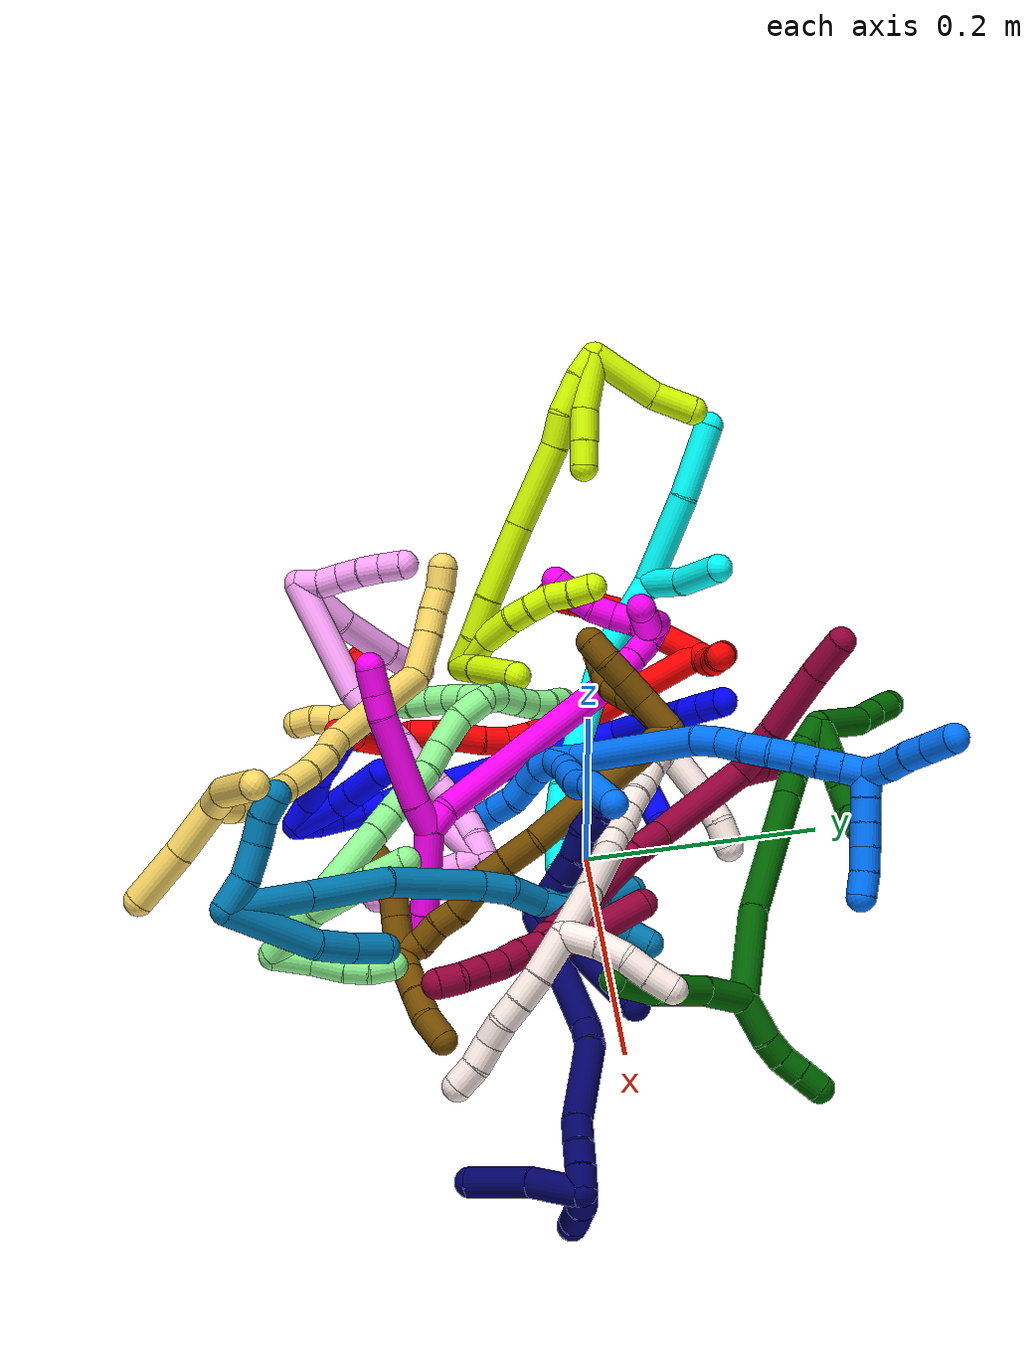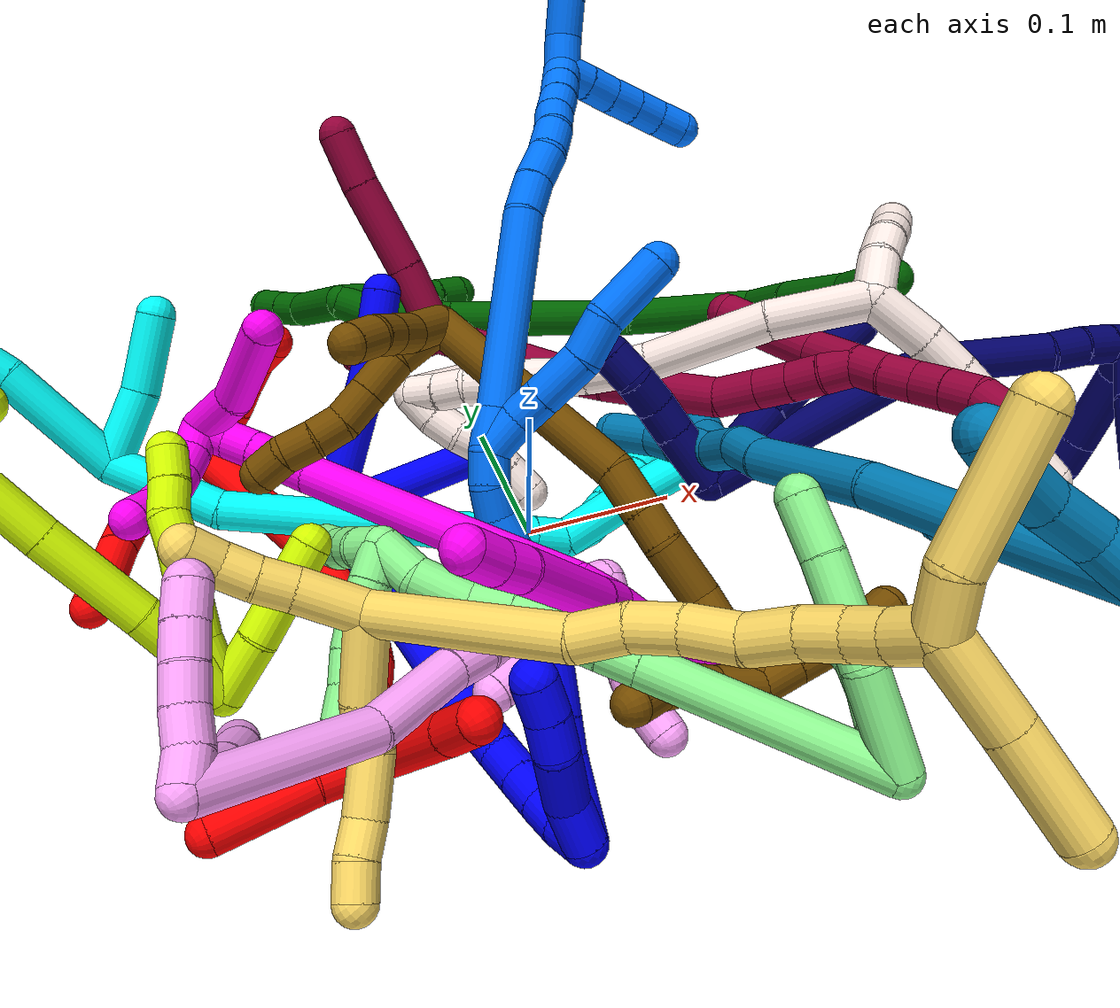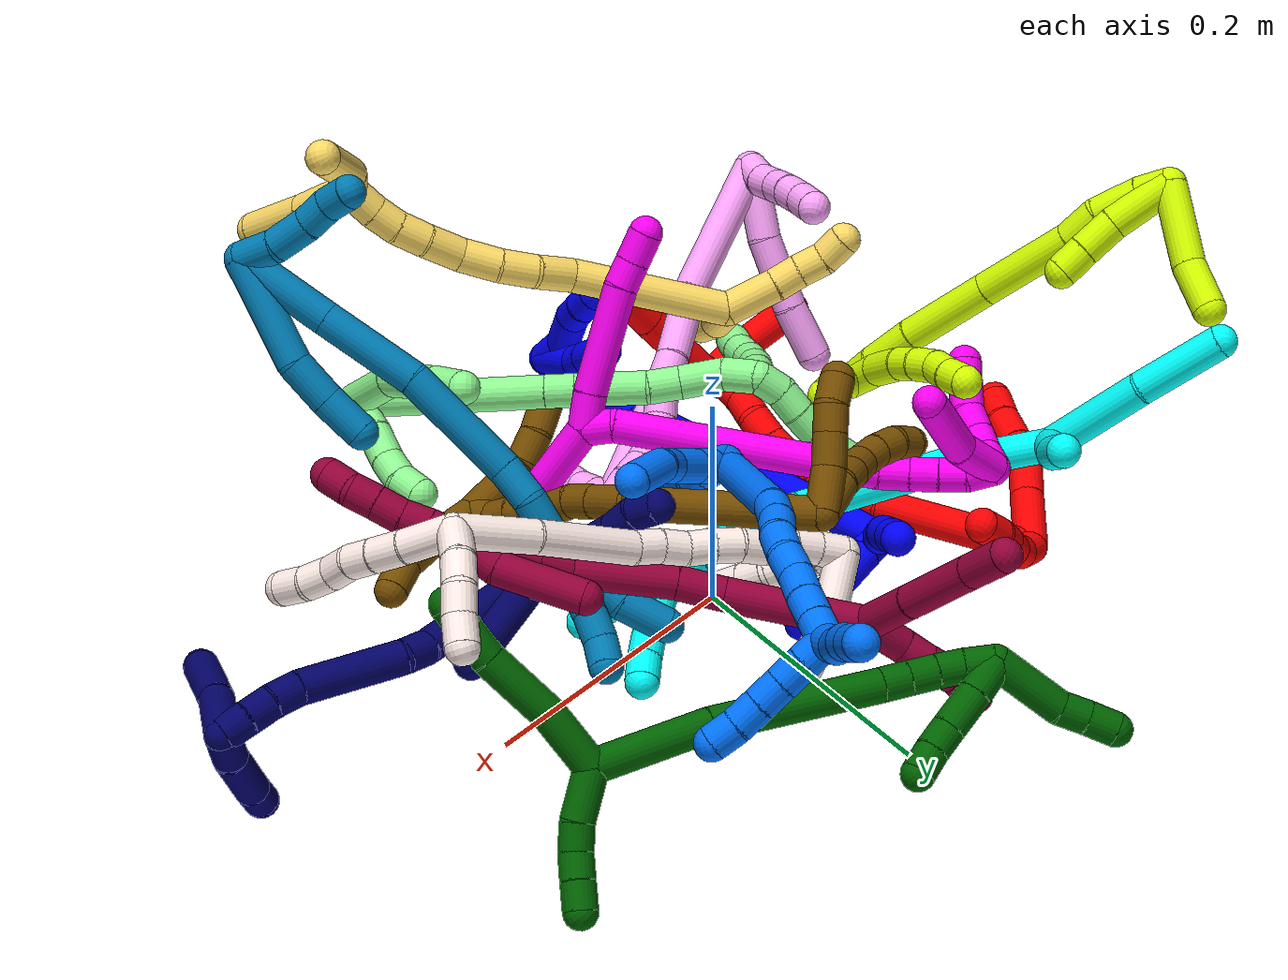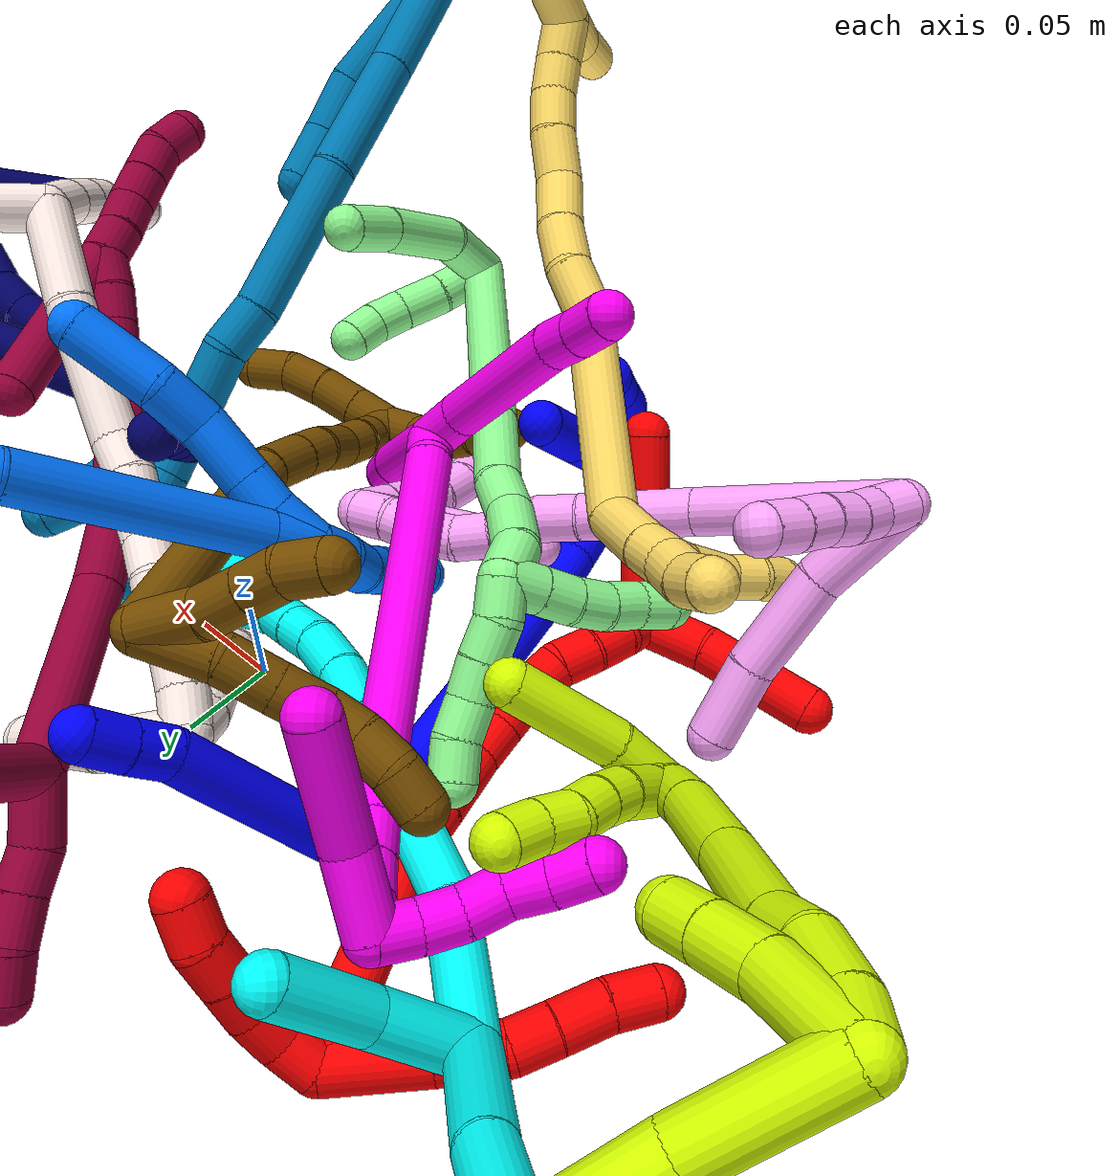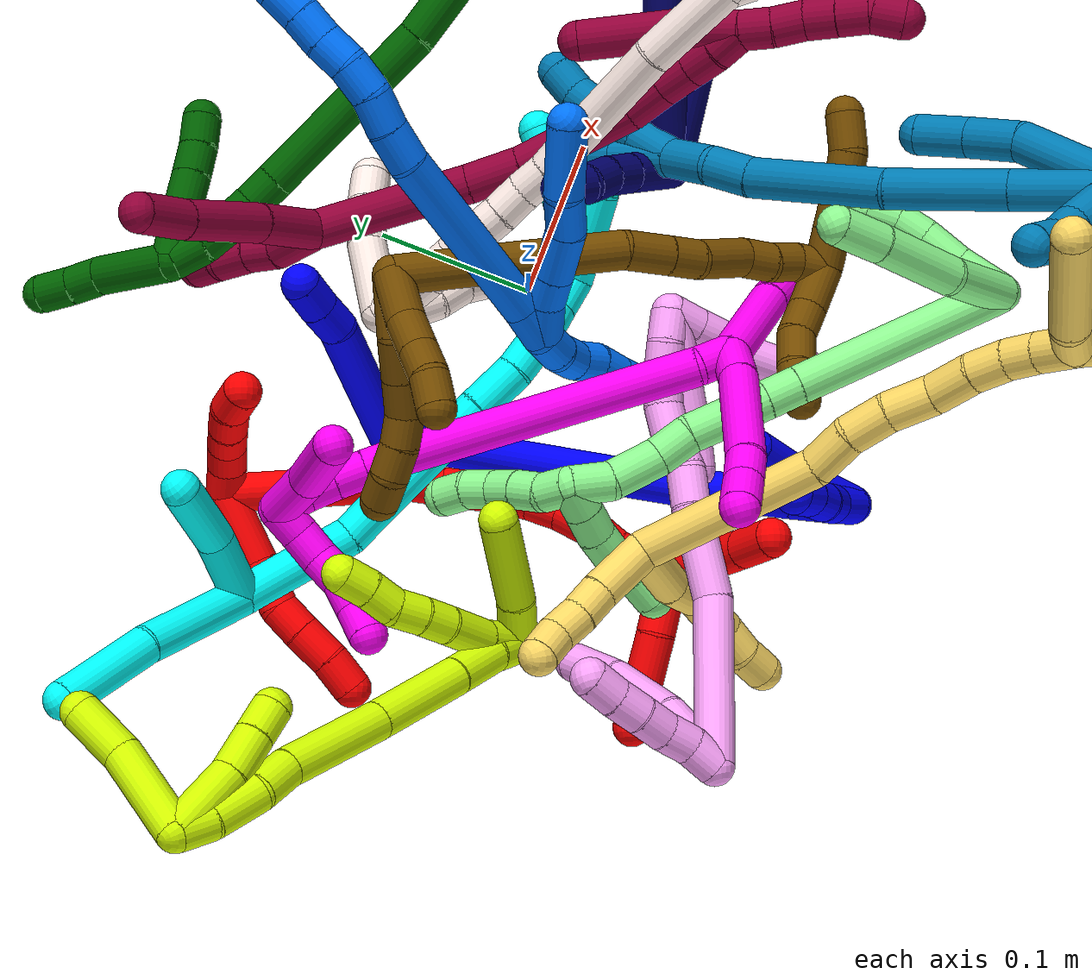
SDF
<sdf version="1.7">
 <world name="default">
  <plugin name="TubeGeneratorPlugin" filename="libtube_generator_plugin.so"/>
  <model name="photoneo_s_sensor">
   <static>1</static>
   <pose>0 0 2 1.57079 1.57079 3.14159</pose>
   <link name="link">
    <inertial><mass>0.1</mass></inertial>
    <sensor name="sensor" type="depth">
     <update_rate>30</update_rate>
     <camera>
      <horizontal_fov>1.22</horizontal_fov>
      <image><width>1920</width><height>1200</height><format>B8G8R8</format></image>
      <clip><near>0.1</near><far>4</far></clip>
      <depth_camera><output>points</output></depth_camera>
     </camera>
     <plugin name="camera_plugin" filename="libgazebo_ros_depth_camera.so">
      <baseline>0.2</baseline>
      <alwaysOn>1</alwaysOn>
      <updateRate>0.0</updateRate>
      <cameraName>camera_ir</cameraName>
      <imageTopicName>/camera/color/image_raw</imageTopicName>
      <cameraInfoTopicName>/camera/color/camera_info</cameraInfoTopicName>
      <depthImageTopicName>/camera/depth/image_raw</depthImageTopicName>
      <depthImageCameraInfoTopicName>/camera/depth/camera_info</depthImageCameraInfoTopicName>
      <pointCloudTopicName>/camera/depth/points</pointCloudTopicName>
      <frameName>fr_optical</frameName>
      <pointCloudCutoff>0.1</pointCloudCutoff>
      <pointCloudCutoffMax>2.0</pointCloudCutoffMax>
      <distortionK1>0</distortionK1>
      <distortionK2>0</distortionK2>
      <distortionK3>0</distortionK3>
      <distortionT1>0</distortionT1>
      <distortionT2>0</distortionT2>
      <CxPrime>0</CxPrime>
      <Cx>0</Cx>
      <Cy>0</Cy>
      <focalLength>0</focalLength>
      <hackBaseline>0</hackBaseline>
     </plugin>
    </sensor>
   </link>
  </model>
  <gravity>0 0 -9.8</gravity>
  <magnetic_field>6e-06 2.3e-05 -4.2e-05</magnetic_field>
  <atmosphere type="adiabatic"/>
  <physics name="default_physics" default="0" type="ode">
   <max_step_size>0.003</max_step_size>
   <real_time_factor>1</real_time_factor>
   <real_time_update_rate>1000</real_time_update_rate>
   <max_contacts>10000</max_contacts>
   <ode>
    <solver>
     <type>quick</type>
     <iters>100</iters>
     <sor>1.3</sor>
     <use_dynamic_moi_rescaling>0</use_dynamic_moi_rescaling>
    </solver>
    <constraints>
     <contact_max_correcting_vel>0</contact_max_correcting_vel>
     <contact_surface_layer>0.001</contact_surface_layer>
     <cfm>0</cfm>
     <erp>0.2</erp>
    </constraints>
   </ode>
  </physics>
  <scene><ambient>0.4 0.4 0.4 1</ambient><background>0.7 0.7 0.7 1</background><shadows>0</shadows></scene>
  <audio><device>default</device></audio>
  <spherical_coordinates>
   <surface_model>EARTH_WGS84</surface_model>
   <latitude_deg>0</latitude_deg>
   <longitude_deg>0</longitude_deg>
   <elevation>0</elevation>
   <heading_deg>0</heading_deg>
  </spherical_coordinates>
  <model name="bin">
   <static>1</static>
   <link name="bottom">
    <collision name="collision-bottom">
     <pose>0 0 -0.01 0 -0 0</pose>
     <geometry><box><size>0.8 0.6 0.02</size></box></geometry>
     <surface>
      <friction><ode><mu>100</mu><mu2>100</mu2></ode></friction>
      <contact><collide_bitmask>65535</collide_bitmask></contact>
     </surface>
    </collision>
   </link>
   <link name="west_wall">
    <collision name="collision-west_wall">
     <pose>-0.41 0 0.1 0 -0 0</pose>
     <geometry><box><size>0.02 0.6 0.2</size></box></geometry>
     <surface>
      <friction><ode><mu>100</mu><mu2>100</mu2></ode></friction>
      <contact><collide_bitmask>65535</collide_bitmask></contact>
     </surface>
    </collision>
   </link>
   <link name="east_wall">
    <collision name="collision-east_wall">
     <pose>0.41 0 0.1 0 -0 0</pose>
     <geometry><box><size>0.02 0.6 0.2</size></box></geometry>
     <surface>
      <friction><ode><mu>100</mu><mu2>100</mu2></ode></friction>
      <contact><collide_bitmask>65535</collide_bitmask></contact>
     </surface>
    </collision>
   </link>
   <link name="south_wall">
    <collision name="collision-south_wall">
     <pose>0 -0.31 0.1 0 -0 0</pose>
     <geometry><box><size>0.8 0.02 0.2</size></box></geometry>
     <surface>
      <friction><ode><mu>100</mu><mu2>100</mu2></ode></friction>
      <contact><collide_bitmask>65535</collide_bitmask></contact>
     </surface>
    </collision>
   </link>
   <link name="north_wall">
    <collision name="collision-north_wall">
     <pose>0 0.31 0.1 0 -0 0</pose>
     <geometry><box><size>0.8 0.02 0.2</size></box></geometry>
     <surface>
      <friction><ode><mu>100</mu><mu2>100</mu2></ode></friction>
      <contact><collide_bitmask>65535</collide_bitmask></contact>
     </surface>
    </collision>
   </link>
  </model>
  <model name="1">
   <static>0</static>
   <link name="1">
    <collision name="collision-cylinder-e_1_2_8">
     <pose>0.014424 0.001561 -0.051598 -3.11135 0.272464 -2.92186</pose>
     <geometry><cylinder><radius>0.0125</radius><length>0.107198</length></cylinder></geometry>
     <surface>
      <friction><ode><mu>1.16</mu><mu2>1.16</mu2><slip1>0</slip1><slip2>0</slip2></ode></friction>
      <contact><ode><kp>1e+06</kp><kd>1</kd><max_vel>0</max_vel><min_depth>0.001</min_depth></ode></contact>
     </surface>
    </collision>
    <visual name="visual-cylinder-e_1_2_8">
     <pose>0.014424 0.001561 -0.051598 -3.11135 0.272464 -2.92186</pose>
     <geometry><cylinder><radius>0.0125</radius><length>0.107198</length></cylinder></geometry>
     <material><ambient>0 0 1 1</ambient></material>
    </visual>
    <collision name="collision-cylinder-e_2_8_9">
     <pose>0.033434 0.005569 -0.112591 -2.88679 0.441342 -2.10391</pose>
     <geometry><cylinder><radius>0.0125</radius><length>0.021474</length></cylinder></geometry>
     <surface>
      <friction><ode><mu>1.16</mu><mu2>1.16</mu2><slip1>0</slip1><slip2>0</slip2></ode></friction>
      <contact><ode><kp>1e+06</kp><kd>1</kd><max_vel>0</max_vel><min_depth>0.001</min_depth></ode></contact>
     </surface>
    </collision>
    <visual name="visual-cylinder-e_2_8_9">
     <pose>0.033434 0.005569 -0.112591 -2.88679 0.441342 -2.10391</pose>
     <geometry><cylinder><radius>0.0125</radius><length>0.021474</length></cylinder></geometry>
     <material><ambient>0 0 1 1</ambient></material>
    </visual>
    <collision name="collision-cylinder-e_3_9_6">
     <pose>0.042074 0.010222 -0.1316 -2.91602 0.38991 -2.10003</pose>
     <geometry><cylinder><radius>0.0125</radius><length>0.021328</length></cylinder></geometry>
     <surface>
      <friction><ode><mu>1.16</mu><mu2>1.16</mu2><slip1>0</slip1><slip2>0</slip2></ode></friction>
      <contact><ode><kp>1e+06</kp><kd>1</kd><max_vel>0</max_vel><min_depth>0.001</min_depth></ode></contact>
     </surface>
    </collision>
    <visual name="visual-cylinder-e_3_9_6">
     <pose>0.042074 0.010222 -0.1316 -2.91602 0.38991 -2.10003</pose>
     <geometry><cylinder><radius>0.0125</radius><length>0.021328</length></cylinder></geometry>
     <material><ambient>0 0 1 1</ambient></material>
    </visual>
    <collision name="collision-cylinder-e_1_2_10">
     <pose>-0.005672 0.003988 -0.00741 -2.64785 -0.593125 1.76233</pose>
     <geometry><cylinder><radius>0.0125</radius><length>0.020296</length></cylinder></geometry>
     <surface>
      <friction><ode><mu>1.16</mu><mu2>1.16</mu2><slip1>0</slip1><slip2>0</slip2></ode></friction>
      <contact><ode><kp>1e+06</kp><kd>1</kd><max_vel>0</max_vel><min_depth>0.001</min_depth></ode></contact>
     </surface>
    </collision>
    <visual name="visual-cylinder-e_1_2_10">
     <pose>-0.005672 0.003988 -0.00741 -2.64785 -0.593125 1.76233</pose>
     <geometry><cylinder><radius>0.0125</radius><length>0.020296</length></cylinder></geometry>
     <material><ambient>0 0 1 1</ambient></material>
    </visual>
    <collision name="collision-cylinder-e_2_10_5">
     <pose>-0.034658 0.024854 -0.042384 -2.59218 -0.624894 1.7068</pose>
     <geometry><cylinder><radius>0.0125</radius><length>0.079704</length></cylinder></geometry>
     <surface>
      <friction><ode><mu>1.16</mu><mu2>1.16</mu2><slip1>0</slip1><slip2>0</slip2></ode></friction>
      <contact><ode><kp>1e+06</kp><kd>1</kd><max_vel>0</max_vel><min_depth>0.001</min_depth></ode></contact>
     </surface>
    </collision>
    <visual name="visual-cylinder-e_2_10_5">
     <pose>-0.034658 0.024854 -0.042384 -2.59218 -0.624894 1.7068</pose>
     <geometry><cylinder><radius>0.0125</radius><length>0.079704</length></cylinder></geometry>
     <material><ambient>0 0 1 1</ambient></material>
    </visual>
    <collision name="collision-cylinder-e_1_2_11">
     <pose>-0.066949 -0.067949 0.014969 1.35397 -0.766139 -0.626411</pose>
     <geometry><cylinder><radius>0.0125</radius><length>0.193115</length></cylinder></geometry>
     <surface>
      <friction><ode><mu>1.16</mu><mu2>1.16</mu2><slip1>0</slip1><slip2>0</slip2></ode></friction>
      <contact><ode><kp>1e+06</kp><kd>1</kd><max_vel>0</max_vel><min_depth>0.001</min_depth></ode></contact>
     </surface>
    </collision>
    <visual name="visual-cylinder-e_1_2_11">
     <pose>-0.066949 -0.067949 0.014969 1.35397 -0.766139 -0.626411</pose>
     <geometry><cylinder><radius>0.0125</radius><length>0.193115</length></cylinder></geometry>
     <material><ambient>0 0 1 1</ambient></material>
    </visual>
    <collision name="collision-cylinder-e_2_11_12">
     <pose>-0.143167 -0.143906 0.031585 1.36789 -0.848059 -0.705235</pose>
     <geometry><cylinder><radius>0.0125</radius><length>0.024719</length></cylinder></geometry>
     <surface>
      <friction><ode><mu>1.16</mu><mu2>1.16</mu2><slip1>0</slip1><slip2>0</slip2></ode></friction>
      <contact><ode><kp>1e+06</kp><kd>1</kd><max_vel>0</max_vel><min_depth>0.001</min_depth></ode></contact>
     </surface>
    </collision>
    <visual name="visual-cylinder-e_2_11_12">
     <pose>-0.143167 -0.143906 0.031585 1.36789 -0.848059 -0.705235</pose>
     <geometry><cylinder><radius>0.0125</radius><length>0.024719</length></cylinder></geometry>
     <material><ambient>0 0 1 1</ambient></material>
    </visual>
    <collision name="collision-cylinder-e_3_12_13">
     <pose>-0.159773 -0.159917 0.033862 1.49225 -0.740379 -0.688873</pose>
     <geometry><cylinder><radius>0.0125</radius><length>0.021751</length></cylinder></geometry>
     <surface>
      <friction><ode><mu>1.16</mu><mu2>1.16</mu2><slip1>0</slip1><slip2>0</slip2></ode></friction>
      <contact><ode><kp>1e+06</kp><kd>1</kd><max_vel>0</max_vel><min_depth>0.001</min_depth></ode></contact>
     </surface>
    </collision>
    <visual name="visual-cylinder-e_3_12_13">
     <pose>-0.159773 -0.159917 0.033862 1.49225 -0.740379 -0.688873</pose>
     <geometry><cylinder><radius>0.0125</radius><length>0.021751</length></cylinder></geometry>
     <material><ambient>0 0 1 1</ambient></material>
    </visual>
    <collision name="collision-cylinder-e_4_13_14">
     <pose>-0.173798 -0.175604 0.034896 1.51832 -0.715638 -0.68187</pose>
     <geometry><cylinder><radius>0.0125</radius><length>0.020388</length></cylinder></geometry>
     <surface>
      <friction><ode><mu>1.16</mu><mu2>1.16</mu2><slip1>0</slip1><slip2>0</slip2></ode></friction>
      <contact><ode><kp>1e+06</kp><kd>1</kd><max_vel>0</max_vel><min_depth>0.001</min_depth></ode></contact>
     </surface>
    </collision>
    <visual name="visual-cylinder-e_4_13_14">
     <pose>-0.173798 -0.175604 0.034896 1.51832 -0.715638 -0.68187</pose>
     <geometry><cylinder><radius>0.0125</radius><length>0.020388</length></cylinder></geometry>
     <material><ambient>0 0 1 1</ambient></material>
    </visual>
    <collision name="collision-cylinder-e_5_14_15">
     <pose>-0.186888 -0.190977 0.035184 1.58576 -0.694134 -0.703762</pose>
     <geometry><cylinder><radius>0.0125</radius><length>0.020015</length></cylinder></geometry>
     <surface>
      <friction><ode><mu>1.16</mu><mu2>1.16</mu2><slip1>0</slip1><slip2>0</slip2></ode></friction>
      <contact><ode><kp>1e+06</kp><kd>1</kd><max_vel>0</max_vel><min_depth>0.001</min_depth></ode></contact>
     </surface>
    </collision>
    <visual name="visual-cylinder-e_5_14_15">
     <pose>-0.186888 -0.190977 0.035184 1.58576 -0.694134 -0.703762</pose>
     <geometry><cylinder><radius>0.0125</radius><length>0.020015</length></cylinder></geometry>
     <material><ambient>0 0 1 1</ambient></material>
    </visual>
    <collision name="collision-cylinder-e_6_15_1">
     <pose>-0.198378 -0.207078 0.033196 1.78996 -0.533411 -0.656852</pose>
     <geometry><cylinder><radius>0.0125</radius><length>0.020012</length></cylinder></geometry>
     <surface>
      <friction><ode><mu>1.16</mu><mu2>1.16</mu2><slip1>0</slip1><slip2>0</slip2></ode></friction>
      <contact><ode><kp>1e+06</kp><kd>1</kd><max_vel>0</max_vel><min_depth>0.001</min_depth></ode></contact>
     </surface>
    </collision>
    <visual name="visual-cylinder-e_6_15_1">
     <pose>-0.198378 -0.207078 0.033196 1.78996 -0.533411 -0.656852</pose>
     <geometry><cylinder><radius>0.0125</radius><length>0.020012</length></cylinder></geometry>
     <material><ambient>0 0 1 1</ambient></material>
    </visual>
    <collision name="collision-cylinder-e_1_1_16">
     <pose>-0.193156 -0.217141 0.023656 2.92923 0.920452 2.71804</pose>
     <geometry><cylinder><radius>0.0125</radius><length>0.025907</length></cylinder></geometry>
     <surface>
      <friction><ode><mu>1.16</mu><mu2>1.16</mu2><slip1>0</slip1><slip2>0</slip2></ode></friction>
      <contact><ode><kp>1e+06</kp><kd>1</kd><max_vel>0</max_vel><min_depth>0.001</min_depth></ode></contact>
     </surface>
    </collision>
    <visual name="visual-cylinder-e_1_1_16">
     <pose>-0.193156 -0.217141 0.023656 2.92923 0.920452 2.71804</pose>
     <geometry><cylinder><radius>0.0125</radius><length>0.025907</length></cylinder></geometry>
     <material><ambient>0 0 1 1</ambient></material>
    </visual>
    <collision name="collision-cylinder-e_2_16_17">
     <pose>-0.172431 -0.225488 0.004467 2.61531 0.663428 1.81413</pose>
     <geometry><cylinder><radius>0.0125</radius><length>0.033827</length></cylinder></geometry>
     <surface>
      <friction><ode><mu>1.16</mu><mu2>1.16</mu2><slip1>0</slip1><slip2>0</slip2></ode></friction>
      <contact><ode><kp>1e+06</kp><kd>1</kd><max_vel>0</max_vel><min_depth>0.001</min_depth></ode></contact>
     </surface>
    </collision>
    <visual name="visual-cylinder-e_2_16_17">
     <pose>-0.172431 -0.225488 0.004467 2.61531 0.663428 1.81413</pose>
     <geometry><cylinder><radius>0.0125</radius><length>0.033827</length></cylinder></geometry>
     <material><ambient>0 0 1 1</ambient></material>
    </visual>
    <collision name="collision-cylinder-e_3_17_18">
     <pose>-0.15506 -0.233503 -0.014211 2.95898 0.762887 2.69272</pose>
     <geometry><cylinder><radius>0.0125</radius><length>0.020131</length></cylinder></geometry>
     <surface>
      <friction><ode><mu>1.16</mu><mu2>1.16</mu2><slip1>0</slip1><slip2>0</slip2></ode></friction>
      <contact><ode><kp>1e+06</kp><kd>1</kd><max_vel>0</max_vel><min_depth>0.001</min_depth></ode></contact>
     </surface>
    </collision>
    <visual name="visual-cylinder-e_3_17_18">
     <pose>-0.15506 -0.233503 -0.014211 2.95898 0.762887 2.69272</pose>
     <geometry><cylinder><radius>0.0125</radius><length>0.020131</length></cylinder></geometry>
     <material><ambient>0 0 1 1</ambient></material>
    </visual>
    <collision name="collision-cylinder-e_4_18_4">
     <pose>-0.140453 -0.236331 -0.027732 2.90927 0.863397 2.64544</pose>
     <geometry><cylinder><radius>0.0125</radius><length>0.020135</length></cylinder></geometry>
     <surface>
      <friction><ode><mu>1.16</mu><mu2>1.16</mu2><slip1>0</slip1><slip2>0</slip2></ode></friction>
      <contact><ode><kp>1e+06</kp><kd>1</kd><max_vel>0</max_vel><min_depth>0.001</min_depth></ode></contact>
     </surface>
    </collision>
    <visual name="visual-cylinder-e_4_18_4">
     <pose>-0.140453 -0.236331 -0.027732 2.90927 0.863397 2.64544</pose>
     <geometry><cylinder><radius>0.0125</radius><length>0.020135</length></cylinder></geometry>
     <material><ambient>0 0 1 1</ambient></material>
    </visual>
    <collision name="collision-cylinder-e_1_1_19">
     <pose>-0.188243 -0.208405 0.016514 -2.69549 0.747703 -2.09313</pose>
     <geometry><cylinder><radius>0.0125</radius><length>0.044775</length></cylinder></geometry>
     <surface>
      <friction><ode><mu>1.16</mu><mu2>1.16</mu2><slip1>0</slip1><slip2>0</slip2></ode></friction>
      <contact><ode><kp>1e+06</kp><kd>1</kd><max_vel>0</max_vel><min_depth>0.001</min_depth></ode></contact>
     </surface>
    </collision>
    <visual name="visual-cylinder-e_1_1_19">
     <pose>-0.188243 -0.208405 0.016514 -2.69549 0.747703 -2.09313</pose>
     <geometry><cylinder><radius>0.0125</radius><length>0.044775</length></cylinder></geometry>
     <material><ambient>0 0 1 1</ambient></material>
    </visual>
    <collision name="collision-cylinder-e_2_19_20">
     <pose>-0.166453 -0.200247 -0.006152 -3.00549 0.691721 -2.76771</pose>
     <geometry><cylinder><radius>0.0125</radius><length>0.020592</length></cylinder></geometry>
     <surface>
      <friction><ode><mu>1.16</mu><mu2>1.16</mu2><slip1>0</slip1><slip2>0</slip2></ode></friction>
      <contact><ode><kp>1e+06</kp><kd>1</kd><max_vel>0</max_vel><min_depth>0.001</min_depth></ode></contact>
     </surface>
    </collision>
    <visual name="visual-cylinder-e_2_19_20">
     <pose>-0.166453 -0.200247 -0.006152 -3.00549 0.691721 -2.76771</pose>
     <geometry><cylinder><radius>0.0125</radius><length>0.020592</length></cylinder></geometry>
     <material><ambient>0 0 1 1</ambient></material>
    </visual>
    <collision name="collision-cylinder-e_3_20_3">
     <pose>-0.148874 -0.197371 -0.02725 -3.00648 0.68918 -2.76894</pose>
     <geometry><cylinder><radius>0.0125</radius><length>0.034633</length></cylinder></geometry>
     <surface>
      <friction><ode><mu>1.16</mu><mu2>1.16</mu2><slip1>0</slip1><slip2>0</slip2></ode></friction>
      <contact><ode><kp>1e+06</kp><kd>1</kd><max_vel>0</max_vel><min_depth>0.001</min_depth></ode></contact>
     </surface>
    </collision>
    <visual name="visual-cylinder-e_3_20_3">
     <pose>-0.148874 -0.197371 -0.02725 -3.00648 0.68918 -2.76894</pose>
     <geometry><cylinder><radius>0.0125</radius><length>0.034633</length></cylinder></geometry>
     <material><ambient>0 0 1 1</ambient></material>
    </visual>
    <collision name="collision-sphere-3">
     <pose>-0.137862 -0.19557 -0.040493 0 -0 0</pose>
     <geometry><sphere><radius>0.0125</radius></sphere></geometry>
     <surface>
      <friction><ode><mu>1.16</mu><mu2>1.16</mu2><slip1>0</slip1><slip2>0</slip2></ode></friction>
      <contact><ode><kp>1e+06</kp><kd>1</kd><max_vel>0</max_vel><min_depth>0.001</min_depth></ode></contact>
     </surface>
    </collision>
    <visual name="visual-sphere-3">
     <pose>-0.137862 -0.19557 -0.040493 0 -0 0</pose>
     <geometry><sphere><radius>0.0125</radius></sphere></geometry>
     <material><ambient>0 0 1 1</ambient></material>
    </visual>
    <collision name="collision-sphere-20">
     <pose>-0.159886 -0.199171 -0.014008 0 -0 0</pose>
     <geometry><sphere><radius>0.0125</radius></sphere></geometry>
     <surface>
      <friction><ode><mu>1.16</mu><mu2>1.16</mu2><slip1>0</slip1><slip2>0</slip2></ode></friction>
      <contact><ode><kp>1e+06</kp><kd>1</kd><max_vel>0</max_vel><min_depth>0.001</min_depth></ode></contact>
     </surface>
    </collision>
    <visual name="visual-sphere-20">
     <pose>-0.159886 -0.199171 -0.014008 0 -0 0</pose>
     <geometry><sphere><radius>0.0125</radius></sphere></geometry>
     <material><ambient>0 0 1 1</ambient></material>
    </visual>
    <collision name="collision-sphere-19">
     <pose>-0.173021 -0.201323 0.001705 0 -0 0</pose>
     <geometry><sphere><radius>0.0125</radius></sphere></geometry>
     <surface>
      <friction><ode><mu>1.16</mu><mu2>1.16</mu2><slip1>0</slip1><slip2>0</slip2></ode></friction>
      <contact><ode><kp>1e+06</kp><kd>1</kd><max_vel>0</max_vel><min_depth>0.001</min_depth></ode></contact>
     </surface>
    </collision>
    <visual name="visual-sphere-19">
     <pose>-0.173021 -0.201323 0.001705 0 -0 0</pose>
     <geometry><sphere><radius>0.0125</radius></sphere></geometry>
     <material><ambient>0 0 1 1</ambient></material>
    </visual>
    <collision name="collision-sphere-5">
     <pose>-0.057972 0.041731 -0.069948 0 -0 0</pose>
     <geometry><sphere><radius>0.0125</radius></sphere></geometry>
     <surface>
      <friction><ode><mu>1.16</mu><mu2>1.16</mu2><slip1>0</slip1><slip2>0</slip2></ode></friction>
      <contact><ode><kp>1e+06</kp><kd>1</kd><max_vel>0</max_vel><min_depth>0.001</min_depth></ode></contact>
     </surface>
    </collision>
    <visual name="visual-sphere-5">
     <pose>-0.057972 0.041731 -0.069948 0 -0 0</pose>
     <geometry><sphere><radius>0.0125</radius></sphere></geometry>
     <material><ambient>0 0 1 1</ambient></material>
    </visual>
    <collision name="collision-sphere-10">
     <pose>-0.011345 0.007976 -0.01482 0 -0 0</pose>
     <geometry><sphere><radius>0.0125</radius></sphere></geometry>
     <surface>
      <friction><ode><mu>1.16</mu><mu2>1.16</mu2><slip1>0</slip1><slip2>0</slip2></ode></friction>
      <contact><ode><kp>1e+06</kp><kd>1</kd><max_vel>0</max_vel><min_depth>0.001</min_depth></ode></contact>
     </surface>
    </collision>
    <visual name="visual-sphere-10">
     <pose>-0.011345 0.007976 -0.01482 0 -0 0</pose>
     <geometry><sphere><radius>0.0125</radius></sphere></geometry>
     <material><ambient>0 0 1 1</ambient></material>
    </visual>
    <collision name="collision-sphere-6">
     <pose>0.046127 0.012428 -0.141213 0 -0 0</pose>
     <geometry><sphere><radius>0.0125</radius></sphere></geometry>
     <surface>
      <friction><ode><mu>1.16</mu><mu2>1.16</mu2><slip1>0</slip1><slip2>0</slip2></ode></friction>
      <contact><ode><kp>1e+06</kp><kd>1</kd><max_vel>0</max_vel><min_depth>0.001</min_depth></ode></contact>
     </surface>
    </collision>
    <visual name="visual-sphere-6">
     <pose>0.046127 0.012428 -0.141213 0 -0 0</pose>
     <geometry><sphere><radius>0.0125</radius></sphere></geometry>
     <material><ambient>0 0 1 1</ambient></material>
    </visual>
    <collision name="collision-sphere-9">
     <pose>0.03802 0.008016 -0.121986 0 -0 0</pose>
     <geometry><sphere><radius>0.0125</radius></sphere></geometry>
     <surface>
      <friction><ode><mu>1.16</mu><mu2>1.16</mu2><slip1>0</slip1><slip2>0</slip2></ode></friction>
      <contact><ode><kp>1e+06</kp><kd>1</kd><max_vel>0</max_vel><min_depth>0.001</min_depth></ode></contact>
     </surface>
    </collision>
    <visual name="visual-sphere-9">
     <pose>0.03802 0.008016 -0.121986 0 -0 0</pose>
     <geometry><sphere><radius>0.0125</radius></sphere></geometry>
     <material><ambient>0 0 1 1</ambient></material>
    </visual>
    <collision name="collision-sphere-2">
     <geometry><sphere><radius>0.0125</radius></sphere></geometry>
     <surface>
      <friction><ode><mu>1.16</mu><mu2>1.16</mu2><slip1>0</slip1><slip2>0</slip2></ode></friction>
      <contact><ode><kp>1e+06</kp><kd>1</kd><max_vel>0</max_vel><min_depth>0.001</min_depth></ode></contact>
     </surface>
    </collision>
    <visual name="visual-sphere-2">
     <geometry><sphere><radius>0.0125</radius></sphere></geometry>
     <material><ambient>0 0 1 1</ambient></material>
    </visual>
    <collision name="collision-sphere-8">
     <pose>0.028848 0.003122 -0.103197 0 -0 0</pose>
     <geometry><sphere><radius>0.0125</radius></sphere></geometry>
     <surface>
      <friction><ode><mu>1.16</mu><mu2>1.16</mu2><slip1>0</slip1><slip2>0</slip2></ode></friction>
      <contact><ode><kp>1e+06</kp><kd>1</kd><max_vel>0</max_vel><min_depth>0.001</min_depth></ode></contact>
     </surface>
    </collision>
    <visual name="visual-sphere-8">
     <pose>0.028848 0.003122 -0.103197 0 -0 0</pose>
     <geometry><sphere><radius>0.0125</radius></sphere></geometry>
     <material><ambient>0 0 1 1</ambient></material>
    </visual>
    <collision name="collision-sphere-11">
     <pose>-0.133898 -0.135899 0.029938 0 -0 0</pose>
     <geometry><sphere><radius>0.0125</radius></sphere></geometry>
     <surface>
      <friction><ode><mu>1.16</mu><mu2>1.16</mu2><slip1>0</slip1><slip2>0</slip2></ode></friction>
      <contact><ode><kp>1e+06</kp><kd>1</kd><max_vel>0</max_vel><min_depth>0.001</min_depth></ode></contact>
     </surface>
    </collision>
    <visual name="visual-sphere-11">
     <pose>-0.133898 -0.135899 0.029938 0 -0 0</pose>
     <geometry><sphere><radius>0.0125</radius></sphere></geometry>
     <material><ambient>0 0 1 1</ambient></material>
    </visual>
    <collision name="collision-sphere-12">
     <pose>-0.152437 -0.151914 0.033232 0 -0 0</pose>
     <geometry><sphere><radius>0.0125</radius></sphere></geometry>
     <surface>
      <friction><ode><mu>1.16</mu><mu2>1.16</mu2><slip1>0</slip1><slip2>0</slip2></ode></friction>
      <contact><ode><kp>1e+06</kp><kd>1</kd><max_vel>0</max_vel><min_depth>0.001</min_depth></ode></contact>
     </surface>
    </collision>
    <visual name="visual-sphere-12">
     <pose>-0.152437 -0.151914 0.033232 0 -0 0</pose>
     <geometry><sphere><radius>0.0125</radius></sphere></geometry>
     <material><ambient>0 0 1 1</ambient></material>
    </visual>
    <collision name="collision-sphere-13">
     <pose>-0.167109 -0.167921 0.034492 0 -0 0</pose>
     <geometry><sphere><radius>0.0125</radius></sphere></geometry>
     <surface>
      <friction><ode><mu>1.16</mu><mu2>1.16</mu2><slip1>0</slip1><slip2>0</slip2></ode></friction>
      <contact><ode><kp>1e+06</kp><kd>1</kd><max_vel>0</max_vel><min_depth>0.001</min_depth></ode></contact>
     </surface>
    </collision>
    <visual name="visual-sphere-13">
     <pose>-0.167109 -0.167921 0.034492 0 -0 0</pose>
     <geometry><sphere><radius>0.0125</radius></sphere></geometry>
     <material><ambient>0 0 1 1</ambient></material>
    </visual>
    <collision name="collision-sphere-14">
     <pose>-0.180486 -0.183286 0.035299 0 -0 0</pose>
     <geometry><sphere><radius>0.0125</radius></sphere></geometry>
     <surface>
      <friction><ode><mu>1.16</mu><mu2>1.16</mu2><slip1>0</slip1><slip2>0</slip2></ode></friction>
      <contact><ode><kp>1e+06</kp><kd>1</kd><max_vel>0</max_vel><min_depth>0.001</min_depth></ode></contact>
     </surface>
    </collision>
    <visual name="visual-sphere-14">
     <pose>-0.180486 -0.183286 0.035299 0 -0 0</pose>
     <geometry><sphere><radius>0.0125</radius></sphere></geometry>
     <material><ambient>0 0 1 1</ambient></material>
    </visual>
    <collision name="collision-sphere-15">
     <pose>-0.19329 -0.198668 0.035069 0 -0 0</pose>
     <geometry><sphere><radius>0.0125</radius></sphere></geometry>
     <surface>
      <friction><ode><mu>1.16</mu><mu2>1.16</mu2><slip1>0</slip1><slip2>0</slip2></ode></friction>
      <contact><ode><kp>1e+06</kp><kd>1</kd><max_vel>0</max_vel><min_depth>0.001</min_depth></ode></contact>
     </surface>
    </collision>
    <visual name="visual-sphere-15">
     <pose>-0.19329 -0.198668 0.035069 0 -0 0</pose>
     <geometry><sphere><radius>0.0125</radius></sphere></geometry>
     <material><ambient>0 0 1 1</ambient></material>
    </visual>
    <collision name="collision-sphere-1">
     <pose>-0.203466 -0.215488 0.031323 0 -0 0</pose>
     <geometry><sphere><radius>0.0125</radius></sphere></geometry>
     <surface>
      <friction><ode><mu>1.16</mu><mu2>1.16</mu2><slip1>0</slip1><slip2>0</slip2></ode></friction>
      <contact><ode><kp>1e+06</kp><kd>1</kd><max_vel>0</max_vel><min_depth>0.001</min_depth></ode></contact>
     </surface>
    </collision>
    <visual name="visual-sphere-1">
     <pose>-0.203466 -0.215488 0.031323 0 -0 0</pose>
     <geometry><sphere><radius>0.0125</radius></sphere></geometry>
     <material><ambient>0 0 1 1</ambient></material>
    </visual>
    <collision name="collision-sphere-18">
     <pose>-0.148104 -0.234824 -0.021366 0 -0 0</pose>
     <geometry><sphere><radius>0.0125</radius></sphere></geometry>
     <surface>
      <friction><ode><mu>1.16</mu><mu2>1.16</mu2><slip1>0</slip1><slip2>0</slip2></ode></friction>
      <contact><ode><kp>1e+06</kp><kd>1</kd><max_vel>0</max_vel><min_depth>0.001</min_depth></ode></contact>
     </surface>
    </collision>
    <visual name="visual-sphere-18">
     <pose>-0.148104 -0.234824 -0.021366 0 -0 0</pose>
     <geometry><sphere><radius>0.0125</radius></sphere></geometry>
     <material><ambient>0 0 1 1</ambient></material>
    </visual>
    <collision name="collision-sphere-16">
     <pose>-0.182847 -0.218794 0.015989 0 -0 0</pose>
     <geometry><sphere><radius>0.0125</radius></sphere></geometry>
     <surface>
      <friction><ode><mu>1.16</mu><mu2>1.16</mu2><slip1>0</slip1><slip2>0</slip2></ode></friction>
      <contact><ode><kp>1e+06</kp><kd>1</kd><max_vel>0</max_vel><min_depth>0.001</min_depth></ode></contact>
     </surface>
    </collision>
    <visual name="visual-sphere-16">
     <pose>-0.182847 -0.218794 0.015989 0 -0 0</pose>
     <geometry><sphere><radius>0.0125</radius></sphere></geometry>
     <material><ambient>0 0 1 1</ambient></material>
    </visual>
    <collision name="collision-sphere-17">
     <pose>-0.162015 -0.232182 -0.007056 0 -0 0</pose>
     <geometry><sphere><radius>0.0125</radius></sphere></geometry>
     <surface>
      <friction><ode><mu>1.16</mu><mu2>1.16</mu2><slip1>0</slip1><slip2>0</slip2></ode></friction>
      <contact><ode><kp>1e+06</kp><kd>1</kd><max_vel>0</max_vel><min_depth>0.001</min_depth></ode></contact>
     </surface>
    </collision>
    <visual name="visual-sphere-17">
     <pose>-0.162015 -0.232182 -0.007056 0 -0 0</pose>
     <geometry><sphere><radius>0.0125</radius></sphere></geometry>
     <material><ambient>0 0 1 1</ambient></material>
    </visual>
    <collision name="collision-sphere-4">
     <pose>-0.132801 -0.237837 -0.034099 0 -0 0</pose>
     <geometry><sphere><radius>0.0125</radius></sphere></geometry>
     <surface>
      <friction><ode><mu>1.16</mu><mu2>1.16</mu2><slip1>0</slip1><slip2>0</slip2></ode></friction>
      <contact><ode><kp>1e+06</kp><kd>1</kd><max_vel>0</max_vel><min_depth>0.001</min_depth></ode></contact>
     </surface>
    </collision>
    <visual name="visual-sphere-4">
     <pose>-0.132801 -0.237837 -0.034099 0 -0 0</pose>
     <geometry><sphere><radius>0.0125</radius></sphere></geometry>
     <material><ambient>0 0 1 1</ambient></material>
    </visual>
    <inertial>
     <pose>-0.086282 -0.096187 -0.010944 0 -0 0</pose>
     <mass>0.75</mass>
     <inertia>
      <ixx>-1.6e-05</ixx>
      <ixy>0</ixy>
      <ixz>0</ixz>
      <iyy>0.000233</iyy>
      <iyz>0</iyz>
      <izz>0.000791</izz>
     </inertia>
    </inertial>
   </link>
   <pose>-0.120762 0.048501 0.011471 -2.45184 -0.436077 2.46827</pose>
  </model>
  <model name="2">
   <static>0</static>
   <link name="2">
    <collision name="collision-cylinder-e_1_2_8">
     <pose>-0.003191 -0.010107 0.022033 0.430101 -0.13089 -0.028629</pose>
     <geometry><cylinder><radius>0.0125</radius><length>0.0489</length></cylinder></geometry>
     <surface>
      <friction><ode><mu>1.16</mu><mu2>1.16</mu2><slip1>0</slip1><slip2>0</slip2></ode></friction>
      <contact><ode><kp>1e+06</kp><kd>1</kd><max_vel>0</max_vel><min_depth>0.001</min_depth></ode></contact>
     </surface>
    </collision>
    <visual name="visual-cylinder-e_1_2_8">
     <pose>-0.003191 -0.010107 0.022033 0.430101 -0.13089 -0.028629</pose>
     <geometry><cylinder><radius>0.0125</radius><length>0.0489</length></cylinder></geometry>
     <material><ambient>1 0 0 1</ambient></material>
    </visual>
    <collision name="collision-cylinder-e_2_8_9">
     <pose>-0.006715 -0.026523 0.058669 0.407767 -0.020921 -0.004326</pose>
     <geometry><cylinder><radius>0.0125</radius><length>0.031822</length></cylinder></geometry>
     <surface>
      <friction><ode><mu>1.16</mu><mu2>1.16</mu2><slip1>0</slip1><slip2>0</slip2></ode></friction>
      <contact><ode><kp>1e+06</kp><kd>1</kd><max_vel>0</max_vel><min_depth>0.001</min_depth></ode></contact>
     </surface>
    </collision>
    <visual name="visual-cylinder-e_2_8_9">
     <pose>-0.006715 -0.026523 0.058669 0.407767 -0.020921 -0.004326</pose>
     <geometry><cylinder><radius>0.0125</radius><length>0.031822</length></cylinder></geometry>
     <material><ambient>1 0 0 1</ambient></material>
    </visual>
    <collision name="collision-cylinder-e_3_9_10">
     <pose>-0.007353 -0.039831 0.081183 0.72432 -0.028839 -0.010927</pose>
     <geometry><cylinder><radius>0.0125</radius><length>0.021135</length></cylinder></geometry>
     <surface>
      <friction><ode><mu>1.16</mu><mu2>1.16</mu2><slip1>0</slip1><slip2>0</slip2></ode></friction>
      <contact><ode><kp>1e+06</kp><kd>1</kd><max_vel>0</max_vel><min_depth>0.001</min_depth></ode></contact>
     </surface>
    </collision>
    <visual name="visual-cylinder-e_3_9_10">
     <pose>-0.007353 -0.039831 0.081183 0.72432 -0.028839 -0.010927</pose>
     <geometry><cylinder><radius>0.0125</radius><length>0.021135</length></cylinder></geometry>
     <material><ambient>1 0 0 1</ambient></material>
    </visual>
    <collision name="collision-cylinder-e_4_10_11">
     <pose>-0.008657 -0.055552 0.09794 0.778403 -0.080301 -0.032948</pose>
     <geometry><cylinder><radius>0.0125</radius><length>0.024926</length></cylinder></geometry>
     <surface>
      <friction><ode><mu>1.16</mu><mu2>1.16</mu2><slip1>0</slip1><slip2>0</slip2></ode></friction>
      <contact><ode><kp>1e+06</kp><kd>1</kd><max_vel>0</max_vel><min_depth>0.001</min_depth></ode></contact>
     </surface>
    </collision>
    <visual name="visual-cylinder-e_4_10_11">
     <pose>-0.008657 -0.055552 0.09794 0.778403 -0.080301 -0.032948</pose>
     <geometry><cylinder><radius>0.0125</radius><length>0.024926</length></cylinder></geometry>
     <material><ambient>1 0 0 1</ambient></material>
    </visual>
    <collision name="collision-cylinder-e_5_11_6">
     <pose>-0.011726 -0.071173 0.11589 0.648364 -0.179195 -0.06036</pose>
     <geometry><cylinder><radius>0.0125</radius><length>0.023218</length></cylinder></geometry>
     <surface>
      <friction><ode><mu>1.16</mu><mu2>1.16</mu2><slip1>0</slip1><slip2>0</slip2></ode></friction>
      <contact><ode><kp>1e+06</kp><kd>1</kd><max_vel>0</max_vel><min_depth>0.001</min_depth></ode></contact>
     </surface>
    </collision>
    <visual name="visual-cylinder-e_5_11_6">
     <pose>-0.011726 -0.071173 0.11589 0.648364 -0.179195 -0.06036</pose>
     <geometry><cylinder><radius>0.0125</radius><length>0.023218</length></cylinder></geometry>
     <material><ambient>1 0 0 1</ambient></material>
    </visual>
    <collision name="collision-cylinder-e_1_2_12">
     <pose>0.006511 -0.001034 -0.007519 3.00488 0.708972 2.77579</pose>
     <geometry><cylinder><radius>0.0125</radius><length>0.02</length></cylinder></geometry>
     <surface>
      <friction><ode><mu>1.16</mu><mu2>1.16</mu2><slip1>0</slip1><slip2>0</slip2></ode></friction>
      <contact><ode><kp>1e+06</kp><kd>1</kd><max_vel>0</max_vel><min_depth>0.001</min_depth></ode></contact>
     </surface>
    </collision>
    <visual name="visual-cylinder-e_1_2_12">
     <pose>0.006511 -0.001034 -0.007519 3.00488 0.708972 2.77579</pose>
     <geometry><cylinder><radius>0.0125</radius><length>0.02</length></cylinder></geometry>
     <material><ambient>1 0 0 1</ambient></material>
    </visual>
    <collision name="collision-cylinder-e_2_12_13">
     <pose>0.021533 -0.002631 -0.020258 3.03431 1.0182 2.94979</pose>
     <geometry><cylinder><radius>0.0125</radius><length>0.02</length></cylinder></geometry>
     <surface>
      <friction><ode><mu>1.16</mu><mu2>1.16</mu2><slip1>0</slip1><slip2>0</slip2></ode></friction>
      <contact><ode><kp>1e+06</kp><kd>1</kd><max_vel>0</max_vel><min_depth>0.001</min_depth></ode></contact>
     </surface>
    </collision>
    <visual name="visual-cylinder-e_2_12_13">
     <pose>0.021533 -0.002631 -0.020258 3.03431 1.0182 2.94979</pose>
     <geometry><cylinder><radius>0.0125</radius><length>0.02</length></cylinder></geometry>
     <material><ambient>1 0 0 1</ambient></material>
    </visual>
    <collision name="collision-cylinder-e_3_13_14">
     <pose>0.039417 -0.004058 -0.028855 2.89097 1.21457 2.78292</pose>
     <geometry><cylinder><radius>0.0125</radius><length>0.02</length></cylinder></geometry>
     <surface>
      <friction><ode><mu>1.16</mu><mu2>1.16</mu2><slip1>0</slip1><slip2>0</slip2></ode></friction>
      <contact><ode><kp>1e+06</kp><kd>1</kd><max_vel>0</max_vel><min_depth>0.001</min_depth></ode></contact>
     </surface>
    </collision>
    <visual name="visual-cylinder-e_3_13_14">
     <pose>0.039417 -0.004058 -0.028855 2.89097 1.21457 2.78292</pose>
     <geometry><cylinder><radius>0.0125</radius><length>0.02</length></cylinder></geometry>
     <material><ambient>1 0 0 1</ambient></material>
    </visual>
    <collision name="collision-cylinder-e_4_14_15">
     <pose>0.05788 -0.006115 -0.036225 2.85141 1.1411 2.69385</pose>
     <geometry><cylinder><radius>0.0125</radius><length>0.02</length></cylinder></geometry>
     <surface>
      <friction><ode><mu>1.16</mu><mu2>1.16</mu2><slip1>0</slip1><slip2>0</slip2></ode></friction>
      <contact><ode><kp>1e+06</kp><kd>1</kd><max_vel>0</max_vel><min_depth>0.001</min_depth></ode></contact>
     </surface>
    </collision>
    <visual name="visual-cylinder-e_4_14_15">
     <pose>0.05788 -0.006115 -0.036225 2.85141 1.1411 2.69385</pose>
     <geometry><cylinder><radius>0.0125</radius><length>0.02</length></cylinder></geometry>
     <material><ambient>1 0 0 1</ambient></material>
    </visual>
    <collision name="collision-cylinder-e_5_15_5">
     <pose>0.075226 -0.011569 -0.043917 2.2857 0.971136 1.71603</pose>
     <geometry><cylinder><radius>0.0125</radius><length>0.02</length></cylinder></geometry>
     <surface>
      <friction><ode><mu>1.16</mu><mu2>1.16</mu2><slip1>0</slip1><slip2>0</slip2></ode></friction>
      <contact><ode><kp>1e+06</kp><kd>1</kd><max_vel>0</max_vel><min_depth>0.001</min_depth></ode></contact>
     </surface>
    </collision>
    <visual name="visual-cylinder-e_5_15_5">
     <pose>0.075226 -0.011569 -0.043917 2.2857 0.971136 1.71603</pose>
     <geometry><cylinder><radius>0.0125</radius><length>0.02</length></cylinder></geometry>
     <material><ambient>1 0 0 1</ambient></material>
    </visual>
    <collision name="collision-cylinder-e_1_2_16">
     <pose>0.000684 -0.058507 -0.002473 1.61303 0.011681 0.012185</pose>
     <geometry><cylinder><radius>0.0125</radius><length>0.117126</length></cylinder></geometry>
     <surface>
      <friction><ode><mu>1.16</mu><mu2>1.16</mu2><slip1>0</slip1><slip2>0</slip2></ode></friction>
      <contact><ode><kp>1e+06</kp><kd>1</kd><max_vel>0</max_vel><min_depth>0.001</min_depth></ode></contact>
     </surface>
    </collision>
    <visual name="visual-cylinder-e_1_2_16">
     <pose>0.000684 -0.058507 -0.002473 1.61303 0.011681 0.012185</pose>
     <geometry><cylinder><radius>0.0125</radius><length>0.117126</length></cylinder></geometry>
     <material><ambient>1 0 0 1</ambient></material>
    </visual>
    <collision name="collision-cylinder-e_2_16_17">
     <pose>0.001384 -0.127619 -0.003081 1.39678 0.001503 0.001262</pose>
     <geometry><cylinder><radius>0.0125</radius><length>0.021536</length></cylinder></geometry>
     <surface>
      <friction><ode><mu>1.16</mu><mu2>1.16</mu2><slip1>0</slip1><slip2>0</slip2></ode></friction>
      <contact><ode><kp>1e+06</kp><kd>1</kd><max_vel>0</max_vel><min_depth>0.001</min_depth></ode></contact>
     </surface>
    </collision>
    <visual name="visual-cylinder-e_2_16_17">
     <pose>0.001384 -0.127619 -0.003081 1.39678 0.001503 0.001262</pose>
     <geometry><cylinder><radius>0.0125</radius><length>0.021536</length></cylinder></geometry>
     <material><ambient>1 0 0 1</ambient></material>
    </visual>
    <collision name="collision-cylinder-e_3_17_18">
     <pose>0.00127 -0.155616 0.001443 1.41904 -0.007404 -0.006358</pose>
     <geometry><cylinder><radius>0.0125</radius><length>0.035187</length></cylinder></geometry>
     <surface>
      <friction><ode><mu>1.16</mu><mu2>1.16</mu2><slip1>0</slip1><slip2>0</slip2></ode></friction>
      <contact><ode><kp>1e+06</kp><kd>1</kd><max_vel>0</max_vel><min_depth>0.001</min_depth></ode></contact>
     </surface>
    </collision>
    <visual name="visual-cylinder-e_3_17_18">
     <pose>0.00127 -0.155616 0.001443 1.41904 -0.007404 -0.006358</pose>
     <geometry><cylinder><radius>0.0125</radius><length>0.035187</length></cylinder></geometry>
     <material><ambient>1 0 0 1</ambient></material>
    </visual>
    <collision name="collision-cylinder-e_4_18_19">
     <pose>0.00153 -0.183518 0.006754 1.32367 0.035977 0.028029</pose>
     <geometry><cylinder><radius>0.0125</radius><length>0.021696</length></cylinder></geometry>
     <surface>
      <friction><ode><mu>1.16</mu><mu2>1.16</mu2><slip1>0</slip1><slip2>0</slip2></ode></friction>
      <contact><ode><kp>1e+06</kp><kd>1</kd><max_vel>0</max_vel><min_depth>0.001</min_depth></ode></contact>
     </surface>
    </collision>
    <visual name="visual-cylinder-e_4_18_19">
     <pose>0.00153 -0.183518 0.006754 1.32367 0.035977 0.028029</pose>
     <geometry><cylinder><radius>0.0125</radius><length>0.021696</length></cylinder></geometry>
     <material><ambient>1 0 0 1</ambient></material>
    </visual>
    <collision name="collision-cylinder-e_5_19_20">
     <pose>0.004906 -0.203706 0.013702 1.15303 0.274866 0.179368</pose>
     <geometry><cylinder><radius>0.0125</radius><length>0.022</length></cylinder></geometry>
     <surface>
      <friction><ode><mu>1.16</mu><mu2>1.16</mu2><slip1>0</slip1><slip2>0</slip2></ode></friction>
      <contact><ode><kp>1e+06</kp><kd>1</kd><max_vel>0</max_vel><min_depth>0.001</min_depth></ode></contact>
     </surface>
    </collision>
    <visual name="visual-cylinder-e_5_19_20">
     <pose>0.004906 -0.203706 0.013702 1.15303 0.274866 0.179368</pose>
     <geometry><cylinder><radius>0.0125</radius><length>0.022</length></cylinder></geometry>
     <material><ambient>1 0 0 1</ambient></material>
    </visual>
    <collision name="collision-cylinder-e_6_20_21">
     <pose>0.010296 -0.222386 0.023571 1.01646 0.223285 0.124735</pose>
     <geometry><cylinder><radius>0.0125</radius><length>0.021719</length></cylinder></geometry>
     <surface>
      <friction><ode><mu>1.16</mu><mu2>1.16</mu2><slip1>0</slip1><slip2>0</slip2></ode></friction>
      <contact><ode><kp>1e+06</kp><kd>1</kd><max_vel>0</max_vel><min_depth>0.001</min_depth></ode></contact>
     </surface>
    </collision>
    <visual name="visual-cylinder-e_6_20_21">
     <pose>0.010296 -0.222386 0.023571 1.01646 0.223285 0.124735</pose>
     <geometry><cylinder><radius>0.0125</radius><length>0.021719</length></cylinder></geometry>
     <material><ambient>1 0 0 1</ambient></material>
    </visual>
    <collision name="collision-cylinder-e_7_21_22">
     <pose>0.011992 -0.239123 0.035913 0.851892 -0.06887 -0.031258</pose>
     <geometry><cylinder><radius>0.0125</radius><length>0.020599</length></cylinder></geometry>
     <surface>
      <friction><ode><mu>1.16</mu><mu2>1.16</mu2><slip1>0</slip1><slip2>0</slip2></ode></friction>
      <contact><ode><kp>1e+06</kp><kd>1</kd><max_vel>0</max_vel><min_depth>0.001</min_depth></ode></contact>
     </surface>
    </collision>
    <visual name="visual-cylinder-e_7_21_22">
     <pose>0.011992 -0.239123 0.035913 0.851892 -0.06887 -0.031258</pose>
     <geometry><cylinder><radius>0.0125</radius><length>0.020599</length></cylinder></geometry>
     <material><ambient>1 0 0 1</ambient></material>
    </visual>
    <collision name="collision-cylinder-e_8_22_23">
     <pose>0.009659 -0.255163 0.048064 0.995772 -0.162585 -0.088512</pose>
     <geometry><cylinder><radius>0.0125</radius><length>0.020065</length></cylinder></geometry>
     <surface>
      <friction><ode><mu>1.16</mu><mu2>1.16</mu2><slip1>0</slip1><slip2>0</slip2></ode></friction>
      <contact><ode><kp>1e+06</kp><kd>1</kd><max_vel>0</max_vel><min_depth>0.001</min_depth></ode></contact>
     </surface>
    </collision>
    <visual name="visual-cylinder-e_8_22_23">
     <pose>0.009659 -0.255163 0.048064 0.995772 -0.162585 -0.088512</pose>
     <geometry><cylinder><radius>0.0125</radius><length>0.020065</length></cylinder></geometry>
     <material><ambient>1 0 0 1</ambient></material>
    </visual>
    <collision name="collision-cylinder-e_9_23_1">
     <pose>0.004571 -0.272412 0.056413 1.25062 -0.35243 -0.255703</pose>
     <geometry><cylinder><radius>0.0125</radius><length>0.020072</length></cylinder></geometry>
     <surface>
      <friction><ode><mu>1.16</mu><mu2>1.16</mu2><slip1>0</slip1><slip2>0</slip2></ode></friction>
      <contact><ode><kp>1e+06</kp><kd>1</kd><max_vel>0</max_vel><min_depth>0.001</min_depth></ode></contact>
     </surface>
    </collision>
    <visual name="visual-cylinder-e_9_23_1">
     <pose>0.004571 -0.272412 0.056413 1.25062 -0.35243 -0.255703</pose>
     <geometry><cylinder><radius>0.0125</radius><length>0.020072</length></cylinder></geometry>
     <material><ambient>1 0 0 1</ambient></material>
    </visual>
    <collision name="collision-cylinder-e_1_1_24">
     <pose>0.030169 -0.302313 0.056462 1.70899 0.941407 1.05792</pose>
     <geometry><cylinder><radius>0.0125</radius><length>0.071902</length></cylinder></geometry>
     <surface>
      <friction><ode><mu>1.16</mu><mu2>1.16</mu2><slip1>0</slip1><slip2>0</slip2></ode></friction>
      <contact><ode><kp>1e+06</kp><kd>1</kd><max_vel>0</max_vel><min_depth>0.001</min_depth></ode></contact>
     </surface>
    </collision>
    <visual name="visual-cylinder-e_1_1_24">
     <pose>0.030169 -0.302313 0.056462 1.70899 0.941407 1.05792</pose>
     <geometry><cylinder><radius>0.0125</radius><length>0.071902</length></cylinder></geometry>
     <material><ambient>1 0 0 1</ambient></material>
    </visual>
    <collision name="collision-cylinder-e_2_24_4">
     <pose>0.070786 -0.331175 0.052349 1.72127 0.965719 1.09509</pose>
     <geometry><cylinder><radius>0.0125</radius><length>0.028098</length></cylinder></geometry>
     <surface>
      <friction><ode><mu>1.16</mu><mu2>1.16</mu2><slip1>0</slip1><slip2>0</slip2></ode></friction>
      <contact><ode><kp>1e+06</kp><kd>1</kd><max_vel>0</max_vel><min_depth>0.001</min_depth></ode></contact>
     </surface>
    </collision>
    <visual name="visual-cylinder-e_2_24_4">
     <pose>0.070786 -0.331175 0.052349 1.72127 0.965719 1.09509</pose>
     <geometry><cylinder><radius>0.0125</radius><length>0.028098</length></cylinder></geometry>
     <material><ambient>1 0 0 1</ambient></material>
    </visual>
    <collision name="collision-cylinder-e_1_1_25">
     <pose>-0.000465 -0.27659 0.077979 -0.250589 -0.081705 0.010297</pose>
     <geometry><cylinder><radius>0.0125</radius><length>0.038532</length></cylinder></geometry>
     <surface>
      <friction><ode><mu>1.16</mu><mu2>1.16</mu2><slip1>0</slip1><slip2>0</slip2></ode></friction>
      <contact><ode><kp>1e+06</kp><kd>1</kd><max_vel>0</max_vel><min_depth>0.001</min_depth></ode></contact>
     </surface>
    </collision>
    <visual name="visual-cylinder-e_1_1_25">
     <pose>-0.000465 -0.27659 0.077979 -0.250589 -0.081705 0.010297</pose>
     <geometry><cylinder><radius>0.0125</radius><length>0.038532</length></cylinder></geometry>
     <material><ambient>1 0 0 1</ambient></material>
    </visual>
    <collision name="collision-cylinder-e_2_25_3">
     <pose>-0.009829 -0.263777 0.1252 -0.274267 -0.256291 0.035559</pose>
     <geometry><cylinder><radius>0.0125</radius><length>0.061468</length></cylinder></geometry>
     <surface>
      <friction><ode><mu>1.16</mu><mu2>1.16</mu2><slip1>0</slip1><slip2>0</slip2></ode></friction>
      <contact><ode><kp>1e+06</kp><kd>1</kd><max_vel>0</max_vel><min_depth>0.001</min_depth></ode></contact>
     </surface>
    </collision>
    <visual name="visual-cylinder-e_2_25_3">
     <pose>-0.009829 -0.263777 0.1252 -0.274267 -0.256291 0.035559</pose>
     <geometry><cylinder><radius>0.0125</radius><length>0.061468</length></cylinder></geometry>
     <material><ambient>1 0 0 1</ambient></material>
    </visual>
    <collision name="collision-sphere-3">
     <pose>-0.01762 -0.255725 0.153819 0 -0 0</pose>
     <geometry><sphere><radius>0.0125</radius></sphere></geometry>
     <surface>
      <friction><ode><mu>1.16</mu><mu2>1.16</mu2><slip1>0</slip1><slip2>0</slip2></ode></friction>
      <contact><ode><kp>1e+06</kp><kd>1</kd><max_vel>0</max_vel><min_depth>0.001</min_depth></ode></contact>
     </surface>
    </collision>
    <visual name="visual-sphere-3">
     <pose>-0.01762 -0.255725 0.153819 0 -0 0</pose>
     <geometry><sphere><radius>0.0125</radius></sphere></geometry>
     <material><ambient>1 0 0 1</ambient></material>
    </visual>
    <collision name="collision-sphere-25">
     <pose>-0.002038 -0.271829 0.096581 0 -0 0</pose>
     <geometry><sphere><radius>0.0125</radius></sphere></geometry>
     <surface>
      <friction><ode><mu>1.16</mu><mu2>1.16</mu2><slip1>0</slip1><slip2>0</slip2></ode></friction>
      <contact><ode><kp>1e+06</kp><kd>1</kd><max_vel>0</max_vel><min_depth>0.001</min_depth></ode></contact>
     </surface>
    </collision>
    <visual name="visual-sphere-25">
     <pose>-0.002038 -0.271829 0.096581 0 -0 0</pose>
     <geometry><sphere><radius>0.0125</radius></sphere></geometry>
     <material><ambient>1 0 0 1</ambient></material>
    </visual>
    <collision name="collision-sphere-4">
     <pose>0.082341 -0.339076 0.051151 0 -0 0</pose>
     <geometry><sphere><radius>0.0125</radius></sphere></geometry>
     <surface>
      <friction><ode><mu>1.16</mu><mu2>1.16</mu2><slip1>0</slip1><slip2>0</slip2></ode></friction>
      <contact><ode><kp>1e+06</kp><kd>1</kd><max_vel>0</max_vel><min_depth>0.001</min_depth></ode></contact>
     </surface>
    </collision>
    <visual name="visual-sphere-4">
     <pose>0.082341 -0.339076 0.051151 0 -0 0</pose>
     <geometry><sphere><radius>0.0125</radius></sphere></geometry>
     <material><ambient>1 0 0 1</ambient></material>
    </visual>
    <collision name="collision-sphere-24">
     <pose>0.059231 -0.323273 0.053547 0 -0 0</pose>
     <geometry><sphere><radius>0.0125</radius></sphere></geometry>
     <surface>
      <friction><ode><mu>1.16</mu><mu2>1.16</mu2><slip1>0</slip1><slip2>0</slip2></ode></friction>
      <contact><ode><kp>1e+06</kp><kd>1</kd><max_vel>0</max_vel><min_depth>0.001</min_depth></ode></contact>
     </surface>
    </collision>
    <visual name="visual-sphere-24">
     <pose>0.059231 -0.323273 0.053547 0 -0 0</pose>
     <geometry><sphere><radius>0.0125</radius></sphere></geometry>
     <material><ambient>1 0 0 1</ambient></material>
    </visual>
    <collision name="collision-sphere-1">
     <pose>0.001107 -0.281352 0.059377 0 -0 0</pose>
     <geometry><sphere><radius>0.0125</radius></sphere></geometry>
     <surface>
      <friction><ode><mu>1.16</mu><mu2>1.16</mu2><slip1>0</slip1><slip2>0</slip2></ode></friction>
      <contact><ode><kp>1e+06</kp><kd>1</kd><max_vel>0</max_vel><min_depth>0.001</min_depth></ode></contact>
     </surface>
    </collision>
    <visual name="visual-sphere-1">
     <pose>0.001107 -0.281352 0.059377 0 -0 0</pose>
     <geometry><sphere><radius>0.0125</radius></sphere></geometry>
     <material><ambient>1 0 0 1</ambient></material>
    </visual>
    <collision name="collision-sphere-23">
     <pose>0.008035 -0.263471 0.053448 0 -0 0</pose>
     <geometry><sphere><radius>0.0125</radius></sphere></geometry>
     <surface>
      <friction><ode><mu>1.16</mu><mu2>1.16</mu2><slip1>0</slip1><slip2>0</slip2></ode></friction>
      <contact><ode><kp>1e+06</kp><kd>1</kd><max_vel>0</max_vel><min_depth>0.001</min_depth></ode></contact>
     </surface>
    </collision>
    <visual name="visual-sphere-23">
     <pose>0.008035 -0.263471 0.053448 0 -0 0</pose>
     <geometry><sphere><radius>0.0125</radius></sphere></geometry>
     <material><ambient>1 0 0 1</ambient></material>
    </visual>
    <collision name="collision-sphere-22">
     <pose>0.011283 -0.246855 0.042679 0 -0 0</pose>
     <geometry><sphere><radius>0.0125</radius></sphere></geometry>
     <surface>
      <friction><ode><mu>1.16</mu><mu2>1.16</mu2><slip1>0</slip1><slip2>0</slip2></ode></friction>
      <contact><ode><kp>1e+06</kp><kd>1</kd><max_vel>0</max_vel><min_depth>0.001</min_depth></ode></contact>
     </surface>
    </collision>
    <visual name="visual-sphere-22">
     <pose>0.011283 -0.246855 0.042679 0 -0 0</pose>
     <geometry><sphere><radius>0.0125</radius></sphere></geometry>
     <material><ambient>1 0 0 1</ambient></material>
    </visual>
    <collision name="collision-sphere-21">
     <pose>0.012701 -0.231391 0.029146 0 -0 0</pose>
     <geometry><sphere><radius>0.0125</radius></sphere></geometry>
     <surface>
      <friction><ode><mu>1.16</mu><mu2>1.16</mu2><slip1>0</slip1><slip2>0</slip2></ode></friction>
      <contact><ode><kp>1e+06</kp><kd>1</kd><max_vel>0</max_vel><min_depth>0.001</min_depth></ode></contact>
     </surface>
    </collision>
    <visual name="visual-sphere-21">
     <pose>0.012701 -0.231391 0.029146 0 -0 0</pose>
     <geometry><sphere><radius>0.0125</radius></sphere></geometry>
     <material><ambient>1 0 0 1</ambient></material>
    </visual>
    <collision name="collision-sphere-6">
     <pose>-0.013795 -0.078072 0.124995 0 -0 0</pose>
     <geometry><sphere><radius>0.0125</radius></sphere></geometry>
     <surface>
      <friction><ode><mu>1.16</mu><mu2>1.16</mu2><slip1>0</slip1><slip2>0</slip2></ode></friction>
      <contact><ode><kp>1e+06</kp><kd>1</kd><max_vel>0</max_vel><min_depth>0.001</min_depth></ode></contact>
     </surface>
    </collision>
    <visual name="visual-sphere-6">
     <pose>-0.013795 -0.078072 0.124995 0 -0 0</pose>
     <geometry><sphere><radius>0.0125</radius></sphere></geometry>
     <material><ambient>1 0 0 1</ambient></material>
    </visual>
    <collision name="collision-sphere-11">
     <pose>-0.009657 -0.064275 0.106785 0 -0 0</pose>
     <geometry><sphere><radius>0.0125</radius></sphere></geometry>
     <surface>
      <friction><ode><mu>1.16</mu><mu2>1.16</mu2><slip1>0</slip1><slip2>0</slip2></ode></friction>
      <contact><ode><kp>1e+06</kp><kd>1</kd><max_vel>0</max_vel><min_depth>0.001</min_depth></ode></contact>
     </surface>
    </collision>
    <visual name="visual-sphere-11">
     <pose>-0.009657 -0.064275 0.106785 0 -0 0</pose>
     <geometry><sphere><radius>0.0125</radius></sphere></geometry>
     <material><ambient>1 0 0 1</ambient></material>
    </visual>
    <collision name="collision-sphere-10">
     <pose>-0.007657 -0.04683 0.089094 0 -0 0</pose>
     <geometry><sphere><radius>0.0125</radius></sphere></geometry>
     <surface>
      <friction><ode><mu>1.16</mu><mu2>1.16</mu2><slip1>0</slip1><slip2>0</slip2></ode></friction>
      <contact><ode><kp>1e+06</kp><kd>1</kd><max_vel>0</max_vel><min_depth>0.001</min_depth></ode></contact>
     </surface>
    </collision>
    <visual name="visual-sphere-10">
     <pose>-0.007657 -0.04683 0.089094 0 -0 0</pose>
     <geometry><sphere><radius>0.0125</radius></sphere></geometry>
     <material><ambient>1 0 0 1</ambient></material>
    </visual>
    <collision name="collision-sphere-9">
     <pose>-0.007048 -0.032831 0.073272 0 -0 0</pose>
     <geometry><sphere><radius>0.0125</radius></sphere></geometry>
     <surface>
      <friction><ode><mu>1.16</mu><mu2>1.16</mu2><slip1>0</slip1><slip2>0</slip2></ode></friction>
      <contact><ode><kp>1e+06</kp><kd>1</kd><max_vel>0</max_vel><min_depth>0.001</min_depth></ode></contact>
     </surface>
    </collision>
    <visual name="visual-sphere-9">
     <pose>-0.007048 -0.032831 0.073272 0 -0 0</pose>
     <geometry><sphere><radius>0.0125</radius></sphere></geometry>
     <material><ambient>1 0 0 1</ambient></material>
    </visual>
    <collision name="collision-sphere-2">
     <geometry><sphere><radius>0.0125</radius></sphere></geometry>
     <surface>
      <friction><ode><mu>1.16</mu><mu2>1.16</mu2><slip1>0</slip1><slip2>0</slip2></ode></friction>
      <contact><ode><kp>1e+06</kp><kd>1</kd><max_vel>0</max_vel><min_depth>0.001</min_depth></ode></contact>
     </surface>
    </collision>
    <visual name="visual-sphere-2">
     <geometry><sphere><radius>0.0125</radius></sphere></geometry>
     <material><ambient>1 0 0 1</ambient></material>
    </visual>
    <collision name="collision-sphere-19">
     <pose>0.00192 -0.194029 0.009406 0 -0 0</pose>
     <geometry><sphere><radius>0.0125</radius></sphere></geometry>
     <surface>
      <friction><ode><mu>1.16</mu><mu2>1.16</mu2><slip1>0</slip1><slip2>0</slip2></ode></friction>
      <contact><ode><kp>1e+06</kp><kd>1</kd><max_vel>0</max_vel><min_depth>0.001</min_depth></ode></contact>
     </surface>
    </collision>
    <visual name="visual-sphere-19">
     <pose>0.00192 -0.194029 0.009406 0 -0 0</pose>
     <geometry><sphere><radius>0.0125</radius></sphere></geometry>
     <material><ambient>1 0 0 1</ambient></material>
    </visual>
    <collision name="collision-sphere-8">
     <pose>-0.006382 -0.020215 0.044066 0 -0 0</pose>
     <geometry><sphere><radius>0.0125</radius></sphere></geometry>
     <surface>
      <friction><ode><mu>1.16</mu><mu2>1.16</mu2><slip1>0</slip1><slip2>0</slip2></ode></friction>
      <contact><ode><kp>1e+06</kp><kd>1</kd><max_vel>0</max_vel><min_depth>0.001</min_depth></ode></contact>
     </surface>
    </collision>
    <visual name="visual-sphere-8">
     <pose>-0.006382 -0.020215 0.044066 0 -0 0</pose>
     <geometry><sphere><radius>0.0125</radius></sphere></geometry>
     <material><ambient>1 0 0 1</ambient></material>
    </visual>
    <collision name="collision-sphere-12">
     <pose>0.013021 -0.002069 -0.015039 0 -0 0</pose>
     <geometry><sphere><radius>0.0125</radius></sphere></geometry>
     <surface>
      <friction><ode><mu>1.16</mu><mu2>1.16</mu2><slip1>0</slip1><slip2>0</slip2></ode></friction>
      <contact><ode><kp>1e+06</kp><kd>1</kd><max_vel>0</max_vel><min_depth>0.001</min_depth></ode></contact>
     </surface>
    </collision>
    <visual name="visual-sphere-12">
     <pose>0.013021 -0.002069 -0.015039 0 -0 0</pose>
     <geometry><sphere><radius>0.0125</radius></sphere></geometry>
     <material><ambient>1 0 0 1</ambient></material>
    </visual>
    <collision name="collision-sphere-13">
     <pose>0.030044 -0.003193 -0.025477 0 -0 0</pose>
     <geometry><sphere><radius>0.0125</radius></sphere></geometry>
     <surface>
      <friction><ode><mu>1.16</mu><mu2>1.16</mu2><slip1>0</slip1><slip2>0</slip2></ode></friction>
      <contact><ode><kp>1e+06</kp><kd>1</kd><max_vel>0</max_vel><min_depth>0.001</min_depth></ode></contact>
     </surface>
    </collision>
    <visual name="visual-sphere-13">
     <pose>0.030044 -0.003193 -0.025477 0 -0 0</pose>
     <geometry><sphere><radius>0.0125</radius></sphere></geometry>
     <material><ambient>1 0 0 1</ambient></material>
    </visual>
    <collision name="collision-sphere-14">
     <pose>0.048789 -0.004923 -0.032233 0 -0 0</pose>
     <geometry><sphere><radius>0.0125</radius></sphere></geometry>
     <surface>
      <friction><ode><mu>1.16</mu><mu2>1.16</mu2><slip1>0</slip1><slip2>0</slip2></ode></friction>
      <contact><ode><kp>1e+06</kp><kd>1</kd><max_vel>0</max_vel><min_depth>0.001</min_depth></ode></contact>
     </surface>
    </collision>
    <visual name="visual-sphere-14">
     <pose>0.048789 -0.004923 -0.032233 0 -0 0</pose>
     <geometry><sphere><radius>0.0125</radius></sphere></geometry>
     <material><ambient>1 0 0 1</ambient></material>
    </visual>
    <collision name="collision-sphere-15">
     <pose>0.066971 -0.007307 -0.040217 0 -0 0</pose>
     <geometry><sphere><radius>0.0125</radius></sphere></geometry>
     <surface>
      <friction><ode><mu>1.16</mu><mu2>1.16</mu2><slip1>0</slip1><slip2>0</slip2></ode></friction>
      <contact><ode><kp>1e+06</kp><kd>1</kd><max_vel>0</max_vel><min_depth>0.001</min_depth></ode></contact>
     </surface>
    </collision>
    <visual name="visual-sphere-15">
     <pose>0.066971 -0.007307 -0.040217 0 -0 0</pose>
     <geometry><sphere><radius>0.0125</radius></sphere></geometry>
     <material><ambient>1 0 0 1</ambient></material>
    </visual>
    <collision name="collision-sphere-5">
     <pose>0.083481 -0.01583 -0.047616 0 -0 0</pose>
     <geometry><sphere><radius>0.0125</radius></sphere></geometry>
     <surface>
      <friction><ode><mu>1.16</mu><mu2>1.16</mu2><slip1>0</slip1><slip2>0</slip2></ode></friction>
      <contact><ode><kp>1e+06</kp><kd>1</kd><max_vel>0</max_vel><min_depth>0.001</min_depth></ode></contact>
     </surface>
    </collision>
    <visual name="visual-sphere-5">
     <pose>0.083481 -0.01583 -0.047616 0 -0 0</pose>
     <geometry><sphere><radius>0.0125</radius></sphere></geometry>
     <material><ambient>1 0 0 1</ambient></material>
    </visual>
    <collision name="collision-sphere-16">
     <pose>0.001368 -0.117014 -0.004945 0 -0 0</pose>
     <geometry><sphere><radius>0.0125</radius></sphere></geometry>
     <surface>
      <friction><ode><mu>1.16</mu><mu2>1.16</mu2><slip1>0</slip1><slip2>0</slip2></ode></friction>
      <contact><ode><kp>1e+06</kp><kd>1</kd><max_vel>0</max_vel><min_depth>0.001</min_depth></ode></contact>
     </surface>
    </collision>
    <visual name="visual-sphere-16">
     <pose>0.001368 -0.117014 -0.004945 0 -0 0</pose>
     <geometry><sphere><radius>0.0125</radius></sphere></geometry>
     <material><ambient>1 0 0 1</ambient></material>
    </visual>
    <collision name="collision-sphere-17">
     <pose>0.0014 -0.138225 -0.001217 0 -0 0</pose>
     <geometry><sphere><radius>0.0125</radius></sphere></geometry>
     <surface>
      <friction><ode><mu>1.16</mu><mu2>1.16</mu2><slip1>0</slip1><slip2>0</slip2></ode></friction>
      <contact><ode><kp>1e+06</kp><kd>1</kd><max_vel>0</max_vel><min_depth>0.001</min_depth></ode></contact>
     </surface>
    </collision>
    <visual name="visual-sphere-17">
     <pose>0.0014 -0.138225 -0.001217 0 -0 0</pose>
     <geometry><sphere><radius>0.0125</radius></sphere></geometry>
     <material><ambient>1 0 0 1</ambient></material>
    </visual>
    <collision name="collision-sphere-18">
     <pose>0.00114 -0.173006 0.004103 0 -0 0</pose>
     <geometry><sphere><radius>0.0125</radius></sphere></geometry>
     <surface>
      <friction><ode><mu>1.16</mu><mu2>1.16</mu2><slip1>0</slip1><slip2>0</slip2></ode></friction>
      <contact><ode><kp>1e+06</kp><kd>1</kd><max_vel>0</max_vel><min_depth>0.001</min_depth></ode></contact>
     </surface>
    </collision>
    <visual name="visual-sphere-18">
     <pose>0.00114 -0.173006 0.004103 0 -0 0</pose>
     <geometry><sphere><radius>0.0125</radius></sphere></geometry>
     <material><ambient>1 0 0 1</ambient></material>
    </visual>
    <collision name="collision-sphere-20">
     <pose>0.007891 -0.213382 0.017997 0 -0 0</pose>
     <geometry><sphere><radius>0.0125</radius></sphere></geometry>
     <surface>
      <friction><ode><mu>1.16</mu><mu2>1.16</mu2><slip1>0</slip1><slip2>0</slip2></ode></friction>
      <contact><ode><kp>1e+06</kp><kd>1</kd><max_vel>0</max_vel><min_depth>0.001</min_depth></ode></contact>
     </surface>
    </collision>
    <visual name="visual-sphere-20">
     <pose>0.007891 -0.213382 0.017997 0 -0 0</pose>
     <geometry><sphere><radius>0.0125</radius></sphere></geometry>
     <material><ambient>1 0 0 1</ambient></material>
    </visual>
    <inertial>
     <pose>0.010115 -0.143363 0.035705 0 -0 0</pose>
     <mass>0.75</mass>
     <inertia>
      <ixx>0.000244</ixx>
      <ixy>0</ixy>
      <ixz>0</ixz>
      <iyy>6.6e-05</iyy>
      <iyz>0</iyz>
      <izz>0.000167</izz>
     </inertia>
    </inertial>
   </link>
   <pose>-0.192184 0.132516 0.015472 0.198878 -1.42462 0.196458</pose>
  </model>
  <model name="3">
   <static>0</static>
   <link name="3">
    <collision name="collision-cylinder-e_1_2_8">
     <pose>-0.033645 0.017937 -0.016087 -2.30189 -0.949342 1.71107</pose>
     <geometry><cylinder><radius>0.0125</radius><length>0.082765</length></cylinder></geometry>
     <surface>
      <friction><ode><mu>1.16</mu><mu2>1.16</mu2><slip1>0</slip1><slip2>0</slip2></ode></friction>
      <contact><ode><kp>1e+06</kp><kd>1</kd><max_vel>0</max_vel><min_depth>0.001</min_depth></ode></contact>
     </surface>
    </collision>
    <visual name="visual-cylinder-e_1_2_8">
     <pose>-0.033645 0.017937 -0.016087 -2.30189 -0.949342 1.71107</pose>
     <geometry><cylinder><radius>0.0125</radius><length>0.082765</length></cylinder></geometry>
     <material><ambient>0.003922 1 0.996078 1</ambient></material>
    </visual>
    <collision name="collision-cylinder-e_2_8_6">
     <pose>-0.097435 0.047722 -0.041176 -2.22054 -1.11224 1.79435</pose>
     <geometry><cylinder><radius>0.0125</radius><length>0.067235</length></cylinder></geometry>
     <surface>
      <friction><ode><mu>1.16</mu><mu2>1.16</mu2><slip1>0</slip1><slip2>0</slip2></ode></friction>
      <contact><ode><kp>1e+06</kp><kd>1</kd><max_vel>0</max_vel><min_depth>0.001</min_depth></ode></contact>
     </surface>
    </collision>
    <visual name="visual-cylinder-e_2_8_6">
     <pose>-0.097435 0.047722 -0.041176 -2.22054 -1.11224 1.79435</pose>
     <geometry><cylinder><radius>0.0125</radius><length>0.067235</length></cylinder></geometry>
     <material><ambient>0.003922 1 0.996078 1</ambient></material>
    </visual>
    <collision name="collision-cylinder-e_1_2_9">
     <pose>0.00453 0.008529 -0.023007 -2.78659 0.182583 -0.943736</pose>
     <geometry><cylinder><radius>0.0125</radius><length>0.049903</length></cylinder></geometry>
     <surface>
      <friction><ode><mu>1.16</mu><mu2>1.16</mu2><slip1>0</slip1><slip2>0</slip2></ode></friction>
      <contact><ode><kp>1e+06</kp><kd>1</kd><max_vel>0</max_vel><min_depth>0.001</min_depth></ode></contact>
     </surface>
    </collision>
    <visual name="visual-cylinder-e_1_2_9">
     <pose>0.00453 0.008529 -0.023007 -2.78659 0.182583 -0.943736</pose>
     <geometry><cylinder><radius>0.0125</radius><length>0.049903</length></cylinder></geometry>
     <material><ambient>0.003922 1 0.996078 1</ambient></material>
    </visual>
    <collision name="collision-cylinder-e_2_9_5">
     <pose>0.009825 0.028223 -0.068423 -2.67936 0.030501 -0.129444</pose>
     <geometry><cylinder><radius>0.0125</radius><length>0.050097</length></cylinder></geometry>
     <surface>
      <friction><ode><mu>1.16</mu><mu2>1.16</mu2><slip1>0</slip1><slip2>0</slip2></ode></friction>
      <contact><ode><kp>1e+06</kp><kd>1</kd><max_vel>0</max_vel><min_depth>0.001</min_depth></ode></contact>
     </surface>
    </collision>
    <visual name="visual-cylinder-e_2_9_5">
     <pose>0.009825 0.028223 -0.068423 -2.67936 0.030501 -0.129444</pose>
     <geometry><cylinder><radius>0.0125</radius><length>0.050097</length></cylinder></geometry>
     <material><ambient>0.003922 1 0.996078 1</ambient></material>
    </visual>
    <collision name="collision-cylinder-e_1_2_10">
     <pose>0.025744 0.001175 0.006056 -0.191621 1.3356 -0.151302</pose>
     <geometry><cylinder><radius>0.0125</radius><length>0.052947</length></cylinder></geometry>
     <surface>
      <friction><ode><mu>1.16</mu><mu2>1.16</mu2><slip1>0</slip1><slip2>0</slip2></ode></friction>
      <contact><ode><kp>1e+06</kp><kd>1</kd><max_vel>0</max_vel><min_depth>0.001</min_depth></ode></contact>
     </surface>
    </collision>
    <visual name="visual-cylinder-e_1_2_10">
     <pose>0.025744 0.001175 0.006056 -0.191621 1.3356 -0.151302</pose>
     <geometry><cylinder><radius>0.0125</radius><length>0.052947</length></cylinder></geometry>
     <material><ambient>0.003922 1 0.996078 1</ambient></material>
    </visual>
    <collision name="collision-cylinder-e_2_10_11">
     <pose>0.063617 0.002851 0.015112 -0.165504 1.32509 -0.12924</pose>
     <geometry><cylinder><radius>0.0125</radius><length>0.025007</length></cylinder></geometry>
     <surface>
      <friction><ode><mu>1.16</mu><mu2>1.16</mu2><slip1>0</slip1><slip2>0</slip2></ode></friction>
      <contact><ode><kp>1e+06</kp><kd>1</kd><max_vel>0</max_vel><min_depth>0.001</min_depth></ode></contact>
     </surface>
    </collision>
    <visual name="visual-cylinder-e_2_10_11">
     <pose>0.063617 0.002851 0.015112 -0.165504 1.32509 -0.12924</pose>
     <geometry><cylinder><radius>0.0125</radius><length>0.025007</length></cylinder></geometry>
     <material><ambient>0.003922 1 0.996078 1</ambient></material>
    </visual>
    <collision name="collision-cylinder-e_3_11_12">
     <pose>0.1327 0.008386 0.013889 -2.26877 1.45593 -2.17735</pose>
     <geometry><cylinder><radius>0.0125</radius><length>0.114667</length></cylinder></geometry>
     <surface>
      <friction><ode><mu>1.16</mu><mu2>1.16</mu2><slip1>0</slip1><slip2>0</slip2></ode></friction>
      <contact><ode><kp>1e+06</kp><kd>1</kd><max_vel>0</max_vel><min_depth>0.001</min_depth></ode></contact>
     </surface>
    </collision>
    <visual name="visual-cylinder-e_3_11_12">
     <pose>0.1327 0.008386 0.013889 -2.26877 1.45593 -2.17735</pose>
     <geometry><cylinder><radius>0.0125</radius><length>0.114667</length></cylinder></geometry>
     <material><ambient>0.003922 1 0.996078 1</ambient></material>
    </visual>
    <collision name="collision-cylinder-e_4_12_13">
     <pose>0.206451 0.014435 0.009131 -2.05652 1.50259 -1.99522</pose>
     <geometry><cylinder><radius>0.0125</radius><length>0.033667</length></cylinder></geometry>
     <surface>
      <friction><ode><mu>1.16</mu><mu2>1.16</mu2><slip1>0</slip1><slip2>0</slip2></ode></friction>
      <contact><ode><kp>1e+06</kp><kd>1</kd><max_vel>0</max_vel><min_depth>0.001</min_depth></ode></contact>
     </surface>
    </collision>
    <visual name="visual-cylinder-e_4_12_13">
     <pose>0.206451 0.014435 0.009131 -2.05652 1.50259 -1.99522</pose>
     <geometry><cylinder><radius>0.0125</radius><length>0.033667</length></cylinder></geometry>
     <material><ambient>0.003922 1 0.996078 1</ambient></material>
    </visual>
    <collision name="collision-cylinder-e_5_13_14">
     <pose>0.237314 0.014579 0.006371 2.76816 1.40261 2.70145</pose>
     <geometry><cylinder><radius>0.0125</radius><length>0.02854</length></cylinder></geometry>
     <surface>
      <friction><ode><mu>1.16</mu><mu2>1.16</mu2><slip1>0</slip1><slip2>0</slip2></ode></friction>
      <contact><ode><kp>1e+06</kp><kd>1</kd><max_vel>0</max_vel><min_depth>0.001</min_depth></ode></contact>
     </surface>
    </collision>
    <visual name="visual-cylinder-e_5_13_14">
     <pose>0.237314 0.014579 0.006371 2.76816 1.40261 2.70145</pose>
     <geometry><cylinder><radius>0.0125</radius><length>0.02854</length></cylinder></geometry>
     <material><ambient>0.003922 1 0.996078 1</ambient></material>
    </visual>
    <collision name="collision-cylinder-e_6_14_15">
     <pose>0.2618 0.010684 0.001846 2.22132 1.22111 1.90905</pose>
     <geometry><cylinder><radius>0.0125</radius><length>0.022177</length></cylinder></geometry>
     <surface>
      <friction><ode><mu>1.16</mu><mu2>1.16</mu2><slip1>0</slip1><slip2>0</slip2></ode></friction>
      <contact><ode><kp>1e+06</kp><kd>1</kd><max_vel>0</max_vel><min_depth>0.001</min_depth></ode></contact>
     </surface>
    </collision>
    <visual name="visual-cylinder-e_6_14_15">
     <pose>0.2618 0.010684 0.001846 2.22132 1.22111 1.90905</pose>
     <geometry><cylinder><radius>0.0125</radius><length>0.022177</length></cylinder></geometry>
     <material><ambient>0.003922 1 0.996078 1</ambient></material>
    </visual>
    <collision name="collision-cylinder-e_7_15_1">
     <pose>0.283101 0.004609 -0.002558 2.17415 1.24257 1.87538</pose>
     <geometry><cylinder><radius>0.0125</radius><length>0.022995</length></cylinder></geometry>
     <surface>
      <friction><ode><mu>1.16</mu><mu2>1.16</mu2><slip1>0</slip1><slip2>0</slip2></ode></friction>
      <contact><ode><kp>1e+06</kp><kd>1</kd><max_vel>0</max_vel><min_depth>0.001</min_depth></ode></contact>
     </surface>
    </collision>
    <visual name="visual-cylinder-e_7_15_1">
     <pose>0.283101 0.004609 -0.002558 2.17415 1.24257 1.87538</pose>
     <geometry><cylinder><radius>0.0125</radius><length>0.022995</length></cylinder></geometry>
     <material><ambient>0.003922 1 0.996078 1</ambient></material>
    </visual>
    <collision name="collision-cylinder-e_1_1_16">
     <pose>0.31585 0.010532 -0.023102 -2.68863 0.81738 -2.16361</pose>
     <geometry><cylinder><radius>0.0125</radius><length>0.059957</length></cylinder></geometry>
     <surface>
      <friction><ode><mu>1.16</mu><mu2>1.16</mu2><slip1>0</slip1><slip2>0</slip2></ode></friction>
      <contact><ode><kp>1e+06</kp><kd>1</kd><max_vel>0</max_vel><min_depth>0.001</min_depth></ode></contact>
     </surface>
    </collision>
    <visual name="visual-cylinder-e_1_1_16">
     <pose>0.31585 0.010532 -0.023102 -2.68863 0.81738 -2.16361</pose>
     <geometry><cylinder><radius>0.0125</radius><length>0.059957</length></cylinder></geometry>
     <material><ambient>0.003922 1 0.996078 1</ambient></material>
    </visual>
    <collision name="collision-cylinder-e_2_16_4">
     <pose>0.353191 0.021768 -0.054042 -2.96271 0.883554 -2.76681</pose>
     <geometry><cylinder><radius>0.0125</radius><length>0.040043</length></cylinder></geometry>
     <surface>
      <friction><ode><mu>1.16</mu><mu2>1.16</mu2><slip1>0</slip1><slip2>0</slip2></ode></friction>
      <contact><ode><kp>1e+06</kp><kd>1</kd><max_vel>0</max_vel><min_depth>0.001</min_depth></ode></contact>
     </surface>
    </collision>
    <visual name="visual-cylinder-e_2_16_4">
     <pose>0.353191 0.021768 -0.054042 -2.96271 0.883554 -2.76681</pose>
     <geometry><cylinder><radius>0.0125</radius><length>0.040043</length></cylinder></geometry>
     <material><ambient>0.003922 1 0.996078 1</ambient></material>
    </visual>
    <collision name="collision-cylinder-e_1_1_17">
     <pose>0.301112 -0.000983 -0.011199 2.77114 0.793324 2.30031</pose>
     <geometry><cylinder><radius>0.0125</radius><length>0.02</length></cylinder></geometry>
     <surface>
      <friction><ode><mu>1.16</mu><mu2>1.16</mu2><slip1>0</slip1><slip2>0</slip2></ode></friction>
      <contact><ode><kp>1e+06</kp><kd>1</kd><max_vel>0</max_vel><min_depth>0.001</min_depth></ode></contact>
     </surface>
    </collision>
    <visual name="visual-cylinder-e_1_1_17">
     <pose>0.301112 -0.000983 -0.011199 2.77114 0.793324 2.30031</pose>
     <geometry><cylinder><radius>0.0125</radius><length>0.02</length></cylinder></geometry>
     <material><ambient>0.003922 1 0.996078 1</ambient></material>
    </visual>
    <collision name="collision-cylinder-e_2_17_18">
     <pose>0.31282 -0.00572 -0.026352 2.89177 0.475842 2.18609</pose>
     <geometry><cylinder><radius>0.0125</radius><length>0.02</length></cylinder></geometry>
     <surface>
      <friction><ode><mu>1.16</mu><mu2>1.16</mu2><slip1>0</slip1><slip2>0</slip2></ode></friction>
      <contact><ode><kp>1e+06</kp><kd>1</kd><max_vel>0</max_vel><min_depth>0.001</min_depth></ode></contact>
     </surface>
    </collision>
    <visual name="visual-cylinder-e_2_17_18">
     <pose>0.31282 -0.00572 -0.026352 2.89177 0.475842 2.18609</pose>
     <geometry><cylinder><radius>0.0125</radius><length>0.02</length></cylinder></geometry>
     <material><ambient>0.003922 1 0.996078 1</ambient></material>
    </visual>
    <collision name="collision-cylinder-e_3_18_19">
     <pose>0.322275 -0.010446 -0.043322 2.84787 0.509166 2.10779</pose>
     <geometry><cylinder><radius>0.0125</radius><length>0.02</length></cylinder></geometry>
     <surface>
      <friction><ode><mu>1.16</mu><mu2>1.16</mu2><slip1>0</slip1><slip2>0</slip2></ode></friction>
      <contact><ode><kp>1e+06</kp><kd>1</kd><max_vel>0</max_vel><min_depth>0.001</min_depth></ode></contact>
     </surface>
    </collision>
    <visual name="visual-cylinder-e_3_18_19">
     <pose>0.322275 -0.010446 -0.043322 2.84787 0.509166 2.10779</pose>
     <geometry><cylinder><radius>0.0125</radius><length>0.02</length></cylinder></geometry>
     <material><ambient>0.003922 1 0.996078 1</ambient></material>
    </visual>
    <collision name="collision-cylinder-e_4_19_20">
     <pose>0.331494 -0.016033 -0.060151 2.79501 0.44948 1.83461</pose>
     <geometry><cylinder><radius>0.0125</radius><length>0.02</length></cylinder></geometry>
     <surface>
      <friction><ode><mu>1.16</mu><mu2>1.16</mu2><slip1>0</slip1><slip2>0</slip2></ode></friction>
      <contact><ode><kp>1e+06</kp><kd>1</kd><max_vel>0</max_vel><min_depth>0.001</min_depth></ode></contact>
     </surface>
    </collision>
    <visual name="visual-cylinder-e_4_19_20">
     <pose>0.331494 -0.016033 -0.060151 2.79501 0.44948 1.83461</pose>
     <geometry><cylinder><radius>0.0125</radius><length>0.02</length></cylinder></geometry>
     <material><ambient>0.003922 1 0.996078 1</ambient></material>
    </visual>
    <collision name="collision-cylinder-e_5_20_3">
     <pose>0.339681 -0.022717 -0.077114 2.7382 0.394323 1.54745</pose>
     <geometry><cylinder><radius>0.0125</radius><length>0.02</length></cylinder></geometry>
     <surface>
      <friction><ode><mu>1.16</mu><mu2>1.16</mu2><slip1>0</slip1><slip2>0</slip2></ode></friction>
      <contact><ode><kp>1e+06</kp><kd>1</kd><max_vel>0</max_vel><min_depth>0.001</min_depth></ode></contact>
     </surface>
    </collision>
    <visual name="visual-cylinder-e_5_20_3">
     <pose>0.339681 -0.022717 -0.077114 2.7382 0.394323 1.54745</pose>
     <geometry><cylinder><radius>0.0125</radius><length>0.02</length></cylinder></geometry>
     <material><ambient>0.003922 1 0.996078 1</ambient></material>
    </visual>
    <collision name="collision-sphere-3">
     <pose>0.343523 -0.026341 -0.085605 0 -0 0</pose>
     <geometry><sphere><radius>0.0125</radius></sphere></geometry>
     <surface>
      <friction><ode><mu>1.16</mu><mu2>1.16</mu2><slip1>0</slip1><slip2>0</slip2></ode></friction>
      <contact><ode><kp>1e+06</kp><kd>1</kd><max_vel>0</max_vel><min_depth>0.001</min_depth></ode></contact>
     </surface>
    </collision>
    <visual name="visual-sphere-3">
     <pose>0.343523 -0.026341 -0.085605 0 -0 0</pose>
     <geometry><sphere><radius>0.0125</radius></sphere></geometry>
     <material><ambient>0.003922 1 0.996078 1</ambient></material>
    </visual>
    <collision name="collision-sphere-20">
     <pose>0.335839 -0.019092 -0.068622 0 -0 0</pose>
     <geometry><sphere><radius>0.0125</radius></sphere></geometry>
     <surface>
      <friction><ode><mu>1.16</mu><mu2>1.16</mu2><slip1>0</slip1><slip2>0</slip2></ode></friction>
      <contact><ode><kp>1e+06</kp><kd>1</kd><max_vel>0</max_vel><min_depth>0.001</min_depth></ode></contact>
     </surface>
    </collision>
    <visual name="visual-sphere-20">
     <pose>0.335839 -0.019092 -0.068622 0 -0 0</pose>
     <geometry><sphere><radius>0.0125</radius></sphere></geometry>
     <material><ambient>0.003922 1 0.996078 1</ambient></material>
    </visual>
    <collision name="collision-sphere-19">
     <pose>0.327149 -0.012974 -0.05168 0 -0 0</pose>
     <geometry><sphere><radius>0.0125</radius></sphere></geometry>
     <surface>
      <friction><ode><mu>1.16</mu><mu2>1.16</mu2><slip1>0</slip1><slip2>0</slip2></ode></friction>
      <contact><ode><kp>1e+06</kp><kd>1</kd><max_vel>0</max_vel><min_depth>0.001</min_depth></ode></contact>
     </surface>
    </collision>
    <visual name="visual-sphere-19">
     <pose>0.327149 -0.012974 -0.05168 0 -0 0</pose>
     <geometry><sphere><radius>0.0125</radius></sphere></geometry>
     <material><ambient>0.003922 1 0.996078 1</ambient></material>
    </visual>
    <collision name="collision-sphere-10">
     <pose>0.051489 0.00235 0.012113 0 -0 0</pose>
     <geometry><sphere><radius>0.0125</radius></sphere></geometry>
     <surface>
      <friction><ode><mu>1.16</mu><mu2>1.16</mu2><slip1>0</slip1><slip2>0</slip2></ode></friction>
      <contact><ode><kp>1e+06</kp><kd>1</kd><max_vel>0</max_vel><min_depth>0.001</min_depth></ode></contact>
     </surface>
    </collision>
    <visual name="visual-sphere-10">
     <pose>0.051489 0.00235 0.012113 0 -0 0</pose>
     <geometry><sphere><radius>0.0125</radius></sphere></geometry>
     <material><ambient>0.003922 1 0.996078 1</ambient></material>
    </visual>
    <collision name="collision-sphere-5">
     <pose>0.010589 0.039388 -0.090832 0 -0 0</pose>
     <geometry><sphere><radius>0.0125</radius></sphere></geometry>
     <surface>
      <friction><ode><mu>1.16</mu><mu2>1.16</mu2><slip1>0</slip1><slip2>0</slip2></ode></friction>
      <contact><ode><kp>1e+06</kp><kd>1</kd><max_vel>0</max_vel><min_depth>0.001</min_depth></ode></contact>
     </surface>
    </collision>
    <visual name="visual-sphere-5">
     <pose>0.010589 0.039388 -0.090832 0 -0 0</pose>
     <geometry><sphere><radius>0.0125</radius></sphere></geometry>
     <material><ambient>0.003922 1 0.996078 1</ambient></material>
    </visual>
    <collision name="collision-sphere-6">
     <pose>-0.12758 0.05957 -0.050179 0 -0 0</pose>
     <geometry><sphere><radius>0.0125</radius></sphere></geometry>
     <surface>
      <friction><ode><mu>1.16</mu><mu2>1.16</mu2><slip1>0</slip1><slip2>0</slip2></ode></friction>
      <contact><ode><kp>1e+06</kp><kd>1</kd><max_vel>0</max_vel><min_depth>0.001</min_depth></ode></contact>
     </surface>
    </collision>
    <visual name="visual-sphere-6">
     <pose>-0.12758 0.05957 -0.050179 0 -0 0</pose>
     <geometry><sphere><radius>0.0125</radius></sphere></geometry>
     <material><ambient>0.003922 1 0.996078 1</ambient></material>
    </visual>
    <collision name="collision-sphere-9">
     <pose>0.009061 0.017058 -0.046013 0 -0 0</pose>
     <geometry><sphere><radius>0.0125</radius></sphere></geometry>
     <surface>
      <friction><ode><mu>1.16</mu><mu2>1.16</mu2><slip1>0</slip1><slip2>0</slip2></ode></friction>
      <contact><ode><kp>1e+06</kp><kd>1</kd><max_vel>0</max_vel><min_depth>0.001</min_depth></ode></contact>
     </surface>
    </collision>
    <visual name="visual-sphere-9">
     <pose>0.009061 0.017058 -0.046013 0 -0 0</pose>
     <geometry><sphere><radius>0.0125</radius></sphere></geometry>
     <material><ambient>0.003922 1 0.996078 1</ambient></material>
    </visual>
    <collision name="collision-sphere-2">
     <geometry><sphere><radius>0.0125</radius></sphere></geometry>
     <surface>
      <friction><ode><mu>1.16</mu><mu2>1.16</mu2><slip1>0</slip1><slip2>0</slip2></ode></friction>
      <contact><ode><kp>1e+06</kp><kd>1</kd><max_vel>0</max_vel><min_depth>0.001</min_depth></ode></contact>
     </surface>
    </collision>
    <visual name="visual-sphere-2">
     <geometry><sphere><radius>0.0125</radius></sphere></geometry>
     <material><ambient>0.003922 1 0.996078 1</ambient></material>
    </visual>
    <collision name="collision-sphere-8">
     <pose>-0.067291 0.035873 -0.032174 0 -0 0</pose>
     <geometry><sphere><radius>0.0125</radius></sphere></geometry>
     <surface>
      <friction><ode><mu>1.16</mu><mu2>1.16</mu2><slip1>0</slip1><slip2>0</slip2></ode></friction>
      <contact><ode><kp>1e+06</kp><kd>1</kd><max_vel>0</max_vel><min_depth>0.001</min_depth></ode></contact>
     </surface>
    </collision>
    <visual name="visual-sphere-8">
     <pose>-0.067291 0.035873 -0.032174 0 -0 0</pose>
     <geometry><sphere><radius>0.0125</radius></sphere></geometry>
     <material><ambient>0.003922 1 0.996078 1</ambient></material>
    </visual>
    <collision name="collision-sphere-11">
     <pose>0.075744 0.003352 0.018112 0 -0 0</pose>
     <geometry><sphere><radius>0.0125</radius></sphere></geometry>
     <surface>
      <friction><ode><mu>1.16</mu><mu2>1.16</mu2><slip1>0</slip1><slip2>0</slip2></ode></friction>
      <contact><ode><kp>1e+06</kp><kd>1</kd><max_vel>0</max_vel><min_depth>0.001</min_depth></ode></contact>
     </surface>
    </collision>
    <visual name="visual-sphere-11">
     <pose>0.075744 0.003352 0.018112 0 -0 0</pose>
     <geometry><sphere><radius>0.0125</radius></sphere></geometry>
     <material><ambient>0.003922 1 0.996078 1</ambient></material>
    </visual>
    <collision name="collision-sphere-12">
     <pose>0.189656 0.013421 0.009666 0 -0 0</pose>
     <geometry><sphere><radius>0.0125</radius></sphere></geometry>
     <surface>
      <friction><ode><mu>1.16</mu><mu2>1.16</mu2><slip1>0</slip1><slip2>0</slip2></ode></friction>
      <contact><ode><kp>1e+06</kp><kd>1</kd><max_vel>0</max_vel><min_depth>0.001</min_depth></ode></contact>
     </surface>
    </collision>
    <visual name="visual-sphere-12">
     <pose>0.189656 0.013421 0.009666 0 -0 0</pose>
     <geometry><sphere><radius>0.0125</radius></sphere></geometry>
     <material><ambient>0.003922 1 0.996078 1</ambient></material>
    </visual>
    <collision name="collision-sphere-13">
     <pose>0.223245 0.01545 0.008595 0 -0 0</pose>
     <geometry><sphere><radius>0.0125</radius></sphere></geometry>
     <surface>
      <friction><ode><mu>1.16</mu><mu2>1.16</mu2><slip1>0</slip1><slip2>0</slip2></ode></friction>
      <contact><ode><kp>1e+06</kp><kd>1</kd><max_vel>0</max_vel><min_depth>0.001</min_depth></ode></contact>
     </surface>
    </collision>
    <visual name="visual-sphere-13">
     <pose>0.223245 0.01545 0.008595 0 -0 0</pose>
     <geometry><sphere><radius>0.0125</radius></sphere></geometry>
     <material><ambient>0.003922 1 0.996078 1</ambient></material>
    </visual>
    <collision name="collision-sphere-14">
     <pose>0.251383 0.013707 0.004147 0 -0 0</pose>
     <geometry><sphere><radius>0.0125</radius></sphere></geometry>
     <surface>
      <friction><ode><mu>1.16</mu><mu2>1.16</mu2><slip1>0</slip1><slip2>0</slip2></ode></friction>
      <contact><ode><kp>1e+06</kp><kd>1</kd><max_vel>0</max_vel><min_depth>0.001</min_depth></ode></contact>
     </surface>
    </collision>
    <visual name="visual-sphere-14">
     <pose>0.251383 0.013707 0.004147 0 -0 0</pose>
     <geometry><sphere><radius>0.0125</radius></sphere></geometry>
     <material><ambient>0.003922 1 0.996078 1</ambient></material>
    </visual>
    <collision name="collision-sphere-15">
     <pose>0.272218 0.007661 -0.000455 0 -0 0</pose>
     <geometry><sphere><radius>0.0125</radius></sphere></geometry>
     <surface>
      <friction><ode><mu>1.16</mu><mu2>1.16</mu2><slip1>0</slip1><slip2>0</slip2></ode></friction>
      <contact><ode><kp>1e+06</kp><kd>1</kd><max_vel>0</max_vel><min_depth>0.001</min_depth></ode></contact>
     </surface>
    </collision>
    <visual name="visual-sphere-15">
     <pose>0.272218 0.007661 -0.000455 0 -0 0</pose>
     <geometry><sphere><radius>0.0125</radius></sphere></geometry>
     <material><ambient>0.003922 1 0.996078 1</ambient></material>
    </visual>
    <collision name="collision-sphere-1">
     <pose>0.293985 0.001557 -0.004661 0 -0 0</pose>
     <geometry><sphere><radius>0.0125</radius></sphere></geometry>
     <surface>
      <friction><ode><mu>1.16</mu><mu2>1.16</mu2><slip1>0</slip1><slip2>0</slip2></ode></friction>
      <contact><ode><kp>1e+06</kp><kd>1</kd><max_vel>0</max_vel><min_depth>0.001</min_depth></ode></contact>
     </surface>
    </collision>
    <visual name="visual-sphere-1">
     <pose>0.293985 0.001557 -0.004661 0 -0 0</pose>
     <geometry><sphere><radius>0.0125</radius></sphere></geometry>
     <material><ambient>0.003922 1 0.996078 1</ambient></material>
    </visual>
    <collision name="collision-sphere-18">
     <pose>0.3174 -0.007918 -0.034965 0 -0 0</pose>
     <geometry><sphere><radius>0.0125</radius></sphere></geometry>
     <surface>
      <friction><ode><mu>1.16</mu><mu2>1.16</mu2><slip1>0</slip1><slip2>0</slip2></ode></friction>
      <contact><ode><kp>1e+06</kp><kd>1</kd><max_vel>0</max_vel><min_depth>0.001</min_depth></ode></contact>
     </surface>
    </collision>
    <visual name="visual-sphere-18">
     <pose>0.3174 -0.007918 -0.034965 0 -0 0</pose>
     <geometry><sphere><radius>0.0125</radius></sphere></geometry>
     <material><ambient>0.003922 1 0.996078 1</ambient></material>
    </visual>
    <collision name="collision-sphere-16">
     <pose>0.337715 0.019508 -0.041542 0 -0 0</pose>
     <geometry><sphere><radius>0.0125</radius></sphere></geometry>
     <surface>
      <friction><ode><mu>1.16</mu><mu2>1.16</mu2><slip1>0</slip1><slip2>0</slip2></ode></friction>
      <contact><ode><kp>1e+06</kp><kd>1</kd><max_vel>0</max_vel><min_depth>0.001</min_depth></ode></contact>
     </surface>
    </collision>
    <visual name="visual-sphere-16">
     <pose>0.337715 0.019508 -0.041542 0 -0 0</pose>
     <geometry><sphere><radius>0.0125</radius></sphere></geometry>
     <material><ambient>0.003922 1 0.996078 1</ambient></material>
    </visual>
    <collision name="collision-sphere-4">
     <pose>0.368668 0.024028 -0.066541 0 -0 0</pose>
     <geometry><sphere><radius>0.0125</radius></sphere></geometry>
     <surface>
      <friction><ode><mu>1.16</mu><mu2>1.16</mu2><slip1>0</slip1><slip2>0</slip2></ode></friction>
      <contact><ode><kp>1e+06</kp><kd>1</kd><max_vel>0</max_vel><min_depth>0.001</min_depth></ode></contact>
     </surface>
    </collision>
    <visual name="visual-sphere-4">
     <pose>0.368668 0.024028 -0.066541 0 -0 0</pose>
     <geometry><sphere><radius>0.0125</radius></sphere></geometry>
     <material><ambient>0.003922 1 0.996078 1</ambient></material>
    </visual>
    <collision name="collision-sphere-17">
     <pose>0.308239 -0.003522 -0.017738 0 -0 0</pose>
     <geometry><sphere><radius>0.0125</radius></sphere></geometry>
     <surface>
      <friction><ode><mu>1.16</mu><mu2>1.16</mu2><slip1>0</slip1><slip2>0</slip2></ode></friction>
      <contact><ode><kp>1e+06</kp><kd>1</kd><max_vel>0</max_vel><min_depth>0.001</min_depth></ode></contact>
     </surface>
    </collision>
    <visual name="visual-sphere-17">
     <pose>0.308239 -0.003522 -0.017738 0 -0 0</pose>
     <geometry><sphere><radius>0.0125</radius></sphere></geometry>
     <material><ambient>0.003922 1 0.996078 1</ambient></material>
    </visual>
    <inertial>
     <pose>0.134427 0.012344 -0.018433 0 -0 0</pose>
     <mass>0.75</mass>
     <inertia>
      <ixx>2.7e-05</ixx>
      <ixy>0</ixy>
      <ixz>0</ixz>
      <iyy>0.000241</iyy>
      <iyz>0</iyz>
      <izz>-0.000197</izz>
     </inertia>
    </inertial>
   </link>
   <pose>-0.248822 0.095636 0.053957 1.97795 0.147528 -0.439935</pose>
  </model>
  <model name="4">
   <static>0</static>
   <link name="4">
    <collision name="collision-cylinder-e_1_2_8">
     <pose>-0.015639 -0.005477 -0.021484 2.89198 -0.614343 -2.38834</pose>
     <geometry><cylinder><radius>0.0125</radius><length>0.054264</length></cylinder></geometry>
     <surface>
      <friction><ode><mu>1.16</mu><mu2>1.16</mu2><slip1>0</slip1><slip2>0</slip2></ode></friction>
      <contact><ode><kp>1e+06</kp><kd>1</kd><max_vel>0</max_vel><min_depth>0.001</min_depth></ode></contact>
     </surface>
    </collision>
    <visual name="visual-cylinder-e_1_2_8">
     <pose>-0.015639 -0.005477 -0.021484 2.89198 -0.614343 -2.38834</pose>
     <geometry><cylinder><radius>0.0125</radius><length>0.054264</length></cylinder></geometry>
     <material><ambient>1 0.65098 0.996078 1</ambient></material>
    </visual>
    <collision name="collision-cylinder-e_2_8_9">
     <pose>-0.051054 -0.015413 -0.061383 2.90403 -0.806771 -2.59627</pose>
     <geometry><cylinder><radius>0.0125</radius><length>0.054774</length></cylinder></geometry>
     <surface>
      <friction><ode><mu>1.16</mu><mu2>1.16</mu2><slip1>0</slip1><slip2>0</slip2></ode></friction>
      <contact><ode><kp>1e+06</kp><kd>1</kd><max_vel>0</max_vel><min_depth>0.001</min_depth></ode></contact>
     </surface>
    </collision>
    <visual name="visual-cylinder-e_2_8_9">
     <pose>-0.051054 -0.015413 -0.061383 2.90403 -0.806771 -2.59627</pose>
     <geometry><cylinder><radius>0.0125</radius><length>0.054774</length></cylinder></geometry>
     <material><ambient>1 0.65098 0.996078 1</ambient></material>
    </visual>
    <collision name="collision-cylinder-e_3_9_6">
     <pose>-0.08744 -0.022852 -0.091403 2.89019 -0.945919 -2.65737</pose>
     <geometry><cylinder><radius>0.0125</radius><length>0.040962</length></cylinder></geometry>
     <surface>
      <friction><ode><mu>1.16</mu><mu2>1.16</mu2><slip1>0</slip1><slip2>0</slip2></ode></friction>
      <contact><ode><kp>1e+06</kp><kd>1</kd><max_vel>0</max_vel><min_depth>0.001</min_depth></ode></contact>
     </surface>
    </collision>
    <visual name="visual-cylinder-e_3_9_6">
     <pose>-0.08744 -0.022852 -0.091403 2.89019 -0.945919 -2.65737</pose>
     <geometry><cylinder><radius>0.0125</radius><length>0.040962</length></cylinder></geometry>
     <material><ambient>1 0.65098 0.996078 1</ambient></material>
    </visual>
    <collision name="collision-cylinder-e_1_2_10">
     <pose>-0.001825 0.006498 -0.007379 -2.41962 -0.183483 0.478058</pose>
     <geometry><cylinder><radius>0.0125</radius><length>0.02</length></cylinder></geometry>
     <surface>
      <friction><ode><mu>1.16</mu><mu2>1.16</mu2><slip1>0</slip1><slip2>0</slip2></ode></friction>
      <contact><ode><kp>1e+06</kp><kd>1</kd><max_vel>0</max_vel><min_depth>0.001</min_depth></ode></contact>
     </surface>
    </collision>
    <visual name="visual-cylinder-e_1_2_10">
     <pose>-0.001825 0.006498 -0.007379 -2.41962 -0.183483 0.478058</pose>
     <geometry><cylinder><radius>0.0125</radius><length>0.02</length></cylinder></geometry>
     <material><ambient>1 0.65098 0.996078 1</ambient></material>
    </visual>
    <collision name="collision-cylinder-e_2_10_11">
     <pose>-0.005336 0.021332 -0.020017 -2.13353 -0.16948 0.305616</pose>
     <geometry><cylinder><radius>0.0125</radius><length>0.02</length></cylinder></geometry>
     <surface>
      <friction><ode><mu>1.16</mu><mu2>1.16</mu2><slip1>0</slip1><slip2>0</slip2></ode></friction>
      <contact><ode><kp>1e+06</kp><kd>1</kd><max_vel>0</max_vel><min_depth>0.001</min_depth></ode></contact>
     </surface>
    </collision>
    <visual name="visual-cylinder-e_2_10_11">
     <pose>-0.005336 0.021332 -0.020017 -2.13353 -0.16948 0.305616</pose>
     <geometry><cylinder><radius>0.0125</radius><length>0.02</length></cylinder></geometry>
     <material><ambient>1 0.65098 0.996078 1</ambient></material>
    </visual>
    <collision name="collision-cylinder-e_3_11_12">
     <pose>-0.007474 0.037936 -0.030884 -2.16694 -0.045147 0.085153</pose>
     <geometry><cylinder><radius>0.0125</radius><length>0.02</length></cylinder></geometry>
     <surface>
      <friction><ode><mu>1.16</mu><mu2>1.16</mu2><slip1>0</slip1><slip2>0</slip2></ode></friction>
      <contact><ode><kp>1e+06</kp><kd>1</kd><max_vel>0</max_vel><min_depth>0.001</min_depth></ode></contact>
     </surface>
    </collision>
    <visual name="visual-cylinder-e_3_11_12">
     <pose>-0.007474 0.037936 -0.030884 -2.16694 -0.045147 0.085153</pose>
     <geometry><cylinder><radius>0.0125</radius><length>0.02</length></cylinder></geometry>
     <material><ambient>1 0.65098 0.996078 1</ambient></material>
    </visual>
    <collision name="collision-cylinder-e_4_12_13">
     <pose>-0.009271 0.054 -0.042607 -2.23579 -0.13496 0.275986</pose>
     <geometry><cylinder><radius>0.0125</radius><length>0.02</length></cylinder></geometry>
     <surface>
      <friction><ode><mu>1.16</mu><mu2>1.16</mu2><slip1>0</slip1><slip2>0</slip2></ode></friction>
      <contact><ode><kp>1e+06</kp><kd>1</kd><max_vel>0</max_vel><min_depth>0.001</min_depth></ode></contact>
     </surface>
    </collision>
    <visual name="visual-cylinder-e_4_12_13">
     <pose>-0.009271 0.054 -0.042607 -2.23579 -0.13496 0.275986</pose>
     <geometry><cylinder><radius>0.0125</radius><length>0.02</length></cylinder></geometry>
     <material><ambient>1 0.65098 0.996078 1</ambient></material>
    </visual>
    <collision name="collision-cylinder-e_5_13_5">
     <pose>-0.011407 0.06939 -0.055182 -2.2758 -0.079185 0.171019</pose>
     <geometry><cylinder><radius>0.0125</radius><length>0.02</length></cylinder></geometry>
     <surface>
      <friction><ode><mu>1.16</mu><mu2>1.16</mu2><slip1>0</slip1><slip2>0</slip2></ode></friction>
      <contact><ode><kp>1e+06</kp><kd>1</kd><max_vel>0</max_vel><min_depth>0.001</min_depth></ode></contact>
     </surface>
    </collision>
    <visual name="visual-cylinder-e_5_13_5">
     <pose>-0.011407 0.06939 -0.055182 -2.2758 -0.079185 0.171019</pose>
     <geometry><cylinder><radius>0.0125</radius><length>0.02</length></cylinder></geometry>
     <material><ambient>1 0.65098 0.996078 1</ambient></material>
    </visual>
    <collision name="collision-cylinder-e_1_2_14">
     <pose>0.004883 -0.016322 -0.051388 2.83406 0.090316 0.567382</pose>
     <geometry><cylinder><radius>0.0125</radius><length>0.108277</length></cylinder></geometry>
     <surface>
      <friction><ode><mu>1.16</mu><mu2>1.16</mu2><slip1>0</slip1><slip2>0</slip2></ode></friction>
      <contact><ode><kp>1e+06</kp><kd>1</kd><max_vel>0</max_vel><min_depth>0.001</min_depth></ode></contact>
     </surface>
    </collision>
    <visual name="visual-cylinder-e_1_2_14">
     <pose>0.004883 -0.016322 -0.051388 2.83406 0.090316 0.567382</pose>
     <geometry><cylinder><radius>0.0125</radius><length>0.108277</length></cylinder></geometry>
     <material><ambient>1 0.65098 0.996078 1</ambient></material>
    </visual>
    <collision name="collision-cylinder-e_2_14_15">
     <pose>0.011252 -0.033158 -0.132995 3.12455 0.049143 2.47412</pose>
     <geometry><cylinder><radius>0.0125</radius><length>0.060519</length></cylinder></geometry>
     <surface>
      <friction><ode><mu>1.16</mu><mu2>1.16</mu2><slip1>0</slip1><slip2>0</slip2></ode></friction>
      <contact><ode><kp>1e+06</kp><kd>1</kd><max_vel>0</max_vel><min_depth>0.001</min_depth></ode></contact>
     </surface>
    </collision>
    <visual name="visual-cylinder-e_2_14_15">
     <pose>0.011252 -0.033158 -0.132995 3.12455 0.049143 2.47412</pose>
     <geometry><cylinder><radius>0.0125</radius><length>0.060519</length></cylinder></geometry>
     <material><ambient>1 0.65098 0.996078 1</ambient></material>
    </visual>
    <collision name="collision-cylinder-e_3_15_16">
     <pose>0.013585 -0.035307 -0.174992 3.00373 0.071072 0.951008</pose>
     <geometry><cylinder><radius>0.0125</radius><length>0.023842</length></cylinder></geometry>
     <surface>
      <friction><ode><mu>1.16</mu><mu2>1.16</mu2><slip1>0</slip1><slip2>0</slip2></ode></friction>
      <contact><ode><kp>1e+06</kp><kd>1</kd><max_vel>0</max_vel><min_depth>0.001</min_depth></ode></contact>
     </surface>
    </collision>
    <visual name="visual-cylinder-e_3_15_16">
     <pose>0.013585 -0.035307 -0.174992 3.00373 0.071072 0.951008</pose>
     <geometry><cylinder><radius>0.0125</radius><length>0.023842</length></cylinder></geometry>
     <material><ambient>1 0.65098 0.996078 1</ambient></material>
    </visual>
    <collision name="collision-cylinder-e_4_16_17">
     <pose>0.011593 -0.038319 -0.199124 3.03057 -0.224506 -2.22562</pose>
     <geometry><cylinder><radius>0.0125</radius><length>0.025502</length></cylinder></geometry>
     <surface>
      <friction><ode><mu>1.16</mu><mu2>1.16</mu2><slip1>0</slip1><slip2>0</slip2></ode></friction>
      <contact><ode><kp>1e+06</kp><kd>1</kd><max_vel>0</max_vel><min_depth>0.001</min_depth></ode></contact>
     </surface>
    </collision>
    <visual name="visual-cylinder-e_4_16_17">
     <pose>0.011593 -0.038319 -0.199124 3.03057 -0.224506 -2.22562</pose>
     <geometry><cylinder><radius>0.0125</radius><length>0.025502</length></cylinder></geometry>
     <material><ambient>1 0.65098 0.996078 1</ambient></material>
    </visual>
    <collision name="collision-cylinder-e_5_17_18">
     <pose>0.008745 -0.040348 -0.222249 3.08111 -0.000911 -0.03013</pose>
     <geometry><cylinder><radius>0.0125</radius><length>0.021581</length></cylinder></geometry>
     <surface>
      <friction><ode><mu>1.16</mu><mu2>1.16</mu2><slip1>0</slip1><slip2>0</slip2></ode></friction>
      <contact><ode><kp>1e+06</kp><kd>1</kd><max_vel>0</max_vel><min_depth>0.001</min_depth></ode></contact>
     </surface>
    </collision>
    <visual name="visual-cylinder-e_5_17_18">
     <pose>0.008745 -0.040348 -0.222249 3.08111 -0.000911 -0.03013</pose>
     <geometry><cylinder><radius>0.0125</radius><length>0.021581</length></cylinder></geometry>
     <material><ambient>1 0.65098 0.996078 1</ambient></material>
    </visual>
    <collision name="collision-cylinder-e_6_18_19">
     <pose>0.011634 -0.041602 -0.242685 3.07945 0.290859 2.72339</pose>
     <geometry><cylinder><radius>0.0125</radius><length>0.020217</length></cylinder></geometry>
     <surface>
      <friction><ode><mu>1.16</mu><mu2>1.16</mu2><slip1>0</slip1><slip2>0</slip2></ode></friction>
      <contact><ode><kp>1e+06</kp><kd>1</kd><max_vel>0</max_vel><min_depth>0.001</min_depth></ode></contact>
     </surface>
    </collision>
    <visual name="visual-cylinder-e_6_18_19">
     <pose>0.011634 -0.041602 -0.242685 3.07945 0.290859 2.72339</pose>
     <geometry><cylinder><radius>0.0125</radius><length>0.020217</length></cylinder></geometry>
     <material><ambient>1 0.65098 0.996078 1</ambient></material>
    </visual>
    <collision name="collision-cylinder-e_7_19_20">
     <pose>0.01883 -0.042759 -0.261383 3.08019 0.443393 2.87074</pose>
     <geometry><cylinder><radius>0.0125</radius><length>0.020036</length></cylinder></geometry>
     <surface>
      <friction><ode><mu>1.16</mu><mu2>1.16</mu2><slip1>0</slip1><slip2>0</slip2></ode></friction>
      <contact><ode><kp>1e+06</kp><kd>1</kd><max_vel>0</max_vel><min_depth>0.001</min_depth></ode></contact>
     </surface>
    </collision>
    <visual name="visual-cylinder-e_7_19_20">
     <pose>0.01883 -0.042759 -0.261383 3.08019 0.443393 2.87074</pose>
     <geometry><cylinder><radius>0.0125</radius><length>0.020036</length></cylinder></geometry>
     <material><ambient>1 0.65098 0.996078 1</ambient></material>
    </visual>
    <collision name="collision-cylinder-e_8_20_1">
     <pose>0.026307 -0.045682 -0.279609 2.8895 0.323129 1.81986</pose>
     <geometry><cylinder><radius>0.0125</radius><length>0.020026</length></cylinder></geometry>
     <surface>
      <friction><ode><mu>1.16</mu><mu2>1.16</mu2><slip1>0</slip1><slip2>0</slip2></ode></friction>
      <contact><ode><kp>1e+06</kp><kd>1</kd><max_vel>0</max_vel><min_depth>0.001</min_depth></ode></contact>
     </surface>
    </collision>
    <visual name="visual-cylinder-e_8_20_1">
     <pose>0.026307 -0.045682 -0.279609 2.8895 0.323129 1.81986</pose>
     <geometry><cylinder><radius>0.0125</radius><length>0.020026</length></cylinder></geometry>
     <material><ambient>1 0.65098 0.996078 1</ambient></material>
    </visual>
    <collision name="collision-cylinder-e_1_1_21">
     <pose>0.031322 -0.05655 -0.283865 1.04437 0.184523 0.106388</pose>
     <geometry><cylinder><radius>0.0125</radius><length>0.02</length></cylinder></geometry>
     <surface>
      <friction><ode><mu>1.16</mu><mu2>1.16</mu2><slip1>0</slip1><slip2>0</slip2></ode></friction>
      <contact><ode><kp>1e+06</kp><kd>1</kd><max_vel>0</max_vel><min_depth>0.001</min_depth></ode></contact>
     </surface>
    </collision>
    <visual name="visual-cylinder-e_1_1_21">
     <pose>0.031322 -0.05655 -0.283865 1.04437 0.184523 0.106388</pose>
     <geometry><cylinder><radius>0.0125</radius><length>0.02</length></cylinder></geometry>
     <material><ambient>1 0.65098 0.996078 1</ambient></material>
    </visual>
    <collision name="collision-cylinder-e_2_21_22">
     <pose>0.035194 -0.073683 -0.27431 1.07981 0.205134 0.123215</pose>
     <geometry><cylinder><radius>0.0125</radius><length>0.02</length></cylinder></geometry>
     <surface>
      <friction><ode><mu>1.16</mu><mu2>1.16</mu2><slip1>0</slip1><slip2>0</slip2></ode></friction>
      <contact><ode><kp>1e+06</kp><kd>1</kd><max_vel>0</max_vel><min_depth>0.001</min_depth></ode></contact>
     </surface>
    </collision>
    <visual name="visual-cylinder-e_2_21_22">
     <pose>0.035194 -0.073683 -0.27431 1.07981 0.205134 0.123215</pose>
     <geometry><cylinder><radius>0.0125</radius><length>0.02</length></cylinder></geometry>
     <material><ambient>1 0.65098 0.996078 1</ambient></material>
    </visual>
    <collision name="collision-cylinder-e_3_22_23">
     <pose>0.039163 -0.090255 -0.263928 0.942593 0.194451 0.099323</pose>
     <geometry><cylinder><radius>0.0125</radius><length>0.02</length></cylinder></geometry>
     <surface>
      <friction><ode><mu>1.16</mu><mu2>1.16</mu2><slip1>0</slip1><slip2>0</slip2></ode></friction>
      <contact><ode><kp>1e+06</kp><kd>1</kd><max_vel>0</max_vel><min_depth>0.001</min_depth></ode></contact>
     </surface>
    </collision>
    <visual name="visual-cylinder-e_3_22_23">
     <pose>0.039163 -0.090255 -0.263928 0.942593 0.194451 0.099323</pose>
     <geometry><cylinder><radius>0.0125</radius><length>0.02</length></cylinder></geometry>
     <material><ambient>1 0.65098 0.996078 1</ambient></material>
    </visual>
    <collision name="collision-cylinder-e_4_23_24">
     <pose>0.045286 -0.105896 -0.253354 1.01283 0.432487 0.242499</pose>
     <geometry><cylinder><radius>0.0125</radius><length>0.02</length></cylinder></geometry>
     <surface>
      <friction><ode><mu>1.16</mu><mu2>1.16</mu2><slip1>0</slip1><slip2>0</slip2></ode></friction>
      <contact><ode><kp>1e+06</kp><kd>1</kd><max_vel>0</max_vel><min_depth>0.001</min_depth></ode></contact>
     </surface>
    </collision>
    <visual name="visual-cylinder-e_4_23_24">
     <pose>0.045286 -0.105896 -0.253354 1.01283 0.432487 0.242499</pose>
     <geometry><cylinder><radius>0.0125</radius><length>0.02</length></cylinder></geometry>
     <material><ambient>1 0.65098 0.996078 1</ambient></material>
    </visual>
    <collision name="collision-cylinder-e_5_24_4">
     <pose>0.054125 -0.122147 -0.246243 1.30752 0.483343 0.373303</pose>
     <geometry><cylinder><radius>0.0125</radius><length>0.02</length></cylinder></geometry>
     <surface>
      <friction><ode><mu>1.16</mu><mu2>1.16</mu2><slip1>0</slip1><slip2>0</slip2></ode></friction>
      <contact><ode><kp>1e+06</kp><kd>1</kd><max_vel>0</max_vel><min_depth>0.001</min_depth></ode></contact>
     </surface>
    </collision>
    <visual name="visual-cylinder-e_5_24_4">
     <pose>0.054125 -0.122147 -0.246243 1.30752 0.483343 0.373303</pose>
     <geometry><cylinder><radius>0.0125</radius><length>0.02</length></cylinder></geometry>
     <material><ambient>1 0.65098 0.996078 1</ambient></material>
    </visual>
    <collision name="collision-cylinder-e_1_1_25">
     <pose>0.018825 -0.055536 -0.253206 0.207251 -0.28511 -0.029851</pose>
     <geometry><cylinder><radius>0.0125</radius><length>0.075814</length></cylinder></geometry>
     <surface>
      <friction><ode><mu>1.16</mu><mu2>1.16</mu2><slip1>0</slip1><slip2>0</slip2></ode></friction>
      <contact><ode><kp>1e+06</kp><kd>1</kd><max_vel>0</max_vel><min_depth>0.001</min_depth></ode></contact>
     </surface>
    </collision>
    <visual name="visual-cylinder-e_1_1_25">
     <pose>0.018825 -0.055536 -0.253206 0.207251 -0.28511 -0.029851</pose>
     <geometry><cylinder><radius>0.0125</radius><length>0.075814</length></cylinder></geometry>
     <material><ambient>1 0.65098 0.996078 1</ambient></material>
    </visual>
    <collision name="collision-cylinder-e_2_25_3">
     <pose>0.005227 -0.063597 -0.205891 0.049146 -0.245251 -0.006058</pose>
     <geometry><cylinder><radius>0.0125</radius><length>0.024186</length></cylinder></geometry>
     <surface>
      <friction><ode><mu>1.16</mu><mu2>1.16</mu2><slip1>0</slip1><slip2>0</slip2></ode></friction>
      <contact><ode><kp>1e+06</kp><kd>1</kd><max_vel>0</max_vel><min_depth>0.001</min_depth></ode></contact>
     </surface>
    </collision>
    <visual name="visual-cylinder-e_2_25_3">
     <pose>0.005227 -0.063597 -0.205891 0.049146 -0.245251 -0.006058</pose>
     <geometry><cylinder><radius>0.0125</radius><length>0.024186</length></cylinder></geometry>
     <material><ambient>1 0.65098 0.996078 1</ambient></material>
    </visual>
    <collision name="collision-sphere-3">
     <pose>0.002291 -0.064174 -0.194174 0 -0 0</pose>
     <geometry><sphere><radius>0.0125</radius></sphere></geometry>
     <surface>
      <friction><ode><mu>1.16</mu><mu2>1.16</mu2><slip1>0</slip1><slip2>0</slip2></ode></friction>
      <contact><ode><kp>1e+06</kp><kd>1</kd><max_vel>0</max_vel><min_depth>0.001</min_depth></ode></contact>
     </surface>
    </collision>
    <visual name="visual-sphere-3">
     <pose>0.002291 -0.064174 -0.194174 0 -0 0</pose>
     <geometry><sphere><radius>0.0125</radius></sphere></geometry>
     <material><ambient>1 0.65098 0.996078 1</ambient></material>
    </visual>
    <collision name="collision-sphere-25">
     <pose>0.008163 -0.063021 -0.217608 0 -0 0</pose>
     <geometry><sphere><radius>0.0125</radius></sphere></geometry>
     <surface>
      <friction><ode><mu>1.16</mu><mu2>1.16</mu2><slip1>0</slip1><slip2>0</slip2></ode></friction>
      <contact><ode><kp>1e+06</kp><kd>1</kd><max_vel>0</max_vel><min_depth>0.001</min_depth></ode></contact>
     </surface>
    </collision>
    <visual name="visual-sphere-25">
     <pose>0.008163 -0.063021 -0.217608 0 -0 0</pose>
     <geometry><sphere><radius>0.0125</radius></sphere></geometry>
     <material><ambient>1 0.65098 0.996078 1</ambient></material>
    </visual>
    <collision name="collision-sphere-4">
     <pose>0.058772 -0.130697 -0.243939 0 -0 0</pose>
     <geometry><sphere><radius>0.0125</radius></sphere></geometry>
     <surface>
      <friction><ode><mu>1.16</mu><mu2>1.16</mu2><slip1>0</slip1><slip2>0</slip2></ode></friction>
      <contact><ode><kp>1e+06</kp><kd>1</kd><max_vel>0</max_vel><min_depth>0.001</min_depth></ode></contact>
     </surface>
    </collision>
    <visual name="visual-sphere-4">
     <pose>0.058772 -0.130697 -0.243939 0 -0 0</pose>
     <geometry><sphere><radius>0.0125</radius></sphere></geometry>
     <material><ambient>1 0.65098 0.996078 1</ambient></material>
    </visual>
    <collision name="collision-sphere-24">
     <pose>0.049478 -0.113598 -0.248547 0 -0 0</pose>
     <geometry><sphere><radius>0.0125</radius></sphere></geometry>
     <surface>
      <friction><ode><mu>1.16</mu><mu2>1.16</mu2><slip1>0</slip1><slip2>0</slip2></ode></friction>
      <contact><ode><kp>1e+06</kp><kd>1</kd><max_vel>0</max_vel><min_depth>0.001</min_depth></ode></contact>
     </surface>
    </collision>
    <visual name="visual-sphere-24">
     <pose>0.049478 -0.113598 -0.248547 0 -0 0</pose>
     <geometry><sphere><radius>0.0125</radius></sphere></geometry>
     <material><ambient>1 0.65098 0.996078 1</ambient></material>
    </visual>
    <collision name="collision-sphere-23">
     <pose>0.041095 -0.098194 -0.258161 0 -0 0</pose>
     <geometry><sphere><radius>0.0125</radius></sphere></geometry>
     <surface>
      <friction><ode><mu>1.16</mu><mu2>1.16</mu2><slip1>0</slip1><slip2>0</slip2></ode></friction>
      <contact><ode><kp>1e+06</kp><kd>1</kd><max_vel>0</max_vel><min_depth>0.001</min_depth></ode></contact>
     </surface>
    </collision>
    <visual name="visual-sphere-23">
     <pose>0.041095 -0.098194 -0.258161 0 -0 0</pose>
     <geometry><sphere><radius>0.0125</radius></sphere></geometry>
     <material><ambient>1 0.65098 0.996078 1</ambient></material>
    </visual>
    <collision name="collision-sphere-22">
     <pose>0.03723 -0.082317 -0.269694 0 -0 0</pose>
     <geometry><sphere><radius>0.0125</radius></sphere></geometry>
     <surface>
      <friction><ode><mu>1.16</mu><mu2>1.16</mu2><slip1>0</slip1><slip2>0</slip2></ode></friction>
      <contact><ode><kp>1e+06</kp><kd>1</kd><max_vel>0</max_vel><min_depth>0.001</min_depth></ode></contact>
     </surface>
    </collision>
    <visual name="visual-sphere-22">
     <pose>0.03723 -0.082317 -0.269694 0 -0 0</pose>
     <geometry><sphere><radius>0.0125</radius></sphere></geometry>
     <material><ambient>1 0.65098 0.996078 1</ambient></material>
    </visual>
    <collision name="collision-sphere-21">
     <pose>0.033157 -0.065049 -0.278926 0 -0 0</pose>
     <geometry><sphere><radius>0.0125</radius></sphere></geometry>
     <surface>
      <friction><ode><mu>1.16</mu><mu2>1.16</mu2><slip1>0</slip1><slip2>0</slip2></ode></friction>
      <contact><ode><kp>1e+06</kp><kd>1</kd><max_vel>0</max_vel><min_depth>0.001</min_depth></ode></contact>
     </surface>
    </collision>
    <visual name="visual-sphere-21">
     <pose>0.033157 -0.065049 -0.278926 0 -0 0</pose>
     <geometry><sphere><radius>0.0125</radius></sphere></geometry>
     <material><ambient>1 0.65098 0.996078 1</ambient></material>
    </visual>
    <collision name="collision-sphere-1">
     <pose>0.029487 -0.048051 -0.288804 0 -0 0</pose>
     <geometry><sphere><radius>0.0125</radius></sphere></geometry>
     <surface>
      <friction><ode><mu>1.16</mu><mu2>1.16</mu2><slip1>0</slip1><slip2>0</slip2></ode></friction>
      <contact><ode><kp>1e+06</kp><kd>1</kd><max_vel>0</max_vel><min_depth>0.001</min_depth></ode></contact>
     </surface>
    </collision>
    <visual name="visual-sphere-1">
     <pose>0.029487 -0.048051 -0.288804 0 -0 0</pose>
     <geometry><sphere><radius>0.0125</radius></sphere></geometry>
     <material><ambient>1 0.65098 0.996078 1</ambient></material>
    </visual>
    <collision name="collision-sphere-11">
     <pose>-0.007022 0.029669 -0.025275 0 -0 0</pose>
     <geometry><sphere><radius>0.0125</radius></sphere></geometry>
     <surface>
      <friction><ode><mu>1.16</mu><mu2>1.16</mu2><slip1>0</slip1><slip2>0</slip2></ode></friction>
      <contact><ode><kp>1e+06</kp><kd>1</kd><max_vel>0</max_vel><min_depth>0.001</min_depth></ode></contact>
     </surface>
    </collision>
    <visual name="visual-sphere-11">
     <pose>-0.007022 0.029669 -0.025275 0 -0 0</pose>
     <geometry><sphere><radius>0.0125</radius></sphere></geometry>
     <material><ambient>1 0.65098 0.996078 1</ambient></material>
    </visual>
    <collision name="collision-sphere-10">
     <pose>-0.003649 0.012996 -0.014758 0 -0 0</pose>
     <geometry><sphere><radius>0.0125</radius></sphere></geometry>
     <surface>
      <friction><ode><mu>1.16</mu><mu2>1.16</mu2><slip1>0</slip1><slip2>0</slip2></ode></friction>
      <contact><ode><kp>1e+06</kp><kd>1</kd><max_vel>0</max_vel><min_depth>0.001</min_depth></ode></contact>
     </surface>
    </collision>
    <visual name="visual-sphere-10">
     <pose>-0.003649 0.012996 -0.014758 0 -0 0</pose>
     <geometry><sphere><radius>0.0125</radius></sphere></geometry>
     <material><ambient>1 0.65098 0.996078 1</ambient></material>
    </visual>
    <collision name="collision-sphere-6">
     <pose>-0.104051 -0.025832 -0.103007 0 -0 0</pose>
     <geometry><sphere><radius>0.0125</radius></sphere></geometry>
     <surface>
      <friction><ode><mu>1.16</mu><mu2>1.16</mu2><slip1>0</slip1><slip2>0</slip2></ode></friction>
      <contact><ode><kp>1e+06</kp><kd>1</kd><max_vel>0</max_vel><min_depth>0.001</min_depth></ode></contact>
     </surface>
    </collision>
    <visual name="visual-sphere-6">
     <pose>-0.104051 -0.025832 -0.103007 0 -0 0</pose>
     <geometry><sphere><radius>0.0125</radius></sphere></geometry>
     <material><ambient>1 0.65098 0.996078 1</ambient></material>
    </visual>
    <collision name="collision-sphere-9">
     <pose>-0.070829 -0.019872 -0.079798 0 -0 0</pose>
     <geometry><sphere><radius>0.0125</radius></sphere></geometry>
     <surface>
      <friction><ode><mu>1.16</mu><mu2>1.16</mu2><slip1>0</slip1><slip2>0</slip2></ode></friction>
      <contact><ode><kp>1e+06</kp><kd>1</kd><max_vel>0</max_vel><min_depth>0.001</min_depth></ode></contact>
     </surface>
    </collision>
    <visual name="visual-sphere-9">
     <pose>-0.070829 -0.019872 -0.079798 0 -0 0</pose>
     <geometry><sphere><radius>0.0125</radius></sphere></geometry>
     <material><ambient>1 0.65098 0.996078 1</ambient></material>
    </visual>
    <collision name="collision-sphere-2">
     <geometry><sphere><radius>0.0125</radius></sphere></geometry>
     <surface>
      <friction><ode><mu>1.16</mu><mu2>1.16</mu2><slip1>0</slip1><slip2>0</slip2></ode></friction>
      <contact><ode><kp>1e+06</kp><kd>1</kd><max_vel>0</max_vel><min_depth>0.001</min_depth></ode></contact>
     </surface>
    </collision>
    <visual name="visual-sphere-2">
     <geometry><sphere><radius>0.0125</radius></sphere></geometry>
     <material><ambient>1 0.65098 0.996078 1</ambient></material>
    </visual>
    <collision name="collision-sphere-19">
     <pose>0.014532 -0.042203 -0.252351 0 -0 0</pose>
     <geometry><sphere><radius>0.0125</radius></sphere></geometry>
     <surface>
      <friction><ode><mu>1.16</mu><mu2>1.16</mu2><slip1>0</slip1><slip2>0</slip2></ode></friction>
      <contact><ode><kp>1e+06</kp><kd>1</kd><max_vel>0</max_vel><min_depth>0.001</min_depth></ode></contact>
     </surface>
    </collision>
    <visual name="visual-sphere-19">
     <pose>0.014532 -0.042203 -0.252351 0 -0 0</pose>
     <geometry><sphere><radius>0.0125</radius></sphere></geometry>
     <material><ambient>1 0.65098 0.996078 1</ambient></material>
    </visual>
    <collision name="collision-sphere-8">
     <pose>-0.031279 -0.010954 -0.042967 0 -0 0</pose>
     <geometry><sphere><radius>0.0125</radius></sphere></geometry>
     <surface>
      <friction><ode><mu>1.16</mu><mu2>1.16</mu2><slip1>0</slip1><slip2>0</slip2></ode></friction>
      <contact><ode><kp>1e+06</kp><kd>1</kd><max_vel>0</max_vel><min_depth>0.001</min_depth></ode></contact>
     </surface>
    </collision>
    <visual name="visual-sphere-8">
     <pose>-0.031279 -0.010954 -0.042967 0 -0 0</pose>
     <geometry><sphere><radius>0.0125</radius></sphere></geometry>
     <material><ambient>1 0.65098 0.996078 1</ambient></material>
    </visual>
    <collision name="collision-sphere-12">
     <pose>-0.007925 0.046202 -0.036493 0 -0 0</pose>
     <geometry><sphere><radius>0.0125</radius></sphere></geometry>
     <surface>
      <friction><ode><mu>1.16</mu><mu2>1.16</mu2><slip1>0</slip1><slip2>0</slip2></ode></friction>
      <contact><ode><kp>1e+06</kp><kd>1</kd><max_vel>0</max_vel><min_depth>0.001</min_depth></ode></contact>
     </surface>
    </collision>
    <visual name="visual-sphere-12">
     <pose>-0.007925 0.046202 -0.036493 0 -0 0</pose>
     <geometry><sphere><radius>0.0125</radius></sphere></geometry>
     <material><ambient>1 0.65098 0.996078 1</ambient></material>
    </visual>
    <collision name="collision-sphere-13">
     <pose>-0.010616 0.061798 -0.048722 0 -0 0</pose>
     <geometry><sphere><radius>0.0125</radius></sphere></geometry>
     <surface>
      <friction><ode><mu>1.16</mu><mu2>1.16</mu2><slip1>0</slip1><slip2>0</slip2></ode></friction>
      <contact><ode><kp>1e+06</kp><kd>1</kd><max_vel>0</max_vel><min_depth>0.001</min_depth></ode></contact>
     </surface>
    </collision>
    <visual name="visual-sphere-13">
     <pose>-0.010616 0.061798 -0.048722 0 -0 0</pose>
     <geometry><sphere><radius>0.0125</radius></sphere></geometry>
     <material><ambient>1 0.65098 0.996078 1</ambient></material>
    </visual>
    <collision name="collision-sphere-5">
     <pose>-0.012198 0.076982 -0.061642 0 -0 0</pose>
     <geometry><sphere><radius>0.0125</radius></sphere></geometry>
     <surface>
      <friction><ode><mu>1.16</mu><mu2>1.16</mu2><slip1>0</slip1><slip2>0</slip2></ode></friction>
      <contact><ode><kp>1e+06</kp><kd>1</kd><max_vel>0</max_vel><min_depth>0.001</min_depth></ode></contact>
     </surface>
    </collision>
    <visual name="visual-sphere-5">
     <pose>-0.012198 0.076982 -0.061642 0 -0 0</pose>
     <geometry><sphere><radius>0.0125</radius></sphere></geometry>
     <material><ambient>1 0.65098 0.996078 1</ambient></material>
    </visual>
    <collision name="collision-sphere-14">
     <pose>0.009766 -0.032643 -0.102777 0 -0 0</pose>
     <geometry><sphere><radius>0.0125</radius></sphere></geometry>
     <surface>
      <friction><ode><mu>1.16</mu><mu2>1.16</mu2><slip1>0</slip1><slip2>0</slip2></ode></friction>
      <contact><ode><kp>1e+06</kp><kd>1</kd><max_vel>0</max_vel><min_depth>0.001</min_depth></ode></contact>
     </surface>
    </collision>
    <visual name="visual-sphere-14">
     <pose>0.009766 -0.032643 -0.102777 0 -0 0</pose>
     <geometry><sphere><radius>0.0125</radius></sphere></geometry>
     <material><ambient>1 0.65098 0.996078 1</ambient></material>
    </visual>
    <collision name="collision-sphere-15">
     <pose>0.012739 -0.033673 -0.163214 0 -0 0</pose>
     <geometry><sphere><radius>0.0125</radius></sphere></geometry>
     <surface>
      <friction><ode><mu>1.16</mu><mu2>1.16</mu2><slip1>0</slip1><slip2>0</slip2></ode></friction>
      <contact><ode><kp>1e+06</kp><kd>1</kd><max_vel>0</max_vel><min_depth>0.001</min_depth></ode></contact>
     </surface>
    </collision>
    <visual name="visual-sphere-15">
     <pose>0.012739 -0.033673 -0.163214 0 -0 0</pose>
     <geometry><sphere><radius>0.0125</radius></sphere></geometry>
     <material><ambient>1 0.65098 0.996078 1</ambient></material>
    </visual>
    <collision name="collision-sphere-16">
     <pose>0.014432 -0.036941 -0.18677 0 -0 0</pose>
     <geometry><sphere><radius>0.0125</radius></sphere></geometry>
     <surface>
      <friction><ode><mu>1.16</mu><mu2>1.16</mu2><slip1>0</slip1><slip2>0</slip2></ode></friction>
      <contact><ode><kp>1e+06</kp><kd>1</kd><max_vel>0</max_vel><min_depth>0.001</min_depth></ode></contact>
     </surface>
    </collision>
    <visual name="visual-sphere-16">
     <pose>0.014432 -0.036941 -0.18677 0 -0 0</pose>
     <geometry><sphere><radius>0.0125</radius></sphere></geometry>
     <material><ambient>1 0.65098 0.996078 1</ambient></material>
    </visual>
    <collision name="collision-sphere-17">
     <pose>0.008754 -0.039696 -0.211479 0 -0 0</pose>
     <geometry><sphere><radius>0.0125</radius></sphere></geometry>
     <surface>
      <friction><ode><mu>1.16</mu><mu2>1.16</mu2><slip1>0</slip1><slip2>0</slip2></ode></friction>
      <contact><ode><kp>1e+06</kp><kd>1</kd><max_vel>0</max_vel><min_depth>0.001</min_depth></ode></contact>
     </surface>
    </collision>
    <visual name="visual-sphere-17">
     <pose>0.008754 -0.039696 -0.211479 0 -0 0</pose>
     <geometry><sphere><radius>0.0125</radius></sphere></geometry>
     <material><ambient>1 0.65098 0.996078 1</ambient></material>
    </visual>
    <collision name="collision-sphere-18">
     <pose>0.008735 -0.041 -0.23302 0 -0 0</pose>
     <geometry><sphere><radius>0.0125</radius></sphere></geometry>
     <surface>
      <friction><ode><mu>1.16</mu><mu2>1.16</mu2><slip1>0</slip1><slip2>0</slip2></ode></friction>
      <contact><ode><kp>1e+06</kp><kd>1</kd><max_vel>0</max_vel><min_depth>0.001</min_depth></ode></contact>
     </surface>
    </collision>
    <visual name="visual-sphere-18">
     <pose>0.008735 -0.041 -0.23302 0 -0 0</pose>
     <geometry><sphere><radius>0.0125</radius></sphere></geometry>
     <material><ambient>1 0.65098 0.996078 1</ambient></material>
    </visual>
    <collision name="collision-sphere-20">
     <pose>0.023128 -0.043314 -0.270415 0 -0 0</pose>
     <geometry><sphere><radius>0.0125</radius></sphere></geometry>
     <surface>
      <friction><ode><mu>1.16</mu><mu2>1.16</mu2><slip1>0</slip1><slip2>0</slip2></ode></friction>
      <contact><ode><kp>1e+06</kp><kd>1</kd><max_vel>0</max_vel><min_depth>0.001</min_depth></ode></contact>
     </surface>
    </collision>
    <visual name="visual-sphere-20">
     <pose>0.023128 -0.043314 -0.270415 0 -0 0</pose>
     <geometry><sphere><radius>0.0125</radius></sphere></geometry>
     <material><ambient>1 0.65098 0.996078 1</ambient></material>
    </visual>
    <inertial>
     <pose>0.001173 -0.029453 -0.140541 0 -0 0</pose>
     <mass>0.75</mass>
     <inertia><ixx>0.000158</ixx><ixy>0</ixy><ixz>0</ixz><iyy>5.8e-05</iyy><iyz>0</iyz><izz>5e-05</izz></inertia>
    </inertial>
   </link>
   <pose>-0.239716 -0.213105 0.124488 1.28488 -0.677698 -0.75038</pose>
  </model>
  <model name="5">
   <static>0</static>
   <link name="5">
    <collision name="collision-cylinder-e_1_2_8">
     <pose>0.004473 0.015985 0.017065 -0.752718 0.189028 -0.074891</pose>
     <geometry><cylinder><radius>0.0125</radius><length>0.047613</length></cylinder></geometry>
     <surface>
      <friction><ode><mu>1.16</mu><mu2>1.16</mu2><slip1>0</slip1><slip2>0</slip2></ode></friction>
      <contact><ode><kp>1e+06</kp><kd>1</kd><max_vel>0</max_vel><min_depth>0.001</min_depth></ode></contact>
     </surface>
    </collision>
    <visual name="visual-cylinder-e_1_2_8">
     <pose>0.004473 0.015985 0.017065 -0.752718 0.189028 -0.074891</pose>
     <geometry><cylinder><radius>0.0125</radius><length>0.047613</length></cylinder></geometry>
     <material><ambient>1 0.858824 0.4 1</ambient></material>
    </visual>
    <collision name="collision-cylinder-e_2_8_9">
     <pose>0.011957 0.03756 0.045785 -0.447271 0.228793 -0.052253</pose>
     <geometry><cylinder><radius>0.0125</radius><length>0.026542</length></cylinder></geometry>
     <surface>
      <friction><ode><mu>1.16</mu><mu2>1.16</mu2><slip1>0</slip1><slip2>0</slip2></ode></friction>
      <contact><ode><kp>1e+06</kp><kd>1</kd><max_vel>0</max_vel><min_depth>0.001</min_depth></ode></contact>
     </surface>
    </collision>
    <visual name="visual-cylinder-e_2_8_9">
     <pose>0.011957 0.03756 0.045785 -0.447271 0.228793 -0.052253</pose>
     <geometry><cylinder><radius>0.0125</radius><length>0.026542</length></cylinder></geometry>
     <material><ambient>1 0.858824 0.4 1</ambient></material>
    </visual>
    <collision name="collision-cylinder-e_3_9_10">
     <pose>0.023122 0.052757 0.069293 -0.681043 0.490875 -0.177044</pose>
     <geometry><cylinder><radius>0.0125</radius><length>0.034602</length></cylinder></geometry>
     <surface>
      <friction><ode><mu>1.16</mu><mu2>1.16</mu2><slip1>0</slip1><slip2>0</slip2></ode></friction>
      <contact><ode><kp>1e+06</kp><kd>1</kd><max_vel>0</max_vel><min_depth>0.001</min_depth></ode></contact>
     </surface>
    </collision>
    <visual name="visual-cylinder-e_3_9_10">
     <pose>0.023122 0.052757 0.069293 -0.681043 0.490875 -0.177044</pose>
     <geometry><cylinder><radius>0.0125</radius><length>0.034602</length></cylinder></geometry>
     <material><ambient>1 0.858824 0.4 1</ambient></material>
    </visual>
    <collision name="collision-cylinder-e_4_10_11">
     <pose>0.038625 0.066904 0.086826 -0.674403 0.790644 -0.290536</pose>
     <geometry><cylinder><radius>0.0125</radius><length>0.020674</length></cylinder></geometry>
     <surface>
      <friction><ode><mu>1.16</mu><mu2>1.16</mu2><slip1>0</slip1><slip2>0</slip2></ode></friction>
      <contact><ode><kp>1e+06</kp><kd>1</kd><max_vel>0</max_vel><min_depth>0.001</min_depth></ode></contact>
     </surface>
    </collision>
    <visual name="visual-cylinder-e_4_10_11">
     <pose>0.038625 0.066904 0.086826 -0.674403 0.790644 -0.290536</pose>
     <geometry><cylinder><radius>0.0125</radius><length>0.020674</length></cylinder></geometry>
     <material><ambient>1 0.858824 0.4 1</ambient></material>
    </visual>
    <collision name="collision-cylinder-e_5_11_6">
     <pose>0.0514 0.075899 0.100019 -0.535206 0.555928 -0.156157</pose>
     <geometry><cylinder><radius>0.0125</radius><length>0.020569</length></cylinder></geometry>
     <surface>
      <friction><ode><mu>1.16</mu><mu2>1.16</mu2><slip1>0</slip1><slip2>0</slip2></ode></friction>
      <contact><ode><kp>1e+06</kp><kd>1</kd><max_vel>0</max_vel><min_depth>0.001</min_depth></ode></contact>
     </surface>
    </collision>
    <visual name="visual-cylinder-e_5_11_6">
     <pose>0.0514 0.075899 0.100019 -0.535206 0.555928 -0.156157</pose>
     <geometry><cylinder><radius>0.0125</radius><length>0.020569</length></cylinder></geometry>
     <material><ambient>1 0.858824 0.4 1</ambient></material>
    </visual>
    <collision name="collision-cylinder-e_1_2_12">
     <pose>0.006217 0.008078 -0.01679 -2.69317 0.322027 -1.23776</pose>
     <geometry><cylinder><radius>0.0125</radius><length>0.039284</length></cylinder></geometry>
     <surface>
      <friction><ode><mu>1.16</mu><mu2>1.16</mu2><slip1>0</slip1><slip2>0</slip2></ode></friction>
      <contact><ode><kp>1e+06</kp><kd>1</kd><max_vel>0</max_vel><min_depth>0.001</min_depth></ode></contact>
     </surface>
    </collision>
    <visual name="visual-cylinder-e_1_2_12">
     <pose>0.006217 0.008078 -0.01679 -2.69317 0.322027 -1.23776</pose>
     <geometry><cylinder><radius>0.0125</radius><length>0.039284</length></cylinder></geometry>
     <material><ambient>1 0.858824 0.4 1</ambient></material>
    </visual>
    <collision name="collision-cylinder-e_2_12_13">
     <pose>0.016435 0.020261 -0.041975 -2.68679 0.404607 -1.45047</pose>
     <geometry><cylinder><radius>0.0125</radius><length>0.02033</length></cylinder></geometry>
     <surface>
      <friction><ode><mu>1.16</mu><mu2>1.16</mu2><slip1>0</slip1><slip2>0</slip2></ode></friction>
      <contact><ode><kp>1e+06</kp><kd>1</kd><max_vel>0</max_vel><min_depth>0.001</min_depth></ode></contact>
     </surface>
    </collision>
    <visual name="visual-cylinder-e_2_12_13">
     <pose>0.016435 0.020261 -0.041975 -2.68679 0.404607 -1.45047</pose>
     <geometry><cylinder><radius>0.0125</radius><length>0.02033</length></cylinder></geometry>
     <material><ambient>1 0.858824 0.4 1</ambient></material>
    </visual>
    <collision name="collision-cylinder-e_3_13_14">
     <pose>0.023432 0.028012 -0.059389 -2.75741 0.298762 -1.31715</pose>
     <geometry><cylinder><radius>0.0125</radius><length>0.02036</length></cylinder></geometry>
     <surface>
      <friction><ode><mu>1.16</mu><mu2>1.16</mu2><slip1>0</slip1><slip2>0</slip2></ode></friction>
      <contact><ode><kp>1e+06</kp><kd>1</kd><max_vel>0</max_vel><min_depth>0.001</min_depth></ode></contact>
     </surface>
    </collision>
    <visual name="visual-cylinder-e_3_13_14">
     <pose>0.023432 0.028012 -0.059389 -2.75741 0.298762 -1.31715</pose>
     <geometry><cylinder><radius>0.0125</radius><length>0.02036</length></cylinder></geometry>
     <material><ambient>1 0.858824 0.4 1</ambient></material>
    </visual>
    <collision name="collision-cylinder-e_4_14_5">
     <pose>0.031324 0.032948 -0.077048 -2.99342 0.510768 -2.58763</pose>
     <geometry><cylinder><radius>0.0125</radius><length>0.020026</length></cylinder></geometry>
     <surface>
      <friction><ode><mu>1.16</mu><mu2>1.16</mu2><slip1>0</slip1><slip2>0</slip2></ode></friction>
      <contact><ode><kp>1e+06</kp><kd>1</kd><max_vel>0</max_vel><min_depth>0.001</min_depth></ode></contact>
     </surface>
    </collision>
    <visual name="visual-cylinder-e_4_14_5">
     <pose>0.031324 0.032948 -0.077048 -2.99342 0.510768 -2.58763</pose>
     <geometry><cylinder><radius>0.0125</radius><length>0.020026</length></cylinder></geometry>
     <material><ambient>1 0.858824 0.4 1</ambient></material>
    </visual>
    <collision name="collision-cylinder-e_1_2_15">
     <pose>0.012249 -0.047229 0.033964 0.947352 0.207534 0.106664</pose>
     <geometry><cylinder><radius>0.0125</radius><length>0.118898</length></cylinder></geometry>
     <surface>
      <friction><ode><mu>1.16</mu><mu2>1.16</mu2><slip1>0</slip1><slip2>0</slip2></ode></friction>
      <contact><ode><kp>1e+06</kp><kd>1</kd><max_vel>0</max_vel><min_depth>0.001</min_depth></ode></contact>
     </surface>
    </collision>
    <visual name="visual-cylinder-e_1_2_15">
     <pose>0.012249 -0.047229 0.033964 0.947352 0.207534 0.106664</pose>
     <geometry><cylinder><radius>0.0125</radius><length>0.118898</length></cylinder></geometry>
     <material><ambient>1 0.858824 0.4 1</ambient></material>
    </visual>
    <collision name="collision-cylinder-e_2_15_16">
     <pose>0.024253 -0.107861 0.07345 1.17995 -0.016975 -0.011365</pose>
     <geometry><cylinder><radius>0.0125</radius><length>0.028995</length></cylinder></geometry>
     <surface>
      <friction><ode><mu>1.16</mu><mu2>1.16</mu2><slip1>0</slip1><slip2>0</slip2></ode></friction>
      <contact><ode><kp>1e+06</kp><kd>1</kd><max_vel>0</max_vel><min_depth>0.001</min_depth></ode></contact>
     </surface>
    </collision>
    <visual name="visual-cylinder-e_2_15_16">
     <pose>0.024253 -0.107861 0.07345 1.17995 -0.016975 -0.011365</pose>
     <geometry><cylinder><radius>0.0125</radius><length>0.028995</length></cylinder></geometry>
     <material><ambient>1 0.858824 0.4 1</ambient></material>
    </visual>
    <collision name="collision-cylinder-e_3_16_17">
     <pose>0.025838 -0.132509 0.086366 0.989162 0.135252 0.073019</pose>
     <geometry><cylinder><radius>0.0125</radius><length>0.027165</length></cylinder></geometry>
     <surface>
      <friction><ode><mu>1.16</mu><mu2>1.16</mu2><slip1>0</slip1><slip2>0</slip2></ode></friction>
      <contact><ode><kp>1e+06</kp><kd>1</kd><max_vel>0</max_vel><min_depth>0.001</min_depth></ode></contact>
     </surface>
    </collision>
    <visual name="visual-cylinder-e_3_16_17">
     <pose>0.025838 -0.132509 0.086366 0.989162 0.135252 0.073019</pose>
     <geometry><cylinder><radius>0.0125</radius><length>0.027165</length></cylinder></geometry>
     <material><ambient>1 0.858824 0.4 1</ambient></material>
    </visual>
    <collision name="collision-cylinder-e_4_17_18">
     <pose>0.0318 -0.15511 0.102337 0.923897 0.282506 0.141361</pose>
     <geometry><cylinder><radius>0.0125</radius><length>0.029635</length></cylinder></geometry>
     <surface>
      <friction><ode><mu>1.16</mu><mu2>1.16</mu2><slip1>0</slip1><slip2>0</slip2></ode></friction>
      <contact><ode><kp>1e+06</kp><kd>1</kd><max_vel>0</max_vel><min_depth>0.001</min_depth></ode></contact>
     </surface>
    </collision>
    <visual name="visual-cylinder-e_4_17_18">
     <pose>0.0318 -0.15511 0.102337 0.923897 0.282506 0.141361</pose>
     <geometry><cylinder><radius>0.0125</radius><length>0.029635</length></cylinder></geometry>
     <material><ambient>1 0.858824 0.4 1</ambient></material>
    </visual>
    <collision name="collision-cylinder-e_5_18_19">
     <pose>0.039488 -0.179381 0.11563 1.22066 0.253184 0.177564</pose>
     <geometry><cylinder><radius>0.0125</radius><length>0.028406</length></cylinder></geometry>
     <surface>
      <friction><ode><mu>1.16</mu><mu2>1.16</mu2><slip1>0</slip1><slip2>0</slip2></ode></friction>
      <contact><ode><kp>1e+06</kp><kd>1</kd><max_vel>0</max_vel><min_depth>0.001</min_depth></ode></contact>
     </surface>
    </collision>
    <visual name="visual-cylinder-e_5_18_19">
     <pose>0.039488 -0.179381 0.11563 1.22066 0.253184 0.177564</pose>
     <geometry><cylinder><radius>0.0125</radius><length>0.028406</length></cylinder></geometry>
     <material><ambient>1 0.858824 0.4 1</ambient></material>
    </visual>
    <collision name="collision-cylinder-e_6_19_20">
     <pose>0.047103 -0.201993 0.125096 1.11533 0.359466 0.225682</pose>
     <geometry><cylinder><radius>0.0125</radius><length>0.023068</length></cylinder></geometry>
     <surface>
      <friction><ode><mu>1.16</mu><mu2>1.16</mu2><slip1>0</slip1><slip2>0</slip2></ode></friction>
      <contact><ode><kp>1e+06</kp><kd>1</kd><max_vel>0</max_vel><min_depth>0.001</min_depth></ode></contact>
     </surface>
    </collision>
    <visual name="visual-cylinder-e_6_19_20">
     <pose>0.047103 -0.201993 0.125096 1.11533 0.359466 0.225682</pose>
     <geometry><cylinder><radius>0.0125</radius><length>0.023068</length></cylinder></geometry>
     <material><ambient>1 0.858824 0.4 1</ambient></material>
    </visual>
    <collision name="collision-cylinder-e_7_20_21">
     <pose>0.056214 -0.219924 0.133106 1.19388 0.518452 0.356648</pose>
     <geometry><cylinder><radius>0.0125</radius><length>0.020395</length></cylinder></geometry>
     <surface>
      <friction><ode><mu>1.16</mu><mu2>1.16</mu2><slip1>0</slip1><slip2>0</slip2></ode></friction>
      <contact><ode><kp>1e+06</kp><kd>1</kd><max_vel>0</max_vel><min_depth>0.001</min_depth></ode></contact>
     </surface>
    </collision>
    <visual name="visual-cylinder-e_7_20_21">
     <pose>0.056214 -0.219924 0.133106 1.19388 0.518452 0.356648</pose>
     <geometry><cylinder><radius>0.0125</radius><length>0.020395</length></cylinder></geometry>
     <material><ambient>1 0.858824 0.4 1</ambient></material>
    </visual>
    <collision name="collision-cylinder-e_8_21_1">
     <pose>0.067797 -0.237599 0.138727 1.32563 0.591073 0.466667</pose>
     <geometry><cylinder><radius>0.0125</radius><length>0.023438</length></cylinder></geometry>
     <surface>
      <friction><ode><mu>1.16</mu><mu2>1.16</mu2><slip1>0</slip1><slip2>0</slip2></ode></friction>
      <contact><ode><kp>1e+06</kp><kd>1</kd><max_vel>0</max_vel><min_depth>0.001</min_depth></ode></contact>
     </surface>
    </collision>
    <visual name="visual-cylinder-e_8_21_1">
     <pose>0.067797 -0.237599 0.138727 1.32563 0.591073 0.466667</pose>
     <geometry><cylinder><radius>0.0125</radius><length>0.023438</length></cylinder></geometry>
     <material><ambient>1 0.858824 0.4 1</ambient></material>
    </visual>
    <collision name="collision-cylinder-e_1_1_22">
     <pose>0.074446 -0.257588 0.1315 2.30861 0.008291 0.018741</pose>
     <geometry><cylinder><radius>0.0125</radius><length>0.028513</length></cylinder></geometry>
     <surface>
      <friction><ode><mu>1.16</mu><mu2>1.16</mu2><slip1>0</slip1><slip2>0</slip2></ode></friction>
      <contact><ode><kp>1e+06</kp><kd>1</kd><max_vel>0</max_vel><min_depth>0.001</min_depth></ode></contact>
     </surface>
    </collision>
    <visual name="visual-cylinder-e_1_1_22">
     <pose>0.074446 -0.257588 0.1315 2.30861 0.008291 0.018741</pose>
     <geometry><cylinder><radius>0.0125</radius><length>0.028513</length></cylinder></geometry>
     <material><ambient>1 0.858824 0.4 1</ambient></material>
    </visual>
    <collision name="collision-cylinder-e_2_22_4">
     <pose>0.066901 -0.299267 0.106105 2.04058 -0.216054 -0.349759</pose>
     <geometry><cylinder><radius>0.0125</radius><length>0.071487</length></cylinder></geometry>
     <surface>
      <friction><ode><mu>1.16</mu><mu2>1.16</mu2><slip1>0</slip1><slip2>0</slip2></ode></friction>
      <contact><ode><kp>1e+06</kp><kd>1</kd><max_vel>0</max_vel><min_depth>0.001</min_depth></ode></contact>
     </surface>
    </collision>
    <visual name="visual-cylinder-e_2_22_4">
     <pose>0.066901 -0.299267 0.106105 2.04058 -0.216054 -0.349759</pose>
     <geometry><cylinder><radius>0.0125</radius><length>0.071487</length></cylinder></geometry>
     <material><ambient>1 0.858824 0.4 1</ambient></material>
    </visual>
    <collision name="collision-cylinder-e_1_1_23">
     <pose>0.074548 -0.245611 0.164647 -0.060551 0.009329 -0.000283</pose>
     <geometry><cylinder><radius>0.0125</radius><length>0.047204</length></cylinder></geometry>
     <surface>
      <friction><ode><mu>1.16</mu><mu2>1.16</mu2><slip1>0</slip1><slip2>0</slip2></ode></friction>
      <contact><ode><kp>1e+06</kp><kd>1</kd><max_vel>0</max_vel><min_depth>0.001</min_depth></ode></contact>
     </surface>
    </collision>
    <visual name="visual-cylinder-e_1_1_23">
     <pose>0.074548 -0.245611 0.164647 -0.060551 0.009329 -0.000283</pose>
     <geometry><cylinder><radius>0.0125</radius><length>0.047204</length></cylinder></geometry>
     <material><ambient>1 0.858824 0.4 1</ambient></material>
    </visual>
    <collision name="collision-cylinder-e_2_23_3">
     <pose>0.07653 -0.242512 0.214491 -0.063472 0.066781 -0.002121</pose>
     <geometry><cylinder><radius>0.0125</radius><length>0.052796</length></cylinder></geometry>
     <surface>
      <friction><ode><mu>1.16</mu><mu2>1.16</mu2><slip1>0</slip1><slip2>0</slip2></ode></friction>
      <contact><ode><kp>1e+06</kp><kd>1</kd><max_vel>0</max_vel><min_depth>0.001</min_depth></ode></contact>
     </surface>
    </collision>
    <visual name="visual-cylinder-e_2_23_3">
     <pose>0.07653 -0.242512 0.214491 -0.063472 0.066781 -0.002121</pose>
     <geometry><cylinder><radius>0.0125</radius><length>0.052796</length></cylinder></geometry>
     <material><ambient>1 0.858824 0.4 1</ambient></material>
    </visual>
    <collision name="collision-sphere-3">
     <pose>0.078291 -0.240841 0.240777 0 -0 0</pose>
     <geometry><sphere><radius>0.0125</radius></sphere></geometry>
     <surface>
      <friction><ode><mu>1.16</mu><mu2>1.16</mu2><slip1>0</slip1><slip2>0</slip2></ode></friction>
      <contact><ode><kp>1e+06</kp><kd>1</kd><max_vel>0</max_vel><min_depth>0.001</min_depth></ode></contact>
     </surface>
    </collision>
    <visual name="visual-sphere-3">
     <pose>0.078291 -0.240841 0.240777 0 -0 0</pose>
     <geometry><sphere><radius>0.0125</radius></sphere></geometry>
     <material><ambient>1 0.858824 0.4 1</ambient></material>
    </visual>
    <collision name="collision-sphere-23">
     <pose>0.074768 -0.244183 0.188204 0 -0 0</pose>
     <geometry><sphere><radius>0.0125</radius></sphere></geometry>
     <surface>
      <friction><ode><mu>1.16</mu><mu2>1.16</mu2><slip1>0</slip1><slip2>0</slip2></ode></friction>
      <contact><ode><kp>1e+06</kp><kd>1</kd><max_vel>0</max_vel><min_depth>0.001</min_depth></ode></contact>
     </surface>
    </collision>
    <visual name="visual-sphere-23">
     <pose>0.074768 -0.244183 0.188204 0 -0 0</pose>
     <geometry><sphere><radius>0.0125</radius></sphere></geometry>
     <material><ambient>1 0.858824 0.4 1</ambient></material>
    </visual>
    <collision name="collision-sphere-4">
     <pose>0.059239 -0.330397 0.090301 0 -0 0</pose>
     <geometry><sphere><radius>0.0125</radius></sphere></geometry>
     <surface>
      <friction><ode><mu>1.16</mu><mu2>1.16</mu2><slip1>0</slip1><slip2>0</slip2></ode></friction>
      <contact><ode><kp>1e+06</kp><kd>1</kd><max_vel>0</max_vel><min_depth>0.001</min_depth></ode></contact>
     </surface>
    </collision>
    <visual name="visual-sphere-4">
     <pose>0.059239 -0.330397 0.090301 0 -0 0</pose>
     <geometry><sphere><radius>0.0125</radius></sphere></geometry>
     <material><ambient>1 0.858824 0.4 1</ambient></material>
    </visual>
    <collision name="collision-sphere-22">
     <pose>0.074564 -0.268136 0.12191 0 -0 0</pose>
     <geometry><sphere><radius>0.0125</radius></sphere></geometry>
     <surface>
      <friction><ode><mu>1.16</mu><mu2>1.16</mu2><slip1>0</slip1><slip2>0</slip2></ode></friction>
      <contact><ode><kp>1e+06</kp><kd>1</kd><max_vel>0</max_vel><min_depth>0.001</min_depth></ode></contact>
     </surface>
    </collision>
    <visual name="visual-sphere-22">
     <pose>0.074564 -0.268136 0.12191 0 -0 0</pose>
     <geometry><sphere><radius>0.0125</radius></sphere></geometry>
     <material><ambient>1 0.858824 0.4 1</ambient></material>
    </visual>
    <collision name="collision-sphere-1">
     <pose>0.074328 -0.247039 0.141089 0 -0 0</pose>
     <geometry><sphere><radius>0.0125</radius></sphere></geometry>
     <surface>
      <friction><ode><mu>1.16</mu><mu2>1.16</mu2><slip1>0</slip1><slip2>0</slip2></ode></friction>
      <contact><ode><kp>1e+06</kp><kd>1</kd><max_vel>0</max_vel><min_depth>0.001</min_depth></ode></contact>
     </surface>
    </collision>
    <visual name="visual-sphere-1">
     <pose>0.074328 -0.247039 0.141089 0 -0 0</pose>
     <geometry><sphere><radius>0.0125</radius></sphere></geometry>
     <material><ambient>1 0.858824 0.4 1</ambient></material>
    </visual>
    <collision name="collision-sphere-21">
     <pose>0.061267 -0.22816 0.136366 0 -0 0</pose>
     <geometry><sphere><radius>0.0125</radius></sphere></geometry>
     <surface>
      <friction><ode><mu>1.16</mu><mu2>1.16</mu2><slip1>0</slip1><slip2>0</slip2></ode></friction>
      <contact><ode><kp>1e+06</kp><kd>1</kd><max_vel>0</max_vel><min_depth>0.001</min_depth></ode></contact>
     </surface>
    </collision>
    <visual name="visual-sphere-21">
     <pose>0.061267 -0.22816 0.136366 0 -0 0</pose>
     <geometry><sphere><radius>0.0125</radius></sphere></geometry>
     <material><ambient>1 0.858824 0.4 1</ambient></material>
    </visual>
    <collision name="collision-sphere-6">
     <pose>0.056828 0.080354 0.107533 0 -0 0</pose>
     <geometry><sphere><radius>0.0125</radius></sphere></geometry>
     <surface>
      <friction><ode><mu>1.16</mu><mu2>1.16</mu2><slip1>0</slip1><slip2>0</slip2></ode></friction>
      <contact><ode><kp>1e+06</kp><kd>1</kd><max_vel>0</max_vel><min_depth>0.001</min_depth></ode></contact>
     </surface>
    </collision>
    <visual name="visual-sphere-6">
     <pose>0.056828 0.080354 0.107533 0 -0 0</pose>
     <geometry><sphere><radius>0.0125</radius></sphere></geometry>
     <material><ambient>1 0.858824 0.4 1</ambient></material>
    </visual>
    <collision name="collision-sphere-11">
     <pose>0.045973 0.071444 0.092505 0 -0 0</pose>
     <geometry><sphere><radius>0.0125</radius></sphere></geometry>
     <surface>
      <friction><ode><mu>1.16</mu><mu2>1.16</mu2><slip1>0</slip1><slip2>0</slip2></ode></friction>
      <contact><ode><kp>1e+06</kp><kd>1</kd><max_vel>0</max_vel><min_depth>0.001</min_depth></ode></contact>
     </surface>
    </collision>
    <visual name="visual-sphere-11">
     <pose>0.045973 0.071444 0.092505 0 -0 0</pose>
     <geometry><sphere><radius>0.0125</radius></sphere></geometry>
     <material><ambient>1 0.858824 0.4 1</ambient></material>
    </visual>
    <collision name="collision-sphere-10">
     <pose>0.031278 0.062363 0.081147 0 -0 0</pose>
     <geometry><sphere><radius>0.0125</radius></sphere></geometry>
     <surface>
      <friction><ode><mu>1.16</mu><mu2>1.16</mu2><slip1>0</slip1><slip2>0</slip2></ode></friction>
      <contact><ode><kp>1e+06</kp><kd>1</kd><max_vel>0</max_vel><min_depth>0.001</min_depth></ode></contact>
     </surface>
    </collision>
    <visual name="visual-sphere-10">
     <pose>0.031278 0.062363 0.081147 0 -0 0</pose>
     <geometry><sphere><radius>0.0125</radius></sphere></geometry>
     <material><ambient>1 0.858824 0.4 1</ambient></material>
    </visual>
    <collision name="collision-sphere-9">
     <pose>0.014967 0.04315 0.057438 0 -0 0</pose>
     <geometry><sphere><radius>0.0125</radius></sphere></geometry>
     <surface>
      <friction><ode><mu>1.16</mu><mu2>1.16</mu2><slip1>0</slip1><slip2>0</slip2></ode></friction>
      <contact><ode><kp>1e+06</kp><kd>1</kd><max_vel>0</max_vel><min_depth>0.001</min_depth></ode></contact>
     </surface>
    </collision>
    <visual name="visual-sphere-9">
     <pose>0.014967 0.04315 0.057438 0 -0 0</pose>
     <geometry><sphere><radius>0.0125</radius></sphere></geometry>
     <material><ambient>1 0.858824 0.4 1</ambient></material>
    </visual>
    <collision name="collision-sphere-2">
     <geometry><sphere><radius>0.0125</radius></sphere></geometry>
     <surface>
      <friction><ode><mu>1.16</mu><mu2>1.16</mu2><slip1>0</slip1><slip2>0</slip2></ode></friction>
      <contact><ode><kp>1e+06</kp><kd>1</kd><max_vel>0</max_vel><min_depth>0.001</min_depth></ode></contact>
     </surface>
    </collision>
    <visual name="visual-sphere-2">
     <geometry><sphere><radius>0.0125</radius></sphere></geometry>
     <material><ambient>1 0.858824 0.4 1</ambient></material>
    </visual>
    <collision name="collision-sphere-19">
     <pose>0.043046 -0.192296 0.120347 0 -0 0</pose>
     <geometry><sphere><radius>0.0125</radius></sphere></geometry>
     <surface>
      <friction><ode><mu>1.16</mu><mu2>1.16</mu2><slip1>0</slip1><slip2>0</slip2></ode></friction>
      <contact><ode><kp>1e+06</kp><kd>1</kd><max_vel>0</max_vel><min_depth>0.001</min_depth></ode></contact>
     </surface>
    </collision>
    <visual name="visual-sphere-19">
     <pose>0.043046 -0.192296 0.120347 0 -0 0</pose>
     <geometry><sphere><radius>0.0125</radius></sphere></geometry>
     <material><ambient>1 0.858824 0.4 1</ambient></material>
    </visual>
    <collision name="collision-sphere-8">
     <pose>0.008947 0.03197 0.034131 0 -0 0</pose>
     <geometry><sphere><radius>0.0125</radius></sphere></geometry>
     <surface>
      <friction><ode><mu>1.16</mu><mu2>1.16</mu2><slip1>0</slip1><slip2>0</slip2></ode></friction>
      <contact><ode><kp>1e+06</kp><kd>1</kd><max_vel>0</max_vel><min_depth>0.001</min_depth></ode></contact>
     </surface>
    </collision>
    <visual name="visual-sphere-8">
     <pose>0.008947 0.03197 0.034131 0 -0 0</pose>
     <geometry><sphere><radius>0.0125</radius></sphere></geometry>
     <material><ambient>1 0.858824 0.4 1</ambient></material>
    </visual>
    <collision name="collision-sphere-12">
     <pose>0.012433 0.016156 -0.03358 0 -0 0</pose>
     <geometry><sphere><radius>0.0125</radius></sphere></geometry>
     <surface>
      <friction><ode><mu>1.16</mu><mu2>1.16</mu2><slip1>0</slip1><slip2>0</slip2></ode></friction>
      <contact><ode><kp>1e+06</kp><kd>1</kd><max_vel>0</max_vel><min_depth>0.001</min_depth></ode></contact>
     </surface>
    </collision>
    <visual name="visual-sphere-12">
     <pose>0.012433 0.016156 -0.03358 0 -0 0</pose>
     <geometry><sphere><radius>0.0125</radius></sphere></geometry>
     <material><ambient>1 0.858824 0.4 1</ambient></material>
    </visual>
    <collision name="collision-sphere-13">
     <pose>0.020436 0.024366 -0.050369 0 -0 0</pose>
     <geometry><sphere><radius>0.0125</radius></sphere></geometry>
     <surface>
      <friction><ode><mu>1.16</mu><mu2>1.16</mu2><slip1>0</slip1><slip2>0</slip2></ode></friction>
      <contact><ode><kp>1e+06</kp><kd>1</kd><max_vel>0</max_vel><min_depth>0.001</min_depth></ode></contact>
     </surface>
    </collision>
    <visual name="visual-sphere-13">
     <pose>0.020436 0.024366 -0.050369 0 -0 0</pose>
     <geometry><sphere><radius>0.0125</radius></sphere></geometry>
     <material><ambient>1 0.858824 0.4 1</ambient></material>
    </visual>
    <collision name="collision-sphere-14">
     <pose>0.026429 0.031659 -0.068409 0 -0 0</pose>
     <geometry><sphere><radius>0.0125</radius></sphere></geometry>
     <surface>
      <friction><ode><mu>1.16</mu><mu2>1.16</mu2><slip1>0</slip1><slip2>0</slip2></ode></friction>
      <contact><ode><kp>1e+06</kp><kd>1</kd><max_vel>0</max_vel><min_depth>0.001</min_depth></ode></contact>
     </surface>
    </collision>
    <visual name="visual-sphere-14">
     <pose>0.026429 0.031659 -0.068409 0 -0 0</pose>
     <geometry><sphere><radius>0.0125</radius></sphere></geometry>
     <material><ambient>1 0.858824 0.4 1</ambient></material>
    </visual>
    <collision name="collision-sphere-5">
     <pose>0.036218 0.034238 -0.085687 0 -0 0</pose>
     <geometry><sphere><radius>0.0125</radius></sphere></geometry>
     <surface>
      <friction><ode><mu>1.16</mu><mu2>1.16</mu2><slip1>0</slip1><slip2>0</slip2></ode></friction>
      <contact><ode><kp>1e+06</kp><kd>1</kd><max_vel>0</max_vel><min_depth>0.001</min_depth></ode></contact>
     </surface>
    </collision>
    <visual name="visual-sphere-5">
     <pose>0.036218 0.034238 -0.085687 0 -0 0</pose>
     <geometry><sphere><radius>0.0125</radius></sphere></geometry>
     <material><ambient>1 0.858824 0.4 1</ambient></material>
    </visual>
    <collision name="collision-sphere-15">
     <pose>0.024499 -0.094459 0.067927 0 -0 0</pose>
     <geometry><sphere><radius>0.0125</radius></sphere></geometry>
     <surface>
      <friction><ode><mu>1.16</mu><mu2>1.16</mu2><slip1>0</slip1><slip2>0</slip2></ode></friction>
      <contact><ode><kp>1e+06</kp><kd>1</kd><max_vel>0</max_vel><min_depth>0.001</min_depth></ode></contact>
     </surface>
    </collision>
    <visual name="visual-sphere-15">
     <pose>0.024499 -0.094459 0.067927 0 -0 0</pose>
     <geometry><sphere><radius>0.0125</radius></sphere></geometry>
     <material><ambient>1 0.858824 0.4 1</ambient></material>
    </visual>
    <collision name="collision-sphere-16">
     <pose>0.024006 -0.121263 0.078972 0 -0 0</pose>
     <geometry><sphere><radius>0.0125</radius></sphere></geometry>
     <surface>
      <friction><ode><mu>1.16</mu><mu2>1.16</mu2><slip1>0</slip1><slip2>0</slip2></ode></friction>
      <contact><ode><kp>1e+06</kp><kd>1</kd><max_vel>0</max_vel><min_depth>0.001</min_depth></ode></contact>
     </surface>
    </collision>
    <visual name="visual-sphere-16">
     <pose>0.024006 -0.121263 0.078972 0 -0 0</pose>
     <geometry><sphere><radius>0.0125</radius></sphere></geometry>
     <material><ambient>1 0.858824 0.4 1</ambient></material>
    </visual>
    <collision name="collision-sphere-17">
     <pose>0.027669 -0.143755 0.09376 0 -0 0</pose>
     <geometry><sphere><radius>0.0125</radius></sphere></geometry>
     <surface>
      <friction><ode><mu>1.16</mu><mu2>1.16</mu2><slip1>0</slip1><slip2>0</slip2></ode></friction>
      <contact><ode><kp>1e+06</kp><kd>1</kd><max_vel>0</max_vel><min_depth>0.001</min_depth></ode></contact>
     </surface>
    </collision>
    <visual name="visual-sphere-17">
     <pose>0.027669 -0.143755 0.09376 0 -0 0</pose>
     <geometry><sphere><radius>0.0125</radius></sphere></geometry>
     <material><ambient>1 0.858824 0.4 1</ambient></material>
    </visual>
    <collision name="collision-sphere-18">
     <pose>0.035931 -0.166465 0.110914 0 -0 0</pose>
     <geometry><sphere><radius>0.0125</radius></sphere></geometry>
     <surface>
      <friction><ode><mu>1.16</mu><mu2>1.16</mu2><slip1>0</slip1><slip2>0</slip2></ode></friction>
      <contact><ode><kp>1e+06</kp><kd>1</kd><max_vel>0</max_vel><min_depth>0.001</min_depth></ode></contact>
     </surface>
    </collision>
    <visual name="visual-sphere-18">
     <pose>0.035931 -0.166465 0.110914 0 -0 0</pose>
     <geometry><sphere><radius>0.0125</radius></sphere></geometry>
     <material><ambient>1 0.858824 0.4 1</ambient></material>
    </visual>
    <collision name="collision-sphere-20">
     <pose>0.051161 -0.211689 0.129846 0 -0 0</pose>
     <geometry><sphere><radius>0.0125</radius></sphere></geometry>
     <surface>
      <friction><ode><mu>1.16</mu><mu2>1.16</mu2><slip1>0</slip1><slip2>0</slip2></ode></friction>
      <contact><ode><kp>1e+06</kp><kd>1</kd><max_vel>0</max_vel><min_depth>0.001</min_depth></ode></contact>
     </surface>
    </collision>
    <visual name="visual-sphere-20">
     <pose>0.051161 -0.211689 0.129846 0 -0 0</pose>
     <geometry><sphere><radius>0.0125</radius></sphere></geometry>
     <material><ambient>1 0.858824 0.4 1</ambient></material>
    </visual>
    <inertial>
     <pose>0.037442 -0.108529 0.077502 0 -0 0</pose>
     <mass>0.75</mass>
     <inertia>
      <ixx>0.000244</ixx>
      <ixy>0</ixy>
      <ixz>0</ixz>
      <iyy>0.000102</iyy>
      <iyz>0</iyz>
      <izz>0.000121</izz>
     </inertia>
    </inertial>
   </link>
   <pose>-0.133784 -0.126391 0.110603 -2.27692 -0.411704 -2.22458</pose>
  </model>
  <model name="6">
   <static>0</static>
   <link name="6">
    <collision name="collision-cylinder-e_1_2_8">
     <pose>-0.000362 -7.5e-05 -0.023882 3.13847 -0.015165 -2.7356</pose>
     <geometry><cylinder><radius>0.0125</radius><length>0.04777</length></cylinder></geometry>
     <surface>
      <friction><ode><mu>1.16</mu><mu2>1.16</mu2><slip1>0</slip1><slip2>0</slip2></ode></friction>
      <contact><ode><kp>1e+06</kp><kd>1</kd><max_vel>0</max_vel><min_depth>0.001</min_depth></ode></contact>
     </surface>
    </collision>
    <visual name="visual-cylinder-e_1_2_8">
     <pose>-0.000362 -7.5e-05 -0.023882 3.13847 -0.015165 -2.7356</pose>
     <geometry><cylinder><radius>0.0125</radius><length>0.04777</length></cylinder></geometry>
     <material><ambient>0 0.392157 0.003922 1</ambient></material>
    </visual>
    <collision name="collision-cylinder-e_2_8_9">
     <pose>0.002362 -0.002535 -0.075269 3.05507 0.111337 1.82075</pose>
     <geometry><cylinder><radius>0.0125</radius><length>0.055561</length></cylinder></geometry>
     <surface>
      <friction><ode><mu>1.16</mu><mu2>1.16</mu2><slip1>0</slip1><slip2>0</slip2></ode></friction>
      <contact><ode><kp>1e+06</kp><kd>1</kd><max_vel>0</max_vel><min_depth>0.001</min_depth></ode></contact>
     </surface>
    </collision>
    <visual name="visual-cylinder-e_2_8_9">
     <pose>0.002362 -0.002535 -0.075269 3.05507 0.111337 1.82075</pose>
     <geometry><cylinder><radius>0.0125</radius><length>0.055561</length></cylinder></geometry>
     <material><ambient>0 0.392157 0.003922 1</ambient></material>
    </visual>
    <collision name="collision-cylinder-e_3_9_6">
     <pose>0.004257 -0.005433 -0.126073 3.11958 -0.051084 -2.32789</pose>
     <geometry><cylinder><radius>0.0125</radius><length>0.046669</length></cylinder></geometry>
     <surface>
      <friction><ode><mu>1.16</mu><mu2>1.16</mu2><slip1>0</slip1><slip2>0</slip2></ode></friction>
      <contact><ode><kp>1e+06</kp><kd>1</kd><max_vel>0</max_vel><min_depth>0.001</min_depth></ode></contact>
     </surface>
    </collision>
    <visual name="visual-cylinder-e_3_9_6">
     <pose>0.004257 -0.005433 -0.126073 3.11958 -0.051084 -2.32789</pose>
     <geometry><cylinder><radius>0.0125</radius><length>0.046669</length></cylinder></geometry>
     <material><ambient>0 0.392157 0.003922 1</ambient></material>
    </visual>
    <collision name="collision-cylinder-e_1_2_10">
     <pose>0.011889 -0.010127 0.010972 0.745352 0.672435 0.271579</pose>
     <geometry><cylinder><radius>0.0125</radius><length>0.038172</length></cylinder></geometry>
     <surface>
      <friction><ode><mu>1.16</mu><mu2>1.16</mu2><slip1>0</slip1><slip2>0</slip2></ode></friction>
      <contact><ode><kp>1e+06</kp><kd>1</kd><max_vel>0</max_vel><min_depth>0.001</min_depth></ode></contact>
     </surface>
    </collision>
    <visual name="visual-cylinder-e_1_2_10">
     <pose>0.011889 -0.010127 0.010972 0.745352 0.672435 0.271579</pose>
     <geometry><cylinder><radius>0.0125</radius><length>0.038172</length></cylinder></geometry>
     <material><ambient>0 0.392157 0.003922 1</ambient></material>
    </visual>
    <collision name="collision-cylinder-e_2_10_11">
     <pose>0.029017 -0.025036 0.029524 0.562833 0.529074 0.156301</pose>
     <geometry><cylinder><radius>0.0125</radius><length>0.020763</length></cylinder></geometry>
     <surface>
      <friction><ode><mu>1.16</mu><mu2>1.16</mu2><slip1>0</slip1><slip2>0</slip2></ode></friction>
      <contact><ode><kp>1e+06</kp><kd>1</kd><max_vel>0</max_vel><min_depth>0.001</min_depth></ode></contact>
     </surface>
    </collision>
    <visual name="visual-cylinder-e_2_10_11">
     <pose>0.029017 -0.025036 0.029524 0.562833 0.529074 0.156301</pose>
     <geometry><cylinder><radius>0.0125</radius><length>0.020763</length></cylinder></geometry>
     <material><ambient>0 0.392157 0.003922 1</ambient></material>
    </visual>
    <collision name="collision-cylinder-e_3_11_12">
     <pose>0.037059 -0.035997 0.044602 0.689321 0.280767 0.101373</pose>
     <geometry><cylinder><radius>0.0125</radius><length>0.020225</length></cylinder></geometry>
     <surface>
      <friction><ode><mu>1.16</mu><mu2>1.16</mu2><slip1>0</slip1><slip2>0</slip2></ode></friction>
      <contact><ode><kp>1e+06</kp><kd>1</kd><max_vel>0</max_vel><min_depth>0.001</min_depth></ode></contact>
     </surface>
    </collision>
    <visual name="visual-cylinder-e_3_11_12">
     <pose>0.037059 -0.035997 0.044602 0.689321 0.280767 0.101373</pose>
     <geometry><cylinder><radius>0.0125</radius><length>0.020225</length></cylinder></geometry>
     <material><ambient>0 0.392157 0.003922 1</ambient></material>
    </visual>
    <collision name="collision-cylinder-e_4_12_5">
     <pose>0.042923 -0.048138 0.060079 0.64158 0.298235 0.099752</pose>
     <geometry><cylinder><radius>0.0125</radius><length>0.02084</length></cylinder></geometry>
     <surface>
      <friction><ode><mu>1.16</mu><mu2>1.16</mu2><slip1>0</slip1><slip2>0</slip2></ode></friction>
      <contact><ode><kp>1e+06</kp><kd>1</kd><max_vel>0</max_vel><min_depth>0.001</min_depth></ode></contact>
     </surface>
    </collision>
    <visual name="visual-cylinder-e_4_12_5">
     <pose>0.042923 -0.048138 0.060079 0.64158 0.298235 0.099752</pose>
     <geometry><cylinder><radius>0.0125</radius><length>0.02084</length></cylinder></geometry>
     <material><ambient>0 0.392157 0.003922 1</ambient></material>
    </visual>
    <collision name="collision-cylinder-e_1_2_13">
     <pose>-0.028246 0.030779 0.016753 -1.07235 -0.678409 0.41336</pose>
     <geometry><cylinder><radius>0.0125</radius><length>0.090019</length></cylinder></geometry>
     <surface>
      <friction><ode><mu>1.16</mu><mu2>1.16</mu2><slip1>0</slip1><slip2>0</slip2></ode></friction>
      <contact><ode><kp>1e+06</kp><kd>1</kd><max_vel>0</max_vel><min_depth>0.001</min_depth></ode></contact>
     </surface>
    </collision>
    <visual name="visual-cylinder-e_1_2_13">
     <pose>-0.028246 0.030779 0.016753 -1.07235 -0.678409 0.41336</pose>
     <geometry><cylinder><radius>0.0125</radius><length>0.090019</length></cylinder></geometry>
     <material><ambient>0 0.392157 0.003922 1</ambient></material>
    </visual>
    <collision name="collision-cylinder-e_2_13_14">
     <pose>-0.097799 0.099014 0.063329 -0.898352 -0.711852 0.35464</pose>
     <geometry><cylinder><radius>0.0125</radius><length>0.126469</length></cylinder></geometry>
     <surface>
      <friction><ode><mu>1.16</mu><mu2>1.16</mu2><slip1>0</slip1><slip2>0</slip2></ode></friction>
      <contact><ode><kp>1e+06</kp><kd>1</kd><max_vel>0</max_vel><min_depth>0.001</min_depth></ode></contact>
     </surface>
    </collision>
    <visual name="visual-cylinder-e_2_13_14">
     <pose>-0.097799 0.099014 0.063329 -0.898352 -0.711852 0.35464</pose>
     <geometry><cylinder><radius>0.0125</radius><length>0.126469</length></cylinder></geometry>
     <material><ambient>0 0.392157 0.003922 1</ambient></material>
    </visual>
    <collision name="collision-cylinder-e_3_14_15">
     <pose>-0.146188 0.142308 0.097793 -0.899175 -0.759502 0.380532</pose>
     <geometry><cylinder><radius>0.0125</radius><length>0.020569</length></cylinder></geometry>
     <surface>
      <friction><ode><mu>1.16</mu><mu2>1.16</mu2><slip1>0</slip1><slip2>0</slip2></ode></friction>
      <contact><ode><kp>1e+06</kp><kd>1</kd><max_vel>0</max_vel><min_depth>0.001</min_depth></ode></contact>
     </surface>
    </collision>
    <visual name="visual-cylinder-e_3_14_15">
     <pose>-0.146188 0.142308 0.097793 -0.899175 -0.759502 0.380532</pose>
     <geometry><cylinder><radius>0.0125</radius><length>0.020569</length></cylinder></geometry>
     <material><ambient>0 0.392157 0.003922 1</ambient></material>
    </visual>
    <collision name="collision-cylinder-e_4_15_16">
     <pose>-0.160625 0.153572 0.106992 -0.872119 -0.804032 0.391173</pose>
     <geometry><cylinder><radius>0.0125</radius><length>0.020427</length></cylinder></geometry>
     <surface>
      <friction><ode><mu>1.16</mu><mu2>1.16</mu2><slip1>0</slip1><slip2>0</slip2></ode></friction>
      <contact><ode><kp>1e+06</kp><kd>1</kd><max_vel>0</max_vel><min_depth>0.001</min_depth></ode></contact>
     </surface>
    </collision>
    <visual name="visual-cylinder-e_4_15_16">
     <pose>-0.160625 0.153572 0.106992 -0.872119 -0.804032 0.391173</pose>
     <geometry><cylinder><radius>0.0125</radius><length>0.020427</length></cylinder></geometry>
     <material><ambient>0 0.392157 0.003922 1</ambient></material>
    </visual>
    <collision name="collision-cylinder-e_5_16_17">
     <pose>-0.17533 0.163913 0.116378 -0.794255 -0.817678 0.359499</pose>
     <geometry><cylinder><radius>0.0125</radius><length>0.020148</length></cylinder></geometry>
     <surface>
      <friction><ode><mu>1.16</mu><mu2>1.16</mu2><slip1>0</slip1><slip2>0</slip2></ode></friction>
      <contact><ode><kp>1e+06</kp><kd>1</kd><max_vel>0</max_vel><min_depth>0.001</min_depth></ode></contact>
     </surface>
    </collision>
    <visual name="visual-cylinder-e_5_16_17">
     <pose>-0.17533 0.163913 0.116378 -0.794255 -0.817678 0.359499</pose>
     <geometry><cylinder><radius>0.0125</radius><length>0.020148</length></cylinder></geometry>
     <material><ambient>0 0.392157 0.003922 1</ambient></material>
    </visual>
    <collision name="collision-cylinder-e_6_17_1">
     <pose>-0.191761 0.172017 0.126902 -0.510503 -0.94756 0.266008</pose>
     <geometry><cylinder><radius>0.0125</radius><length>0.022367</length></cylinder></geometry>
     <surface>
      <friction><ode><mu>1.16</mu><mu2>1.16</mu2><slip1>0</slip1><slip2>0</slip2></ode></friction>
      <contact><ode><kp>1e+06</kp><kd>1</kd><max_vel>0</max_vel><min_depth>0.001</min_depth></ode></contact>
     </surface>
    </collision>
    <visual name="visual-cylinder-e_6_17_1">
     <pose>-0.191761 0.172017 0.126902 -0.510503 -0.94756 0.266008</pose>
     <geometry><cylinder><radius>0.0125</radius><length>0.022367</length></cylinder></geometry>
     <material><ambient>0 0.392157 0.003922 1</ambient></material>
    </visual>
    <collision name="collision-cylinder-e_1_1_18">
     <pose>-0.20618 0.180417 0.159953 -0.188236 -0.189414 0.017933</pose>
     <geometry><cylinder><radius>0.0125</radius><length>0.056709</length></cylinder></geometry>
     <surface>
      <friction><ode><mu>1.16</mu><mu2>1.16</mu2><slip1>0</slip1><slip2>0</slip2></ode></friction>
      <contact><ode><kp>1e+06</kp><kd>1</kd><max_vel>0</max_vel><min_depth>0.001</min_depth></ode></contact>
     </surface>
    </collision>
    <visual name="visual-cylinder-e_1_1_18">
     <pose>-0.20618 0.180417 0.159953 -0.188236 -0.189414 0.017933</pose>
     <geometry><cylinder><radius>0.0125</radius><length>0.056709</length></cylinder></geometry>
     <material><ambient>0 0.392157 0.003922 1</ambient></material>
    </visual>
    <collision name="collision-cylinder-e_2_18_19">
     <pose>-0.216207 0.188337 0.196317 -0.292075 -0.46236 0.069216</pose>
     <geometry><cylinder><radius>0.0125</radius><length>0.021022</length></cylinder></geometry>
     <surface>
      <friction><ode><mu>1.16</mu><mu2>1.16</mu2><slip1>0</slip1><slip2>0</slip2></ode></friction>
      <contact><ode><kp>1e+06</kp><kd>1</kd><max_vel>0</max_vel><min_depth>0.001</min_depth></ode></contact>
     </surface>
    </collision>
    <visual name="visual-cylinder-e_2_18_19">
     <pose>-0.216207 0.188337 0.196317 -0.292075 -0.46236 0.069216</pose>
     <geometry><cylinder><radius>0.0125</radius><length>0.021022</length></cylinder></geometry>
     <material><ambient>0 0.392157 0.003922 1</ambient></material>
    </visual>
    <collision name="collision-cylinder-e_3_19_4">
     <pose>-0.22577 0.193243 0.215093 -0.221253 -0.453123 0.051201</pose>
     <geometry><cylinder><radius>0.0125</radius><length>0.022269</length></cylinder></geometry>
     <surface>
      <friction><ode><mu>1.16</mu><mu2>1.16</mu2><slip1>0</slip1><slip2>0</slip2></ode></friction>
      <contact><ode><kp>1e+06</kp><kd>1</kd><max_vel>0</max_vel><min_depth>0.001</min_depth></ode></contact>
     </surface>
    </collision>
    <visual name="visual-cylinder-e_3_19_4">
     <pose>-0.22577 0.193243 0.215093 -0.221253 -0.453123 0.051201</pose>
     <geometry><cylinder><radius>0.0125</radius><length>0.022269</length></cylinder></geometry>
     <material><ambient>0 0.392157 0.003922 1</ambient></material>
    </visual>
    <collision name="collision-cylinder-e_1_1_20">
     <pose>-0.191897 0.164631 0.135417 1.31025 0.685183 0.534919</pose>
     <geometry><cylinder><radius>0.0125</radius><length>0.02827</length></cylinder></geometry>
     <surface>
      <friction><ode><mu>1.16</mu><mu2>1.16</mu2><slip1>0</slip1><slip2>0</slip2></ode></friction>
      <contact><ode><kp>1e+06</kp><kd>1</kd><max_vel>0</max_vel><min_depth>0.001</min_depth></ode></contact>
     </surface>
    </collision>
    <visual name="visual-cylinder-e_1_1_20">
     <pose>-0.191897 0.164631 0.135417 1.31025 0.685183 0.534919</pose>
     <geometry><cylinder><radius>0.0125</radius><length>0.02827</length></cylinder></geometry>
     <material><ambient>0 0.392157 0.003922 1</ambient></material>
    </visual>
    <collision name="collision-cylinder-e_2_20_21">
     <pose>-0.172659 0.142266 0.140719 1.36324 0.706999 0.581785</pose>
     <geometry><cylinder><radius>0.0125</radius><length>0.031692</length></cylinder></geometry>
     <surface>
      <friction><ode><mu>1.16</mu><mu2>1.16</mu2><slip1>0</slip1><slip2>0</slip2></ode></friction>
      <contact><ode><kp>1e+06</kp><kd>1</kd><max_vel>0</max_vel><min_depth>0.001</min_depth></ode></contact>
     </surface>
    </collision>
    <visual name="visual-cylinder-e_2_20_21">
     <pose>-0.172659 0.142266 0.140719 1.36324 0.706999 0.581785</pose>
     <geometry><cylinder><radius>0.0125</radius><length>0.031692</length></cylinder></geometry>
     <material><ambient>0 0.392157 0.003922 1</ambient></material>
    </visual>
    <collision name="collision-cylinder-e_3_21_22">
     <pose>-0.155984 0.122948 0.144878 1.35172 0.691254 0.562166</pose>
     <geometry><cylinder><radius>0.0125</radius><length>0.020023</length></cylinder></geometry>
     <surface>
      <friction><ode><mu>1.16</mu><mu2>1.16</mu2><slip1>0</slip1><slip2>0</slip2></ode></friction>
      <contact><ode><kp>1e+06</kp><kd>1</kd><max_vel>0</max_vel><min_depth>0.001</min_depth></ode></contact>
     </surface>
    </collision>
    <visual name="visual-cylinder-e_3_21_22">
     <pose>-0.155984 0.122948 0.144878 1.35172 0.691254 0.562166</pose>
     <geometry><cylinder><radius>0.0125</radius><length>0.020023</length></cylinder></geometry>
     <material><ambient>0 0.392157 0.003922 1</ambient></material>
    </visual>
    <collision name="collision-cylinder-e_4_22_3">
     <pose>-0.143947 0.107484 0.148837 1.29071 0.600409 0.45796</pose>
     <geometry><cylinder><radius>0.0125</radius><length>0.020015</length></cylinder></geometry>
     <surface>
      <friction><ode><mu>1.16</mu><mu2>1.16</mu2><slip1>0</slip1><slip2>0</slip2></ode></friction>
      <contact><ode><kp>1e+06</kp><kd>1</kd><max_vel>0</max_vel><min_depth>0.001</min_depth></ode></contact>
     </surface>
    </collision>
    <visual name="visual-cylinder-e_4_22_3">
     <pose>-0.143947 0.107484 0.148837 1.29071 0.600409 0.45796</pose>
     <geometry><cylinder><radius>0.0125</radius><length>0.020015</length></cylinder></geometry>
     <material><ambient>0 0.392157 0.003922 1</ambient></material>
    </visual>
    <collision name="collision-sphere-3">
     <pose>-0.138293 0.099548 0.15112 0 -0 0</pose>
     <geometry><sphere><radius>0.0125</radius></sphere></geometry>
     <surface>
      <friction><ode><mu>1.16</mu><mu2>1.16</mu2><slip1>0</slip1><slip2>0</slip2></ode></friction>
      <contact><ode><kp>1e+06</kp><kd>1</kd><max_vel>0</max_vel><min_depth>0.001</min_depth></ode></contact>
     </surface>
    </collision>
    <visual name="visual-sphere-3">
     <pose>-0.138293 0.099548 0.15112 0 -0 0</pose>
     <geometry><sphere><radius>0.0125</radius></sphere></geometry>
     <material><ambient>0 0.392157 0.003922 1</ambient></material>
    </visual>
    <collision name="collision-sphere-22">
     <pose>-0.149602 0.115419 0.146554 0 -0 0</pose>
     <geometry><sphere><radius>0.0125</radius></sphere></geometry>
     <surface>
      <friction><ode><mu>1.16</mu><mu2>1.16</mu2><slip1>0</slip1><slip2>0</slip2></ode></friction>
      <contact><ode><kp>1e+06</kp><kd>1</kd><max_vel>0</max_vel><min_depth>0.001</min_depth></ode></contact>
     </surface>
    </collision>
    <visual name="visual-sphere-22">
     <pose>-0.149602 0.115419 0.146554 0 -0 0</pose>
     <geometry><sphere><radius>0.0125</radius></sphere></geometry>
     <material><ambient>0 0.392157 0.003922 1</ambient></material>
    </visual>
    <collision name="collision-sphere-21">
     <pose>-0.162366 0.130477 0.143202 0 -0 0</pose>
     <geometry><sphere><radius>0.0125</radius></sphere></geometry>
     <surface>
      <friction><ode><mu>1.16</mu><mu2>1.16</mu2><slip1>0</slip1><slip2>0</slip2></ode></friction>
      <contact><ode><kp>1e+06</kp><kd>1</kd><max_vel>0</max_vel><min_depth>0.001</min_depth></ode></contact>
     </surface>
    </collision>
    <visual name="visual-sphere-21">
     <pose>-0.162366 0.130477 0.143202 0 -0 0</pose>
     <geometry><sphere><radius>0.0125</radius></sphere></geometry>
     <material><ambient>0 0.392157 0.003922 1</ambient></material>
    </visual>
    <collision name="collision-sphere-20">
     <pose>-0.182952 0.154056 0.138236 0 -0 0</pose>
     <geometry><sphere><radius>0.0125</radius></sphere></geometry>
     <surface>
      <friction><ode><mu>1.16</mu><mu2>1.16</mu2><slip1>0</slip1><slip2>0</slip2></ode></friction>
      <contact><ode><kp>1e+06</kp><kd>1</kd><max_vel>0</max_vel><min_depth>0.001</min_depth></ode></contact>
     </surface>
    </collision>
    <visual name="visual-sphere-20">
     <pose>-0.182952 0.154056 0.138236 0 -0 0</pose>
     <geometry><sphere><radius>0.0125</radius></sphere></geometry>
     <material><ambient>0 0.392157 0.003922 1</ambient></material>
    </visual>
    <collision name="collision-sphere-4">
     <pose>-0.230645 0.19544 0.22486 0 -0 0</pose>
     <geometry><sphere><radius>0.0125</radius></sphere></geometry>
     <surface>
      <friction><ode><mu>1.16</mu><mu2>1.16</mu2><slip1>0</slip1><slip2>0</slip2></ode></friction>
      <contact><ode><kp>1e+06</kp><kd>1</kd><max_vel>0</max_vel><min_depth>0.001</min_depth></ode></contact>
     </surface>
    </collision>
    <visual name="visual-sphere-4">
     <pose>-0.230645 0.19544 0.22486 0 -0 0</pose>
     <geometry><sphere><radius>0.0125</radius></sphere></geometry>
     <material><ambient>0 0.392157 0.003922 1</ambient></material>
    </visual>
    <collision name="collision-sphere-11">
     <pose>0.034257 -0.029818 0.037104 0 -0 0</pose>
     <geometry><sphere><radius>0.0125</radius></sphere></geometry>
     <surface>
      <friction><ode><mu>1.16</mu><mu2>1.16</mu2><slip1>0</slip1><slip2>0</slip2></ode></friction>
      <contact><ode><kp>1e+06</kp><kd>1</kd><max_vel>0</max_vel><min_depth>0.001</min_depth></ode></contact>
     </surface>
    </collision>
    <visual name="visual-sphere-11">
     <pose>0.034257 -0.029818 0.037104 0 -0 0</pose>
     <geometry><sphere><radius>0.0125</radius></sphere></geometry>
     <material><ambient>0 0.392157 0.003922 1</ambient></material>
    </visual>
    <collision name="collision-sphere-10">
     <pose>0.023777 -0.020254 0.021944 0 -0 0</pose>
     <geometry><sphere><radius>0.0125</radius></sphere></geometry>
     <surface>
      <friction><ode><mu>1.16</mu><mu2>1.16</mu2><slip1>0</slip1><slip2>0</slip2></ode></friction>
      <contact><ode><kp>1e+06</kp><kd>1</kd><max_vel>0</max_vel><min_depth>0.001</min_depth></ode></contact>
     </surface>
    </collision>
    <visual name="visual-sphere-10">
     <pose>0.023777 -0.020254 0.021944 0 -0 0</pose>
     <geometry><sphere><radius>0.0125</radius></sphere></geometry>
     <material><ambient>0 0.392157 0.003922 1</ambient></material>
    </visual>
    <collision name="collision-sphere-6">
     <pose>0.003066 -0.005947 -0.149372 0 -0 0</pose>
     <geometry><sphere><radius>0.0125</radius></sphere></geometry>
     <surface>
      <friction><ode><mu>1.16</mu><mu2>1.16</mu2><slip1>0</slip1><slip2>0</slip2></ode></friction>
      <contact><ode><kp>1e+06</kp><kd>1</kd><max_vel>0</max_vel><min_depth>0.001</min_depth></ode></contact>
     </surface>
    </collision>
    <visual name="visual-sphere-6">
     <pose>0.003066 -0.005947 -0.149372 0 -0 0</pose>
     <geometry><sphere><radius>0.0125</radius></sphere></geometry>
     <material><ambient>0 0.392157 0.003922 1</ambient></material>
    </visual>
    <collision name="collision-sphere-9">
     <pose>0.005449 -0.00492 -0.102775 0 -0 0</pose>
     <geometry><sphere><radius>0.0125</radius></sphere></geometry>
     <surface>
      <friction><ode><mu>1.16</mu><mu2>1.16</mu2><slip1>0</slip1><slip2>0</slip2></ode></friction>
      <contact><ode><kp>1e+06</kp><kd>1</kd><max_vel>0</max_vel><min_depth>0.001</min_depth></ode></contact>
     </surface>
    </collision>
    <visual name="visual-sphere-9">
     <pose>0.005449 -0.00492 -0.102775 0 -0 0</pose>
     <geometry><sphere><radius>0.0125</radius></sphere></geometry>
     <material><ambient>0 0.392157 0.003922 1</ambient></material>
    </visual>
    <collision name="collision-sphere-2">
     <geometry><sphere><radius>0.0125</radius></sphere></geometry>
     <surface>
      <friction><ode><mu>1.16</mu><mu2>1.16</mu2><slip1>0</slip1><slip2>0</slip2></ode></friction>
      <contact><ode><kp>1e+06</kp><kd>1</kd><max_vel>0</max_vel><min_depth>0.001</min_depth></ode></contact>
     </surface>
    </collision>
    <visual name="visual-sphere-2">
     <geometry><sphere><radius>0.0125</radius></sphere></geometry>
     <material><ambient>0 0.392157 0.003922 1</ambient></material>
    </visual>
    <collision name="collision-sphere-19">
     <pose>-0.220896 0.191046 0.205326 0 -0 0</pose>
     <geometry><sphere><radius>0.0125</radius></sphere></geometry>
     <surface>
      <friction><ode><mu>1.16</mu><mu2>1.16</mu2><slip1>0</slip1><slip2>0</slip2></ode></friction>
      <contact><ode><kp>1e+06</kp><kd>1</kd><max_vel>0</max_vel><min_depth>0.001</min_depth></ode></contact>
     </surface>
    </collision>
    <visual name="visual-sphere-19">
     <pose>-0.220896 0.191046 0.205326 0 -0 0</pose>
     <geometry><sphere><radius>0.0125</radius></sphere></geometry>
     <material><ambient>0 0.392157 0.003922 1</ambient></material>
    </visual>
    <collision name="collision-sphere-8">
     <pose>-0.000724 -0.000149 -0.047764 0 -0 0</pose>
     <geometry><sphere><radius>0.0125</radius></sphere></geometry>
     <surface>
      <friction><ode><mu>1.16</mu><mu2>1.16</mu2><slip1>0</slip1><slip2>0</slip2></ode></friction>
      <contact><ode><kp>1e+06</kp><kd>1</kd><max_vel>0</max_vel><min_depth>0.001</min_depth></ode></contact>
     </surface>
    </collision>
    <visual name="visual-sphere-8">
     <pose>-0.000724 -0.000149 -0.047764 0 -0 0</pose>
     <geometry><sphere><radius>0.0125</radius></sphere></geometry>
     <material><ambient>0 0.392157 0.003922 1</ambient></material>
    </visual>
    <collision name="collision-sphere-12">
     <pose>0.039861 -0.042177 0.0521 0 -0 0</pose>
     <geometry><sphere><radius>0.0125</radius></sphere></geometry>
     <surface>
      <friction><ode><mu>1.16</mu><mu2>1.16</mu2><slip1>0</slip1><slip2>0</slip2></ode></friction>
      <contact><ode><kp>1e+06</kp><kd>1</kd><max_vel>0</max_vel><min_depth>0.001</min_depth></ode></contact>
     </surface>
    </collision>
    <visual name="visual-sphere-12">
     <pose>0.039861 -0.042177 0.0521 0 -0 0</pose>
     <geometry><sphere><radius>0.0125</radius></sphere></geometry>
     <material><ambient>0 0.392157 0.003922 1</ambient></material>
    </visual>
    <collision name="collision-sphere-5">
     <pose>0.045985 -0.054099 0.068059 0 -0 0</pose>
     <geometry><sphere><radius>0.0125</radius></sphere></geometry>
     <surface>
      <friction><ode><mu>1.16</mu><mu2>1.16</mu2><slip1>0</slip1><slip2>0</slip2></ode></friction>
      <contact><ode><kp>1e+06</kp><kd>1</kd><max_vel>0</max_vel><min_depth>0.001</min_depth></ode></contact>
     </surface>
    </collision>
    <visual name="visual-sphere-5">
     <pose>0.045985 -0.054099 0.068059 0 -0 0</pose>
     <geometry><sphere><radius>0.0125</radius></sphere></geometry>
     <material><ambient>0 0.392157 0.003922 1</ambient></material>
    </visual>
    <collision name="collision-sphere-13">
     <pose>-0.056492 0.061559 0.033506 0 -0 0</pose>
     <geometry><sphere><radius>0.0125</radius></sphere></geometry>
     <surface>
      <friction><ode><mu>1.16</mu><mu2>1.16</mu2><slip1>0</slip1><slip2>0</slip2></ode></friction>
      <contact><ode><kp>1e+06</kp><kd>1</kd><max_vel>0</max_vel><min_depth>0.001</min_depth></ode></contact>
     </surface>
    </collision>
    <visual name="visual-sphere-13">
     <pose>-0.056492 0.061559 0.033506 0 -0 0</pose>
     <geometry><sphere><radius>0.0125</radius></sphere></geometry>
     <material><ambient>0 0.392157 0.003922 1</ambient></material>
    </visual>
    <collision name="collision-sphere-14">
     <pose>-0.139106 0.13647 0.093152 0 -0 0</pose>
     <geometry><sphere><radius>0.0125</radius></sphere></geometry>
     <surface>
      <friction><ode><mu>1.16</mu><mu2>1.16</mu2><slip1>0</slip1><slip2>0</slip2></ode></friction>
      <contact><ode><kp>1e+06</kp><kd>1</kd><max_vel>0</max_vel><min_depth>0.001</min_depth></ode></contact>
     </surface>
    </collision>
    <visual name="visual-sphere-14">
     <pose>-0.139106 0.13647 0.093152 0 -0 0</pose>
     <geometry><sphere><radius>0.0125</radius></sphere></geometry>
     <material><ambient>0 0.392157 0.003922 1</ambient></material>
    </visual>
    <collision name="collision-sphere-15">
     <pose>-0.153269 0.148146 0.102434 0 -0 0</pose>
     <geometry><sphere><radius>0.0125</radius></sphere></geometry>
     <surface>
      <friction><ode><mu>1.16</mu><mu2>1.16</mu2><slip1>0</slip1><slip2>0</slip2></ode></friction>
      <contact><ode><kp>1e+06</kp><kd>1</kd><max_vel>0</max_vel><min_depth>0.001</min_depth></ode></contact>
     </surface>
    </collision>
    <visual name="visual-sphere-15">
     <pose>-0.153269 0.148146 0.102434 0 -0 0</pose>
     <geometry><sphere><radius>0.0125</radius></sphere></geometry>
     <material><ambient>0 0.392157 0.003922 1</ambient></material>
    </visual>
    <collision name="collision-sphere-16">
     <pose>-0.16798 0.158998 0.11155 0 -0 0</pose>
     <geometry><sphere><radius>0.0125</radius></sphere></geometry>
     <surface>
      <friction><ode><mu>1.16</mu><mu2>1.16</mu2><slip1>0</slip1><slip2>0</slip2></ode></friction>
      <contact><ode><kp>1e+06</kp><kd>1</kd><max_vel>0</max_vel><min_depth>0.001</min_depth></ode></contact>
     </surface>
    </collision>
    <visual name="visual-sphere-16">
     <pose>-0.16798 0.158998 0.11155 0 -0 0</pose>
     <geometry><sphere><radius>0.0125</radius></sphere></geometry>
     <material><ambient>0 0.392157 0.003922 1</ambient></material>
    </visual>
    <collision name="collision-sphere-17">
     <pose>-0.18268 0.168828 0.121207 0 -0 0</pose>
     <geometry><sphere><radius>0.0125</radius></sphere></geometry>
     <surface>
      <friction><ode><mu>1.16</mu><mu2>1.16</mu2><slip1>0</slip1><slip2>0</slip2></ode></friction>
      <contact><ode><kp>1e+06</kp><kd>1</kd><max_vel>0</max_vel><min_depth>0.001</min_depth></ode></contact>
     </surface>
    </collision>
    <visual name="visual-sphere-17">
     <pose>-0.18268 0.168828 0.121207 0 -0 0</pose>
     <geometry><sphere><radius>0.0125</radius></sphere></geometry>
     <material><ambient>0 0.392157 0.003922 1</ambient></material>
    </visual>
    <collision name="collision-sphere-1">
     <pose>-0.200841 0.175206 0.132597 0 -0 0</pose>
     <geometry><sphere><radius>0.0125</radius></sphere></geometry>
     <surface>
      <friction><ode><mu>1.16</mu><mu2>1.16</mu2><slip1>0</slip1><slip2>0</slip2></ode></friction>
      <contact><ode><kp>1e+06</kp><kd>1</kd><max_vel>0</max_vel><min_depth>0.001</min_depth></ode></contact>
     </surface>
    </collision>
    <visual name="visual-sphere-1">
     <pose>-0.200841 0.175206 0.132597 0 -0 0</pose>
     <geometry><sphere><radius>0.0125</radius></sphere></geometry>
     <material><ambient>0 0.392157 0.003922 1</ambient></material>
    </visual>
    <collision name="collision-sphere-18">
     <pose>-0.211519 0.185629 0.187309 0 -0 0</pose>
     <geometry><sphere><radius>0.0125</radius></sphere></geometry>
     <surface>
      <friction><ode><mu>1.16</mu><mu2>1.16</mu2><slip1>0</slip1><slip2>0</slip2></ode></friction>
      <contact><ode><kp>1e+06</kp><kd>1</kd><max_vel>0</max_vel><min_depth>0.001</min_depth></ode></contact>
     </surface>
    </collision>
    <visual name="visual-sphere-18">
     <pose>-0.211519 0.185629 0.187309 0 -0 0</pose>
     <geometry><sphere><radius>0.0125</radius></sphere></geometry>
     <material><ambient>0 0.392157 0.003922 1</ambient></material>
    </visual>
    <inertial>
     <pose>-0.085566 0.076989 0.057376 0 -0 0</pose>
     <mass>0.75</mass>
     <inertia>
      <ixx>0.000255</ixx>
      <ixy>0</ixy>
      <ixz>0</ixz>
      <iyy>0.000318</iyy>
      <iyz>0</iyz>
      <izz>2.4e-05</izz>
     </inertia>
    </inertial>
   </link>
   <pose>0.203728 0.096295 0.06713 -2.61966 0.751979 -0.698265</pose>
  </model>
  <model name="7">
   <static>0</static>
   <link name="7">
    <collision name="collision-cylinder-e_1_2_8">
     <pose>0.00272 0.000692 0.029652 -0.02332 0.09145 -0.001067</pose>
     <geometry><cylinder><radius>0.0125</radius><length>0.05957</length></cylinder></geometry>
     <surface>
      <friction><ode><mu>1.16</mu><mu2>1.16</mu2><slip1>0</slip1><slip2>0</slip2></ode></friction>
      <contact><ode><kp>1e+06</kp><kd>1</kd><max_vel>0</max_vel><min_depth>0.001</min_depth></ode></contact>
     </surface>
    </collision>
    <visual name="visual-cylinder-e_1_2_8">
     <pose>0.00272 0.000692 0.029652 -0.02332 0.09145 -0.001067</pose>
     <geometry><cylinder><radius>0.0125</radius><length>0.05957</length></cylinder></geometry>
     <material><ambient>0.003922 0 0.403922 1</ambient></material>
    </visual>
    <collision name="collision-cylinder-e_2_8_6">
     <pose>0.016732 0.006585 0.102777 -0.119084 0.252399 -0.015126</pose>
     <geometry><cylinder><radius>0.0125</radius><length>0.09043</length></cylinder></geometry>
     <surface>
      <friction><ode><mu>1.16</mu><mu2>1.16</mu2><slip1>0</slip1><slip2>0</slip2></ode></friction>
      <contact><ode><kp>1e+06</kp><kd>1</kd><max_vel>0</max_vel><min_depth>0.001</min_depth></ode></contact>
     </surface>
    </collision>
    <visual name="visual-cylinder-e_2_8_6">
     <pose>0.016732 0.006585 0.102777 -0.119084 0.252399 -0.015126</pose>
     <geometry><cylinder><radius>0.0125</radius><length>0.09043</length></cylinder></geometry>
     <material><ambient>0.003922 0 0.403922 1</ambient></material>
    </visual>
    <collision name="collision-cylinder-e_1_2_9">
     <pose>-0.017896 0.003664 0.004578 -0.674944 -1.25416 0.497999</pose>
     <geometry><cylinder><radius>0.0125</radius><length>0.037665</length></cylinder></geometry>
     <surface>
      <friction><ode><mu>1.16</mu><mu2>1.16</mu2><slip1>0</slip1><slip2>0</slip2></ode></friction>
      <contact><ode><kp>1e+06</kp><kd>1</kd><max_vel>0</max_vel><min_depth>0.001</min_depth></ode></contact>
     </surface>
    </collision>
    <visual name="visual-cylinder-e_1_2_9">
     <pose>-0.017896 0.003664 0.004578 -0.674944 -1.25416 0.497999</pose>
     <geometry><cylinder><radius>0.0125</radius><length>0.037665</length></cylinder></geometry>
     <material><ambient>0.003922 0 0.403922 1</ambient></material>
    </visual>
    <collision name="collision-cylinder-e_2_9_10">
     <pose>-0.045725 0.008758 0.01174 -0.505365 -1.28185 0.380566</pose>
     <geometry><cylinder><radius>0.0125</radius><length>0.020724</length></cylinder></geometry>
     <surface>
      <friction><ode><mu>1.16</mu><mu2>1.16</mu2><slip1>0</slip1><slip2>0</slip2></ode></friction>
      <contact><ode><kp>1e+06</kp><kd>1</kd><max_vel>0</max_vel><min_depth>0.001</min_depth></ode></contact>
     </surface>
    </collision>
    <visual name="visual-cylinder-e_2_9_10">
     <pose>-0.045725 0.008758 0.01174 -0.505365 -1.28185 0.380566</pose>
     <geometry><cylinder><radius>0.0125</radius><length>0.020724</length></cylinder></geometry>
     <material><ambient>0.003922 0 0.403922 1</ambient></material>
    </visual>
    <collision name="collision-cylinder-e_3_10_11">
     <pose>-0.06622 0.01035 0.015737 -0.114583 -1.43688 0.100207</pose>
     <geometry><cylinder><radius>0.0125</radius><length>0.021317</length></cylinder></geometry>
     <surface>
      <friction><ode><mu>1.16</mu><mu2>1.16</mu2><slip1>0</slip1><slip2>0</slip2></ode></friction>
      <contact><ode><kp>1e+06</kp><kd>1</kd><max_vel>0</max_vel><min_depth>0.001</min_depth></ode></contact>
     </surface>
    </collision>
    <visual name="visual-cylinder-e_3_10_11">
     <pose>-0.06622 0.01035 0.015737 -0.114583 -1.43688 0.100207</pose>
     <geometry><cylinder><radius>0.0125</radius><length>0.021317</length></cylinder></geometry>
     <material><ambient>0.003922 0 0.403922 1</ambient></material>
    </visual>
    <collision name="collision-cylinder-e_4_11_5">
     <pose>-0.086183 0.013912 0.018899 -1.09574 -1.18455 0.779156</pose>
     <geometry><cylinder><radius>0.0125</radius><length>0.020294</length></cylinder></geometry>
     <surface>
      <friction><ode><mu>1.16</mu><mu2>1.16</mu2><slip1>0</slip1><slip2>0</slip2></ode></friction>
      <contact><ode><kp>1e+06</kp><kd>1</kd><max_vel>0</max_vel><min_depth>0.001</min_depth></ode></contact>
     </surface>
    </collision>
    <visual name="visual-cylinder-e_4_11_5">
     <pose>-0.086183 0.013912 0.018899 -1.09574 -1.18455 0.779156</pose>
     <geometry><cylinder><radius>0.0125</radius><length>0.020294</length></cylinder></geometry>
     <material><ambient>0.003922 0 0.403922 1</ambient></material>
    </visual>
    <collision name="collision-cylinder-e_1_2_12">
     <pose>0.028169 -0.007598 0.063567 0.118961 0.414513 0.025043</pose>
     <geometry><cylinder><radius>0.0125</radius><length>0.139886</length></cylinder></geometry>
     <surface>
      <friction><ode><mu>1.16</mu><mu2>1.16</mu2><slip1>0</slip1><slip2>0</slip2></ode></friction>
      <contact><ode><kp>1e+06</kp><kd>1</kd><max_vel>0</max_vel><min_depth>0.001</min_depth></ode></contact>
     </surface>
    </collision>
    <visual name="visual-cylinder-e_1_2_12">
     <pose>0.028169 -0.007598 0.063567 0.118961 0.414513 0.025043</pose>
     <geometry><cylinder><radius>0.0125</radius><length>0.139886</length></cylinder></geometry>
     <material><ambient>0.003922 0 0.403922 1</ambient></material>
    </visual>
    <collision name="collision-cylinder-e_2_12_13">
     <pose>0.060658 -0.018118 0.136512 0.302126 0.414346 0.063969</pose>
     <geometry><cylinder><radius>0.0125</radius><length>0.02146</length></cylinder></geometry>
     <surface>
      <friction><ode><mu>1.16</mu><mu2>1.16</mu2><slip1>0</slip1><slip2>0</slip2></ode></friction>
      <contact><ode><kp>1e+06</kp><kd>1</kd><max_vel>0</max_vel><min_depth>0.001</min_depth></ode></contact>
     </surface>
    </collision>
    <visual name="visual-cylinder-e_2_12_13">
     <pose>0.060658 -0.018118 0.136512 0.302126 0.414346 0.063969</pose>
     <geometry><cylinder><radius>0.0125</radius><length>0.02146</length></cylinder></geometry>
     <material><ambient>0.003922 0 0.403922 1</ambient></material>
    </visual>
    <collision name="collision-cylinder-e_3_13_14">
     <pose>0.089019 -0.03663 0.171243 0.551261 0.679442 0.199255</pose>
     <geometry><cylinder><radius>0.0125</radius><length>0.076519</length></cylinder></geometry>
     <surface>
      <friction><ode><mu>1.16</mu><mu2>1.16</mu2><slip1>0</slip1><slip2>0</slip2></ode></friction>
      <contact><ode><kp>1e+06</kp><kd>1</kd><max_vel>0</max_vel><min_depth>0.001</min_depth></ode></contact>
     </surface>
    </collision>
    <visual name="visual-cylinder-e_3_13_14">
     <pose>0.089019 -0.03663 0.171243 0.551261 0.679442 0.199255</pose>
     <geometry><cylinder><radius>0.0125</radius><length>0.076519</length></cylinder></geometry>
     <material><ambient>0.003922 0 0.403922 1</ambient></material>
    </visual>
    <collision name="collision-cylinder-e_4_14_15">
     <pose>0.119797 -0.054709 0.204853 0.293003 0.663274 0.101538</pose>
     <geometry><cylinder><radius>0.0125</radius><length>0.021887</length></cylinder></geometry>
     <surface>
      <friction><ode><mu>1.16</mu><mu2>1.16</mu2><slip1>0</slip1><slip2>0</slip2></ode></friction>
      <contact><ode><kp>1e+06</kp><kd>1</kd><max_vel>0</max_vel><min_depth>0.001</min_depth></ode></contact>
     </surface>
    </collision>
    <visual name="visual-cylinder-e_4_14_15">
     <pose>0.119797 -0.054709 0.204853 0.293003 0.663274 0.101538</pose>
     <geometry><cylinder><radius>0.0125</radius><length>0.021887</length></cylinder></geometry>
     <material><ambient>0.003922 0 0.403922 1</ambient></material>
    </visual>
    <collision name="collision-cylinder-e_5_15_16">
     <pose>0.133694 -0.058457 0.219999 0.180493 0.796301 0.076088</pose>
     <geometry><cylinder><radius>0.0125</radius><length>0.020031</length></cylinder></geometry>
     <surface>
      <friction><ode><mu>1.16</mu><mu2>1.16</mu2><slip1>0</slip1><slip2>0</slip2></ode></friction>
      <contact><ode><kp>1e+06</kp><kd>1</kd><max_vel>0</max_vel><min_depth>0.001</min_depth></ode></contact>
     </surface>
    </collision>
    <visual name="visual-cylinder-e_5_15_16">
     <pose>0.133694 -0.058457 0.219999 0.180493 0.796301 0.076088</pose>
     <geometry><cylinder><radius>0.0125</radius><length>0.020031</length></cylinder></geometry>
     <material><ambient>0.003922 0 0.403922 1</ambient></material>
    </visual>
    <collision name="collision-cylinder-e_6_16_1">
     <pose>0.148539 -0.060946 0.233338 0.18873 0.86394 0.08721</pose>
     <geometry><cylinder><radius>0.0125</radius><length>0.020217</length></cylinder></geometry>
     <surface>
      <friction><ode><mu>1.16</mu><mu2>1.16</mu2><slip1>0</slip1><slip2>0</slip2></ode></friction>
      <contact><ode><kp>1e+06</kp><kd>1</kd><max_vel>0</max_vel><min_depth>0.001</min_depth></ode></contact>
     </surface>
    </collision>
    <visual name="visual-cylinder-e_6_16_1">
     <pose>0.148539 -0.060946 0.233338 0.18873 0.86394 0.08721</pose>
     <geometry><cylinder><radius>0.0125</radius><length>0.020217</length></cylinder></geometry>
     <material><ambient>0.003922 0 0.403922 1</ambient></material>
    </visual>
    <collision name="collision-cylinder-e_1_1_17">
     <pose>0.16421 -0.054674 0.232221 -2.36027 0.643014 -1.3601</pose>
     <geometry><cylinder><radius>0.0125</radius><length>0.026629</length></cylinder></geometry>
     <surface>
      <friction><ode><mu>1.16</mu><mu2>1.16</mu2><slip1>0</slip1><slip2>0</slip2></ode></friction>
      <contact><ode><kp>1e+06</kp><kd>1</kd><max_vel>0</max_vel><min_depth>0.001</min_depth></ode></contact>
     </surface>
    </collision>
    <visual name="visual-cylinder-e_1_1_17">
     <pose>0.16421 -0.054674 0.232221 -2.36027 0.643014 -1.3601</pose>
     <geometry><cylinder><radius>0.0125</radius><length>0.026629</length></cylinder></geometry>
     <material><ambient>0.003922 0 0.403922 1</ambient></material>
    </visual>
    <collision name="collision-cylinder-e_2_17_18">
     <pose>0.185148 -0.03416 0.206097 -2.53018 0.519263 -1.39927</pose>
     <geometry><cylinder><radius>0.0125</radius><length>0.052211</length></cylinder></geometry>
     <surface>
      <friction><ode><mu>1.16</mu><mu2>1.16</mu2><slip1>0</slip1><slip2>0</slip2></ode></friction>
      <contact><ode><kp>1e+06</kp><kd>1</kd><max_vel>0</max_vel><min_depth>0.001</min_depth></ode></contact>
     </surface>
    </collision>
    <visual name="visual-cylinder-e_2_17_18">
     <pose>0.185148 -0.03416 0.206097 -2.53018 0.519263 -1.39927</pose>
     <geometry><cylinder><radius>0.0125</radius><length>0.052211</length></cylinder></geometry>
     <material><ambient>0.003922 0 0.403922 1</ambient></material>
    </visual>
    <collision name="collision-cylinder-e_3_18_4">
     <pose>0.203013 -0.015826 0.179827 -2.53727 0.482655 -1.33674</pose>
     <geometry><cylinder><radius>0.0125</radius><length>0.02116</length></cylinder></geometry>
     <surface>
      <friction><ode><mu>1.16</mu><mu2>1.16</mu2><slip1>0</slip1><slip2>0</slip2></ode></friction>
      <contact><ode><kp>1e+06</kp><kd>1</kd><max_vel>0</max_vel><min_depth>0.001</min_depth></ode></contact>
     </surface>
    </collision>
    <visual name="visual-cylinder-e_3_18_4">
     <pose>0.203013 -0.015826 0.179827 -2.53727 0.482655 -1.33674</pose>
     <geometry><cylinder><radius>0.0125</radius><length>0.02116</length></cylinder></geometry>
     <material><ambient>0.003922 0 0.403922 1</ambient></material>
    </visual>
    <collision name="collision-cylinder-e_1_1_19">
     <pose>0.160229 -0.072529 0.220346 2.6523 0.179795 0.693006</pose>
     <geometry><cylinder><radius>0.0125</radius><length>0.044771</length></cylinder></geometry>
     <surface>
      <friction><ode><mu>1.16</mu><mu2>1.16</mu2><slip1>0</slip1><slip2>0</slip2></ode></friction>
      <contact><ode><kp>1e+06</kp><kd>1</kd><max_vel>0</max_vel><min_depth>0.001</min_depth></ode></contact>
     </surface>
    </collision>
    <visual name="visual-cylinder-e_1_1_19">
     <pose>0.160229 -0.072529 0.220346 2.6523 0.179795 0.693006</pose>
     <geometry><cylinder><radius>0.0125</radius><length>0.044771</length></cylinder></geometry>
     <material><ambient>0.003922 0 0.403922 1</ambient></material>
    </visual>
    <collision name="collision-cylinder-e_2_19_3">
     <pose>0.17387 -0.095013 0.178047 2.65365 0.356524 1.25303</pose>
     <geometry><cylinder><radius>0.0125</radius><length>0.055229</length></cylinder></geometry>
     <surface>
      <friction><ode><mu>1.16</mu><mu2>1.16</mu2><slip1>0</slip1><slip2>0</slip2></ode></friction>
      <contact><ode><kp>1e+06</kp><kd>1</kd><max_vel>0</max_vel><min_depth>0.001</min_depth></ode></contact>
     </surface>
    </collision>
    <visual name="visual-cylinder-e_2_19_3">
     <pose>0.17387 -0.095013 0.178047 2.65365 0.356524 1.25303</pose>
     <geometry><cylinder><radius>0.0125</radius><length>0.055229</length></cylinder></geometry>
     <material><ambient>0.003922 0 0.403922 1</ambient></material>
    </visual>
    <collision name="collision-sphere-3">
     <pose>0.183508 -0.107145 0.155189 0 -0 0</pose>
     <geometry><sphere><radius>0.0125</radius></sphere></geometry>
     <surface>
      <friction><ode><mu>1.16</mu><mu2>1.16</mu2><slip1>0</slip1><slip2>0</slip2></ode></friction>
      <contact><ode><kp>1e+06</kp><kd>1</kd><max_vel>0</max_vel><min_depth>0.001</min_depth></ode></contact>
     </surface>
    </collision>
    <visual name="visual-sphere-3">
     <pose>0.183508 -0.107145 0.155189 0 -0 0</pose>
     <geometry><sphere><radius>0.0125</radius></sphere></geometry>
     <material><ambient>0.003922 0 0.403922 1</ambient></material>
    </visual>
    <collision name="collision-sphere-19">
     <pose>0.164232 -0.082881 0.200905 0 -0 0</pose>
     <geometry><sphere><radius>0.0125</radius></sphere></geometry>
     <surface>
      <friction><ode><mu>1.16</mu><mu2>1.16</mu2><slip1>0</slip1><slip2>0</slip2></ode></friction>
      <contact><ode><kp>1e+06</kp><kd>1</kd><max_vel>0</max_vel><min_depth>0.001</min_depth></ode></contact>
     </surface>
    </collision>
    <visual name="visual-sphere-19">
     <pose>0.164232 -0.082881 0.200905 0 -0 0</pose>
     <geometry><sphere><radius>0.0125</radius></sphere></geometry>
     <material><ambient>0.003922 0 0.403922 1</ambient></material>
    </visual>
    <collision name="collision-sphere-11">
     <pose>-0.076783 0.010512 0.017151 0 -0 0</pose>
     <geometry><sphere><radius>0.0125</radius></sphere></geometry>
     <surface>
      <friction><ode><mu>1.16</mu><mu2>1.16</mu2><slip1>0</slip1><slip2>0</slip2></ode></friction>
      <contact><ode><kp>1e+06</kp><kd>1</kd><max_vel>0</max_vel><min_depth>0.001</min_depth></ode></contact>
     </surface>
    </collision>
    <visual name="visual-sphere-11">
     <pose>-0.076783 0.010512 0.017151 0 -0 0</pose>
     <geometry><sphere><radius>0.0125</radius></sphere></geometry>
     <material><ambient>0.003922 0 0.403922 1</ambient></material>
    </visual>
    <collision name="collision-sphere-10">
     <pose>-0.055657 0.010187 0.014323 0 -0 0</pose>
     <geometry><sphere><radius>0.0125</radius></sphere></geometry>
     <surface>
      <friction><ode><mu>1.16</mu><mu2>1.16</mu2><slip1>0</slip1><slip2>0</slip2></ode></friction>
      <contact><ode><kp>1e+06</kp><kd>1</kd><max_vel>0</max_vel><min_depth>0.001</min_depth></ode></contact>
     </surface>
    </collision>
    <visual name="visual-sphere-10">
     <pose>-0.055657 0.010187 0.014323 0 -0 0</pose>
     <geometry><sphere><radius>0.0125</radius></sphere></geometry>
     <material><ambient>0.003922 0 0.403922 1</ambient></material>
    </visual>
    <collision name="collision-sphere-6">
     <pose>0.028023 0.011786 0.14625 0 -0 0</pose>
     <geometry><sphere><radius>0.0125</radius></sphere></geometry>
     <surface>
      <friction><ode><mu>1.16</mu><mu2>1.16</mu2><slip1>0</slip1><slip2>0</slip2></ode></friction>
      <contact><ode><kp>1e+06</kp><kd>1</kd><max_vel>0</max_vel><min_depth>0.001</min_depth></ode></contact>
     </surface>
    </collision>
    <visual name="visual-sphere-6">
     <pose>0.028023 0.011786 0.14625 0 -0 0</pose>
     <geometry><sphere><radius>0.0125</radius></sphere></geometry>
     <material><ambient>0.003922 0 0.403922 1</ambient></material>
    </visual>
    <collision name="collision-sphere-9">
     <pose>-0.035793 0.007328 0.009156 0 -0 0</pose>
     <geometry><sphere><radius>0.0125</radius></sphere></geometry>
     <surface>
      <friction><ode><mu>1.16</mu><mu2>1.16</mu2><slip1>0</slip1><slip2>0</slip2></ode></friction>
      <contact><ode><kp>1e+06</kp><kd>1</kd><max_vel>0</max_vel><min_depth>0.001</min_depth></ode></contact>
     </surface>
    </collision>
    <visual name="visual-sphere-9">
     <pose>-0.035793 0.007328 0.009156 0 -0 0</pose>
     <geometry><sphere><radius>0.0125</radius></sphere></geometry>
     <material><ambient>0.003922 0 0.403922 1</ambient></material>
    </visual>
    <collision name="collision-sphere-2">
     <geometry><sphere><radius>0.0125</radius></sphere></geometry>
     <surface>
      <friction><ode><mu>1.16</mu><mu2>1.16</mu2><slip1>0</slip1><slip2>0</slip2></ode></friction>
      <contact><ode><kp>1e+06</kp><kd>1</kd><max_vel>0</max_vel><min_depth>0.001</min_depth></ode></contact>
     </surface>
    </collision>
    <visual name="visual-sphere-2">
     <geometry><sphere><radius>0.0125</radius></sphere></geometry>
     <material><ambient>0.003922 0 0.403922 1</ambient></material>
    </visual>
    <collision name="collision-sphere-8">
     <pose>0.00544 0.001383 0.059305 0 -0 0</pose>
     <geometry><sphere><radius>0.0125</radius></sphere></geometry>
     <surface>
      <friction><ode><mu>1.16</mu><mu2>1.16</mu2><slip1>0</slip1><slip2>0</slip2></ode></friction>
      <contact><ode><kp>1e+06</kp><kd>1</kd><max_vel>0</max_vel><min_depth>0.001</min_depth></ode></contact>
     </surface>
    </collision>
    <visual name="visual-sphere-8">
     <pose>0.00544 0.001383 0.059305 0 -0 0</pose>
     <geometry><sphere><radius>0.0125</radius></sphere></geometry>
     <material><ambient>0.003922 0 0.403922 1</ambient></material>
    </visual>
    <collision name="collision-sphere-5">
     <pose>-0.095583 0.017311 0.020648 0 -0 0</pose>
     <geometry><sphere><radius>0.0125</radius></sphere></geometry>
     <surface>
      <friction><ode><mu>1.16</mu><mu2>1.16</mu2><slip1>0</slip1><slip2>0</slip2></ode></friction>
      <contact><ode><kp>1e+06</kp><kd>1</kd><max_vel>0</max_vel><min_depth>0.001</min_depth></ode></contact>
     </surface>
    </collision>
    <visual name="visual-sphere-5">
     <pose>-0.095583 0.017311 0.020648 0 -0 0</pose>
     <geometry><sphere><radius>0.0125</radius></sphere></geometry>
     <material><ambient>0.003922 0 0.403922 1</ambient></material>
    </visual>
    <collision name="collision-sphere-12">
     <pose>0.056338 -0.015196 0.127135 0 -0 0</pose>
     <geometry><sphere><radius>0.0125</radius></sphere></geometry>
     <surface>
      <friction><ode><mu>1.16</mu><mu2>1.16</mu2><slip1>0</slip1><slip2>0</slip2></ode></friction>
      <contact><ode><kp>1e+06</kp><kd>1</kd><max_vel>0</max_vel><min_depth>0.001</min_depth></ode></contact>
     </surface>
    </collision>
    <visual name="visual-sphere-12">
     <pose>0.056338 -0.015196 0.127135 0 -0 0</pose>
     <geometry><sphere><radius>0.0125</radius></sphere></geometry>
     <material><ambient>0.003922 0 0.403922 1</ambient></material>
    </visual>
    <collision name="collision-sphere-13">
     <pose>0.064978 -0.021041 0.145889 0 -0 0</pose>
     <geometry><sphere><radius>0.0125</radius></sphere></geometry>
     <surface>
      <friction><ode><mu>1.16</mu><mu2>1.16</mu2><slip1>0</slip1><slip2>0</slip2></ode></friction>
      <contact><ode><kp>1e+06</kp><kd>1</kd><max_vel>0</max_vel><min_depth>0.001</min_depth></ode></contact>
     </surface>
    </collision>
    <visual name="visual-sphere-13">
     <pose>0.064978 -0.021041 0.145889 0 -0 0</pose>
     <geometry><sphere><radius>0.0125</radius></sphere></geometry>
     <material><ambient>0.003922 0 0.403922 1</ambient></material>
    </visual>
    <collision name="collision-sphere-14">
     <pose>0.113059 -0.052218 0.196597 0 -0 0</pose>
     <geometry><sphere><radius>0.0125</radius></sphere></geometry>
     <surface>
      <friction><ode><mu>1.16</mu><mu2>1.16</mu2><slip1>0</slip1><slip2>0</slip2></ode></friction>
      <contact><ode><kp>1e+06</kp><kd>1</kd><max_vel>0</max_vel><min_depth>0.001</min_depth></ode></contact>
     </surface>
    </collision>
    <visual name="visual-sphere-14">
     <pose>0.113059 -0.052218 0.196597 0 -0 0</pose>
     <geometry><sphere><radius>0.0125</radius></sphere></geometry>
     <material><ambient>0.003922 0 0.403922 1</ambient></material>
    </visual>
    <collision name="collision-sphere-15">
     <pose>0.126535 -0.0572 0.213108 0 -0 0</pose>
     <geometry><sphere><radius>0.0125</radius></sphere></geometry>
     <surface>
      <friction><ode><mu>1.16</mu><mu2>1.16</mu2><slip1>0</slip1><slip2>0</slip2></ode></friction>
      <contact><ode><kp>1e+06</kp><kd>1</kd><max_vel>0</max_vel><min_depth>0.001</min_depth></ode></contact>
     </surface>
    </collision>
    <visual name="visual-sphere-15">
     <pose>0.126535 -0.0572 0.213108 0 -0 0</pose>
     <geometry><sphere><radius>0.0125</radius></sphere></geometry>
     <material><ambient>0.003922 0 0.403922 1</ambient></material>
    </visual>
    <collision name="collision-sphere-16">
     <pose>0.140853 -0.059715 0.226889 0 -0 0</pose>
     <geometry><sphere><radius>0.0125</radius></sphere></geometry>
     <surface>
      <friction><ode><mu>1.16</mu><mu2>1.16</mu2><slip1>0</slip1><slip2>0</slip2></ode></friction>
      <contact><ode><kp>1e+06</kp><kd>1</kd><max_vel>0</max_vel><min_depth>0.001</min_depth></ode></contact>
     </surface>
    </collision>
    <visual name="visual-sphere-16">
     <pose>0.140853 -0.059715 0.226889 0 -0 0</pose>
     <geometry><sphere><radius>0.0125</radius></sphere></geometry>
     <material><ambient>0.003922 0 0.403922 1</ambient></material>
    </visual>
    <collision name="collision-sphere-1">
     <pose>0.156226 -0.062178 0.239786 0 -0 0</pose>
     <geometry><sphere><radius>0.0125</radius></sphere></geometry>
     <surface>
      <friction><ode><mu>1.16</mu><mu2>1.16</mu2><slip1>0</slip1><slip2>0</slip2></ode></friction>
      <contact><ode><kp>1e+06</kp><kd>1</kd><max_vel>0</max_vel><min_depth>0.001</min_depth></ode></contact>
     </surface>
    </collision>
    <visual name="visual-sphere-1">
     <pose>0.156226 -0.062178 0.239786 0 -0 0</pose>
     <geometry><sphere><radius>0.0125</radius></sphere></geometry>
     <material><ambient>0.003922 0 0.403922 1</ambient></material>
    </visual>
    <collision name="collision-sphere-18">
     <pose>0.198102 -0.02115 0.187538 0 -0 0</pose>
     <geometry><sphere><radius>0.0125</radius></sphere></geometry>
     <surface>
      <friction><ode><mu>1.16</mu><mu2>1.16</mu2><slip1>0</slip1><slip2>0</slip2></ode></friction>
      <contact><ode><kp>1e+06</kp><kd>1</kd><max_vel>0</max_vel><min_depth>0.001</min_depth></ode></contact>
     </surface>
    </collision>
    <visual name="visual-sphere-18">
     <pose>0.198102 -0.02115 0.187538 0 -0 0</pose>
     <geometry><sphere><radius>0.0125</radius></sphere></geometry>
     <material><ambient>0.003922 0 0.403922 1</ambient></material>
    </visual>
    <collision name="collision-sphere-17">
     <pose>0.172193 -0.04717 0.224656 0 -0 0</pose>
     <geometry><sphere><radius>0.0125</radius></sphere></geometry>
     <surface>
      <friction><ode><mu>1.16</mu><mu2>1.16</mu2><slip1>0</slip1><slip2>0</slip2></ode></friction>
      <contact><ode><kp>1e+06</kp><kd>1</kd><max_vel>0</max_vel><min_depth>0.001</min_depth></ode></contact>
     </surface>
    </collision>
    <visual name="visual-sphere-17">
     <pose>0.172193 -0.04717 0.224656 0 -0 0</pose>
     <geometry><sphere><radius>0.0125</radius></sphere></geometry>
     <material><ambient>0.003922 0 0.403922 1</ambient></material>
    </visual>
    <collision name="collision-sphere-4">
     <pose>0.207923 -0.010501 0.172116 0 -0 0</pose>
     <geometry><sphere><radius>0.0125</radius></sphere></geometry>
     <surface>
      <friction><ode><mu>1.16</mu><mu2>1.16</mu2><slip1>0</slip1><slip2>0</slip2></ode></friction>
      <contact><ode><kp>1e+06</kp><kd>1</kd><max_vel>0</max_vel><min_depth>0.001</min_depth></ode></contact>
     </surface>
    </collision>
    <visual name="visual-sphere-4">
     <pose>0.207923 -0.010501 0.172116 0 -0 0</pose>
     <geometry><sphere><radius>0.0125</radius></sphere></geometry>
     <material><ambient>0.003922 0 0.403922 1</ambient></material>
    </visual>
    <inertial>
     <pose>0.069815 -0.02462 0.121568 0 -0 0</pose>
     <mass>0.75</mass>
     <inertia><ixx>0.00038</ixx><ixy>0</ixy><ixz>0</ixz><iyy>0.00038</iyy><iyz>0</iyz><izz>-9.3e-05</izz></inertia>
    </inertial>
   </link>
   <pose>0.097047 -0.057972 0.06989 -0.83486 0.77235 -0.522686</pose>
  </model>
  <model name="8">
   <static>0</static>
   <link name="8">
    <collision name="collision-cylinder-e_1_2_8">
     <pose>-0.003105 0.024979 -0.003071 -1.69311 -0.122753 0.138718</pose>
     <geometry><cylinder><radius>0.0125</radius><length>0.050715</length></cylinder></geometry>
     <surface>
      <friction><ode><mu>1.16</mu><mu2>1.16</mu2><slip1>0</slip1><slip2>0</slip2></ode></friction>
      <contact><ode><kp>1e+06</kp><kd>1</kd><max_vel>0</max_vel><min_depth>0.001</min_depth></ode></contact>
     </surface>
    </collision>
    <visual name="visual-cylinder-e_1_2_8">
     <pose>-0.003105 0.024979 -0.003071 -1.69311 -0.122753 0.138718</pose>
     <geometry><cylinder><radius>0.0125</radius><length>0.050715</length></cylinder></geometry>
     <material><ambient>0.584314 0 0.227451 1</ambient></material>
    </visual>
    <collision name="collision-cylinder-e_2_8_9">
     <pose>-0.011533 0.080472 -0.011046 -1.73016 -0.17057 0.199992</pose>
     <geometry><cylinder><radius>0.0125</radius><length>0.062723</length></cylinder></geometry>
     <surface>
      <friction><ode><mu>1.16</mu><mu2>1.16</mu2><slip1>0</slip1><slip2>0</slip2></ode></friction>
      <contact><ode><kp>1e+06</kp><kd>1</kd><max_vel>0</max_vel><min_depth>0.001</min_depth></ode></contact>
     </surface>
    </collision>
    <visual name="visual-cylinder-e_2_8_9">
     <pose>-0.011533 0.080472 -0.011046 -1.73016 -0.17057 0.199992</pose>
     <geometry><cylinder><radius>0.0125</radius><length>0.062723</length></cylinder></geometry>
     <material><ambient>0.584314 0 0.227451 1</ambient></material>
    </visual>
    <collision name="collision-cylinder-e_3_9_6">
     <pose>-0.018635 0.129043 -0.01819 -1.6942 -0.097417 0.110222</pose>
     <geometry><cylinder><radius>0.0125</radius><length>0.036562</length></cylinder></geometry>
     <surface>
      <friction><ode><mu>1.16</mu><mu2>1.16</mu2><slip1>0</slip1><slip2>0</slip2></ode></friction>
      <contact><ode><kp>1e+06</kp><kd>1</kd><max_vel>0</max_vel><min_depth>0.001</min_depth></ode></contact>
     </surface>
    </collision>
    <visual name="visual-cylinder-e_3_9_6">
     <pose>-0.018635 0.129043 -0.01819 -1.6942 -0.097417 0.110222</pose>
     <geometry><cylinder><radius>0.0125</radius><length>0.036562</length></cylinder></geometry>
     <material><ambient>0.584314 0 0.227451 1</ambient></material>
    </visual>
    <collision name="collision-cylinder-e_1_2_10">
     <pose>-0.001703 -0.002845 -0.016559 2.97144 -0.100988 -1.06989</pose>
     <geometry><cylinder><radius>0.0125</radius><length>0.033775</length></cylinder></geometry>
     <surface>
      <friction><ode><mu>1.16</mu><mu2>1.16</mu2><slip1>0</slip1><slip2>0</slip2></ode></friction>
      <contact><ode><kp>1e+06</kp><kd>1</kd><max_vel>0</max_vel><min_depth>0.001</min_depth></ode></contact>
     </surface>
    </collision>
    <visual name="visual-cylinder-e_1_2_10">
     <pose>-0.001703 -0.002845 -0.016559 2.97144 -0.100988 -1.06989</pose>
     <geometry><cylinder><radius>0.0125</radius><length>0.033775</length></cylinder></geometry>
     <material><ambient>0.584314 0 0.227451 1</ambient></material>
    </visual>
    <collision name="collision-cylinder-e_2_10_11">
     <pose>-0.00249 -0.004644 -0.043396 -3.04013 0.08838 -1.433</pose>
     <geometry><cylinder><radius>0.0125</radius><length>0.020744</length></cylinder></geometry>
     <surface>
      <friction><ode><mu>1.16</mu><mu2>1.16</mu2><slip1>0</slip1><slip2>0</slip2></ode></friction>
      <contact><ode><kp>1e+06</kp><kd>1</kd><max_vel>0</max_vel><min_depth>0.001</min_depth></ode></contact>
     </surface>
    </collision>
    <visual name="visual-cylinder-e_2_10_11">
     <pose>-0.00249 -0.004644 -0.043396 -3.04013 0.08838 -1.433</pose>
     <geometry><cylinder><radius>0.0125</radius><length>0.020744</length></cylinder></geometry>
     <material><ambient>0.584314 0 0.227451 1</ambient></material>
    </visual>
    <collision name="collision-cylinder-e_3_11_12">
     <pose>-0.001808 -0.002873 -0.065358 -3.07964 -0.019988 0.624018</pose>
     <geometry><cylinder><radius>0.0125</radius><length>0.023416</length></cylinder></geometry>
     <surface>
      <friction><ode><mu>1.16</mu><mu2>1.16</mu2><slip1>0</slip1><slip2>0</slip2></ode></friction>
      <contact><ode><kp>1e+06</kp><kd>1</kd><max_vel>0</max_vel><min_depth>0.001</min_depth></ode></contact>
     </surface>
    </collision>
    <visual name="visual-cylinder-e_3_11_12">
     <pose>-0.001808 -0.002873 -0.065358 -3.07964 -0.019988 0.624018</pose>
     <geometry><cylinder><radius>0.0125</radius><length>0.023416</length></cylinder></geometry>
     <material><ambient>0.584314 0 0.227451 1</ambient></material>
    </visual>
    <collision name="collision-cylinder-e_4_12_5">
     <pose>-0.001136 -0.004664 -0.087745 2.9107 0.082217 0.681709</pose>
     <geometry><cylinder><radius>0.0125</radius><length>0.022064</length></cylinder></geometry>
     <surface>
      <friction><ode><mu>1.16</mu><mu2>1.16</mu2><slip1>0</slip1><slip2>0</slip2></ode></friction>
      <contact><ode><kp>1e+06</kp><kd>1</kd><max_vel>0</max_vel><min_depth>0.001</min_depth></ode></contact>
     </surface>
    </collision>
    <visual name="visual-cylinder-e_4_12_5">
     <pose>-0.001136 -0.004664 -0.087745 2.9107 0.082217 0.681709</pose>
     <geometry><cylinder><radius>0.0125</radius><length>0.022064</length></cylinder></geometry>
     <material><ambient>0.584314 0 0.227451 1</ambient></material>
    </visual>
    <collision name="collision-cylinder-e_1_2_13">
     <pose>0.009035 -0.020044 0.045545 0.414582 0.179606 0.037871</pose>
     <geometry><cylinder><radius>0.0125</radius><length>0.101148</length></cylinder></geometry>
     <surface>
      <friction><ode><mu>1.16</mu><mu2>1.16</mu2><slip1>0</slip1><slip2>0</slip2></ode></friction>
      <contact><ode><kp>1e+06</kp><kd>1</kd><max_vel>0</max_vel><min_depth>0.001</min_depth></ode></contact>
     </surface>
    </collision>
    <visual name="visual-cylinder-e_1_2_13">
     <pose>0.009035 -0.020044 0.045545 0.414582 0.179606 0.037871</pose>
     <geometry><cylinder><radius>0.0125</radius><length>0.101148</length></cylinder></geometry>
     <material><ambient>0.584314 0 0.227451 1</ambient></material>
    </visual>
    <collision name="collision-cylinder-e_2_13_14">
     <pose>0.021239 -0.045249 0.107149 0.31099 0.185748 0.0292</pose>
     <geometry><cylinder><radius>0.0125</radius><length>0.034327</length></cylinder></geometry>
     <surface>
      <friction><ode><mu>1.16</mu><mu2>1.16</mu2><slip1>0</slip1><slip2>0</slip2></ode></friction>
      <contact><ode><kp>1e+06</kp><kd>1</kd><max_vel>0</max_vel><min_depth>0.001</min_depth></ode></contact>
     </surface>
    </collision>
    <visual name="visual-cylinder-e_2_13_14">
     <pose>0.021239 -0.045249 0.107149 0.31099 0.185748 0.0292</pose>
     <geometry><cylinder><radius>0.0125</radius><length>0.034327</length></cylinder></geometry>
     <material><ambient>0.584314 0 0.227451 1</ambient></material>
    </visual>
    <collision name="collision-cylinder-e_3_14_15">
     <pose>0.03659 -0.06146 0.157152 0.314696 0.328845 0.052637</pose>
     <geometry><cylinder><radius>0.0125</radius><length>0.075436</length></cylinder></geometry>
     <surface>
      <friction><ode><mu>1.16</mu><mu2>1.16</mu2><slip1>0</slip1><slip2>0</slip2></ode></friction>
      <contact><ode><kp>1e+06</kp><kd>1</kd><max_vel>0</max_vel><min_depth>0.001</min_depth></ode></contact>
     </surface>
    </collision>
    <visual name="visual-cylinder-e_3_14_15">
     <pose>0.03659 -0.06146 0.157152 0.314696 0.328845 0.052637</pose>
     <geometry><cylinder><radius>0.0125</radius><length>0.075436</length></cylinder></geometry>
     <material><ambient>0.584314 0 0.227451 1</ambient></material>
    </visual>
    <collision name="collision-cylinder-e_4_15_16">
     <pose>0.053272 -0.071852 0.203988 -0.050917 0.335499 -0.008624</pose>
     <geometry><cylinder><radius>0.0125</radius><length>0.027342</length></cylinder></geometry>
     <surface>
      <friction><ode><mu>1.16</mu><mu2>1.16</mu2><slip1>0</slip1><slip2>0</slip2></ode></friction>
      <contact><ode><kp>1e+06</kp><kd>1</kd><max_vel>0</max_vel><min_depth>0.001</min_depth></ode></contact>
     </surface>
    </collision>
    <visual name="visual-cylinder-e_4_15_16">
     <pose>0.053272 -0.071852 0.203988 -0.050917 0.335499 -0.008624</pose>
     <geometry><cylinder><radius>0.0125</radius><length>0.027342</length></cylinder></geometry>
     <material><ambient>0.584314 0 0.227451 1</ambient></material>
    </visual>
    <collision name="collision-cylinder-e_5_16_17">
     <pose>0.060757 -0.070573 0.227312 -0.059578 0.27811 -0.008341</pose>
     <geometry><cylinder><radius>0.0125</radius><length>0.021735</length></cylinder></geometry>
     <surface>
      <friction><ode><mu>1.16</mu><mu2>1.16</mu2><slip1>0</slip1><slip2>0</slip2></ode></friction>
      <contact><ode><kp>1e+06</kp><kd>1</kd><max_vel>0</max_vel><min_depth>0.001</min_depth></ode></contact>
     </surface>
    </collision>
    <visual name="visual-cylinder-e_5_16_17">
     <pose>0.060757 -0.070573 0.227312 -0.059578 0.27811 -0.008341</pose>
     <geometry><cylinder><radius>0.0125</radius><length>0.021735</length></cylinder></geometry>
     <material><ambient>0.584314 0 0.227451 1</ambient></material>
    </visual>
    <collision name="collision-cylinder-e_6_17_18">
     <pose>0.066285 -0.069001 0.247372 -0.098349 0.257205 -0.012728</pose>
     <geometry><cylinder><radius>0.0125</radius><length>0.020009</length></cylinder></geometry>
     <surface>
      <friction><ode><mu>1.16</mu><mu2>1.16</mu2><slip1>0</slip1><slip2>0</slip2></ode></friction>
      <contact><ode><kp>1e+06</kp><kd>1</kd><max_vel>0</max_vel><min_depth>0.001</min_depth></ode></contact>
     </surface>
    </collision>
    <visual name="visual-cylinder-e_6_17_18">
     <pose>0.066285 -0.069001 0.247372 -0.098349 0.257205 -0.012728</pose>
     <geometry><cylinder><radius>0.0125</radius><length>0.020009</length></cylinder></geometry>
     <material><ambient>0.584314 0 0.227451 1</ambient></material>
    </visual>
    <collision name="collision-cylinder-e_7_18_1">
     <pose>0.072719 -0.067209 0.266176 -0.091439 0.399357 -0.018517</pose>
     <geometry><cylinder><radius>0.0125</radius><length>0.020003</length></cylinder></geometry>
     <surface>
      <friction><ode><mu>1.16</mu><mu2>1.16</mu2><slip1>0</slip1><slip2>0</slip2></ode></friction>
      <contact><ode><kp>1e+06</kp><kd>1</kd><max_vel>0</max_vel><min_depth>0.001</min_depth></ode></contact>
     </surface>
    </collision>
    <visual name="visual-cylinder-e_7_18_1">
     <pose>0.072719 -0.067209 0.266176 -0.091439 0.399357 -0.018517</pose>
     <geometry><cylinder><radius>0.0125</radius><length>0.020003</length></cylinder></geometry>
     <material><ambient>0.584314 0 0.227451 1</ambient></material>
    </visual>
    <collision name="collision-cylinder-e_1_1_19">
     <pose>0.076016 -0.069771 0.284737 0.347892 -0.059155 -0.010398</pose>
     <geometry><cylinder><radius>0.0125</radius><length>0.02</length></cylinder></geometry>
     <surface>
      <friction><ode><mu>1.16</mu><mu2>1.16</mu2><slip1>0</slip1><slip2>0</slip2></ode></friction>
      <contact><ode><kp>1e+06</kp><kd>1</kd><max_vel>0</max_vel><min_depth>0.001</min_depth></ode></contact>
     </surface>
    </collision>
    <visual name="visual-cylinder-e_1_1_19">
     <pose>0.076016 -0.069771 0.284737 0.347892 -0.059155 -0.010398</pose>
     <geometry><cylinder><radius>0.0125</radius><length>0.02</length></cylinder></geometry>
     <material><ambient>0.584314 0 0.227451 1</ambient></material>
    </visual>
    <collision name="collision-cylinder-e_2_19_20">
     <pose>0.07614 -0.076488 0.303529 0.338593 0.071512 0.012229</pose>
     <geometry><cylinder><radius>0.0125</radius><length>0.02</length></cylinder></geometry>
     <surface>
      <friction><ode><mu>1.16</mu><mu2>1.16</mu2><slip1>0</slip1><slip2>0</slip2></ode></friction>
      <contact><ode><kp>1e+06</kp><kd>1</kd><max_vel>0</max_vel><min_depth>0.001</min_depth></ode></contact>
     </surface>
    </collision>
    <visual name="visual-cylinder-e_2_19_20">
     <pose>0.07614 -0.076488 0.303529 0.338593 0.071512 0.012229</pose>
     <geometry><cylinder><radius>0.0125</radius><length>0.02</length></cylinder></geometry>
     <material><ambient>0.584314 0 0.227451 1</ambient></material>
    </visual>
    <collision name="collision-cylinder-e_3_20_21">
     <pose>0.076076 -0.082411 0.322559 0.264896 -0.077875 -0.01038</pose>
     <geometry><cylinder><radius>0.0125</radius><length>0.02</length></cylinder></geometry>
     <surface>
      <friction><ode><mu>1.16</mu><mu2>1.16</mu2><slip1>0</slip1><slip2>0</slip2></ode></friction>
      <contact><ode><kp>1e+06</kp><kd>1</kd><max_vel>0</max_vel><min_depth>0.001</min_depth></ode></contact>
     </surface>
    </collision>
    <visual name="visual-cylinder-e_3_20_21">
     <pose>0.076076 -0.082411 0.322559 0.264896 -0.077875 -0.01038</pose>
     <geometry><cylinder><radius>0.0125</radius><length>0.02</length></cylinder></geometry>
     <material><ambient>0.584314 0 0.227451 1</ambient></material>
    </visual>
    <collision name="collision-cylinder-e_4_21_22">
     <pose>0.074682 -0.087902 0.341737 0.292844 -0.06168 -0.009099</pose>
     <geometry><cylinder><radius>0.0125</radius><length>0.02</length></cylinder></geometry>
     <surface>
      <friction><ode><mu>1.16</mu><mu2>1.16</mu2><slip1>0</slip1><slip2>0</slip2></ode></friction>
      <contact><ode><kp>1e+06</kp><kd>1</kd><max_vel>0</max_vel><min_depth>0.001</min_depth></ode></contact>
     </surface>
    </collision>
    <visual name="visual-cylinder-e_4_21_22">
     <pose>0.074682 -0.087902 0.341737 0.292844 -0.06168 -0.009099</pose>
     <geometry><cylinder><radius>0.0125</radius><length>0.02</length></cylinder></geometry>
     <material><ambient>0.584314 0 0.227451 1</ambient></material>
    </visual>
    <collision name="collision-cylinder-e_5_22_4">
     <pose>0.071334 -0.095883 0.35945 0.558745 -0.276643 -0.07983</pose>
     <geometry><cylinder><radius>0.0125</radius><length>0.02</length></cylinder></geometry>
     <surface>
      <friction><ode><mu>1.16</mu><mu2>1.16</mu2><slip1>0</slip1><slip2>0</slip2></ode></friction>
      <contact><ode><kp>1e+06</kp><kd>1</kd><max_vel>0</max_vel><min_depth>0.001</min_depth></ode></contact>
     </surface>
    </collision>
    <visual name="visual-cylinder-e_5_22_4">
     <pose>0.071334 -0.095883 0.35945 0.558745 -0.276643 -0.07983</pose>
     <geometry><cylinder><radius>0.0125</radius><length>0.02</length></cylinder></geometry>
     <material><ambient>0.584314 0 0.227451 1</ambient></material>
    </visual>
    <collision name="collision-cylinder-e_1_1_23">
     <pose>0.080379 -0.061531 0.259016 -2.85371 0.217855 -1.29276</pose>
     <geometry><cylinder><radius>0.0125</radius><length>0.034899</length></cylinder></geometry>
     <surface>
      <friction><ode><mu>1.16</mu><mu2>1.16</mu2><slip1>0</slip1><slip2>0</slip2></ode></friction>
      <contact><ode><kp>1e+06</kp><kd>1</kd><max_vel>0</max_vel><min_depth>0.001</min_depth></ode></contact>
     </surface>
    </collision>
    <visual name="visual-cylinder-e_1_1_23">
     <pose>0.080379 -0.061531 0.259016 -2.85371 0.217855 -1.29276</pose>
     <geometry><cylinder><radius>0.0125</radius><length>0.034899</length></cylinder></geometry>
     <material><ambient>0.584314 0 0.227451 1</ambient></material>
    </visual>
    <collision name="collision-cylinder-e_2_23_3">
     <pose>0.083603 -0.041713 0.213787 -2.66327 -0.016829 0.068992</pose>
     <geometry><cylinder><radius>0.0125</radius><length>0.065101</length></cylinder></geometry>
     <surface>
      <friction><ode><mu>1.16</mu><mu2>1.16</mu2><slip1>0</slip1><slip2>0</slip2></ode></friction>
      <contact><ode><kp>1e+06</kp><kd>1</kd><max_vel>0</max_vel><min_depth>0.001</min_depth></ode></contact>
     </surface>
    </collision>
    <visual name="visual-cylinder-e_2_23_3">
     <pose>0.083603 -0.041713 0.213787 -2.66327 -0.016829 0.068992</pose>
     <geometry><cylinder><radius>0.0125</radius><length>0.065101</length></cylinder></geometry>
     <material><ambient>0.584314 0 0.227451 1</ambient></material>
    </visual>
    <collision name="collision-sphere-3">
     <pose>0.083055 -0.026732 0.184894 0 -0 0</pose>
     <geometry><sphere><radius>0.0125</radius></sphere></geometry>
     <surface>
      <friction><ode><mu>1.16</mu><mu2>1.16</mu2><slip1>0</slip1><slip2>0</slip2></ode></friction>
      <contact><ode><kp>1e+06</kp><kd>1</kd><max_vel>0</max_vel><min_depth>0.001</min_depth></ode></contact>
     </surface>
    </collision>
    <visual name="visual-sphere-3">
     <pose>0.083055 -0.026732 0.184894 0 -0 0</pose>
     <geometry><sphere><radius>0.0125</radius></sphere></geometry>
     <material><ambient>0.584314 0 0.227451 1</ambient></material>
    </visual>
    <collision name="collision-sphere-23">
     <pose>0.08415 -0.056694 0.242681 0 -0 0</pose>
     <geometry><sphere><radius>0.0125</radius></sphere></geometry>
     <surface>
      <friction><ode><mu>1.16</mu><mu2>1.16</mu2><slip1>0</slip1><slip2>0</slip2></ode></friction>
      <contact><ode><kp>1e+06</kp><kd>1</kd><max_vel>0</max_vel><min_depth>0.001</min_depth></ode></contact>
     </surface>
    </collision>
    <visual name="visual-sphere-23">
     <pose>0.08415 -0.056694 0.242681 0 -0 0</pose>
     <geometry><sphere><radius>0.0125</radius></sphere></geometry>
     <material><ambient>0.584314 0 0.227451 1</ambient></material>
    </visual>
    <collision name="collision-sphere-4">
     <pose>0.068603 -0.100983 0.367607 0 -0 0</pose>
     <geometry><sphere><radius>0.0125</radius></sphere></geometry>
     <surface>
      <friction><ode><mu>1.16</mu><mu2>1.16</mu2><slip1>0</slip1><slip2>0</slip2></ode></friction>
      <contact><ode><kp>1e+06</kp><kd>1</kd><max_vel>0</max_vel><min_depth>0.001</min_depth></ode></contact>
     </surface>
    </collision>
    <visual name="visual-sphere-4">
     <pose>0.068603 -0.100983 0.367607 0 -0 0</pose>
     <geometry><sphere><radius>0.0125</radius></sphere></geometry>
     <material><ambient>0.584314 0 0.227451 1</ambient></material>
    </visual>
    <collision name="collision-sphere-22">
     <pose>0.074065 -0.090784 0.351293 0 -0 0</pose>
     <geometry><sphere><radius>0.0125</radius></sphere></geometry>
     <surface>
      <friction><ode><mu>1.16</mu><mu2>1.16</mu2><slip1>0</slip1><slip2>0</slip2></ode></friction>
      <contact><ode><kp>1e+06</kp><kd>1</kd><max_vel>0</max_vel><min_depth>0.001</min_depth></ode></contact>
     </surface>
    </collision>
    <visual name="visual-sphere-22">
     <pose>0.074065 -0.090784 0.351293 0 -0 0</pose>
     <geometry><sphere><radius>0.0125</radius></sphere></geometry>
     <material><ambient>0.584314 0 0.227451 1</ambient></material>
    </visual>
    <collision name="collision-sphere-21">
     <pose>0.075298 -0.085021 0.332181 0 -0 0</pose>
     <geometry><sphere><radius>0.0125</radius></sphere></geometry>
     <surface>
      <friction><ode><mu>1.16</mu><mu2>1.16</mu2><slip1>0</slip1><slip2>0</slip2></ode></friction>
      <contact><ode><kp>1e+06</kp><kd>1</kd><max_vel>0</max_vel><min_depth>0.001</min_depth></ode></contact>
     </surface>
    </collision>
    <visual name="visual-sphere-21">
     <pose>0.075298 -0.085021 0.332181 0 -0 0</pose>
     <geometry><sphere><radius>0.0125</radius></sphere></geometry>
     <material><ambient>0.584314 0 0.227451 1</ambient></material>
    </visual>
    <collision name="collision-sphere-20">
     <pose>0.076854 -0.079801 0.312937 0 -0 0</pose>
     <geometry><sphere><radius>0.0125</radius></sphere></geometry>
     <surface>
      <friction><ode><mu>1.16</mu><mu2>1.16</mu2><slip1>0</slip1><slip2>0</slip2></ode></friction>
      <contact><ode><kp>1e+06</kp><kd>1</kd><max_vel>0</max_vel><min_depth>0.001</min_depth></ode></contact>
     </surface>
    </collision>
    <visual name="visual-sphere-20">
     <pose>0.076854 -0.079801 0.312937 0 -0 0</pose>
     <geometry><sphere><radius>0.0125</radius></sphere></geometry>
     <material><ambient>0.584314 0 0.227451 1</ambient></material>
    </visual>
    <collision name="collision-sphere-11">
     <pose>-0.001574 -0.003597 -0.053675 0 -0 0</pose>
     <geometry><sphere><radius>0.0125</radius></sphere></geometry>
     <surface>
      <friction><ode><mu>1.16</mu><mu2>1.16</mu2><slip1>0</slip1><slip2>0</slip2></ode></friction>
      <contact><ode><kp>1e+06</kp><kd>1</kd><max_vel>0</max_vel><min_depth>0.001</min_depth></ode></contact>
     </surface>
    </collision>
    <visual name="visual-sphere-11">
     <pose>-0.001574 -0.003597 -0.053675 0 -0 0</pose>
     <geometry><sphere><radius>0.0125</radius></sphere></geometry>
     <material><ambient>0.584314 0 0.227451 1</ambient></material>
    </visual>
    <collision name="collision-sphere-10">
     <pose>-0.003405 -0.00569 -0.033118 0 -0 0</pose>
     <geometry><sphere><radius>0.0125</radius></sphere></geometry>
     <surface>
      <friction><ode><mu>1.16</mu><mu2>1.16</mu2><slip1>0</slip1><slip2>0</slip2></ode></friction>
      <contact><ode><kp>1e+06</kp><kd>1</kd><max_vel>0</max_vel><min_depth>0.001</min_depth></ode></contact>
     </surface>
    </collision>
    <visual name="visual-sphere-10">
     <pose>-0.003405 -0.00569 -0.033118 0 -0 0</pose>
     <geometry><sphere><radius>0.0125</radius></sphere></geometry>
     <material><ambient>0.584314 0 0.227451 1</ambient></material>
    </visual>
    <collision name="collision-sphere-6">
     <pose>-0.020413 0.147099 -0.02043 0 -0 0</pose>
     <geometry><sphere><radius>0.0125</radius></sphere></geometry>
     <surface>
      <friction><ode><mu>1.16</mu><mu2>1.16</mu2><slip1>0</slip1><slip2>0</slip2></ode></friction>
      <contact><ode><kp>1e+06</kp><kd>1</kd><max_vel>0</max_vel><min_depth>0.001</min_depth></ode></contact>
     </surface>
    </collision>
    <visual name="visual-sphere-6">
     <pose>-0.020413 0.147099 -0.02043 0 -0 0</pose>
     <geometry><sphere><radius>0.0125</radius></sphere></geometry>
     <material><ambient>0.584314 0 0.227451 1</ambient></material>
    </visual>
    <collision name="collision-sphere-9">
     <pose>-0.016857 0.110986 -0.01595 0 -0 0</pose>
     <geometry><sphere><radius>0.0125</radius></sphere></geometry>
     <surface>
      <friction><ode><mu>1.16</mu><mu2>1.16</mu2><slip1>0</slip1><slip2>0</slip2></ode></friction>
      <contact><ode><kp>1e+06</kp><kd>1</kd><max_vel>0</max_vel><min_depth>0.001</min_depth></ode></contact>
     </surface>
    </collision>
    <visual name="visual-sphere-9">
     <pose>-0.016857 0.110986 -0.01595 0 -0 0</pose>
     <geometry><sphere><radius>0.0125</radius></sphere></geometry>
     <material><ambient>0.584314 0 0.227451 1</ambient></material>
    </visual>
    <collision name="collision-sphere-2">
     <geometry><sphere><radius>0.0125</radius></sphere></geometry>
     <surface>
      <friction><ode><mu>1.16</mu><mu2>1.16</mu2><slip1>0</slip1><slip2>0</slip2></ode></friction>
      <contact><ode><kp>1e+06</kp><kd>1</kd><max_vel>0</max_vel><min_depth>0.001</min_depth></ode></contact>
     </surface>
    </collision>
    <visual name="visual-sphere-2">
     <geometry><sphere><radius>0.0125</radius></sphere></geometry>
     <material><ambient>0.584314 0 0.227451 1</ambient></material>
    </visual>
    <collision name="collision-sphere-19">
     <pose>0.075425 -0.073175 0.294121 0 -0 0</pose>
     <geometry><sphere><radius>0.0125</radius></sphere></geometry>
     <surface>
      <friction><ode><mu>1.16</mu><mu2>1.16</mu2><slip1>0</slip1><slip2>0</slip2></ode></friction>
      <contact><ode><kp>1e+06</kp><kd>1</kd><max_vel>0</max_vel><min_depth>0.001</min_depth></ode></contact>
     </surface>
    </collision>
    <visual name="visual-sphere-19">
     <pose>0.075425 -0.073175 0.294121 0 -0 0</pose>
     <geometry><sphere><radius>0.0125</radius></sphere></geometry>
     <material><ambient>0.584314 0 0.227451 1</ambient></material>
    </visual>
    <collision name="collision-sphere-8">
     <pose>-0.00621 0.049957 -0.006141 0 -0 0</pose>
     <geometry><sphere><radius>0.0125</radius></sphere></geometry>
     <surface>
      <friction><ode><mu>1.16</mu><mu2>1.16</mu2><slip1>0</slip1><slip2>0</slip2></ode></friction>
      <contact><ode><kp>1e+06</kp><kd>1</kd><max_vel>0</max_vel><min_depth>0.001</min_depth></ode></contact>
     </surface>
    </collision>
    <visual name="visual-sphere-8">
     <pose>-0.00621 0.049957 -0.006141 0 -0 0</pose>
     <geometry><sphere><radius>0.0125</radius></sphere></geometry>
     <material><ambient>0.584314 0 0.227451 1</ambient></material>
    </visual>
    <collision name="collision-sphere-12">
     <pose>-0.002042 -0.002148 -0.077042 0 -0 0</pose>
     <geometry><sphere><radius>0.0125</radius></sphere></geometry>
     <surface>
      <friction><ode><mu>1.16</mu><mu2>1.16</mu2><slip1>0</slip1><slip2>0</slip2></ode></friction>
      <contact><ode><kp>1e+06</kp><kd>1</kd><max_vel>0</max_vel><min_depth>0.001</min_depth></ode></contact>
     </surface>
    </collision>
    <visual name="visual-sphere-12">
     <pose>-0.002042 -0.002148 -0.077042 0 -0 0</pose>
     <geometry><sphere><radius>0.0125</radius></sphere></geometry>
     <material><ambient>0.584314 0 0.227451 1</ambient></material>
    </visual>
    <collision name="collision-sphere-5">
     <pose>-0.00023 -0.00718 -0.098448 0 -0 0</pose>
     <geometry><sphere><radius>0.0125</radius></sphere></geometry>
     <surface>
      <friction><ode><mu>1.16</mu><mu2>1.16</mu2><slip1>0</slip1><slip2>0</slip2></ode></friction>
      <contact><ode><kp>1e+06</kp><kd>1</kd><max_vel>0</max_vel><min_depth>0.001</min_depth></ode></contact>
     </surface>
    </collision>
    <visual name="visual-sphere-5">
     <pose>-0.00023 -0.00718 -0.098448 0 -0 0</pose>
     <geometry><sphere><radius>0.0125</radius></sphere></geometry>
     <material><ambient>0.584314 0 0.227451 1</ambient></material>
    </visual>
    <collision name="collision-sphere-13">
     <pose>0.018069 -0.040088 0.09109 0 -0 0</pose>
     <geometry><sphere><radius>0.0125</radius></sphere></geometry>
     <surface>
      <friction><ode><mu>1.16</mu><mu2>1.16</mu2><slip1>0</slip1><slip2>0</slip2></ode></friction>
      <contact><ode><kp>1e+06</kp><kd>1</kd><max_vel>0</max_vel><min_depth>0.001</min_depth></ode></contact>
     </surface>
    </collision>
    <visual name="visual-sphere-13">
     <pose>0.018069 -0.040088 0.09109 0 -0 0</pose>
     <geometry><sphere><radius>0.0125</radius></sphere></geometry>
     <material><ambient>0.584314 0 0.227451 1</ambient></material>
    </visual>
    <collision name="collision-sphere-14">
     <pose>0.024409 -0.050411 0.123208 0 -0 0</pose>
     <geometry><sphere><radius>0.0125</radius></sphere></geometry>
     <surface>
      <friction><ode><mu>1.16</mu><mu2>1.16</mu2><slip1>0</slip1><slip2>0</slip2></ode></friction>
      <contact><ode><kp>1e+06</kp><kd>1</kd><max_vel>0</max_vel><min_depth>0.001</min_depth></ode></contact>
     </surface>
    </collision>
    <visual name="visual-sphere-14">
     <pose>0.024409 -0.050411 0.123208 0 -0 0</pose>
     <geometry><sphere><radius>0.0125</radius></sphere></geometry>
     <material><ambient>0.584314 0 0.227451 1</ambient></material>
    </visual>
    <collision name="collision-sphere-15">
     <pose>0.048771 -0.072509 0.191096 0 -0 0</pose>
     <geometry><sphere><radius>0.0125</radius></sphere></geometry>
     <surface>
      <friction><ode><mu>1.16</mu><mu2>1.16</mu2><slip1>0</slip1><slip2>0</slip2></ode></friction>
      <contact><ode><kp>1e+06</kp><kd>1</kd><max_vel>0</max_vel><min_depth>0.001</min_depth></ode></contact>
     </surface>
    </collision>
    <visual name="visual-sphere-15">
     <pose>0.048771 -0.072509 0.191096 0 -0 0</pose>
     <geometry><sphere><radius>0.0125</radius></sphere></geometry>
     <material><ambient>0.584314 0 0.227451 1</ambient></material>
    </visual>
    <collision name="collision-sphere-16">
     <pose>0.057773 -0.071195 0.21688 0 -0 0</pose>
     <geometry><sphere><radius>0.0125</radius></sphere></geometry>
     <surface>
      <friction><ode><mu>1.16</mu><mu2>1.16</mu2><slip1>0</slip1><slip2>0</slip2></ode></friction>
      <contact><ode><kp>1e+06</kp><kd>1</kd><max_vel>0</max_vel><min_depth>0.001</min_depth></ode></contact>
     </surface>
    </collision>
    <visual name="visual-sphere-16">
     <pose>0.057773 -0.071195 0.21688 0 -0 0</pose>
     <geometry><sphere><radius>0.0125</radius></sphere></geometry>
     <material><ambient>0.584314 0 0.227451 1</ambient></material>
    </visual>
    <collision name="collision-sphere-17">
     <pose>0.06374 -0.069951 0.237743 0 -0 0</pose>
     <geometry><sphere><radius>0.0125</radius></sphere></geometry>
     <surface>
      <friction><ode><mu>1.16</mu><mu2>1.16</mu2><slip1>0</slip1><slip2>0</slip2></ode></friction>
      <contact><ode><kp>1e+06</kp><kd>1</kd><max_vel>0</max_vel><min_depth>0.001</min_depth></ode></contact>
     </surface>
    </collision>
    <visual name="visual-sphere-17">
     <pose>0.06374 -0.069951 0.237743 0 -0 0</pose>
     <geometry><sphere><radius>0.0125</radius></sphere></geometry>
     <material><ambient>0.584314 0 0.227451 1</ambient></material>
    </visual>
    <collision name="collision-sphere-18">
     <pose>0.06883 -0.068051 0.257 0 -0 0</pose>
     <geometry><sphere><radius>0.0125</radius></sphere></geometry>
     <surface>
      <friction><ode><mu>1.16</mu><mu2>1.16</mu2><slip1>0</slip1><slip2>0</slip2></ode></friction>
      <contact><ode><kp>1e+06</kp><kd>1</kd><max_vel>0</max_vel><min_depth>0.001</min_depth></ode></contact>
     </surface>
    </collision>
    <visual name="visual-sphere-18">
     <pose>0.06883 -0.068051 0.257 0 -0 0</pose>
     <geometry><sphere><radius>0.0125</radius></sphere></geometry>
     <material><ambient>0.584314 0 0.227451 1</ambient></material>
    </visual>
    <collision name="collision-sphere-1">
     <pose>0.076608 -0.066368 0.275352 0 -0 0</pose>
     <geometry><sphere><radius>0.0125</radius></sphere></geometry>
     <surface>
      <friction><ode><mu>1.16</mu><mu2>1.16</mu2><slip1>0</slip1><slip2>0</slip2></ode></friction>
      <contact><ode><kp>1e+06</kp><kd>1</kd><max_vel>0</max_vel><min_depth>0.001</min_depth></ode></contact>
     </surface>
    </collision>
    <visual name="visual-sphere-1">
     <pose>0.076608 -0.066368 0.275352 0 -0 0</pose>
     <geometry><sphere><radius>0.0125</radius></sphere></geometry>
     <material><ambient>0.584314 0 0.227451 1</ambient></material>
    </visual>
    <inertial>
     <pose>0.03194 -0.02251 0.119586 0 -0 0</pose>
     <mass>0.75</mass>
     <inertia>
      <ixx>0.000227</ixx>
      <ixy>0</ixy>
      <ixz>0</ixz>
      <iyy>0.000117</iyy>
      <iyz>0</iyz>
      <izz>-1.5e-05</izz>
     </inertia>
    </inertial>
   </link>
   <pose>-0.019472 0.135295 0.071123 1.00068 0.201418 0.436833</pose>
  </model>
  <model name="9">
   <static>0</static>
   <link name="9">
    <collision name="collision-cylinder-e_1_2_8">
     <pose>0.004452 0.004805 -0.040854 -3.0245 0.107802 -1.48809</pose>
     <geometry><cylinder><radius>0.0125</radius><length>0.082751</length></cylinder></geometry>
     <surface>
      <friction><ode><mu>1.16</mu><mu2>1.16</mu2><slip1>0</slip1><slip2>0</slip2></ode></friction>
      <contact><ode><kp>1e+06</kp><kd>1</kd><max_vel>0</max_vel><min_depth>0.001</min_depth></ode></contact>
     </surface>
    </collision>
    <visual name="visual-cylinder-e_1_2_8">
     <pose>0.004452 0.004805 -0.040854 -3.0245 0.107802 -1.48809</pose>
     <geometry><cylinder><radius>0.0125</radius><length>0.082751</length></cylinder></geometry>
     <material><ambient>0 0.490196 0.709804 1</ambient></material>
    </visual>
    <collision name="collision-cylinder-e_2_8_9">
     <pose>0.006701 0.014412 -0.098073 -2.85621 -0.128447 0.841791</pose>
     <geometry><cylinder><radius>0.0125</radius><length>0.034394</length></cylinder></geometry>
     <surface>
      <friction><ode><mu>1.16</mu><mu2>1.16</mu2><slip1>0</slip1><slip2>0</slip2></ode></friction>
      <contact><ode><kp>1e+06</kp><kd>1</kd><max_vel>0</max_vel><min_depth>0.001</min_depth></ode></contact>
     </surface>
    </collision>
    <visual name="visual-cylinder-e_2_8_9">
     <pose>0.006701 0.014412 -0.098073 -2.85621 -0.128447 0.841791</pose>
     <geometry><cylinder><radius>0.0125</radius><length>0.034394</length></cylinder></geometry>
     <material><ambient>0 0.490196 0.709804 1</ambient></material>
    </visual>
    <collision name="collision-cylinder-e_3_9_6">
     <pose>0.002589 0.025422 -0.129527 -2.75128 -0.116473 0.57362</pose>
     <geometry><cylinder><radius>0.0125</radius><length>0.032855</length></cylinder></geometry>
     <surface>
      <friction><ode><mu>1.16</mu><mu2>1.16</mu2><slip1>0</slip1><slip2>0</slip2></ode></friction>
      <contact><ode><kp>1e+06</kp><kd>1</kd><max_vel>0</max_vel><min_depth>0.001</min_depth></ode></contact>
     </surface>
    </collision>
    <visual name="visual-cylinder-e_3_9_6">
     <pose>0.002589 0.025422 -0.129527 -2.75128 -0.116473 0.57362</pose>
     <geometry><cylinder><radius>0.0125</radius><length>0.032855</length></cylinder></geometry>
     <material><ambient>0 0.490196 0.709804 1</ambient></material>
    </visual>
    <collision name="collision-cylinder-e_1_2_10">
     <pose>-0.000379 0.014508 -0.000625 -1.61386 -0.02608 0.027228</pose>
     <geometry><cylinder><radius>0.0125</radius><length>0.029052</length></cylinder></geometry>
     <surface>
      <friction><ode><mu>1.16</mu><mu2>1.16</mu2><slip1>0</slip1><slip2>0</slip2></ode></friction>
      <contact><ode><kp>1e+06</kp><kd>1</kd><max_vel>0</max_vel><min_depth>0.001</min_depth></ode></contact>
     </surface>
    </collision>
    <visual name="visual-cylinder-e_1_2_10">
     <pose>-0.000379 0.014508 -0.000625 -1.61386 -0.02608 0.027228</pose>
     <geometry><cylinder><radius>0.0125</radius><length>0.029052</length></cylinder></geometry>
     <material><ambient>0 0.490196 0.709804 1</ambient></material>
    </visual>
    <collision name="collision-cylinder-e_2_10_11">
     <pose>-0.003368 0.043159 0.001294 -1.39281 -0.179691 0.150372</pose>
     <geometry><cylinder><radius>0.0125</radius><length>0.029213</length></cylinder></geometry>
     <surface>
      <friction><ode><mu>1.16</mu><mu2>1.16</mu2><slip1>0</slip1><slip2>0</slip2></ode></friction>
      <contact><ode><kp>1e+06</kp><kd>1</kd><max_vel>0</max_vel><min_depth>0.001</min_depth></ode></contact>
     </surface>
    </collision>
    <visual name="visual-cylinder-e_2_10_11">
     <pose>-0.003368 0.043159 0.001294 -1.39281 -0.179691 0.150372</pose>
     <geometry><cylinder><radius>0.0125</radius><length>0.029213</length></cylinder></geometry>
     <material><ambient>0 0.490196 0.709804 1</ambient></material>
    </visual>
    <collision name="collision-cylinder-e_3_11_12">
     <pose>-0.006865 0.067264 0.007019 -1.26172 -0.084542 0.061769</pose>
     <geometry><cylinder><radius>0.0125</radius><length>0.020986</length></cylinder></geometry>
     <surface>
      <friction><ode><mu>1.16</mu><mu2>1.16</mu2><slip1>0</slip1><slip2>0</slip2></ode></friction>
      <contact><ode><kp>1e+06</kp><kd>1</kd><max_vel>0</max_vel><min_depth>0.001</min_depth></ode></contact>
     </surface>
    </collision>
    <visual name="visual-cylinder-e_3_11_12">
     <pose>-0.006865 0.067264 0.007019 -1.26172 -0.084542 0.061769</pose>
     <geometry><cylinder><radius>0.0125</radius><length>0.020986</length></cylinder></geometry>
     <material><ambient>0 0.490196 0.709804 1</ambient></material>
    </visual>
    <collision name="collision-cylinder-e_4_12_5">
     <pose>-0.00635 0.08745 0.011246 -1.46876 0.135434 -0.12231</pose>
     <geometry><cylinder><radius>0.0125</radius><length>0.020749</length></cylinder></geometry>
     <surface>
      <friction><ode><mu>1.16</mu><mu2>1.16</mu2><slip1>0</slip1><slip2>0</slip2></ode></friction>
      <contact><ode><kp>1e+06</kp><kd>1</kd><max_vel>0</max_vel><min_depth>0.001</min_depth></ode></contact>
     </surface>
    </collision>
    <visual name="visual-cylinder-e_4_12_5">
     <pose>-0.00635 0.08745 0.011246 -1.46876 0.135434 -0.12231</pose>
     <geometry><cylinder><radius>0.0125</radius><length>0.020749</length></cylinder></geometry>
     <material><ambient>0 0.490196 0.709804 1</ambient></material>
    </visual>
    <collision name="collision-cylinder-e_1_2_13">
     <pose>-0.004424 0.018946 -0.03112 -2.59474 -0.120829 0.424854</pose>
     <geometry><cylinder><radius>0.0125</radius><length>0.073402</length></cylinder></geometry>
     <surface>
      <friction><ode><mu>1.16</mu><mu2>1.16</mu2><slip1>0</slip1><slip2>0</slip2></ode></friction>
      <contact><ode><kp>1e+06</kp><kd>1</kd><max_vel>0</max_vel><min_depth>0.001</min_depth></ode></contact>
     </surface>
    </collision>
    <visual name="visual-cylinder-e_1_2_13">
     <pose>-0.004424 0.018946 -0.03112 -2.59474 -0.120829 0.424854</pose>
     <geometry><cylinder><radius>0.0125</radius><length>0.073402</length></cylinder></geometry>
     <material><ambient>0 0.490196 0.709804 1</ambient></material>
    </visual>
    <collision name="collision-cylinder-e_2_13_14">
     <pose>-0.012979 0.057787 -0.093666 -2.5772 -0.110626 0.3774</pose>
     <geometry><cylinder><radius>0.0125</radius><length>0.074847</length></cylinder></geometry>
     <surface>
      <friction><ode><mu>1.16</mu><mu2>1.16</mu2><slip1>0</slip1><slip2>0</slip2></ode></friction>
      <contact><ode><kp>1e+06</kp><kd>1</kd><max_vel>0</max_vel><min_depth>0.001</min_depth></ode></contact>
     </surface>
    </collision>
    <visual name="visual-cylinder-e_2_13_14">
     <pose>-0.012979 0.057787 -0.093666 -2.5772 -0.110626 0.3774</pose>
     <geometry><cylinder><radius>0.0125</radius><length>0.074847</length></cylinder></geometry>
     <material><ambient>0 0.490196 0.709804 1</ambient></material>
    </visual>
    <collision name="collision-cylinder-e_3_14_15">
     <pose>-0.021897 0.093628 -0.166478 -2.77382 -0.107514 0.563243</pose>
     <geometry><cylinder><radius>0.0125</radius><length>0.089217</length></cylinder></geometry>
     <surface>
      <friction><ode><mu>1.16</mu><mu2>1.16</mu2><slip1>0</slip1><slip2>0</slip2></ode></friction>
      <contact><ode><kp>1e+06</kp><kd>1</kd><max_vel>0</max_vel><min_depth>0.001</min_depth></ode></contact>
     </surface>
    </collision>
    <visual name="visual-cylinder-e_3_14_15">
     <pose>-0.021897 0.093628 -0.166478 -2.77382 -0.107514 0.563243</pose>
     <geometry><cylinder><radius>0.0125</radius><length>0.089217</length></cylinder></geometry>
     <material><ambient>0 0.490196 0.709804 1</ambient></material>
    </visual>
    <collision name="collision-cylinder-e_4_15_16">
     <pose>-0.025718 0.114043 -0.221155 -2.81724 0.068784 -0.414531</pose>
     <geometry><cylinder><radius>0.0125</radius><length>0.028112</length></cylinder></geometry>
     <surface>
      <friction><ode><mu>1.16</mu><mu2>1.16</mu2><slip1>0</slip1><slip2>0</slip2></ode></friction>
      <contact><ode><kp>1e+06</kp><kd>1</kd><max_vel>0</max_vel><min_depth>0.001</min_depth></ode></contact>
     </surface>
    </collision>
    <visual name="visual-cylinder-e_4_15_16">
     <pose>-0.025718 0.114043 -0.221155 -2.81724 0.068784 -0.414531</pose>
     <geometry><cylinder><radius>0.0125</radius><length>0.028112</length></cylinder></geometry>
     <material><ambient>0 0.490196 0.709804 1</ambient></material>
    </visual>
    <collision name="collision-cylinder-e_5_16_1">
     <pose>-0.026929 0.119729 -0.251476 -3.0703 -0.126833 2.11818</pose>
     <geometry><cylinder><radius>0.0125</radius><length>0.034422</length></cylinder></geometry>
     <surface>
      <friction><ode><mu>1.16</mu><mu2>1.16</mu2><slip1>0</slip1><slip2>0</slip2></ode></friction>
      <contact><ode><kp>1e+06</kp><kd>1</kd><max_vel>0</max_vel><min_depth>0.001</min_depth></ode></contact>
     </surface>
    </collision>
    <visual name="visual-cylinder-e_5_16_1">
     <pose>-0.026929 0.119729 -0.251476 -3.0703 -0.126833 2.11818</pose>
     <geometry><cylinder><radius>0.0125</radius><length>0.034422</length></cylinder></geometry>
     <material><ambient>0 0.490196 0.709804 1</ambient></material>
    </visual>
    <collision name="collision-cylinder-e_1_1_17">
     <pose>-0.025644 0.123322 -0.28224 -2.97019 0.243485 -1.91722</pose>
     <geometry><cylinder><radius>0.0125</radius><length>0.028727</length></cylinder></geometry>
     <surface>
      <friction><ode><mu>1.16</mu><mu2>1.16</mu2><slip1>0</slip1><slip2>0</slip2></ode></friction>
      <contact><ode><kp>1e+06</kp><kd>1</kd><max_vel>0</max_vel><min_depth>0.001</min_depth></ode></contact>
     </surface>
    </collision>
    <visual name="visual-cylinder-e_1_1_17">
     <pose>-0.025644 0.123322 -0.28224 -2.97019 0.243485 -1.91722</pose>
     <geometry><cylinder><radius>0.0125</radius><length>0.028727</length></cylinder></geometry>
     <material><ambient>0 0.490196 0.709804 1</ambient></material>
    </visual>
    <collision name="collision-cylinder-e_2_17_18">
     <pose>-0.016838 0.129204 -0.309481 -2.88774 0.365714 -1.93351</pose>
     <geometry><cylinder><radius>0.0125</radius><length>0.029882</length></cylinder></geometry>
     <surface>
      <friction><ode><mu>1.16</mu><mu2>1.16</mu2><slip1>0</slip1><slip2>0</slip2></ode></friction>
      <contact><ode><kp>1e+06</kp><kd>1</kd><max_vel>0</max_vel><min_depth>0.001</min_depth></ode></contact>
     </surface>
    </collision>
    <visual name="visual-cylinder-e_2_17_18">
     <pose>-0.016838 0.129204 -0.309481 -2.88774 0.365714 -1.93351</pose>
     <geometry><cylinder><radius>0.0125</radius><length>0.029882</length></cylinder></geometry>
     <material><ambient>0 0.490196 0.709804 1</ambient></material>
    </visual>
    <collision name="collision-cylinder-e_3_18_19">
     <pose>-0.008141 0.134037 -0.332898 -3.00827 0.323559 -2.36499</pose>
     <geometry><cylinder><radius>0.0125</radius><length>0.021095</length></cylinder></geometry>
     <surface>
      <friction><ode><mu>1.16</mu><mu2>1.16</mu2><slip1>0</slip1><slip2>0</slip2></ode></friction>
      <contact><ode><kp>1e+06</kp><kd>1</kd><max_vel>0</max_vel><min_depth>0.001</min_depth></ode></contact>
     </surface>
    </collision>
    <visual name="visual-cylinder-e_3_18_19">
     <pose>-0.008141 0.134037 -0.332898 -3.00827 0.323559 -2.36499</pose>
     <geometry><cylinder><radius>0.0125</radius><length>0.021095</length></cylinder></geometry>
     <material><ambient>0 0.490196 0.709804 1</ambient></material>
    </visual>
    <collision name="collision-cylinder-e_4_19_4">
     <pose>0.00071 0.136367 -0.351281 -3.02402 0.572448 -2.74684</pose>
     <geometry><cylinder><radius>0.0125</radius><length>0.020297</length></cylinder></geometry>
     <surface>
      <friction><ode><mu>1.16</mu><mu2>1.16</mu2><slip1>0</slip1><slip2>0</slip2></ode></friction>
      <contact><ode><kp>1e+06</kp><kd>1</kd><max_vel>0</max_vel><min_depth>0.001</min_depth></ode></contact>
     </surface>
    </collision>
    <visual name="visual-cylinder-e_4_19_4">
     <pose>0.00071 0.136367 -0.351281 -3.02402 0.572448 -2.74684</pose>
     <geometry><cylinder><radius>0.0125</radius><length>0.020297</length></cylinder></geometry>
     <material><ambient>0 0.490196 0.709804 1</ambient></material>
    </visual>
    <collision name="collision-cylinder-e_1_1_20">
     <pose>-0.032129 0.128022 -0.2871 -2.77795 -0.150775 0.779601</pose>
     <geometry><cylinder><radius>0.0125</radius><length>0.04025</length></cylinder></geometry>
     <surface>
      <friction><ode><mu>1.16</mu><mu2>1.16</mu2><slip1>0</slip1><slip2>0</slip2></ode></friction>
      <contact><ode><kp>1e+06</kp><kd>1</kd><max_vel>0</max_vel><min_depth>0.001</min_depth></ode></contact>
     </surface>
    </collision>
    <visual name="visual-cylinder-e_1_1_20">
     <pose>-0.032129 0.128022 -0.2871 -2.77795 -0.150775 0.779601</pose>
     <geometry><cylinder><radius>0.0125</radius><length>0.04025</length></cylinder></geometry>
     <material><ambient>0 0.490196 0.709804 1</ambient></material>
    </visual>
    <collision name="collision-cylinder-e_2_20_21">
     <pose>-0.036489 0.14003 -0.316157 -2.70105 -0.11512 0.503786</pose>
     <geometry><cylinder><radius>0.0125</radius><length>0.023285</length></cylinder></geometry>
     <surface>
      <friction><ode><mu>1.16</mu><mu2>1.16</mu2><slip1>0</slip1><slip2>0</slip2></ode></friction>
      <contact><ode><kp>1e+06</kp><kd>1</kd><max_vel>0</max_vel><min_depth>0.001</min_depth></ode></contact>
     </surface>
    </collision>
    <visual name="visual-cylinder-e_2_20_21">
     <pose>-0.036489 0.14003 -0.316157 -2.70105 -0.11512 0.503786</pose>
     <geometry><cylinder><radius>0.0125</radius><length>0.023285</length></cylinder></geometry>
     <material><ambient>0 0.490196 0.709804 1</ambient></material>
    </visual>
    <collision name="collision-cylinder-e_3_21_3">
     <pose>-0.043583 0.154861 -0.340806 -2.53241 -0.321225 0.951676</pose>
     <geometry><cylinder><radius>0.0125</radius><length>0.036465</length></cylinder></geometry>
     <surface>
      <friction><ode><mu>1.16</mu><mu2>1.16</mu2><slip1>0</slip1><slip2>0</slip2></ode></friction>
      <contact><ode><kp>1e+06</kp><kd>1</kd><max_vel>0</max_vel><min_depth>0.001</min_depth></ode></contact>
     </surface>
    </collision>
    <visual name="visual-cylinder-e_3_21_3">
     <pose>-0.043583 0.154861 -0.340806 -2.53241 -0.321225 0.951676</pose>
     <geometry><cylinder><radius>0.0125</radius><length>0.036465</length></cylinder></geometry>
     <material><ambient>0 0.490196 0.709804 1</ambient></material>
    </visual>
    <collision name="collision-sphere-3">
     <pose>-0.04934 0.16476 -0.354994 0 -0 0</pose>
     <geometry><sphere><radius>0.0125</radius></sphere></geometry>
     <surface>
      <friction><ode><mu>1.16</mu><mu2>1.16</mu2><slip1>0</slip1><slip2>0</slip2></ode></friction>
      <contact><ode><kp>1e+06</kp><kd>1</kd><max_vel>0</max_vel><min_depth>0.001</min_depth></ode></contact>
     </surface>
    </collision>
    <visual name="visual-sphere-3">
     <pose>-0.04934 0.16476 -0.354994 0 -0 0</pose>
     <geometry><sphere><radius>0.0125</radius></sphere></geometry>
     <material><ambient>0 0.490196 0.709804 1</ambient></material>
    </visual>
    <collision name="collision-sphere-21">
     <pose>-0.037827 0.144962 -0.326618 0 -0 0</pose>
     <geometry><sphere><radius>0.0125</radius></sphere></geometry>
     <surface>
      <friction><ode><mu>1.16</mu><mu2>1.16</mu2><slip1>0</slip1><slip2>0</slip2></ode></friction>
      <contact><ode><kp>1e+06</kp><kd>1</kd><max_vel>0</max_vel><min_depth>0.001</min_depth></ode></contact>
     </surface>
    </collision>
    <visual name="visual-sphere-21">
     <pose>-0.037827 0.144962 -0.326618 0 -0 0</pose>
     <geometry><sphere><radius>0.0125</radius></sphere></geometry>
     <material><ambient>0 0.490196 0.709804 1</ambient></material>
    </visual>
    <collision name="collision-sphere-20">
     <pose>-0.035152 0.135098 -0.305696 0 -0 0</pose>
     <geometry><sphere><radius>0.0125</radius></sphere></geometry>
     <surface>
      <friction><ode><mu>1.16</mu><mu2>1.16</mu2><slip1>0</slip1><slip2>0</slip2></ode></friction>
      <contact><ode><kp>1e+06</kp><kd>1</kd><max_vel>0</max_vel><min_depth>0.001</min_depth></ode></contact>
     </surface>
    </collision>
    <visual name="visual-sphere-20">
     <pose>-0.035152 0.135098 -0.305696 0 -0 0</pose>
     <geometry><sphere><radius>0.0125</radius></sphere></geometry>
     <material><ambient>0 0.490196 0.709804 1</ambient></material>
    </visual>
    <collision name="collision-sphere-4">
     <pose>0.006207 0.137368 -0.359753 0 -0 0</pose>
     <geometry><sphere><radius>0.0125</radius></sphere></geometry>
     <surface>
      <friction><ode><mu>1.16</mu><mu2>1.16</mu2><slip1>0</slip1><slip2>0</slip2></ode></friction>
      <contact><ode><kp>1e+06</kp><kd>1</kd><max_vel>0</max_vel><min_depth>0.001</min_depth></ode></contact>
     </surface>
    </collision>
    <visual name="visual-sphere-4">
     <pose>0.006207 0.137368 -0.359753 0 -0 0</pose>
     <geometry><sphere><radius>0.0125</radius></sphere></geometry>
     <material><ambient>0 0.490196 0.709804 1</ambient></material>
    </visual>
    <collision name="collision-sphere-11">
     <pose>-0.005979 0.057304 0.003839 0 -0 0</pose>
     <geometry><sphere><radius>0.0125</radius></sphere></geometry>
     <surface>
      <friction><ode><mu>1.16</mu><mu2>1.16</mu2><slip1>0</slip1><slip2>0</slip2></ode></friction>
      <contact><ode><kp>1e+06</kp><kd>1</kd><max_vel>0</max_vel><min_depth>0.001</min_depth></ode></contact>
     </surface>
    </collision>
    <visual name="visual-sphere-11">
     <pose>-0.005979 0.057304 0.003839 0 -0 0</pose>
     <geometry><sphere><radius>0.0125</radius></sphere></geometry>
     <material><ambient>0 0.490196 0.709804 1</ambient></material>
    </visual>
    <collision name="collision-sphere-10">
     <pose>-0.000758 0.029015 -0.00125 0 -0 0</pose>
     <geometry><sphere><radius>0.0125</radius></sphere></geometry>
     <surface>
      <friction><ode><mu>1.16</mu><mu2>1.16</mu2><slip1>0</slip1><slip2>0</slip2></ode></friction>
      <contact><ode><kp>1e+06</kp><kd>1</kd><max_vel>0</max_vel><min_depth>0.001</min_depth></ode></contact>
     </surface>
    </collision>
    <visual name="visual-sphere-10">
     <pose>-0.000758 0.029015 -0.00125 0 -0 0</pose>
     <geometry><sphere><radius>0.0125</radius></sphere></geometry>
     <material><ambient>0 0.490196 0.709804 1</ambient></material>
    </visual>
    <collision name="collision-sphere-6">
     <pose>0.00068 0.03163 -0.144616 0 -0 0</pose>
     <geometry><sphere><radius>0.0125</radius></sphere></geometry>
     <surface>
      <friction><ode><mu>1.16</mu><mu2>1.16</mu2><slip1>0</slip1><slip2>0</slip2></ode></friction>
      <contact><ode><kp>1e+06</kp><kd>1</kd><max_vel>0</max_vel><min_depth>0.001</min_depth></ode></contact>
     </surface>
    </collision>
    <visual name="visual-sphere-6">
     <pose>0.00068 0.03163 -0.144616 0 -0 0</pose>
     <geometry><sphere><radius>0.0125</radius></sphere></geometry>
     <material><ambient>0 0.490196 0.709804 1</ambient></material>
    </visual>
    <collision name="collision-sphere-9">
     <pose>0.004498 0.019214 -0.114438 0 -0 0</pose>
     <geometry><sphere><radius>0.0125</radius></sphere></geometry>
     <surface>
      <friction><ode><mu>1.16</mu><mu2>1.16</mu2><slip1>0</slip1><slip2>0</slip2></ode></friction>
      <contact><ode><kp>1e+06</kp><kd>1</kd><max_vel>0</max_vel><min_depth>0.001</min_depth></ode></contact>
     </surface>
    </collision>
    <visual name="visual-sphere-9">
     <pose>0.004498 0.019214 -0.114438 0 -0 0</pose>
     <geometry><sphere><radius>0.0125</radius></sphere></geometry>
     <material><ambient>0 0.490196 0.709804 1</ambient></material>
    </visual>
    <collision name="collision-sphere-2">
     <geometry><sphere><radius>0.0125</radius></sphere></geometry>
     <surface>
      <friction><ode><mu>1.16</mu><mu2>1.16</mu2><slip1>0</slip1><slip2>0</slip2></ode></friction>
      <contact><ode><kp>1e+06</kp><kd>1</kd><max_vel>0</max_vel><min_depth>0.001</min_depth></ode></contact>
     </surface>
    </collision>
    <visual name="visual-sphere-2">
     <geometry><sphere><radius>0.0125</radius></sphere></geometry>
     <material><ambient>0 0.490196 0.709804 1</ambient></material>
    </visual>
    <collision name="collision-sphere-19">
     <pose>-0.004788 0.135367 -0.342809 0 -0 0</pose>
     <geometry><sphere><radius>0.0125</radius></sphere></geometry>
     <surface>
      <friction><ode><mu>1.16</mu><mu2>1.16</mu2><slip1>0</slip1><slip2>0</slip2></ode></friction>
      <contact><ode><kp>1e+06</kp><kd>1</kd><max_vel>0</max_vel><min_depth>0.001</min_depth></ode></contact>
     </surface>
    </collision>
    <visual name="visual-sphere-19">
     <pose>-0.004788 0.135367 -0.342809 0 -0 0</pose>
     <geometry><sphere><radius>0.0125</radius></sphere></geometry>
     <material><ambient>0 0.490196 0.709804 1</ambient></material>
    </visual>
    <collision name="collision-sphere-8">
     <pose>0.008903 0.009611 -0.081707 0 -0 0</pose>
     <geometry><sphere><radius>0.0125</radius></sphere></geometry>
     <surface>
      <friction><ode><mu>1.16</mu><mu2>1.16</mu2><slip1>0</slip1><slip2>0</slip2></ode></friction>
      <contact><ode><kp>1e+06</kp><kd>1</kd><max_vel>0</max_vel><min_depth>0.001</min_depth></ode></contact>
     </surface>
    </collision>
    <visual name="visual-sphere-8">
     <pose>0.008903 0.009611 -0.081707 0 -0 0</pose>
     <geometry><sphere><radius>0.0125</radius></sphere></geometry>
     <material><ambient>0 0.490196 0.709804 1</ambient></material>
    </visual>
    <collision name="collision-sphere-12">
     <pose>-0.007751 0.077224 0.010199 0 -0 0</pose>
     <geometry><sphere><radius>0.0125</radius></sphere></geometry>
     <surface>
      <friction><ode><mu>1.16</mu><mu2>1.16</mu2><slip1>0</slip1><slip2>0</slip2></ode></friction>
      <contact><ode><kp>1e+06</kp><kd>1</kd><max_vel>0</max_vel><min_depth>0.001</min_depth></ode></contact>
     </surface>
    </collision>
    <visual name="visual-sphere-12">
     <pose>-0.007751 0.077224 0.010199 0 -0 0</pose>
     <geometry><sphere><radius>0.0125</radius></sphere></geometry>
     <material><ambient>0 0.490196 0.709804 1</ambient></material>
    </visual>
    <collision name="collision-sphere-5">
     <pose>-0.004949 0.097676 0.012293 0 -0 0</pose>
     <geometry><sphere><radius>0.0125</radius></sphere></geometry>
     <surface>
      <friction><ode><mu>1.16</mu><mu2>1.16</mu2><slip1>0</slip1><slip2>0</slip2></ode></friction>
      <contact><ode><kp>1e+06</kp><kd>1</kd><max_vel>0</max_vel><min_depth>0.001</min_depth></ode></contact>
     </surface>
    </collision>
    <visual name="visual-sphere-5">
     <pose>-0.004949 0.097676 0.012293 0 -0 0</pose>
     <geometry><sphere><radius>0.0125</radius></sphere></geometry>
     <material><ambient>0 0.490196 0.709804 1</ambient></material>
    </visual>
    <collision name="collision-sphere-13">
     <pose>-0.008848 0.037891 -0.06224 0 -0 0</pose>
     <geometry><sphere><radius>0.0125</radius></sphere></geometry>
     <surface>
      <friction><ode><mu>1.16</mu><mu2>1.16</mu2><slip1>0</slip1><slip2>0</slip2></ode></friction>
      <contact><ode><kp>1e+06</kp><kd>1</kd><max_vel>0</max_vel><min_depth>0.001</min_depth></ode></contact>
     </surface>
    </collision>
    <visual name="visual-sphere-13">
     <pose>-0.008848 0.037891 -0.06224 0 -0 0</pose>
     <geometry><sphere><radius>0.0125</radius></sphere></geometry>
     <material><ambient>0 0.490196 0.709804 1</ambient></material>
    </visual>
    <collision name="collision-sphere-14">
     <pose>-0.017111 0.077682 -0.125092 0 -0 0</pose>
     <geometry><sphere><radius>0.0125</radius></sphere></geometry>
     <surface>
      <friction><ode><mu>1.16</mu><mu2>1.16</mu2><slip1>0</slip1><slip2>0</slip2></ode></friction>
      <contact><ode><kp>1e+06</kp><kd>1</kd><max_vel>0</max_vel><min_depth>0.001</min_depth></ode></contact>
     </surface>
    </collision>
    <visual name="visual-sphere-14">
     <pose>-0.017111 0.077682 -0.125092 0 -0 0</pose>
     <geometry><sphere><radius>0.0125</radius></sphere></geometry>
     <material><ambient>0 0.490196 0.709804 1</ambient></material>
    </visual>
    <collision name="collision-sphere-15">
     <pose>-0.026684 0.109574 -0.207863 0 -0 0</pose>
     <geometry><sphere><radius>0.0125</radius></sphere></geometry>
     <surface>
      <friction><ode><mu>1.16</mu><mu2>1.16</mu2><slip1>0</slip1><slip2>0</slip2></ode></friction>
      <contact><ode><kp>1e+06</kp><kd>1</kd><max_vel>0</max_vel><min_depth>0.001</min_depth></ode></contact>
     </surface>
    </collision>
    <visual name="visual-sphere-15">
     <pose>-0.026684 0.109574 -0.207863 0 -0 0</pose>
     <geometry><sphere><radius>0.0125</radius></sphere></geometry>
     <material><ambient>0 0.490196 0.709804 1</ambient></material>
    </visual>
    <collision name="collision-sphere-16">
     <pose>-0.024752 0.118512 -0.234446 0 -0 0</pose>
     <geometry><sphere><radius>0.0125</radius></sphere></geometry>
     <surface>
      <friction><ode><mu>1.16</mu><mu2>1.16</mu2><slip1>0</slip1><slip2>0</slip2></ode></friction>
      <contact><ode><kp>1e+06</kp><kd>1</kd><max_vel>0</max_vel><min_depth>0.001</min_depth></ode></contact>
     </surface>
    </collision>
    <visual name="visual-sphere-16">
     <pose>-0.024752 0.118512 -0.234446 0 -0 0</pose>
     <geometry><sphere><radius>0.0125</radius></sphere></geometry>
     <material><ambient>0 0.490196 0.709804 1</ambient></material>
    </visual>
    <collision name="collision-sphere-1">
     <pose>-0.029106 0.120945 -0.268505 0 -0 0</pose>
     <geometry><sphere><radius>0.0125</radius></sphere></geometry>
     <surface>
      <friction><ode><mu>1.16</mu><mu2>1.16</mu2><slip1>0</slip1><slip2>0</slip2></ode></friction>
      <contact><ode><kp>1e+06</kp><kd>1</kd><max_vel>0</max_vel><min_depth>0.001</min_depth></ode></contact>
     </surface>
    </collision>
    <visual name="visual-sphere-1">
     <pose>-0.029106 0.120945 -0.268505 0 -0 0</pose>
     <geometry><sphere><radius>0.0125</radius></sphere></geometry>
     <material><ambient>0 0.490196 0.709804 1</ambient></material>
    </visual>
    <collision name="collision-sphere-18">
     <pose>-0.011495 0.132708 -0.322987 0 -0 0</pose>
     <geometry><sphere><radius>0.0125</radius></sphere></geometry>
     <surface>
      <friction><ode><mu>1.16</mu><mu2>1.16</mu2><slip1>0</slip1><slip2>0</slip2></ode></friction>
      <contact><ode><kp>1e+06</kp><kd>1</kd><max_vel>0</max_vel><min_depth>0.001</min_depth></ode></contact>
     </surface>
    </collision>
    <visual name="visual-sphere-18">
     <pose>-0.011495 0.132708 -0.322987 0 -0 0</pose>
     <geometry><sphere><radius>0.0125</radius></sphere></geometry>
     <material><ambient>0 0.490196 0.709804 1</ambient></material>
    </visual>
    <collision name="collision-sphere-17">
     <pose>-0.022181 0.1257 -0.295976 0 -0 0</pose>
     <geometry><sphere><radius>0.0125</radius></sphere></geometry>
     <surface>
      <friction><ode><mu>1.16</mu><mu2>1.16</mu2><slip1>0</slip1><slip2>0</slip2></ode></friction>
      <contact><ode><kp>1e+06</kp><kd>1</kd><max_vel>0</max_vel><min_depth>0.001</min_depth></ode></contact>
     </surface>
    </collision>
    <visual name="visual-sphere-17">
     <pose>-0.022181 0.1257 -0.295976 0 -0 0</pose>
     <geometry><sphere><radius>0.0125</radius></sphere></geometry>
     <material><ambient>0 0.490196 0.709804 1</ambient></material>
    </visual>
    <inertial>
     <pose>-0.012974 0.073457 -0.149977 0 -0 0</pose>
     <mass>0.75</mass>
     <inertia>
      <ixx>0.000168</ixx>
      <ixy>0</ixy>
      <ixz>0</ixz>
      <iyy>-6.7e-05</iyy>
      <iyz>0</iyz>
      <izz>-0.000122</izz>
     </inertia>
    </inertial>
   </link>
   <pose>0.158612 -0.314444 0.22494 0.671082 -0.504287 0.375081</pose>
  </model>
  <model name="10">
   <static>0</static>
   <link name="10">
    <collision name="collision-cylinder-e_1_2_8">
     <pose>0.006536 0.007213 0.009404 -0.654298 0.504007 -0.174304</pose>
     <geometry><cylinder><radius>0.0125</radius><length>0.027069</length></cylinder></geometry>
     <surface>
      <friction><ode><mu>1.16</mu><mu2>1.16</mu2><slip1>0</slip1><slip2>0</slip2></ode></friction>
      <contact><ode><kp>1e+06</kp><kd>1</kd><max_vel>0</max_vel><min_depth>0.001</min_depth></ode></contact>
     </surface>
    </collision>
    <visual name="visual-cylinder-e_1_2_8">
     <pose>0.006536 0.007213 0.009404 -0.654298 0.504007 -0.174304</pose>
     <geometry><cylinder><radius>0.0125</radius><length>0.027069</length></cylinder></geometry>
     <material><ambient>1 0 0.964706 1</ambient></material>
    </visual>
    <collision name="collision-cylinder-e_2_8_9">
     <pose>0.029081 0.039341 0.045651 -0.748164 0.412064 -0.163724</pose>
     <geometry><cylinder><radius>0.0125</radius><length>0.07994</length></cylinder></geometry>
     <surface>
      <friction><ode><mu>1.16</mu><mu2>1.16</mu2><slip1>0</slip1><slip2>0</slip2></ode></friction>
      <contact><ode><kp>1e+06</kp><kd>1</kd><max_vel>0</max_vel><min_depth>0.001</min_depth></ode></contact>
     </surface>
    </collision>
    <visual name="visual-cylinder-e_2_8_9">
     <pose>0.029081 0.039341 0.045651 -0.748164 0.412064 -0.163724</pose>
     <geometry><cylinder><radius>0.0125</radius><length>0.07994</length></cylinder></geometry>
     <material><ambient>1 0 0.964706 1</ambient></material>
    </visual>
    <collision name="collision-cylinder-e_3_9_10">
     <pose>0.047538 0.071059 0.079495 -0.771075 0.245802 -0.10018</pose>
     <geometry><cylinder><radius>0.0125</radius><length>0.020126</length></cylinder></geometry>
     <surface>
      <friction><ode><mu>1.16</mu><mu2>1.16</mu2><slip1>0</slip1><slip2>0</slip2></ode></friction>
      <contact><ode><kp>1e+06</kp><kd>1</kd><max_vel>0</max_vel><min_depth>0.001</min_depth></ode></contact>
     </surface>
    </collision>
    <visual name="visual-cylinder-e_3_9_10">
     <pose>0.047538 0.071059 0.079495 -0.771075 0.245802 -0.10018</pose>
     <geometry><cylinder><radius>0.0125</radius><length>0.020126</length></cylinder></geometry>
     <material><ambient>1 0 0.964706 1</ambient></material>
    </visual>
    <collision name="collision-cylinder-e_4_10_6">
     <pose>0.053201 0.085969 0.093885 -0.831663 0.285004 -0.126542</pose>
     <geometry><cylinder><radius>0.0125</radius><length>0.022865</length></cylinder></geometry>
     <surface>
      <friction><ode><mu>1.16</mu><mu2>1.16</mu2><slip1>0</slip1><slip2>0</slip2></ode></friction>
      <contact><ode><kp>1e+06</kp><kd>1</kd><max_vel>0</max_vel><min_depth>0.001</min_depth></ode></contact>
     </surface>
    </collision>
    <visual name="visual-cylinder-e_4_10_6">
     <pose>0.053201 0.085969 0.093885 -0.831663 0.285004 -0.126542</pose>
     <geometry><cylinder><radius>0.0125</radius><length>0.022865</length></cylinder></geometry>
     <material><ambient>1 0 0.964706 1</ambient></material>
    </visual>
    <collision name="collision-cylinder-e_1_2_11">
     <pose>-0.00606 -0.031376 -0.016015 2.04275 -0.170351 -0.277099</pose>
     <geometry><cylinder><radius>0.0125</radius><length>0.071489</length></cylinder></geometry>
     <surface>
      <friction><ode><mu>1.16</mu><mu2>1.16</mu2><slip1>0</slip1><slip2>0</slip2></ode></friction>
      <contact><ode><kp>1e+06</kp><kd>1</kd><max_vel>0</max_vel><min_depth>0.001</min_depth></ode></contact>
     </surface>
    </collision>
    <visual name="visual-cylinder-e_1_2_11">
     <pose>-0.00606 -0.031376 -0.016015 2.04275 -0.170351 -0.277099</pose>
     <geometry><cylinder><radius>0.0125</radius><length>0.071489</length></cylinder></geometry>
     <material><ambient>1 0 0.964706 1</ambient></material>
    </visual>
    <collision name="collision-cylinder-e_2_11_5">
     <pose>-0.014992 -0.075679 -0.037309 1.95844 -0.202899 -0.300757</pose>
     <geometry><cylinder><radius>0.0125</radius><length>0.028511</length></cylinder></geometry>
     <surface>
      <friction><ode><mu>1.16</mu><mu2>1.16</mu2><slip1>0</slip1><slip2>0</slip2></ode></friction>
      <contact><ode><kp>1e+06</kp><kd>1</kd><max_vel>0</max_vel><min_depth>0.001</min_depth></ode></contact>
     </surface>
    </collision>
    <visual name="visual-cylinder-e_2_11_5">
     <pose>-0.014992 -0.075679 -0.037309 1.95844 -0.202899 -0.300757</pose>
     <geometry><cylinder><radius>0.0125</radius><length>0.028511</length></cylinder></geometry>
     <material><ambient>1 0 0.964706 1</ambient></material>
    </visual>
    <collision name="collision-cylinder-e_1_2_12">
     <pose>-0.005571 0.009662 0.001228 -1.44442 -0.519586 0.460043</pose>
     <geometry><cylinder><radius>0.0125</radius><length>0.022441</length></cylinder></geometry>
     <surface>
      <friction><ode><mu>1.16</mu><mu2>1.16</mu2><slip1>0</slip1><slip2>0</slip2></ode></friction>
      <contact><ode><kp>1e+06</kp><kd>1</kd><max_vel>0</max_vel><min_depth>0.001</min_depth></ode></contact>
     </surface>
    </collision>
    <visual name="visual-cylinder-e_1_2_12">
     <pose>-0.005571 0.009662 0.001228 -1.44442 -0.519586 0.460043</pose>
     <geometry><cylinder><radius>0.0125</radius><length>0.022441</length></cylinder></geometry>
     <material><ambient>1 0 0.964706 1</ambient></material>
    </visual>
    <collision name="collision-cylinder-e_2_12_13">
     <pose>-0.08365 0.084056 0.002171 -1.57519 -0.841991 0.84527</pose>
     <geometry><cylinder><radius>0.0125</radius><length>0.194398</length></cylinder></geometry>
     <surface>
      <friction><ode><mu>1.16</mu><mu2>1.16</mu2><slip1>0</slip1><slip2>0</slip2></ode></friction>
      <contact><ode><kp>1e+06</kp><kd>1</kd><max_vel>0</max_vel><min_depth>0.001</min_depth></ode></contact>
     </surface>
    </collision>
    <visual name="visual-cylinder-e_2_12_13">
     <pose>-0.08365 0.084056 0.002171 -1.57519 -0.841991 0.84527</pose>
     <geometry><cylinder><radius>0.0125</radius><length>0.194398</length></cylinder></geometry>
     <material><ambient>1 0 0.964706 1</ambient></material>
    </visual>
    <collision name="collision-cylinder-e_3_13_14">
     <pose>-0.163666 0.157138 0.002642 -1.48068 -0.730344 0.672156</pose>
     <geometry><cylinder><radius>0.0125</radius><length>0.02251</length></cylinder></geometry>
     <surface>
      <friction><ode><mu>1.16</mu><mu2>1.16</mu2><slip1>0</slip1><slip2>0</slip2></ode></friction>
      <contact><ode><kp>1e+06</kp><kd>1</kd><max_vel>0</max_vel><min_depth>0.001</min_depth></ode></contact>
     </surface>
    </collision>
    <visual name="visual-cylinder-e_3_13_14">
     <pose>-0.163666 0.157138 0.002642 -1.48068 -0.730344 0.672156</pose>
     <geometry><cylinder><radius>0.0125</radius><length>0.02251</length></cylinder></geometry>
     <material><ambient>1 0 0.964706 1</ambient></material>
    </visual>
    <collision name="collision-cylinder-e_4_14_15">
     <pose>-0.177879 0.173242 0.004208 -1.46643 -0.71028 0.644783</pose>
     <geometry><cylinder><radius>0.0125</radius><length>0.020567</length></cylinder></geometry>
     <surface>
      <friction><ode><mu>1.16</mu><mu2>1.16</mu2><slip1>0</slip1><slip2>0</slip2></ode></friction>
      <contact><ode><kp>1e+06</kp><kd>1</kd><max_vel>0</max_vel><min_depth>0.001</min_depth></ode></contact>
     </surface>
    </collision>
    <visual name="visual-cylinder-e_4_14_15">
     <pose>-0.177879 0.173242 0.004208 -1.46643 -0.71028 0.644783</pose>
     <geometry><cylinder><radius>0.0125</radius><length>0.020567</length></cylinder></geometry>
     <material><ambient>1 0 0.964706 1</ambient></material>
    </visual>
    <collision name="collision-cylinder-e_5_15_16">
     <pose>-0.191163 0.188452 0.006202 -1.41369 -0.716842 0.619281</pose>
     <geometry><cylinder><radius>0.0125</radius><length>0.020026</length></cylinder></geometry>
     <surface>
      <friction><ode><mu>1.16</mu><mu2>1.16</mu2><slip1>0</slip1><slip2>0</slip2></ode></friction>
      <contact><ode><kp>1e+06</kp><kd>1</kd><max_vel>0</max_vel><min_depth>0.001</min_depth></ode></contact>
     </surface>
    </collision>
    <visual name="visual-cylinder-e_5_15_16">
     <pose>-0.191163 0.188452 0.006202 -1.41369 -0.716842 0.619281</pose>
     <geometry><cylinder><radius>0.0125</radius><length>0.020026</length></cylinder></geometry>
     <material><ambient>1 0 0.964706 1</ambient></material>
    </visual>
    <collision name="collision-cylinder-e_6_16_1">
     <pose>-0.202611 0.204222 0.010168 -1.24757 -0.506954 0.36861</pose>
     <geometry><cylinder><radius>0.0125</radius><length>0.020059</length></cylinder></geometry>
     <surface>
      <friction><ode><mu>1.16</mu><mu2>1.16</mu2><slip1>0</slip1><slip2>0</slip2></ode></friction>
      <contact><ode><kp>1e+06</kp><kd>1</kd><max_vel>0</max_vel><min_depth>0.001</min_depth></ode></contact>
     </surface>
    </collision>
    <visual name="visual-cylinder-e_6_16_1">
     <pose>-0.202611 0.204222 0.010168 -1.24757 -0.506954 0.36861</pose>
     <geometry><cylinder><radius>0.0125</radius><length>0.020059</length></cylinder></geometry>
     <material><ambient>1 0 0.964706 1</ambient></material>
    </visual>
    <collision name="collision-cylinder-e_1_1_17">
     <pose>-0.188475 0.213827 0.008297 -2.87106 1.32183 -2.79504</pose>
     <geometry><cylinder><radius>0.0125</radius><length>0.039221</length></cylinder></geometry>
     <surface>
      <friction><ode><mu>1.16</mu><mu2>1.16</mu2><slip1>0</slip1><slip2>0</slip2></ode></friction>
      <contact><ode><kp>1e+06</kp><kd>1</kd><max_vel>0</max_vel><min_depth>0.001</min_depth></ode></contact>
     </surface>
    </collision>
    <visual name="visual-cylinder-e_1_1_17">
     <pose>-0.188475 0.213827 0.008297 -2.87106 1.32183 -2.79504</pose>
     <geometry><cylinder><radius>0.0125</radius><length>0.039221</length></cylinder></geometry>
     <material><ambient>1 0 0.964706 1</ambient></material>
    </visual>
    <collision name="collision-cylinder-e_2_17_4">
     <pose>-0.141398 0.225946 -0.00064 -1.94728 1.17763 -1.55279</pose>
     <geometry><cylinder><radius>0.0125</radius><length>0.060779</length></cylinder></geometry>
     <surface>
      <friction><ode><mu>1.16</mu><mu2>1.16</mu2><slip1>0</slip1><slip2>0</slip2></ode></friction>
      <contact><ode><kp>1e+06</kp><kd>1</kd><max_vel>0</max_vel><min_depth>0.001</min_depth></ode></contact>
     </surface>
    </collision>
    <visual name="visual-cylinder-e_2_17_4">
     <pose>-0.141398 0.225946 -0.00064 -1.94728 1.17763 -1.55279</pose>
     <geometry><cylinder><radius>0.0125</radius><length>0.060779</length></cylinder></geometry>
     <material><ambient>1 0 0.964706 1</ambient></material>
    </visual>
    <collision name="collision-cylinder-e_1_1_18">
     <pose>-0.206589 0.207785 0.021707 0.497232 0.089297 0.022684</pose>
     <geometry><cylinder><radius>0.0125</radius><length>0.02</length></cylinder></geometry>
     <surface>
      <friction><ode><mu>1.16</mu><mu2>1.16</mu2><slip1>0</slip1><slip2>0</slip2></ode></friction>
      <contact><ode><kp>1e+06</kp><kd>1</kd><max_vel>0</max_vel><min_depth>0.001</min_depth></ode></contact>
     </surface>
    </collision>
    <visual name="visual-cylinder-e_1_1_18">
     <pose>-0.206589 0.207785 0.021707 0.497232 0.089297 0.022684</pose>
     <geometry><cylinder><radius>0.0125</radius><length>0.02</length></cylinder></geometry>
     <material><ambient>1 0 0.964706 1</ambient></material>
    </visual>
    <collision name="collision-cylinder-e_2_18_19">
     <pose>-0.203418 0.199727 0.039619 0.346479 0.229982 0.040418</pose>
     <geometry><cylinder><radius>0.0125</radius><length>0.02</length></cylinder></geometry>
     <surface>
      <friction><ode><mu>1.16</mu><mu2>1.16</mu2><slip1>0</slip1><slip2>0</slip2></ode></friction>
      <contact><ode><kp>1e+06</kp><kd>1</kd><max_vel>0</max_vel><min_depth>0.001</min_depth></ode></contact>
     </surface>
    </collision>
    <visual name="visual-cylinder-e_2_18_19">
     <pose>-0.203418 0.199727 0.039619 0.346479 0.229982 0.040418</pose>
     <geometry><cylinder><radius>0.0125</radius><length>0.02</length></cylinder></geometry>
     <material><ambient>1 0 0.964706 1</ambient></material>
    </visual>
    <collision name="collision-cylinder-e_3_19_20">
     <pose>-0.196848 0.194229 0.05754 0.245096 0.443426 0.055513</pose>
     <geometry><cylinder><radius>0.0125</radius><length>0.02</length></cylinder></geometry>
     <surface>
      <friction><ode><mu>1.16</mu><mu2>1.16</mu2><slip1>0</slip1><slip2>0</slip2></ode></friction>
      <contact><ode><kp>1e+06</kp><kd>1</kd><max_vel>0</max_vel><min_depth>0.001</min_depth></ode></contact>
     </surface>
    </collision>
    <visual name="visual-cylinder-e_3_19_20">
     <pose>-0.196848 0.194229 0.05754 0.245096 0.443426 0.055513</pose>
     <geometry><cylinder><radius>0.0125</radius><length>0.02</length></cylinder></geometry>
     <material><ambient>1 0 0.964706 1</ambient></material>
    </visual>
    <collision name="collision-cylinder-e_4_20_21">
     <pose>-0.189986 0.191805 0.075964 0.024067 0.260032 0.003147</pose>
     <geometry><cylinder><radius>0.0125</radius><length>0.02</length></cylinder></geometry>
     <surface>
      <friction><ode><mu>1.16</mu><mu2>1.16</mu2><slip1>0</slip1><slip2>0</slip2></ode></friction>
      <contact><ode><kp>1e+06</kp><kd>1</kd><max_vel>0</max_vel><min_depth>0.001</min_depth></ode></contact>
     </surface>
    </collision>
    <visual name="visual-cylinder-e_4_20_21">
     <pose>-0.189986 0.191805 0.075964 0.024067 0.260032 0.003147</pose>
     <geometry><cylinder><radius>0.0125</radius><length>0.02</length></cylinder></geometry>
     <material><ambient>1 0 0.964706 1</ambient></material>
    </visual>
    <collision name="collision-cylinder-e_5_21_3">
     <pose>-0.183712 0.192826 0.094829 -0.135393 0.37937 -0.026033</pose>
     <geometry><cylinder><radius>0.0125</radius><length>0.02</length></cylinder></geometry>
     <surface>
      <friction><ode><mu>1.16</mu><mu2>1.16</mu2><slip1>0</slip1><slip2>0</slip2></ode></friction>
      <contact><ode><kp>1e+06</kp><kd>1</kd><max_vel>0</max_vel><min_depth>0.001</min_depth></ode></contact>
     </surface>
    </collision>
    <visual name="visual-cylinder-e_5_21_3">
     <pose>-0.183712 0.192826 0.094829 -0.135393 0.37937 -0.026033</pose>
     <geometry><cylinder><radius>0.0125</radius><length>0.02</length></cylinder></geometry>
     <material><ambient>1 0 0.964706 1</ambient></material>
    </visual>
    <collision name="collision-sphere-3">
     <pose>-0.180008 0.19408 0.104033 0 -0 0</pose>
     <geometry><sphere><radius>0.0125</radius></sphere></geometry>
     <surface>
      <friction><ode><mu>1.16</mu><mu2>1.16</mu2><slip1>0</slip1><slip2>0</slip2></ode></friction>
      <contact><ode><kp>1e+06</kp><kd>1</kd><max_vel>0</max_vel><min_depth>0.001</min_depth></ode></contact>
     </surface>
    </collision>
    <visual name="visual-sphere-3">
     <pose>-0.180008 0.19408 0.104033 0 -0 0</pose>
     <geometry><sphere><radius>0.0125</radius></sphere></geometry>
     <material><ambient>1 0 0.964706 1</ambient></material>
    </visual>
    <collision name="collision-sphere-21">
     <pose>-0.187415 0.191572 0.085625 0 -0 0</pose>
     <geometry><sphere><radius>0.0125</radius></sphere></geometry>
     <surface>
      <friction><ode><mu>1.16</mu><mu2>1.16</mu2><slip1>0</slip1><slip2>0</slip2></ode></friction>
      <contact><ode><kp>1e+06</kp><kd>1</kd><max_vel>0</max_vel><min_depth>0.001</min_depth></ode></contact>
     </surface>
    </collision>
    <visual name="visual-sphere-21">
     <pose>-0.187415 0.191572 0.085625 0 -0 0</pose>
     <geometry><sphere><radius>0.0125</radius></sphere></geometry>
     <material><ambient>1 0 0.964706 1</ambient></material>
    </visual>
    <collision name="collision-sphere-20">
     <pose>-0.192557 0.192037 0.066303 0 -0 0</pose>
     <geometry><sphere><radius>0.0125</radius></sphere></geometry>
     <surface>
      <friction><ode><mu>1.16</mu><mu2>1.16</mu2><slip1>0</slip1><slip2>0</slip2></ode></friction>
      <contact><ode><kp>1e+06</kp><kd>1</kd><max_vel>0</max_vel><min_depth>0.001</min_depth></ode></contact>
     </surface>
    </collision>
    <visual name="visual-sphere-20">
     <pose>-0.192557 0.192037 0.066303 0 -0 0</pose>
     <geometry><sphere><radius>0.0125</radius></sphere></geometry>
     <material><ambient>1 0 0.964706 1</ambient></material>
    </visual>
    <collision name="collision-sphere-19">
     <pose>-0.201138 0.196421 0.048777 0 -0 0</pose>
     <geometry><sphere><radius>0.0125</radius></sphere></geometry>
     <surface>
      <friction><ode><mu>1.16</mu><mu2>1.16</mu2><slip1>0</slip1><slip2>0</slip2></ode></friction>
      <contact><ode><kp>1e+06</kp><kd>1</kd><max_vel>0</max_vel><min_depth>0.001</min_depth></ode></contact>
     </surface>
    </collision>
    <visual name="visual-sphere-19">
     <pose>-0.201138 0.196421 0.048777 0 -0 0</pose>
     <geometry><sphere><radius>0.0125</radius></sphere></geometry>
     <material><ambient>1 0 0.964706 1</ambient></material>
    </visual>
    <collision name="collision-sphere-11">
     <pose>-0.012119 -0.062753 -0.032031 0 -0 0</pose>
     <geometry><sphere><radius>0.0125</radius></sphere></geometry>
     <surface>
      <friction><ode><mu>1.16</mu><mu2>1.16</mu2><slip1>0</slip1><slip2>0</slip2></ode></friction>
      <contact><ode><kp>1e+06</kp><kd>1</kd><max_vel>0</max_vel><min_depth>0.001</min_depth></ode></contact>
     </surface>
    </collision>
    <visual name="visual-sphere-11">
     <pose>-0.012119 -0.062753 -0.032031 0 -0 0</pose>
     <geometry><sphere><radius>0.0125</radius></sphere></geometry>
     <material><ambient>1 0 0.964706 1</ambient></material>
    </visual>
    <collision name="collision-sphere-6">
     <pose>0.056415 0.094077 0.101276 0 -0 0</pose>
     <geometry><sphere><radius>0.0125</radius></sphere></geometry>
     <surface>
      <friction><ode><mu>1.16</mu><mu2>1.16</mu2><slip1>0</slip1><slip2>0</slip2></ode></friction>
      <contact><ode><kp>1e+06</kp><kd>1</kd><max_vel>0</max_vel><min_depth>0.001</min_depth></ode></contact>
     </surface>
    </collision>
    <visual name="visual-sphere-6">
     <pose>0.056415 0.094077 0.101276 0 -0 0</pose>
     <geometry><sphere><radius>0.0125</radius></sphere></geometry>
     <material><ambient>1 0 0.964706 1</ambient></material>
    </visual>
    <collision name="collision-sphere-10">
     <pose>0.049986 0.077861 0.086495 0 -0 0</pose>
     <geometry><sphere><radius>0.0125</radius></sphere></geometry>
     <surface>
      <friction><ode><mu>1.16</mu><mu2>1.16</mu2><slip1>0</slip1><slip2>0</slip2></ode></friction>
      <contact><ode><kp>1e+06</kp><kd>1</kd><max_vel>0</max_vel><min_depth>0.001</min_depth></ode></contact>
     </surface>
    </collision>
    <visual name="visual-sphere-10">
     <pose>0.049986 0.077861 0.086495 0 -0 0</pose>
     <geometry><sphere><radius>0.0125</radius></sphere></geometry>
     <material><ambient>1 0 0.964706 1</ambient></material>
    </visual>
    <collision name="collision-sphere-9">
     <pose>0.045089 0.064257 0.072495 0 -0 0</pose>
     <geometry><sphere><radius>0.0125</radius></sphere></geometry>
     <surface>
      <friction><ode><mu>1.16</mu><mu2>1.16</mu2><slip1>0</slip1><slip2>0</slip2></ode></friction>
      <contact><ode><kp>1e+06</kp><kd>1</kd><max_vel>0</max_vel><min_depth>0.001</min_depth></ode></contact>
     </surface>
    </collision>
    <visual name="visual-sphere-9">
     <pose>0.045089 0.064257 0.072495 0 -0 0</pose>
     <geometry><sphere><radius>0.0125</radius></sphere></geometry>
     <material><ambient>1 0 0.964706 1</ambient></material>
    </visual>
    <collision name="collision-sphere-2">
     <geometry><sphere><radius>0.0125</radius></sphere></geometry>
     <surface>
      <friction><ode><mu>1.16</mu><mu2>1.16</mu2><slip1>0</slip1><slip2>0</slip2></ode></friction>
      <contact><ode><kp>1e+06</kp><kd>1</kd><max_vel>0</max_vel><min_depth>0.001</min_depth></ode></contact>
     </surface>
    </collision>
    <visual name="visual-sphere-2">
     <geometry><sphere><radius>0.0125</radius></sphere></geometry>
     <material><ambient>1 0 0.964706 1</ambient></material>
    </visual>
    <collision name="collision-sphere-8">
     <pose>0.013073 0.014426 0.018808 0 -0 0</pose>
     <geometry><sphere><radius>0.0125</radius></sphere></geometry>
     <surface>
      <friction><ode><mu>1.16</mu><mu2>1.16</mu2><slip1>0</slip1><slip2>0</slip2></ode></friction>
      <contact><ode><kp>1e+06</kp><kd>1</kd><max_vel>0</max_vel><min_depth>0.001</min_depth></ode></contact>
     </surface>
    </collision>
    <visual name="visual-sphere-8">
     <pose>0.013073 0.014426 0.018808 0 -0 0</pose>
     <geometry><sphere><radius>0.0125</radius></sphere></geometry>
     <material><ambient>1 0 0.964706 1</ambient></material>
    </visual>
    <collision name="collision-sphere-5">
     <pose>-0.017865 -0.088606 -0.042587 0 -0 0</pose>
     <geometry><sphere><radius>0.0125</radius></sphere></geometry>
     <surface>
      <friction><ode><mu>1.16</mu><mu2>1.16</mu2><slip1>0</slip1><slip2>0</slip2></ode></friction>
      <contact><ode><kp>1e+06</kp><kd>1</kd><max_vel>0</max_vel><min_depth>0.001</min_depth></ode></contact>
     </surface>
    </collision>
    <visual name="visual-sphere-5">
     <pose>-0.017865 -0.088606 -0.042587 0 -0 0</pose>
     <geometry><sphere><radius>0.0125</radius></sphere></geometry>
     <material><ambient>1 0 0.964706 1</ambient></material>
    </visual>
    <collision name="collision-sphere-12">
     <pose>-0.011142 0.019324 0.002455 0 -0 0</pose>
     <geometry><sphere><radius>0.0125</radius></sphere></geometry>
     <surface>
      <friction><ode><mu>1.16</mu><mu2>1.16</mu2><slip1>0</slip1><slip2>0</slip2></ode></friction>
      <contact><ode><kp>1e+06</kp><kd>1</kd><max_vel>0</max_vel><min_depth>0.001</min_depth></ode></contact>
     </surface>
    </collision>
    <visual name="visual-sphere-12">
     <pose>-0.011142 0.019324 0.002455 0 -0 0</pose>
     <geometry><sphere><radius>0.0125</radius></sphere></geometry>
     <material><ambient>1 0 0.964706 1</ambient></material>
    </visual>
    <collision name="collision-sphere-13">
     <pose>-0.156158 0.148788 0.001887 0 -0 0</pose>
     <geometry><sphere><radius>0.0125</radius></sphere></geometry>
     <surface>
      <friction><ode><mu>1.16</mu><mu2>1.16</mu2><slip1>0</slip1><slip2>0</slip2></ode></friction>
      <contact><ode><kp>1e+06</kp><kd>1</kd><max_vel>0</max_vel><min_depth>0.001</min_depth></ode></contact>
     </surface>
    </collision>
    <visual name="visual-sphere-13">
     <pose>-0.156158 0.148788 0.001887 0 -0 0</pose>
     <geometry><sphere><radius>0.0125</radius></sphere></geometry>
     <material><ambient>1 0 0.964706 1</ambient></material>
    </visual>
    <collision name="collision-sphere-14">
     <pose>-0.171174 0.165488 0.003396 0 -0 0</pose>
     <geometry><sphere><radius>0.0125</radius></sphere></geometry>
     <surface>
      <friction><ode><mu>1.16</mu><mu2>1.16</mu2><slip1>0</slip1><slip2>0</slip2></ode></friction>
      <contact><ode><kp>1e+06</kp><kd>1</kd><max_vel>0</max_vel><min_depth>0.001</min_depth></ode></contact>
     </surface>
    </collision>
    <visual name="visual-sphere-14">
     <pose>-0.171174 0.165488 0.003396 0 -0 0</pose>
     <geometry><sphere><radius>0.0125</radius></sphere></geometry>
     <material><ambient>1 0 0.964706 1</ambient></material>
    </visual>
    <collision name="collision-sphere-15">
     <pose>-0.184585 0.180996 0.005021 0 -0 0</pose>
     <geometry><sphere><radius>0.0125</radius></sphere></geometry>
     <surface>
      <friction><ode><mu>1.16</mu><mu2>1.16</mu2><slip1>0</slip1><slip2>0</slip2></ode></friction>
      <contact><ode><kp>1e+06</kp><kd>1</kd><max_vel>0</max_vel><min_depth>0.001</min_depth></ode></contact>
     </surface>
    </collision>
    <visual name="visual-sphere-15">
     <pose>-0.184585 0.180996 0.005021 0 -0 0</pose>
     <geometry><sphere><radius>0.0125</radius></sphere></geometry>
     <material><ambient>1 0 0.964706 1</ambient></material>
    </visual>
    <collision name="collision-sphere-16">
     <pose>-0.197742 0.195908 0.007383 0 -0 0</pose>
     <geometry><sphere><radius>0.0125</radius></sphere></geometry>
     <surface>
      <friction><ode><mu>1.16</mu><mu2>1.16</mu2><slip1>0</slip1><slip2>0</slip2></ode></friction>
      <contact><ode><kp>1e+06</kp><kd>1</kd><max_vel>0</max_vel><min_depth>0.001</min_depth></ode></contact>
     </surface>
    </collision>
    <visual name="visual-sphere-16">
     <pose>-0.197742 0.195908 0.007383 0 -0 0</pose>
     <geometry><sphere><radius>0.0125</radius></sphere></geometry>
     <material><ambient>1 0 0.964706 1</ambient></material>
    </visual>
    <collision name="collision-sphere-1">
     <pose>-0.207481 0.212536 0.012953 0 -0 0</pose>
     <geometry><sphere><radius>0.0125</radius></sphere></geometry>
     <surface>
      <friction><ode><mu>1.16</mu><mu2>1.16</mu2><slip1>0</slip1><slip2>0</slip2></ode></friction>
      <contact><ode><kp>1e+06</kp><kd>1</kd><max_vel>0</max_vel><min_depth>0.001</min_depth></ode></contact>
     </surface>
    </collision>
    <visual name="visual-sphere-1">
     <pose>-0.207481 0.212536 0.012953 0 -0 0</pose>
     <geometry><sphere><radius>0.0125</radius></sphere></geometry>
     <material><ambient>1 0 0.964706 1</ambient></material>
    </visual>
    <collision name="collision-sphere-18">
     <pose>-0.205697 0.203034 0.030461 0 -0 0</pose>
     <geometry><sphere><radius>0.0125</radius></sphere></geometry>
     <surface>
      <friction><ode><mu>1.16</mu><mu2>1.16</mu2><slip1>0</slip1><slip2>0</slip2></ode></friction>
      <contact><ode><kp>1e+06</kp><kd>1</kd><max_vel>0</max_vel><min_depth>0.001</min_depth></ode></contact>
     </surface>
    </collision>
    <visual name="visual-sphere-18">
     <pose>-0.205697 0.203034 0.030461 0 -0 0</pose>
     <geometry><sphere><radius>0.0125</radius></sphere></geometry>
     <material><ambient>1 0 0.964706 1</ambient></material>
    </visual>
    <collision name="collision-sphere-17">
     <pose>-0.169469 0.215118 0.00364 0 -0 0</pose>
     <geometry><sphere><radius>0.0125</radius></sphere></geometry>
     <surface>
      <friction><ode><mu>1.16</mu><mu2>1.16</mu2><slip1>0</slip1><slip2>0</slip2></ode></friction>
      <contact><ode><kp>1e+06</kp><kd>1</kd><max_vel>0</max_vel><min_depth>0.001</min_depth></ode></contact>
     </surface>
    </collision>
    <visual name="visual-sphere-17">
     <pose>-0.169469 0.215118 0.00364 0 -0 0</pose>
     <geometry><sphere><radius>0.0125</radius></sphere></geometry>
     <material><ambient>1 0 0.964706 1</ambient></material>
    </visual>
    <collision name="collision-sphere-4">
     <pose>-0.113327 0.236773 -0.004921 0 -0 0</pose>
     <geometry><sphere><radius>0.0125</radius></sphere></geometry>
     <surface>
      <friction><ode><mu>1.16</mu><mu2>1.16</mu2><slip1>0</slip1><slip2>0</slip2></ode></friction>
      <contact><ode><kp>1e+06</kp><kd>1</kd><max_vel>0</max_vel><min_depth>0.001</min_depth></ode></contact>
     </surface>
    </collision>
    <visual name="visual-sphere-4">
     <pose>-0.113327 0.236773 -0.004921 0 -0 0</pose>
     <geometry><sphere><radius>0.0125</radius></sphere></geometry>
     <material><ambient>1 0 0.964706 1</ambient></material>
    </visual>
    <inertial>
     <pose>-0.084539 0.100946 0.016594 0 -0 0</pose>
     <mass>0.75</mass>
     <inertia><ixx>0.000649</ixx><ixy>0</ixy><ixz>0</ixz><iyy>0.000708</iyy><iyz>0</iyz><izz>1e-05</izz></inertia>
    </inertial>
   </link>
   <pose>0.001558 -0.134144 0.075288 1.4897 -0.816498 -0.855304</pose>
  </model>
  <model name="11">
   <static>0</static>
   <link name="11">
    <collision name="collision-cylinder-e_1_2_8">
     <pose>0.007022 -0.018202 -0.000263 1.58525 0.368142 0.373379</pose>
     <geometry><cylinder><radius>0.0125</radius><length>0.039023</length></cylinder></geometry>
     <surface>
      <friction><ode><mu>1.16</mu><mu2>1.16</mu2><slip1>0</slip1><slip2>0</slip2></ode></friction>
      <contact><ode><kp>1e+06</kp><kd>1</kd><max_vel>0</max_vel><min_depth>0.001</min_depth></ode></contact>
     </surface>
    </collision>
    <visual name="visual-cylinder-e_1_2_8">
     <pose>0.007022 -0.018202 -0.000263 1.58525 0.368142 0.373379</pose>
     <geometry><cylinder><radius>0.0125</radius><length>0.039023</length></cylinder></geometry>
     <material><ambient>1 0.933333 0.909804 1</ambient></material>
    </visual>
    <collision name="collision-cylinder-e_2_8_9">
     <pose>0.017287 -0.048759 -0.000227 1.54657 0.256622 0.250544</pose>
     <geometry><cylinder><radius>0.0125</radius><length>0.025552</length></cylinder></geometry>
     <surface>
      <friction><ode><mu>1.16</mu><mu2>1.16</mu2><slip1>0</slip1><slip2>0</slip2></ode></friction>
      <contact><ode><kp>1e+06</kp><kd>1</kd><max_vel>0</max_vel><min_depth>0.001</min_depth></ode></contact>
     </surface>
    </collision>
    <visual name="visual-cylinder-e_2_8_9">
     <pose>0.017287 -0.048759 -0.000227 1.54657 0.256622 0.250544</pose>
     <geometry><cylinder><radius>0.0125</radius><length>0.025552</length></cylinder></geometry>
     <material><ambient>1 0.933333 0.909804 1</ambient></material>
    </visual>
    <collision name="collision-cylinder-e_3_9_10">
     <pose>0.022465 -0.071266 0.000379 1.54058 0.188326 0.182751</pose>
     <geometry><cylinder><radius>0.0125</radius><length>0.020681</length></cylinder></geometry>
     <surface>
      <friction><ode><mu>1.16</mu><mu2>1.16</mu2><slip1>0</slip1><slip2>0</slip2></ode></friction>
      <contact><ode><kp>1e+06</kp><kd>1</kd><max_vel>0</max_vel><min_depth>0.001</min_depth></ode></contact>
     </surface>
    </collision>
    <visual name="visual-cylinder-e_3_9_10">
     <pose>0.022465 -0.071266 0.000379 1.54058 0.188326 0.182751</pose>
     <geometry><cylinder><radius>0.0125</radius><length>0.020681</length></cylinder></geometry>
     <material><ambient>1 0.933333 0.909804 1</ambient></material>
    </visual>
    <collision name="collision-cylinder-e_4_10_11">
     <pose>0.024766 -0.091761 -0.000958 1.72847 0.034853 0.04083</pose>
     <geometry><cylinder><radius>0.0125</radius><length>0.020957</length></cylinder></geometry>
     <surface>
      <friction><ode><mu>1.16</mu><mu2>1.16</mu2><slip1>0</slip1><slip2>0</slip2></ode></friction>
      <contact><ode><kp>1e+06</kp><kd>1</kd><max_vel>0</max_vel><min_depth>0.001</min_depth></ode></contact>
     </surface>
    </collision>
    <visual name="visual-cylinder-e_4_10_11">
     <pose>0.024766 -0.091761 -0.000958 1.72847 0.034853 0.04083</pose>
     <geometry><cylinder><radius>0.0125</radius><length>0.020957</length></cylinder></geometry>
     <material><ambient>1 0.933333 0.909804 1</ambient></material>
    </visual>
    <collision name="collision-cylinder-e_5_11_12">
     <pose>0.028644 -0.112488 -0.003339 1.64157 0.325401 0.348821</pose>
     <geometry><cylinder><radius>0.0125</radius><length>0.021975</length></cylinder></geometry>
     <surface>
      <friction><ode><mu>1.16</mu><mu2>1.16</mu2><slip1>0</slip1><slip2>0</slip2></ode></friction>
      <contact><ode><kp>1e+06</kp><kd>1</kd><max_vel>0</max_vel><min_depth>0.001</min_depth></ode></contact>
     </surface>
    </collision>
    <visual name="visual-cylinder-e_5_11_12">
     <pose>0.028644 -0.112488 -0.003339 1.64157 0.325401 0.348821</pose>
     <geometry><cylinder><radius>0.0125</radius><length>0.021975</length></cylinder></geometry>
     <material><ambient>1 0.933333 0.909804 1</ambient></material>
    </visual>
    <collision name="collision-cylinder-e_6_12_6">
     <pose>0.033668 -0.133646 -0.003306 1.49954 0.139054 0.129511</pose>
     <geometry><cylinder><radius>0.0125</radius><length>0.021812</length></cylinder></geometry>
     <surface>
      <friction><ode><mu>1.16</mu><mu2>1.16</mu2><slip1>0</slip1><slip2>0</slip2></ode></friction>
      <contact><ode><kp>1e+06</kp><kd>1</kd><max_vel>0</max_vel><min_depth>0.001</min_depth></ode></contact>
     </surface>
    </collision>
    <visual name="visual-cylinder-e_6_12_6">
     <pose>0.033668 -0.133646 -0.003306 1.49954 0.139054 0.129511</pose>
     <geometry><cylinder><radius>0.0125</radius><length>0.021812</length></cylinder></geometry>
     <material><ambient>1 0.933333 0.909804 1</ambient></material>
    </visual>
    <collision name="collision-cylinder-e_1_2_13">
     <pose>0.009723 0.008159 -0.009747 -2.44465 0.652978 -1.50048</pose>
     <geometry><cylinder><radius>0.0125</radius><length>0.032006</length></cylinder></geometry>
     <surface>
      <friction><ode><mu>1.16</mu><mu2>1.16</mu2><slip1>0</slip1><slip2>0</slip2></ode></friction>
      <contact><ode><kp>1e+06</kp><kd>1</kd><max_vel>0</max_vel><min_depth>0.001</min_depth></ode></contact>
     </surface>
    </collision>
    <visual name="visual-cylinder-e_1_2_13">
     <pose>0.009723 0.008159 -0.009747 -2.44465 0.652978 -1.50048</pose>
     <geometry><cylinder><radius>0.0125</radius><length>0.032006</length></cylinder></geometry>
     <material><ambient>1 0.933333 0.909804 1</ambient></material>
    </visual>
    <collision name="collision-cylinder-e_2_13_14">
     <pose>0.026828 0.020291 -0.028358 -2.72019 0.649843 -2.01022</pose>
     <geometry><cylinder><radius>0.0125</radius><length>0.024401</length></cylinder></geometry>
     <surface>
      <friction><ode><mu>1.16</mu><mu2>1.16</mu2><slip1>0</slip1><slip2>0</slip2></ode></friction>
      <contact><ode><kp>1e+06</kp><kd>1</kd><max_vel>0</max_vel><min_depth>0.001</min_depth></ode></contact>
     </surface>
    </collision>
    <visual name="visual-cylinder-e_2_13_14">
     <pose>0.026828 0.020291 -0.028358 -2.72019 0.649843 -2.01022</pose>
     <geometry><cylinder><radius>0.0125</radius><length>0.024401</length></cylinder></geometry>
     <material><ambient>1 0.933333 0.909804 1</ambient></material>
    </visual>
    <collision name="collision-cylinder-e_3_14_15">
     <pose>0.039363 0.025442 -0.046824 -3.01955 0.489491 -2.66174</pose>
     <geometry><cylinder><radius>0.0125</radius><length>0.021922</length></cylinder></geometry>
     <surface>
      <friction><ode><mu>1.16</mu><mu2>1.16</mu2><slip1>0</slip1><slip2>0</slip2></ode></friction>
      <contact><ode><kp>1e+06</kp><kd>1</kd><max_vel>0</max_vel><min_depth>0.001</min_depth></ode></contact>
     </surface>
    </collision>
    <visual name="visual-cylinder-e_3_14_15">
     <pose>0.039363 0.025442 -0.046824 -3.01955 0.489491 -2.66174</pose>
     <geometry><cylinder><radius>0.0125</radius><length>0.021922</length></cylinder></geometry>
     <material><ambient>1 0.933333 0.909804 1</ambient></material>
    </visual>
    <collision name="collision-cylinder-e_4_15_5">
     <pose>0.049255 0.028698 -0.065946 -2.92669 0.452535 -2.26522</pose>
     <geometry><cylinder><radius>0.0125</radius><length>0.021671</length></cylinder></geometry>
     <surface>
      <friction><ode><mu>1.16</mu><mu2>1.16</mu2><slip1>0</slip1><slip2>0</slip2></ode></friction>
      <contact><ode><kp>1e+06</kp><kd>1</kd><max_vel>0</max_vel><min_depth>0.001</min_depth></ode></contact>
     </surface>
    </collision>
    <visual name="visual-cylinder-e_4_15_5">
     <pose>0.049255 0.028698 -0.065946 -2.92669 0.452535 -2.26522</pose>
     <geometry><cylinder><radius>0.0125</radius><length>0.021671</length></cylinder></geometry>
     <material><ambient>1 0.933333 0.909804 1</ambient></material>
    </visual>
    <collision name="collision-cylinder-e_1_2_16">
     <pose>-0.026909 0.009677 -0.010598 -2.40158 -1.08086 1.99386</pose>
     <geometry><cylinder><radius>0.0125</radius><length>0.060993</length></cylinder></geometry>
     <surface>
      <friction><ode><mu>1.16</mu><mu2>1.16</mu2><slip1>0</slip1><slip2>0</slip2></ode></friction>
      <contact><ode><kp>1e+06</kp><kd>1</kd><max_vel>0</max_vel><min_depth>0.001</min_depth></ode></contact>
     </surface>
    </collision>
    <visual name="visual-cylinder-e_1_2_16">
     <pose>-0.026909 0.009677 -0.010598 -2.40158 -1.08086 1.99386</pose>
     <geometry><cylinder><radius>0.0125</radius><length>0.060993</length></cylinder></geometry>
     <material><ambient>1 0.933333 0.909804 1</ambient></material>
    </visual>
    <collision name="collision-cylinder-e_2_16_17">
     <pose>-0.08963 0.026772 -0.035147 -2.65288 -1.15525 2.41085</pose>
     <geometry><cylinder><radius>0.0125</radius><length>0.078285</length></cylinder></geometry>
     <surface>
      <friction><ode><mu>1.16</mu><mu2>1.16</mu2><slip1>0</slip1><slip2>0</slip2></ode></friction>
      <contact><ode><kp>1e+06</kp><kd>1</kd><max_vel>0</max_vel><min_depth>0.001</min_depth></ode></contact>
     </surface>
    </collision>
    <visual name="visual-cylinder-e_2_16_17">
     <pose>-0.08963 0.026772 -0.035147 -2.65288 -1.15525 2.41085</pose>
     <geometry><cylinder><radius>0.0125</radius><length>0.078285</length></cylinder></geometry>
     <material><ambient>1 0.933333 0.909804 1</ambient></material>
    </visual>
    <collision name="collision-cylinder-e_3_17_18">
     <pose>-0.135069 0.037163 -0.051292 -2.20655 -1.20441 1.87464</pose>
     <geometry><cylinder><radius>0.0125</radius><length>0.020624</length></cylinder></geometry>
     <surface>
      <friction><ode><mu>1.16</mu><mu2>1.16</mu2><slip1>0</slip1><slip2>0</slip2></ode></friction>
      <contact><ode><kp>1e+06</kp><kd>1</kd><max_vel>0</max_vel><min_depth>0.001</min_depth></ode></contact>
     </surface>
    </collision>
    <visual name="visual-cylinder-e_3_17_18">
     <pose>-0.135069 0.037163 -0.051292 -2.20655 -1.20441 1.87464</pose>
     <geometry><cylinder><radius>0.0125</radius><length>0.020624</length></cylinder></geometry>
     <material><ambient>1 0.933333 0.909804 1</ambient></material>
    </visual>
    <collision name="collision-cylinder-e_4_18_19">
     <pose>-0.153301 0.043519 -0.057353 -2.42274 -1.03247 1.97203</pose>
     <geometry><cylinder><radius>0.0125</radius><length>0.020045</length></cylinder></geometry>
     <surface>
      <friction><ode><mu>1.16</mu><mu2>1.16</mu2><slip1>0</slip1><slip2>0</slip2></ode></friction>
      <contact><ode><kp>1e+06</kp><kd>1</kd><max_vel>0</max_vel><min_depth>0.001</min_depth></ode></contact>
     </surface>
    </collision>
    <visual name="visual-cylinder-e_4_18_19">
     <pose>-0.153301 0.043519 -0.057353 -2.42274 -1.03247 1.97203</pose>
     <geometry><cylinder><radius>0.0125</radius><length>0.020045</length></cylinder></geometry>
     <material><ambient>1 0.933333 0.909804 1</ambient></material>
    </visual>
    <collision name="collision-cylinder-e_5_19_20">
     <pose>-0.170648 0.051425 -0.063083 -1.96173 -1.06073 1.43873</pose>
     <geometry><cylinder><radius>0.0125</radius><length>0.020034</length></cylinder></geometry>
     <surface>
      <friction><ode><mu>1.16</mu><mu2>1.16</mu2><slip1>0</slip1><slip2>0</slip2></ode></friction>
      <contact><ode><kp>1e+06</kp><kd>1</kd><max_vel>0</max_vel><min_depth>0.001</min_depth></ode></contact>
     </surface>
    </collision>
    <visual name="visual-cylinder-e_5_19_20">
     <pose>-0.170648 0.051425 -0.063083 -1.96173 -1.06073 1.43873</pose>
     <geometry><cylinder><radius>0.0125</radius><length>0.020034</length></cylinder></geometry>
     <material><ambient>1 0.933333 0.909804 1</ambient></material>
    </visual>
    <collision name="collision-cylinder-e_6_20_21">
     <pose>-0.187853 0.060613 -0.067533 -2.07689 -1.00833 1.50533</pose>
     <geometry><cylinder><radius>0.0125</radius><length>0.020009</length></cylinder></geometry>
     <surface>
      <friction><ode><mu>1.16</mu><mu2>1.16</mu2><slip1>0</slip1><slip2>0</slip2></ode></friction>
      <contact><ode><kp>1e+06</kp><kd>1</kd><max_vel>0</max_vel><min_depth>0.001</min_depth></ode></contact>
     </surface>
    </collision>
    <visual name="visual-cylinder-e_6_20_21">
     <pose>-0.187853 0.060613 -0.067533 -2.07689 -1.00833 1.50533</pose>
     <geometry><cylinder><radius>0.0125</radius><length>0.020009</length></cylinder></geometry>
     <material><ambient>1 0.933333 0.909804 1</ambient></material>
    </visual>
    <collision name="collision-cylinder-e_7_21_22">
     <pose>-0.205116 0.068193 -0.073883 -2.48274 -1.07491 2.09994</pose>
     <geometry><cylinder><radius>0.0125</radius><length>0.020009</length></cylinder></geometry>
     <surface>
      <friction><ode><mu>1.16</mu><mu2>1.16</mu2><slip1>0</slip1><slip2>0</slip2></ode></friction>
      <contact><ode><kp>1e+06</kp><kd>1</kd><max_vel>0</max_vel><min_depth>0.001</min_depth></ode></contact>
     </surface>
    </collision>
    <visual name="visual-cylinder-e_7_21_22">
     <pose>-0.205116 0.068193 -0.073883 -2.48274 -1.07491 2.09994</pose>
     <geometry><cylinder><radius>0.0125</radius><length>0.020009</length></cylinder></geometry>
     <material><ambient>1 0.933333 0.909804 1</ambient></material>
    </visual>
    <collision name="collision-cylinder-e_8_22_23">
     <pose>-0.222573 0.075752 -0.079512 -1.95266 -1.04662 1.41298</pose>
     <geometry><cylinder><radius>0.0125</radius><length>0.02</length></cylinder></geometry>
     <surface>
      <friction><ode><mu>1.16</mu><mu2>1.16</mu2><slip1>0</slip1><slip2>0</slip2></ode></friction>
      <contact><ode><kp>1e+06</kp><kd>1</kd><max_vel>0</max_vel><min_depth>0.001</min_depth></ode></contact>
     </surface>
    </collision>
    <visual name="visual-cylinder-e_8_22_23">
     <pose>-0.222573 0.075752 -0.079512 -1.95266 -1.04662 1.41298</pose>
     <geometry><cylinder><radius>0.0125</radius><length>0.02</length></cylinder></geometry>
     <material><ambient>1 0.933333 0.909804 1</ambient></material>
    </visual>
    <collision name="collision-cylinder-e_9_23_24">
     <pose>-0.239846 0.083549 -0.085357 -2.47158 -1.03831 2.04725</pose>
     <geometry><cylinder><radius>0.0125</radius><length>0.02</length></cylinder></geometry>
     <surface>
      <friction><ode><mu>1.16</mu><mu2>1.16</mu2><slip1>0</slip1><slip2>0</slip2></ode></friction>
      <contact><ode><kp>1e+06</kp><kd>1</kd><max_vel>0</max_vel><min_depth>0.001</min_depth></ode></contact>
     </surface>
    </collision>
    <visual name="visual-cylinder-e_9_23_24">
     <pose>-0.239846 0.083549 -0.085357 -2.47158 -1.03831 2.04725</pose>
     <geometry><cylinder><radius>0.0125</radius><length>0.02</length></cylinder></geometry>
     <material><ambient>1 0.933333 0.909804 1</ambient></material>
    </visual>
    <collision name="collision-cylinder-e_10_24_1">
     <pose>-0.256603 0.090436 -0.093783 -2.44305 -0.951284 1.91068</pose>
     <geometry><cylinder><radius>0.0125</radius><length>0.02</length></cylinder></geometry>
     <surface>
      <friction><ode><mu>1.16</mu><mu2>1.16</mu2><slip1>0</slip1><slip2>0</slip2></ode></friction>
      <contact><ode><kp>1e+06</kp><kd>1</kd><max_vel>0</max_vel><min_depth>0.001</min_depth></ode></contact>
     </surface>
    </collision>
    <visual name="visual-cylinder-e_10_24_1">
     <pose>-0.256603 0.090436 -0.093783 -2.44305 -0.951284 1.91068</pose>
     <geometry><cylinder><radius>0.0125</radius><length>0.02</length></cylinder></geometry>
     <material><ambient>1 0.933333 0.909804 1</ambient></material>
    </visual>
    <collision name="collision-cylinder-e_1_1_25">
     <pose>-0.250556 0.090531 -0.119129 2.9692 0.589509 2.58701</pose>
     <geometry><cylinder><radius>0.0125</radius><length>0.051043</length></cylinder></geometry>
     <surface>
      <friction><ode><mu>1.16</mu><mu2>1.16</mu2><slip1>0</slip1><slip2>0</slip2></ode></friction>
      <contact><ode><kp>1e+06</kp><kd>1</kd><max_vel>0</max_vel><min_depth>0.001</min_depth></ode></contact>
     </surface>
    </collision>
    <visual name="visual-cylinder-e_1_1_25">
     <pose>-0.250556 0.090531 -0.119129 2.9692 0.589509 2.58701</pose>
     <geometry><cylinder><radius>0.0125</radius><length>0.051043</length></cylinder></geometry>
     <material><ambient>1 0.933333 0.909804 1</ambient></material>
    </visual>
    <collision name="collision-cylinder-e_2_25_26">
     <pose>-0.22665 0.084371 -0.14875 2.86019 0.819342 2.51101</pose>
     <geometry><cylinder><radius>0.0125</radius><length>0.026596</length></cylinder></geometry>
     <surface>
      <friction><ode><mu>1.16</mu><mu2>1.16</mu2><slip1>0</slip1><slip2>0</slip2></ode></friction>
      <contact><ode><kp>1e+06</kp><kd>1</kd><max_vel>0</max_vel><min_depth>0.001</min_depth></ode></contact>
     </surface>
    </collision>
    <visual name="visual-cylinder-e_2_25_26">
     <pose>-0.22665 0.084371 -0.14875 2.86019 0.819342 2.51101</pose>
     <geometry><cylinder><radius>0.0125</radius><length>0.026596</length></cylinder></geometry>
     <material><ambient>1 0.933333 0.909804 1</ambient></material>
    </visual>
    <collision name="collision-cylinder-e_3_26_4">
     <pose>-0.210436 0.077259 -0.165326 2.61269 0.620175 1.73829</pose>
     <geometry><cylinder><radius>0.0125</radius><length>0.02236</length></cylinder></geometry>
     <surface>
      <friction><ode><mu>1.16</mu><mu2>1.16</mu2><slip1>0</slip1><slip2>0</slip2></ode></friction>
      <contact><ode><kp>1e+06</kp><kd>1</kd><max_vel>0</max_vel><min_depth>0.001</min_depth></ode></contact>
     </surface>
    </collision>
    <visual name="visual-cylinder-e_3_26_4">
     <pose>-0.210436 0.077259 -0.165326 2.61269 0.620175 1.73829</pose>
     <geometry><cylinder><radius>0.0125</radius><length>0.02236</length></cylinder></geometry>
     <material><ambient>1 0.933333 0.909804 1</ambient></material>
    </visual>
    <collision name="collision-cylinder-e_1_1_27">
     <pose>-0.262572 0.084438 -0.097479 1.49388 0.219003 0.202889</pose>
     <geometry><cylinder><radius>0.0125</radius><length>0.02</length></cylinder></geometry>
     <surface>
      <friction><ode><mu>1.16</mu><mu2>1.16</mu2><slip1>0</slip1><slip2>0</slip2></ode></friction>
      <contact><ode><kp>1e+06</kp><kd>1</kd><max_vel>0</max_vel><min_depth>0.001</min_depth></ode></contact>
     </surface>
    </collision>
    <visual name="visual-cylinder-e_1_1_27">
     <pose>-0.262572 0.084438 -0.097479 1.49388 0.219003 0.202889</pose>
     <geometry><cylinder><radius>0.0125</radius><length>0.02</length></cylinder></geometry>
     <material><ambient>1 0.933333 0.909804 1</ambient></material>
    </visual>
    <collision name="collision-cylinder-e_2_27_28">
     <pose>-0.256213 0.065691 -0.095635 1.45008 0.432001 0.384039</pose>
     <geometry><cylinder><radius>0.0125</radius><length>0.02</length></cylinder></geometry>
     <surface>
      <friction><ode><mu>1.16</mu><mu2>1.16</mu2><slip1>0</slip1><slip2>0</slip2></ode></friction>
      <contact><ode><kp>1e+06</kp><kd>1</kd><max_vel>0</max_vel><min_depth>0.001</min_depth></ode></contact>
     </surface>
    </collision>
    <visual name="visual-cylinder-e_2_27_28">
     <pose>-0.256213 0.065691 -0.095635 1.45008 0.432001 0.384039</pose>
     <geometry><cylinder><radius>0.0125</radius><length>0.02</length></cylinder></geometry>
     <material><ambient>1 0.933333 0.909804 1</ambient></material>
    </visual>
    <collision name="collision-cylinder-e_3_28_29">
     <pose>-0.246667 0.048256 -0.095163 1.64443 0.565605 0.606347</pose>
     <geometry><cylinder><radius>0.0125</radius><length>0.02</length></cylinder></geometry>
     <surface>
      <friction><ode><mu>1.16</mu><mu2>1.16</mu2><slip1>0</slip1><slip2>0</slip2></ode></friction>
      <contact><ode><kp>1e+06</kp><kd>1</kd><max_vel>0</max_vel><min_depth>0.001</min_depth></ode></contact>
     </surface>
    </collision>
    <visual name="visual-cylinder-e_3_28_29">
     <pose>-0.246667 0.048256 -0.095163 1.64443 0.565605 0.606347</pose>
     <geometry><cylinder><radius>0.0125</radius><length>0.02</length></cylinder></geometry>
     <material><ambient>1 0.933333 0.909804 1</ambient></material>
    </visual>
    <collision name="collision-cylinder-e_4_29_30">
     <pose>-0.239049 0.0301 -0.096118 1.60514 0.227787 0.235674</pose>
     <geometry><cylinder><radius>0.0125</radius><length>0.02</length></cylinder></geometry>
     <surface>
      <friction><ode><mu>1.16</mu><mu2>1.16</mu2><slip1>0</slip1><slip2>0</slip2></ode></friction>
      <contact><ode><kp>1e+06</kp><kd>1</kd><max_vel>0</max_vel><min_depth>0.001</min_depth></ode></contact>
     </surface>
    </collision>
    <visual name="visual-cylinder-e_4_29_30">
     <pose>-0.239049 0.0301 -0.096118 1.60514 0.227787 0.235674</pose>
     <geometry><cylinder><radius>0.0125</radius><length>0.02</length></cylinder></geometry>
     <material><ambient>1 0.933333 0.909804 1</ambient></material>
    </visual>
    <collision name="collision-cylinder-e_5_30_3">
     <pose>-0.234589 0.010613 -0.096731 1.59927 0.221986 0.228344</pose>
     <geometry><cylinder><radius>0.0125</radius><length>0.02</length></cylinder></geometry>
     <surface>
      <friction><ode><mu>1.16</mu><mu2>1.16</mu2><slip1>0</slip1><slip2>0</slip2></ode></friction>
      <contact><ode><kp>1e+06</kp><kd>1</kd><max_vel>0</max_vel><min_depth>0.001</min_depth></ode></contact>
     </surface>
    </collision>
    <visual name="visual-cylinder-e_5_30_3">
     <pose>-0.234589 0.010613 -0.096731 1.59927 0.221986 0.228344</pose>
     <geometry><cylinder><radius>0.0125</radius><length>0.02</length></cylinder></geometry>
     <material><ambient>1 0.933333 0.909804 1</ambient></material>
    </visual>
    <collision name="collision-sphere-3">
     <pose>-0.232387 0.000863 -0.097008 0 -0 0</pose>
     <geometry><sphere><radius>0.0125</radius></sphere></geometry>
     <surface>
      <friction><ode><mu>1.16</mu><mu2>1.16</mu2><slip1>0</slip1><slip2>0</slip2></ode></friction>
      <contact><ode><kp>1e+06</kp><kd>1</kd><max_vel>0</max_vel><min_depth>0.001</min_depth></ode></contact>
     </surface>
    </collision>
    <visual name="visual-sphere-3">
     <pose>-0.232387 0.000863 -0.097008 0 -0 0</pose>
     <geometry><sphere><radius>0.0125</radius></sphere></geometry>
     <material><ambient>1 0.933333 0.909804 1</ambient></material>
    </visual>
    <collision name="collision-sphere-30">
     <pose>-0.236791 0.020364 -0.096453 0 -0 0</pose>
     <geometry><sphere><radius>0.0125</radius></sphere></geometry>
     <surface>
      <friction><ode><mu>1.16</mu><mu2>1.16</mu2><slip1>0</slip1><slip2>0</slip2></ode></friction>
      <contact><ode><kp>1e+06</kp><kd>1</kd><max_vel>0</max_vel><min_depth>0.001</min_depth></ode></contact>
     </surface>
    </collision>
    <visual name="visual-sphere-30">
     <pose>-0.236791 0.020364 -0.096453 0 -0 0</pose>
     <geometry><sphere><radius>0.0125</radius></sphere></geometry>
     <material><ambient>1 0.933333 0.909804 1</ambient></material>
    </visual>
    <collision name="collision-sphere-29">
     <pose>-0.241307 0.039836 -0.095784 0 -0 0</pose>
     <geometry><sphere><radius>0.0125</radius></sphere></geometry>
     <surface>
      <friction><ode><mu>1.16</mu><mu2>1.16</mu2><slip1>0</slip1><slip2>0</slip2></ode></friction>
      <contact><ode><kp>1e+06</kp><kd>1</kd><max_vel>0</max_vel><min_depth>0.001</min_depth></ode></contact>
     </surface>
    </collision>
    <visual name="visual-sphere-29">
     <pose>-0.241307 0.039836 -0.095784 0 -0 0</pose>
     <geometry><sphere><radius>0.0125</radius></sphere></geometry>
     <material><ambient>1 0.933333 0.909804 1</ambient></material>
    </visual>
    <collision name="collision-sphere-28">
     <pose>-0.252026 0.056675 -0.094542 0 -0 0</pose>
     <geometry><sphere><radius>0.0125</radius></sphere></geometry>
     <surface>
      <friction><ode><mu>1.16</mu><mu2>1.16</mu2><slip1>0</slip1><slip2>0</slip2></ode></friction>
      <contact><ode><kp>1e+06</kp><kd>1</kd><max_vel>0</max_vel><min_depth>0.001</min_depth></ode></contact>
     </surface>
    </collision>
    <visual name="visual-sphere-28">
     <pose>-0.252026 0.056675 -0.094542 0 -0 0</pose>
     <geometry><sphere><radius>0.0125</radius></sphere></geometry>
     <material><ambient>1 0.933333 0.909804 1</ambient></material>
    </visual>
    <collision name="collision-sphere-27">
     <pose>-0.2604 0.074706 -0.096729 0 -0 0</pose>
     <geometry><sphere><radius>0.0125</radius></sphere></geometry>
     <surface>
      <friction><ode><mu>1.16</mu><mu2>1.16</mu2><slip1>0</slip1><slip2>0</slip2></ode></friction>
      <contact><ode><kp>1e+06</kp><kd>1</kd><max_vel>0</max_vel><min_depth>0.001</min_depth></ode></contact>
     </surface>
    </collision>
    <visual name="visual-sphere-27">
     <pose>-0.2604 0.074706 -0.096729 0 -0 0</pose>
     <geometry><sphere><radius>0.0125</radius></sphere></geometry>
     <material><ambient>1 0.933333 0.909804 1</ambient></material>
    </visual>
    <collision name="collision-sphere-4">
     <pose>-0.203938 0.072668 -0.173181 0 -0 0</pose>
     <geometry><sphere><radius>0.0125</radius></sphere></geometry>
     <surface>
      <friction><ode><mu>1.16</mu><mu2>1.16</mu2><slip1>0</slip1><slip2>0</slip2></ode></friction>
      <contact><ode><kp>1e+06</kp><kd>1</kd><max_vel>0</max_vel><min_depth>0.001</min_depth></ode></contact>
     </surface>
    </collision>
    <visual name="visual-sphere-4">
     <pose>-0.203938 0.072668 -0.173181 0 -0 0</pose>
     <geometry><sphere><radius>0.0125</radius></sphere></geometry>
     <material><ambient>1 0.933333 0.909804 1</ambient></material>
    </visual>
    <collision name="collision-sphere-26">
     <pose>-0.216933 0.08185 -0.157471 0 -0 0</pose>
     <geometry><sphere><radius>0.0125</radius></sphere></geometry>
     <surface>
      <friction><ode><mu>1.16</mu><mu2>1.16</mu2><slip1>0</slip1><slip2>0</slip2></ode></friction>
      <contact><ode><kp>1e+06</kp><kd>1</kd><max_vel>0</max_vel><min_depth>0.001</min_depth></ode></contact>
     </surface>
    </collision>
    <visual name="visual-sphere-26">
     <pose>-0.216933 0.08185 -0.157471 0 -0 0</pose>
     <geometry><sphere><radius>0.0125</radius></sphere></geometry>
     <material><ambient>1 0.933333 0.909804 1</ambient></material>
    </visual>
    <collision name="collision-sphere-25">
     <pose>-0.236367 0.086892 -0.140028 0 -0 0</pose>
     <geometry><sphere><radius>0.0125</radius></sphere></geometry>
     <surface>
      <friction><ode><mu>1.16</mu><mu2>1.16</mu2><slip1>0</slip1><slip2>0</slip2></ode></friction>
      <contact><ode><kp>1e+06</kp><kd>1</kd><max_vel>0</max_vel><min_depth>0.001</min_depth></ode></contact>
     </surface>
    </collision>
    <visual name="visual-sphere-25">
     <pose>-0.236367 0.086892 -0.140028 0 -0 0</pose>
     <geometry><sphere><radius>0.0125</radius></sphere></geometry>
     <material><ambient>1 0.933333 0.909804 1</ambient></material>
    </visual>
    <collision name="collision-sphere-1">
     <pose>-0.264745 0.09417 -0.098229 0 -0 0</pose>
     <geometry><sphere><radius>0.0125</radius></sphere></geometry>
     <surface>
      <friction><ode><mu>1.16</mu><mu2>1.16</mu2><slip1>0</slip1><slip2>0</slip2></ode></friction>
      <contact><ode><kp>1e+06</kp><kd>1</kd><max_vel>0</max_vel><min_depth>0.001</min_depth></ode></contact>
     </surface>
    </collision>
    <visual name="visual-sphere-1">
     <pose>-0.264745 0.09417 -0.098229 0 -0 0</pose>
     <geometry><sphere><radius>0.0125</radius></sphere></geometry>
     <material><ambient>1 0.933333 0.909804 1</ambient></material>
    </visual>
    <collision name="collision-sphere-24">
     <pose>-0.248461 0.086702 -0.089336 0 -0 0</pose>
     <geometry><sphere><radius>0.0125</radius></sphere></geometry>
     <surface>
      <friction><ode><mu>1.16</mu><mu2>1.16</mu2><slip1>0</slip1><slip2>0</slip2></ode></friction>
      <contact><ode><kp>1e+06</kp><kd>1</kd><max_vel>0</max_vel><min_depth>0.001</min_depth></ode></contact>
     </surface>
    </collision>
    <visual name="visual-sphere-24">
     <pose>-0.248461 0.086702 -0.089336 0 -0 0</pose>
     <geometry><sphere><radius>0.0125</radius></sphere></geometry>
     <material><ambient>1 0.933333 0.909804 1</ambient></material>
    </visual>
    <collision name="collision-sphere-23">
     <pose>-0.23123 0.080397 -0.081378 0 -0 0</pose>
     <geometry><sphere><radius>0.0125</radius></sphere></geometry>
     <surface>
      <friction><ode><mu>1.16</mu><mu2>1.16</mu2><slip1>0</slip1><slip2>0</slip2></ode></friction>
      <contact><ode><kp>1e+06</kp><kd>1</kd><max_vel>0</max_vel><min_depth>0.001</min_depth></ode></contact>
     </surface>
    </collision>
    <visual name="visual-sphere-23">
     <pose>-0.23123 0.080397 -0.081378 0 -0 0</pose>
     <geometry><sphere><radius>0.0125</radius></sphere></geometry>
     <material><ambient>1 0.933333 0.909804 1</ambient></material>
    </visual>
    <collision name="collision-sphere-22">
     <pose>-0.213915 0.071108 -0.077647 0 -0 0</pose>
     <geometry><sphere><radius>0.0125</radius></sphere></geometry>
     <surface>
      <friction><ode><mu>1.16</mu><mu2>1.16</mu2><slip1>0</slip1><slip2>0</slip2></ode></friction>
      <contact><ode><kp>1e+06</kp><kd>1</kd><max_vel>0</max_vel><min_depth>0.001</min_depth></ode></contact>
     </surface>
    </collision>
    <visual name="visual-sphere-22">
     <pose>-0.213915 0.071108 -0.077647 0 -0 0</pose>
     <geometry><sphere><radius>0.0125</radius></sphere></geometry>
     <material><ambient>1 0.933333 0.909804 1</ambient></material>
    </visual>
    <collision name="collision-sphere-21">
     <pose>-0.196316 0.065279 -0.070119 0 -0 0</pose>
     <geometry><sphere><radius>0.0125</radius></sphere></geometry>
     <surface>
      <friction><ode><mu>1.16</mu><mu2>1.16</mu2><slip1>0</slip1><slip2>0</slip2></ode></friction>
      <contact><ode><kp>1e+06</kp><kd>1</kd><max_vel>0</max_vel><min_depth>0.001</min_depth></ode></contact>
     </surface>
    </collision>
    <visual name="visual-sphere-21">
     <pose>-0.196316 0.065279 -0.070119 0 -0 0</pose>
     <geometry><sphere><radius>0.0125</radius></sphere></geometry>
     <material><ambient>1 0.933333 0.909804 1</ambient></material>
    </visual>
    <collision name="collision-sphere-12">
     <pose>0.032156 -0.122873 -0.004075 0 -0 0</pose>
     <geometry><sphere><radius>0.0125</radius></sphere></geometry>
     <surface>
      <friction><ode><mu>1.16</mu><mu2>1.16</mu2><slip1>0</slip1><slip2>0</slip2></ode></friction>
      <contact><ode><kp>1e+06</kp><kd>1</kd><max_vel>0</max_vel><min_depth>0.001</min_depth></ode></contact>
     </surface>
    </collision>
    <visual name="visual-sphere-12">
     <pose>0.032156 -0.122873 -0.004075 0 -0 0</pose>
     <geometry><sphere><radius>0.0125</radius></sphere></geometry>
     <material><ambient>1 0.933333 0.909804 1</ambient></material>
    </visual>
    <collision name="collision-sphere-11">
     <pose>0.025131 -0.102103 -0.002602 0 -0 0</pose>
     <geometry><sphere><radius>0.0125</radius></sphere></geometry>
     <surface>
      <friction><ode><mu>1.16</mu><mu2>1.16</mu2><slip1>0</slip1><slip2>0</slip2></ode></friction>
      <contact><ode><kp>1e+06</kp><kd>1</kd><max_vel>0</max_vel><min_depth>0.001</min_depth></ode></contact>
     </surface>
    </collision>
    <visual name="visual-sphere-11">
     <pose>0.025131 -0.102103 -0.002602 0 -0 0</pose>
     <geometry><sphere><radius>0.0125</radius></sphere></geometry>
     <material><ambient>1 0.933333 0.909804 1</ambient></material>
    </visual>
    <collision name="collision-sphere-10">
     <pose>0.024401 -0.081419 0.000686 0 -0 0</pose>
     <geometry><sphere><radius>0.0125</radius></sphere></geometry>
     <surface>
      <friction><ode><mu>1.16</mu><mu2>1.16</mu2><slip1>0</slip1><slip2>0</slip2></ode></friction>
      <contact><ode><kp>1e+06</kp><kd>1</kd><max_vel>0</max_vel><min_depth>0.001</min_depth></ode></contact>
     </surface>
    </collision>
    <visual name="visual-sphere-10">
     <pose>0.024401 -0.081419 0.000686 0 -0 0</pose>
     <geometry><sphere><radius>0.0125</radius></sphere></geometry>
     <material><ambient>1 0.933333 0.909804 1</ambient></material>
    </visual>
    <collision name="collision-sphere-9">
     <pose>0.020529 -0.061113 7.2e-05 0 -0 0</pose>
     <geometry><sphere><radius>0.0125</radius></sphere></geometry>
     <surface>
      <friction><ode><mu>1.16</mu><mu2>1.16</mu2><slip1>0</slip1><slip2>0</slip2></ode></friction>
      <contact><ode><kp>1e+06</kp><kd>1</kd><max_vel>0</max_vel><min_depth>0.001</min_depth></ode></contact>
     </surface>
    </collision>
    <visual name="visual-sphere-9">
     <pose>0.020529 -0.061113 7.2e-05 0 -0 0</pose>
     <geometry><sphere><radius>0.0125</radius></sphere></geometry>
     <material><ambient>1 0.933333 0.909804 1</ambient></material>
    </visual>
    <collision name="collision-sphere-2">
     <geometry><sphere><radius>0.0125</radius></sphere></geometry>
     <surface>
      <friction><ode><mu>1.16</mu><mu2>1.16</mu2><slip1>0</slip1><slip2>0</slip2></ode></friction>
      <contact><ode><kp>1e+06</kp><kd>1</kd><max_vel>0</max_vel><min_depth>0.001</min_depth></ode></contact>
     </surface>
    </collision>
    <visual name="visual-sphere-2">
     <geometry><sphere><radius>0.0125</radius></sphere></geometry>
     <material><ambient>1 0.933333 0.909804 1</ambient></material>
    </visual>
    <collision name="collision-sphere-19">
     <pose>-0.161906 0.046903 -0.06122 0 -0 0</pose>
     <geometry><sphere><radius>0.0125</radius></sphere></geometry>
     <surface>
      <friction><ode><mu>1.16</mu><mu2>1.16</mu2><slip1>0</slip1><slip2>0</slip2></ode></friction>
      <contact><ode><kp>1e+06</kp><kd>1</kd><max_vel>0</max_vel><min_depth>0.001</min_depth></ode></contact>
     </surface>
    </collision>
    <visual name="visual-sphere-19">
     <pose>-0.161906 0.046903 -0.06122 0 -0 0</pose>
     <geometry><sphere><radius>0.0125</radius></sphere></geometry>
     <material><ambient>1 0.933333 0.909804 1</ambient></material>
    </visual>
    <collision name="collision-sphere-8">
     <pose>0.014044 -0.036405 -0.000526 0 -0 0</pose>
     <geometry><sphere><radius>0.0125</radius></sphere></geometry>
     <surface>
      <friction><ode><mu>1.16</mu><mu2>1.16</mu2><slip1>0</slip1><slip2>0</slip2></ode></friction>
      <contact><ode><kp>1e+06</kp><kd>1</kd><max_vel>0</max_vel><min_depth>0.001</min_depth></ode></contact>
     </surface>
    </collision>
    <visual name="visual-sphere-8">
     <pose>0.014044 -0.036405 -0.000526 0 -0 0</pose>
     <geometry><sphere><radius>0.0125</radius></sphere></geometry>
     <material><ambient>1 0.933333 0.909804 1</ambient></material>
    </visual>
    <collision name="collision-sphere-6">
     <pose>0.03518 -0.144419 -0.002537 0 -0 0</pose>
     <geometry><sphere><radius>0.0125</radius></sphere></geometry>
     <surface>
      <friction><ode><mu>1.16</mu><mu2>1.16</mu2><slip1>0</slip1><slip2>0</slip2></ode></friction>
      <contact><ode><kp>1e+06</kp><kd>1</kd><max_vel>0</max_vel><min_depth>0.001</min_depth></ode></contact>
     </surface>
    </collision>
    <visual name="visual-sphere-6">
     <pose>0.03518 -0.144419 -0.002537 0 -0 0</pose>
     <geometry><sphere><radius>0.0125</radius></sphere></geometry>
     <material><ambient>1 0.933333 0.909804 1</ambient></material>
    </visual>
    <collision name="collision-sphere-13">
     <pose>0.019446 0.016318 -0.019494 0 -0 0</pose>
     <geometry><sphere><radius>0.0125</radius></sphere></geometry>
     <surface>
      <friction><ode><mu>1.16</mu><mu2>1.16</mu2><slip1>0</slip1><slip2>0</slip2></ode></friction>
      <contact><ode><kp>1e+06</kp><kd>1</kd><max_vel>0</max_vel><min_depth>0.001</min_depth></ode></contact>
     </surface>
    </collision>
    <visual name="visual-sphere-13">
     <pose>0.019446 0.016318 -0.019494 0 -0 0</pose>
     <geometry><sphere><radius>0.0125</radius></sphere></geometry>
     <material><ambient>1 0.933333 0.909804 1</ambient></material>
    </visual>
    <collision name="collision-sphere-14">
     <pose>0.03421 0.024264 -0.037222 0 -0 0</pose>
     <geometry><sphere><radius>0.0125</radius></sphere></geometry>
     <surface>
      <friction><ode><mu>1.16</mu><mu2>1.16</mu2><slip1>0</slip1><slip2>0</slip2></ode></friction>
      <contact><ode><kp>1e+06</kp><kd>1</kd><max_vel>0</max_vel><min_depth>0.001</min_depth></ode></contact>
     </surface>
    </collision>
    <visual name="visual-sphere-14">
     <pose>0.03421 0.024264 -0.037222 0 -0 0</pose>
     <geometry><sphere><radius>0.0125</radius></sphere></geometry>
     <material><ambient>1 0.933333 0.909804 1</ambient></material>
    </visual>
    <collision name="collision-sphere-15">
     <pose>0.044517 0.02662 -0.056425 0 -0 0</pose>
     <geometry><sphere><radius>0.0125</radius></sphere></geometry>
     <surface>
      <friction><ode><mu>1.16</mu><mu2>1.16</mu2><slip1>0</slip1><slip2>0</slip2></ode></friction>
      <contact><ode><kp>1e+06</kp><kd>1</kd><max_vel>0</max_vel><min_depth>0.001</min_depth></ode></contact>
     </surface>
    </collision>
    <visual name="visual-sphere-15">
     <pose>0.044517 0.02662 -0.056425 0 -0 0</pose>
     <geometry><sphere><radius>0.0125</radius></sphere></geometry>
     <material><ambient>1 0.933333 0.909804 1</ambient></material>
    </visual>
    <collision name="collision-sphere-5">
     <pose>0.053992 0.030776 -0.075467 0 -0 0</pose>
     <geometry><sphere><radius>0.0125</radius></sphere></geometry>
     <surface>
      <friction><ode><mu>1.16</mu><mu2>1.16</mu2><slip1>0</slip1><slip2>0</slip2></ode></friction>
      <contact><ode><kp>1e+06</kp><kd>1</kd><max_vel>0</max_vel><min_depth>0.001</min_depth></ode></contact>
     </surface>
    </collision>
    <visual name="visual-sphere-5">
     <pose>0.053992 0.030776 -0.075467 0 -0 0</pose>
     <geometry><sphere><radius>0.0125</radius></sphere></geometry>
     <material><ambient>1 0.933333 0.909804 1</ambient></material>
    </visual>
    <collision name="collision-sphere-16">
     <pose>-0.053818 0.019354 -0.021195 0 -0 0</pose>
     <geometry><sphere><radius>0.0125</radius></sphere></geometry>
     <surface>
      <friction><ode><mu>1.16</mu><mu2>1.16</mu2><slip1>0</slip1><slip2>0</slip2></ode></friction>
      <contact><ode><kp>1e+06</kp><kd>1</kd><max_vel>0</max_vel><min_depth>0.001</min_depth></ode></contact>
     </surface>
    </collision>
    <visual name="visual-sphere-16">
     <pose>-0.053818 0.019354 -0.021195 0 -0 0</pose>
     <geometry><sphere><radius>0.0125</radius></sphere></geometry>
     <material><ambient>1 0.933333 0.909804 1</ambient></material>
    </visual>
    <collision name="collision-sphere-17">
     <pose>-0.125441 0.034191 -0.049098 0 -0 0</pose>
     <geometry><sphere><radius>0.0125</radius></sphere></geometry>
     <surface>
      <friction><ode><mu>1.16</mu><mu2>1.16</mu2><slip1>0</slip1><slip2>0</slip2></ode></friction>
      <contact><ode><kp>1e+06</kp><kd>1</kd><max_vel>0</max_vel><min_depth>0.001</min_depth></ode></contact>
     </surface>
    </collision>
    <visual name="visual-sphere-17">
     <pose>-0.125441 0.034191 -0.049098 0 -0 0</pose>
     <geometry><sphere><radius>0.0125</radius></sphere></geometry>
     <material><ambient>1 0.933333 0.909804 1</ambient></material>
    </visual>
    <collision name="collision-sphere-18">
     <pose>-0.144696 0.040135 -0.053486 0 -0 0</pose>
     <geometry><sphere><radius>0.0125</radius></sphere></geometry>
     <surface>
      <friction><ode><mu>1.16</mu><mu2>1.16</mu2><slip1>0</slip1><slip2>0</slip2></ode></friction>
      <contact><ode><kp>1e+06</kp><kd>1</kd><max_vel>0</max_vel><min_depth>0.001</min_depth></ode></contact>
     </surface>
    </collision>
    <visual name="visual-sphere-18">
     <pose>-0.144696 0.040135 -0.053486 0 -0 0</pose>
     <geometry><sphere><radius>0.0125</radius></sphere></geometry>
     <material><ambient>1 0.933333 0.909804 1</ambient></material>
    </visual>
    <collision name="collision-sphere-20">
     <pose>-0.17939 0.055947 -0.064947 0 -0 0</pose>
     <geometry><sphere><radius>0.0125</radius></sphere></geometry>
     <surface>
      <friction><ode><mu>1.16</mu><mu2>1.16</mu2><slip1>0</slip1><slip2>0</slip2></ode></friction>
      <contact><ode><kp>1e+06</kp><kd>1</kd><max_vel>0</max_vel><min_depth>0.001</min_depth></ode></contact>
     </surface>
    </collision>
    <visual name="visual-sphere-20">
     <pose>-0.17939 0.055947 -0.064947 0 -0 0</pose>
     <geometry><sphere><radius>0.0125</radius></sphere></geometry>
     <material><ambient>1 0.933333 0.909804 1</ambient></material>
    </visual>
    <inertial>
     <pose>-0.110032 0.02333 -0.055815 0 -0 0</pose>
     <mass>0.75</mass>
     <inertia><ixx>1.6e-05</ixx><ixy>0</ixy><ixz>0</ixz><iyy>0.000113</iyy><iyz>0</iyz><izz>2.9e-05</izz></inertia>
    </inertial>
   </link>
   <pose>0.192647 -0.050901 0.179504 0.784721 -0.407603 0.030175</pose>
  </model>
  <model name="12">
   <static>0</static>
   <link name="12">
    <collision name="collision-cylinder-e_1_2_8">
     <pose>-0.007347 -0.002799 0.017239 0.160949 -0.398202 -0.032543</pose>
     <geometry><cylinder><radius>0.0125</radius><length>0.037894</length></cylinder></geometry>
     <surface>
      <friction><ode><mu>1.16</mu><mu2>1.16</mu2><slip1>0</slip1><slip2>0</slip2></ode></friction>
      <contact><ode><kp>1e+06</kp><kd>1</kd><max_vel>0</max_vel><min_depth>0.001</min_depth></ode></contact>
     </surface>
    </collision>
    <visual name="visual-cylinder-e_1_2_8">
     <pose>-0.007347 -0.002799 0.017239 0.160949 -0.398202 -0.032543</pose>
     <geometry><cylinder><radius>0.0125</radius><length>0.037894</length></cylinder></geometry>
     <material><ambient>0.466667 0.301961 0 1</ambient></material>
    </visual>
    <collision name="collision-cylinder-e_2_8_9">
     <pose>-0.023451 -0.007887 0.044532 0.223847 -0.704052 -0.082523</pose>
     <geometry><cylinder><radius>0.0125</radius><length>0.027057</length></cylinder></geometry>
     <surface>
      <friction><ode><mu>1.16</mu><mu2>1.16</mu2><slip1>0</slip1><slip2>0</slip2></ode></friction>
      <contact><ode><kp>1e+06</kp><kd>1</kd><max_vel>0</max_vel><min_depth>0.001</min_depth></ode></contact>
     </surface>
    </collision>
    <visual name="visual-cylinder-e_2_8_9">
     <pose>-0.023451 -0.007887 0.044532 0.223847 -0.704052 -0.082523</pose>
     <geometry><cylinder><radius>0.0125</radius><length>0.027057</length></cylinder></geometry>
     <material><ambient>0.466667 0.301961 0 1</ambient></material>
    </visual>
    <collision name="collision-cylinder-e_3_9_10">
     <pose>-0.039916 -0.012231 0.063769 0.220218 -0.686289 -0.078958</pose>
     <geometry><cylinder><radius>0.0125</radius><length>0.024328</length></cylinder></geometry>
     <surface>
      <friction><ode><mu>1.16</mu><mu2>1.16</mu2><slip1>0</slip1><slip2>0</slip2></ode></friction>
      <contact><ode><kp>1e+06</kp><kd>1</kd><max_vel>0</max_vel><min_depth>0.001</min_depth></ode></contact>
     </surface>
    </collision>
    <visual name="visual-cylinder-e_3_9_10">
     <pose>-0.039916 -0.012231 0.063769 0.220218 -0.686289 -0.078958</pose>
     <geometry><cylinder><radius>0.0125</radius><length>0.024328</length></cylinder></geometry>
     <material><ambient>0.466667 0.301961 0 1</ambient></material>
    </visual>
    <collision name="collision-cylinder-e_4_10_11">
     <pose>-0.052397 -0.01342 0.081701 -0.098711 -0.497363 0.025086</pose>
     <geometry><cylinder><radius>0.0125</radius><length>0.020007</length></cylinder></geometry>
     <surface>
      <friction><ode><mu>1.16</mu><mu2>1.16</mu2><slip1>0</slip1><slip2>0</slip2></ode></friction>
      <contact><ode><kp>1e+06</kp><kd>1</kd><max_vel>0</max_vel><min_depth>0.001</min_depth></ode></contact>
     </surface>
    </collision>
    <visual name="visual-cylinder-e_4_10_11">
     <pose>-0.052397 -0.01342 0.081701 -0.098711 -0.497363 0.025086</pose>
     <geometry><cylinder><radius>0.0125</radius><length>0.020007</length></cylinder></geometry>
     <material><ambient>0.466667 0.301961 0 1</ambient></material>
    </visual>
    <collision name="collision-cylinder-e_5_11_12">
     <pose>-0.062527 -0.010089 0.098839 -0.285717 -0.549773 0.081088</pose>
     <geometry><cylinder><radius>0.0125</radius><length>0.02051</length></cylinder></geometry>
     <surface>
      <friction><ode><mu>1.16</mu><mu2>1.16</mu2><slip1>0</slip1><slip2>0</slip2></ode></friction>
      <contact><ode><kp>1e+06</kp><kd>1</kd><max_vel>0</max_vel><min_depth>0.001</min_depth></ode></contact>
     </surface>
    </collision>
    <visual name="visual-cylinder-e_5_11_12">
     <pose>-0.062527 -0.010089 0.098839 -0.285717 -0.549773 0.081088</pose>
     <geometry><cylinder><radius>0.0125</radius><length>0.02051</length></cylinder></geometry>
     <material><ambient>0.466667 0.301961 0 1</ambient></material>
    </visual>
    <collision name="collision-cylinder-e_6_12_6">
     <pose>-0.075682 -0.005427 0.113265 -0.349163 -0.881589 0.16603</pose>
     <geometry><cylinder><radius>0.0125</radius><length>0.020205</length></cylinder></geometry>
     <surface>
      <friction><ode><mu>1.16</mu><mu2>1.16</mu2><slip1>0</slip1><slip2>0</slip2></ode></friction>
      <contact><ode><kp>1e+06</kp><kd>1</kd><max_vel>0</max_vel><min_depth>0.001</min_depth></ode></contact>
     </surface>
    </collision>
    <visual name="visual-cylinder-e_6_12_6">
     <pose>-0.075682 -0.005427 0.113265 -0.349163 -0.881589 0.16603</pose>
     <geometry><cylinder><radius>0.0125</radius><length>0.020205</length></cylinder></geometry>
     <material><ambient>0.466667 0.301961 0 1</ambient></material>
    </visual>
    <collision name="collision-cylinder-e_1_2_13">
     <pose>0.003392 -0.004656 0.015639 0.289345 0.204973 0.029965</pose>
     <geometry><cylinder><radius>0.0125</radius><length>0.033333</length></cylinder></geometry>
     <surface>
      <friction><ode><mu>1.16</mu><mu2>1.16</mu2><slip1>0</slip1><slip2>0</slip2></ode></friction>
      <contact><ode><kp>1e+06</kp><kd>1</kd><max_vel>0</max_vel><min_depth>0.001</min_depth></ode></contact>
     </surface>
    </collision>
    <visual name="visual-cylinder-e_1_2_13">
     <pose>0.003392 -0.004656 0.015639 0.289345 0.204973 0.029965</pose>
     <geometry><cylinder><radius>0.0125</radius><length>0.033333</length></cylinder></geometry>
     <material><ambient>0.466667 0.301961 0 1</ambient></material>
    </visual>
    <collision name="collision-cylinder-e_2_13_14">
     <pose>0.011589 -0.013366 0.0421 0.358493 0.394025 0.072301</pose>
     <geometry><cylinder><radius>0.0125</radius><length>0.025032</length></cylinder></geometry>
     <surface>
      <friction><ode><mu>1.16</mu><mu2>1.16</mu2><slip1>0</slip1><slip2>0</slip2></ode></friction>
      <contact><ode><kp>1e+06</kp><kd>1</kd><max_vel>0</max_vel><min_depth>0.001</min_depth></ode></contact>
     </surface>
    </collision>
    <visual name="visual-cylinder-e_2_13_14">
     <pose>0.011589 -0.013366 0.0421 0.358493 0.394025 0.072301</pose>
     <geometry><cylinder><radius>0.0125</radius><length>0.025032</length></cylinder></geometry>
     <material><ambient>0.466667 0.301961 0 1</ambient></material>
    </visual>
    <collision name="collision-cylinder-e_3_14_15">
     <pose>0.020277 -0.020719 0.061627 0.362139 0.395164 0.073268</pose>
     <geometry><cylinder><radius>0.0125</radius><length>0.020171</length></cylinder></geometry>
     <surface>
      <friction><ode><mu>1.16</mu><mu2>1.16</mu2><slip1>0</slip1><slip2>0</slip2></ode></friction>
      <contact><ode><kp>1e+06</kp><kd>1</kd><max_vel>0</max_vel><min_depth>0.001</min_depth></ode></contact>
     </surface>
    </collision>
    <visual name="visual-cylinder-e_3_14_15">
     <pose>0.020277 -0.020719 0.061627 0.362139 0.395164 0.073268</pose>
     <geometry><cylinder><radius>0.0125</radius><length>0.020171</length></cylinder></geometry>
     <material><ambient>0.466667 0.301961 0 1</ambient></material>
    </visual>
    <collision name="collision-cylinder-e_4_15_5">
     <pose>0.025502 -0.026561 0.080671 0.241274 0.125407 0.015222</pose>
     <geometry><cylinder><radius>0.0125</radius><length>0.021465</length></cylinder></geometry>
     <surface>
      <friction><ode><mu>1.16</mu><mu2>1.16</mu2><slip1>0</slip1><slip2>0</slip2></ode></friction>
      <contact><ode><kp>1e+06</kp><kd>1</kd><max_vel>0</max_vel><min_depth>0.001</min_depth></ode></contact>
     </surface>
    </collision>
    <visual name="visual-cylinder-e_4_15_5">
     <pose>0.025502 -0.026561 0.080671 0.241274 0.125407 0.015222</pose>
     <geometry><cylinder><radius>0.0125</radius><length>0.021465</length></cylinder></geometry>
     <material><ambient>0.466667 0.301961 0 1</ambient></material>
    </visual>
    <collision name="collision-cylinder-e_1_2_16">
     <pose>-0.008743 -0.071411 -0.016704 1.80058 -0.118649 -0.149502</pose>
     <geometry><cylinder><radius>0.0125</radius><length>0.147715</length></cylinder></geometry>
     <surface>
      <friction><ode><mu>1.16</mu><mu2>1.16</mu2><slip1>0</slip1><slip2>0</slip2></ode></friction>
      <contact><ode><kp>1e+06</kp><kd>1</kd><max_vel>0</max_vel><min_depth>0.001</min_depth></ode></contact>
     </surface>
    </collision>
    <visual name="visual-cylinder-e_1_2_16">
     <pose>-0.008743 -0.071411 -0.016704 1.80058 -0.118649 -0.149502</pose>
     <geometry><cylinder><radius>0.0125</radius><length>0.147715</length></cylinder></geometry>
     <material><ambient>0.466667 0.301961 0 1</ambient></material>
    </visual>
    <collision name="collision-cylinder-e_2_16_17">
     <pose>-0.023053 -0.157259 -0.034556 1.65013 -0.367005 -0.396578</pose>
     <geometry><cylinder><radius>0.0125</radius><length>0.031031</length></cylinder></geometry>
     <surface>
      <friction><ode><mu>1.16</mu><mu2>1.16</mu2><slip1>0</slip1><slip2>0</slip2></ode></friction>
      <contact><ode><kp>1e+06</kp><kd>1</kd><max_vel>0</max_vel><min_depth>0.001</min_depth></ode></contact>
     </surface>
    </collision>
    <visual name="visual-cylinder-e_2_16_17">
     <pose>-0.023053 -0.157259 -0.034556 1.65013 -0.367005 -0.396578</pose>
     <geometry><cylinder><radius>0.0125</radius><length>0.031031</length></cylinder></geometry>
     <material><ambient>0.466667 0.301961 0 1</ambient></material>
    </visual>
    <collision name="collision-cylinder-e_3_17_18">
     <pose>-0.032774 -0.181737 -0.036544 1.65425 -0.390999 -0.424098</pose>
     <geometry><cylinder><radius>0.0125</radius><length>0.021799</length></cylinder></geometry>
     <surface>
      <friction><ode><mu>1.16</mu><mu2>1.16</mu2><slip1>0</slip1><slip2>0</slip2></ode></friction>
      <contact><ode><kp>1e+06</kp><kd>1</kd><max_vel>0</max_vel><min_depth>0.001</min_depth></ode></contact>
     </surface>
    </collision>
    <visual name="visual-cylinder-e_3_17_18">
     <pose>-0.032774 -0.181737 -0.036544 1.65425 -0.390999 -0.424098</pose>
     <geometry><cylinder><radius>0.0125</radius><length>0.021799</length></cylinder></geometry>
     <material><ambient>0.466667 0.301961 0 1</ambient></material>
    </visual>
    <collision name="collision-cylinder-e_4_18_19">
     <pose>-0.046877 -0.207133 -0.042785 1.90905 -0.548639 -0.756374</pose>
     <geometry><cylinder><radius>0.0125</radius><length>0.038152</length></cylinder></geometry>
     <surface>
      <friction><ode><mu>1.16</mu><mu2>1.16</mu2><slip1>0</slip1><slip2>0</slip2></ode></friction>
      <contact><ode><kp>1e+06</kp><kd>1</kd><max_vel>0</max_vel><min_depth>0.001</min_depth></ode></contact>
     </surface>
    </collision>
    <visual name="visual-cylinder-e_4_18_19">
     <pose>-0.046877 -0.207133 -0.042785 1.90905 -0.548639 -0.756374</pose>
     <geometry><cylinder><radius>0.0125</radius><length>0.038152</length></cylinder></geometry>
     <material><ambient>0.466667 0.301961 0 1</ambient></material>
    </visual>
    <collision name="collision-cylinder-e_5_19_20">
     <pose>-0.060678 -0.232153 -0.048549 1.6083 -0.379073 -0.393197</pose>
     <geometry><cylinder><radius>0.0125</radius><length>0.020823</length></cylinder></geometry>
     <surface>
      <friction><ode><mu>1.16</mu><mu2>1.16</mu2><slip1>0</slip1><slip2>0</slip2></ode></friction>
      <contact><ode><kp>1e+06</kp><kd>1</kd><max_vel>0</max_vel><min_depth>0.001</min_depth></ode></contact>
     </surface>
    </collision>
    <visual name="visual-cylinder-e_5_19_20">
     <pose>-0.060678 -0.232153 -0.048549 1.6083 -0.379073 -0.393197</pose>
     <geometry><cylinder><radius>0.0125</radius><length>0.020823</length></cylinder></geometry>
     <material><ambient>0.466667 0.301961 0 1</ambient></material>
    </visual>
    <collision name="collision-cylinder-e_6_20_21">
     <pose>-0.069088 -0.250412 -0.051398 1.85244 -0.471135 -0.618165</pose>
     <geometry><cylinder><radius>0.0125</radius><length>0.02008</length></cylinder></geometry>
     <surface>
      <friction><ode><mu>1.16</mu><mu2>1.16</mu2><slip1>0</slip1><slip2>0</slip2></ode></friction>
      <contact><ode><kp>1e+06</kp><kd>1</kd><max_vel>0</max_vel><min_depth>0.001</min_depth></ode></contact>
     </surface>
    </collision>
    <visual name="visual-cylinder-e_6_20_21">
     <pose>-0.069088 -0.250412 -0.051398 1.85244 -0.471135 -0.618165</pose>
     <geometry><cylinder><radius>0.0125</radius><length>0.02008</length></cylinder></geometry>
     <material><ambient>0.466667 0.301961 0 1</ambient></material>
    </visual>
    <collision name="collision-cylinder-e_7_21_1">
     <pose>-0.076564 -0.268772 -0.053511 1.53265 -0.290194 -0.279474</pose>
     <geometry><cylinder><radius>0.0125</radius><length>0.020399</length></cylinder></geometry>
     <surface>
      <friction><ode><mu>1.16</mu><mu2>1.16</mu2><slip1>0</slip1><slip2>0</slip2></ode></friction>
      <contact><ode><kp>1e+06</kp><kd>1</kd><max_vel>0</max_vel><min_depth>0.001</min_depth></ode></contact>
     </surface>
    </collision>
    <visual name="visual-cylinder-e_7_21_1">
     <pose>-0.076564 -0.268772 -0.053511 1.53265 -0.290194 -0.279474</pose>
     <geometry><cylinder><radius>0.0125</radius><length>0.020399</length></cylinder></geometry>
     <material><ambient>0.466667 0.301961 0 1</ambient></material>
    </visual>
    <collision name="collision-cylinder-e_1_1_22">
     <pose>-0.078168 -0.273319 -0.038351 -0.33926 0.083634 -0.014333</pose>
     <geometry><cylinder><radius>0.0125</radius><length>0.031474</length></cylinder></geometry>
     <surface>
      <friction><ode><mu>1.16</mu><mu2>1.16</mu2><slip1>0</slip1><slip2>0</slip2></ode></friction>
      <contact><ode><kp>1e+06</kp><kd>1</kd><max_vel>0</max_vel><min_depth>0.001</min_depth></ode></contact>
     </surface>
    </collision>
    <visual name="visual-cylinder-e_1_1_22">
     <pose>-0.078168 -0.273319 -0.038351 -0.33926 0.083634 -0.014333</pose>
     <geometry><cylinder><radius>0.0125</radius><length>0.031474</length></cylinder></geometry>
     <material><ambient>0.466667 0.301961 0 1</ambient></material>
    </visual>
    <collision name="collision-cylinder-e_2_22_23">
     <pose>-0.074323 -0.264332 -0.013656 -0.363441 0.234289 -0.043241</pose>
     <geometry><cylinder><radius>0.0125</radius><length>0.021793</length></cylinder></geometry>
     <surface>
      <friction><ode><mu>1.16</mu><mu2>1.16</mu2><slip1>0</slip1><slip2>0</slip2></ode></friction>
      <contact><ode><kp>1e+06</kp><kd>1</kd><max_vel>0</max_vel><min_depth>0.001</min_depth></ode></contact>
     </surface>
    </collision>
    <visual name="visual-cylinder-e_2_22_23">
     <pose>-0.074323 -0.264332 -0.013656 -0.363441 0.234289 -0.043241</pose>
     <geometry><cylinder><radius>0.0125</radius><length>0.021793</length></cylinder></geometry>
     <material><ambient>0.466667 0.301961 0 1</ambient></material>
    </visual>
    <collision name="collision-cylinder-e_3_23_24">
     <pose>-0.068715 -0.260218 0.007434 -0.030958 0.268468 -0.004181</pose>
     <geometry><cylinder><radius>0.0125</radius><length>0.02321</length></cylinder></geometry>
     <surface>
      <friction><ode><mu>1.16</mu><mu2>1.16</mu2><slip1>0</slip1><slip2>0</slip2></ode></friction>
      <contact><ode><kp>1e+06</kp><kd>1</kd><max_vel>0</max_vel><min_depth>0.001</min_depth></ode></contact>
     </surface>
    </collision>
    <visual name="visual-cylinder-e_3_23_24">
     <pose>-0.068715 -0.260218 0.007434 -0.030958 0.268468 -0.004181</pose>
     <geometry><cylinder><radius>0.0125</radius><length>0.02321</length></cylinder></geometry>
     <material><ambient>0.466667 0.301961 0 1</ambient></material>
    </visual>
    <collision name="collision-cylinder-e_4_24_4">
     <pose>-0.063852 -0.261514 0.030127 0.141755 0.152385 0.01084</pose>
     <geometry><cylinder><radius>0.0125</radius><length>0.023523</length></cylinder></geometry>
     <surface>
      <friction><ode><mu>1.16</mu><mu2>1.16</mu2><slip1>0</slip1><slip2>0</slip2></ode></friction>
      <contact><ode><kp>1e+06</kp><kd>1</kd><max_vel>0</max_vel><min_depth>0.001</min_depth></ode></contact>
     </surface>
    </collision>
    <visual name="visual-cylinder-e_4_24_4">
     <pose>-0.063852 -0.261514 0.030127 0.141755 0.152385 0.01084</pose>
     <geometry><cylinder><radius>0.0125</radius><length>0.023523</length></cylinder></geometry>
     <material><ambient>0.466667 0.301961 0 1</ambient></material>
    </visual>
    <collision name="collision-cylinder-e_1_1_25">
     <pose>-0.074393 -0.280256 -0.064288 2.98867 0.423813 2.4574</pose>
     <geometry><cylinder><radius>0.0125</radius><length>0.024751</length></cylinder></geometry>
     <surface>
      <friction><ode><mu>1.16</mu><mu2>1.16</mu2><slip1>0</slip1><slip2>0</slip2></ode></friction>
      <contact><ode><kp>1e+06</kp><kd>1</kd><max_vel>0</max_vel><min_depth>0.001</min_depth></ode></contact>
     </surface>
    </collision>
    <visual name="visual-cylinder-e_1_1_25">
     <pose>-0.074393 -0.280256 -0.064288 2.98867 0.423813 2.4574</pose>
     <geometry><cylinder><radius>0.0125</radius><length>0.024751</length></cylinder></geometry>
     <material><ambient>0.466667 0.301961 0 1</ambient></material>
    </visual>
    <collision name="collision-cylinder-e_2_25_26">
     <pose>-0.064287 -0.283845 -0.086909 2.97997 0.407471 2.39443</pose>
     <geometry><cylinder><radius>0.0125</radius><length>0.025319</length></cylinder></geometry>
     <surface>
      <friction><ode><mu>1.16</mu><mu2>1.16</mu2><slip1>0</slip1><slip2>0</slip2></ode></friction>
      <contact><ode><kp>1e+06</kp><kd>1</kd><max_vel>0</max_vel><min_depth>0.001</min_depth></ode></contact>
     </surface>
    </collision>
    <visual name="visual-cylinder-e_2_25_26">
     <pose>-0.064287 -0.283845 -0.086909 2.97997 0.407471 2.39443</pose>
     <geometry><cylinder><radius>0.0125</radius><length>0.025319</length></cylinder></geometry>
     <material><ambient>0.466667 0.301961 0 1</ambient></material>
    </visual>
    <collision name="collision-cylinder-e_3_26_27">
     <pose>-0.055316 -0.287144 -0.110239 3.02164 0.319676 2.42846</pose>
     <geometry><cylinder><radius>0.0125</radius><length>0.025164</length></cylinder></geometry>
     <surface>
      <friction><ode><mu>1.16</mu><mu2>1.16</mu2><slip1>0</slip1><slip2>0</slip2></ode></friction>
      <contact><ode><kp>1e+06</kp><kd>1</kd><max_vel>0</max_vel><min_depth>0.001</min_depth></ode></contact>
     </surface>
    </collision>
    <visual name="visual-cylinder-e_3_26_27">
     <pose>-0.055316 -0.287144 -0.110239 3.02164 0.319676 2.42846</pose>
     <geometry><cylinder><radius>0.0125</radius><length>0.025164</length></cylinder></geometry>
     <material><ambient>0.466667 0.301961 0 1</ambient></material>
    </visual>
    <collision name="collision-cylinder-e_4_27_3">
     <pose>-0.049893 -0.286863 -0.134274 -3.002 0.118874 -1.4104</pose>
     <geometry><cylinder><radius>0.0125</radius><length>0.024765</length></cylinder></geometry>
     <surface>
      <friction><ode><mu>1.16</mu><mu2>1.16</mu2><slip1>0</slip1><slip2>0</slip2></ode></friction>
      <contact><ode><kp>1e+06</kp><kd>1</kd><max_vel>0</max_vel><min_depth>0.001</min_depth></ode></contact>
     </surface>
    </collision>
    <visual name="visual-cylinder-e_4_27_3">
     <pose>-0.049893 -0.286863 -0.134274 -3.002 0.118874 -1.4104</pose>
     <geometry><cylinder><radius>0.0125</radius><length>0.024765</length></cylinder></geometry>
     <material><ambient>0.466667 0.301961 0 1</ambient></material>
    </visual>
    <collision name="collision-sphere-3">
     <pose>-0.048425 -0.285152 -0.146449 0 -0 0</pose>
     <geometry><sphere><radius>0.0125</radius></sphere></geometry>
     <surface>
      <friction><ode><mu>1.16</mu><mu2>1.16</mu2><slip1>0</slip1><slip2>0</slip2></ode></friction>
      <contact><ode><kp>1e+06</kp><kd>1</kd><max_vel>0</max_vel><min_depth>0.001</min_depth></ode></contact>
     </surface>
    </collision>
    <visual name="visual-sphere-3">
     <pose>-0.048425 -0.285152 -0.146449 0 -0 0</pose>
     <geometry><sphere><radius>0.0125</radius></sphere></geometry>
     <material><ambient>0.466667 0.301961 0 1</ambient></material>
    </visual>
    <collision name="collision-sphere-27">
     <pose>-0.051362 -0.288574 -0.122098 0 -0 0</pose>
     <geometry><sphere><radius>0.0125</radius></sphere></geometry>
     <surface>
      <friction><ode><mu>1.16</mu><mu2>1.16</mu2><slip1>0</slip1><slip2>0</slip2></ode></friction>
      <contact><ode><kp>1e+06</kp><kd>1</kd><max_vel>0</max_vel><min_depth>0.001</min_depth></ode></contact>
     </surface>
    </collision>
    <visual name="visual-sphere-27">
     <pose>-0.051362 -0.288574 -0.122098 0 -0 0</pose>
     <geometry><sphere><radius>0.0125</radius></sphere></geometry>
     <material><ambient>0.466667 0.301961 0 1</ambient></material>
    </visual>
    <collision name="collision-sphere-26">
     <pose>-0.05927 -0.285715 -0.098381 0 -0 0</pose>
     <geometry><sphere><radius>0.0125</radius></sphere></geometry>
     <surface>
      <friction><ode><mu>1.16</mu><mu2>1.16</mu2><slip1>0</slip1><slip2>0</slip2></ode></friction>
      <contact><ode><kp>1e+06</kp><kd>1</kd><max_vel>0</max_vel><min_depth>0.001</min_depth></ode></contact>
     </surface>
    </collision>
    <visual name="visual-sphere-26">
     <pose>-0.05927 -0.285715 -0.098381 0 -0 0</pose>
     <geometry><sphere><radius>0.0125</radius></sphere></geometry>
     <material><ambient>0.466667 0.301961 0 1</ambient></material>
    </visual>
    <collision name="collision-sphere-25">
     <pose>-0.069303 -0.281974 -0.075437 0 -0 0</pose>
     <geometry><sphere><radius>0.0125</radius></sphere></geometry>
     <surface>
      <friction><ode><mu>1.16</mu><mu2>1.16</mu2><slip1>0</slip1><slip2>0</slip2></ode></friction>
      <contact><ode><kp>1e+06</kp><kd>1</kd><max_vel>0</max_vel><min_depth>0.001</min_depth></ode></contact>
     </surface>
    </collision>
    <visual name="visual-sphere-25">
     <pose>-0.069303 -0.281974 -0.075437 0 -0 0</pose>
     <geometry><sphere><radius>0.0125</radius></sphere></geometry>
     <material><ambient>0.466667 0.301961 0 1</ambient></material>
    </visual>
    <collision name="collision-sphere-4">
     <pose>-0.062066 -0.263157 0.041635 0 -0 0</pose>
     <geometry><sphere><radius>0.0125</radius></sphere></geometry>
     <surface>
      <friction><ode><mu>1.16</mu><mu2>1.16</mu2><slip1>0</slip1><slip2>0</slip2></ode></friction>
      <contact><ode><kp>1e+06</kp><kd>1</kd><max_vel>0</max_vel><min_depth>0.001</min_depth></ode></contact>
     </surface>
    </collision>
    <visual name="visual-sphere-4">
     <pose>-0.062066 -0.263157 0.041635 0 -0 0</pose>
     <geometry><sphere><radius>0.0125</radius></sphere></geometry>
     <material><ambient>0.466667 0.301961 0 1</ambient></material>
    </visual>
    <collision name="collision-sphere-24">
     <pose>-0.065637 -0.259872 0.018618 0 -0 0</pose>
     <geometry><sphere><radius>0.0125</radius></sphere></geometry>
     <surface>
      <friction><ode><mu>1.16</mu><mu2>1.16</mu2><slip1>0</slip1><slip2>0</slip2></ode></friction>
      <contact><ode><kp>1e+06</kp><kd>1</kd><max_vel>0</max_vel><min_depth>0.001</min_depth></ode></contact>
     </surface>
    </collision>
    <visual name="visual-sphere-24">
     <pose>-0.065637 -0.259872 0.018618 0 -0 0</pose>
     <geometry><sphere><radius>0.0125</radius></sphere></geometry>
     <material><ambient>0.466667 0.301961 0 1</ambient></material>
    </visual>
    <collision name="collision-sphere-23">
     <pose>-0.071794 -0.260564 -0.00375 0 -0 0</pose>
     <geometry><sphere><radius>0.0125</radius></sphere></geometry>
     <surface>
      <friction><ode><mu>1.16</mu><mu2>1.16</mu2><slip1>0</slip1><slip2>0</slip2></ode></friction>
      <contact><ode><kp>1e+06</kp><kd>1</kd><max_vel>0</max_vel><min_depth>0.001</min_depth></ode></contact>
     </surface>
    </collision>
    <visual name="visual-sphere-23">
     <pose>-0.071794 -0.260564 -0.00375 0 -0 0</pose>
     <geometry><sphere><radius>0.0125</radius></sphere></geometry>
     <material><ambient>0.466667 0.301961 0 1</ambient></material>
    </visual>
    <collision name="collision-sphere-22">
     <pose>-0.076853 -0.2681 -0.023562 0 -0 0</pose>
     <geometry><sphere><radius>0.0125</radius></sphere></geometry>
     <surface>
      <friction><ode><mu>1.16</mu><mu2>1.16</mu2><slip1>0</slip1><slip2>0</slip2></ode></friction>
      <contact><ode><kp>1e+06</kp><kd>1</kd><max_vel>0</max_vel><min_depth>0.001</min_depth></ode></contact>
     </surface>
    </collision>
    <visual name="visual-sphere-22">
     <pose>-0.076853 -0.2681 -0.023562 0 -0 0</pose>
     <geometry><sphere><radius>0.0125</radius></sphere></geometry>
     <material><ambient>0.466667 0.301961 0 1</ambient></material>
    </visual>
    <collision name="collision-sphere-1">
     <pose>-0.079482 -0.278538 -0.053139 0 -0 0</pose>
     <geometry><sphere><radius>0.0125</radius></sphere></geometry>
     <surface>
      <friction><ode><mu>1.16</mu><mu2>1.16</mu2><slip1>0</slip1><slip2>0</slip2></ode></friction>
      <contact><ode><kp>1e+06</kp><kd>1</kd><max_vel>0</max_vel><min_depth>0.001</min_depth></ode></contact>
     </surface>
    </collision>
    <visual name="visual-sphere-1">
     <pose>-0.079482 -0.278538 -0.053139 0 -0 0</pose>
     <geometry><sphere><radius>0.0125</radius></sphere></geometry>
     <material><ambient>0.466667 0.301961 0 1</ambient></material>
    </visual>
    <collision name="collision-sphere-21">
     <pose>-0.073645 -0.259006 -0.053884 0 -0 0</pose>
     <geometry><sphere><radius>0.0125</radius></sphere></geometry>
     <surface>
      <friction><ode><mu>1.16</mu><mu2>1.16</mu2><slip1>0</slip1><slip2>0</slip2></ode></friction>
      <contact><ode><kp>1e+06</kp><kd>1</kd><max_vel>0</max_vel><min_depth>0.001</min_depth></ode></contact>
     </surface>
    </collision>
    <visual name="visual-sphere-21">
     <pose>-0.073645 -0.259006 -0.053884 0 -0 0</pose>
     <geometry><sphere><radius>0.0125</radius></sphere></geometry>
     <material><ambient>0.466667 0.301961 0 1</ambient></material>
    </visual>
    <collision name="collision-sphere-12">
     <pose>-0.067886 -0.007625 0.107228 0 -0 0</pose>
     <geometry><sphere><radius>0.0125</radius></sphere></geometry>
     <surface>
      <friction><ode><mu>1.16</mu><mu2>1.16</mu2><slip1>0</slip1><slip2>0</slip2></ode></friction>
      <contact><ode><kp>1e+06</kp><kd>1</kd><max_vel>0</max_vel><min_depth>0.001</min_depth></ode></contact>
     </surface>
    </collision>
    <visual name="visual-sphere-12">
     <pose>-0.067886 -0.007625 0.107228 0 -0 0</pose>
     <geometry><sphere><radius>0.0125</radius></sphere></geometry>
     <material><ambient>0.466667 0.301961 0 1</ambient></material>
    </visual>
    <collision name="collision-sphere-11">
     <pose>-0.057169 -0.012554 0.090449 0 -0 0</pose>
     <geometry><sphere><radius>0.0125</radius></sphere></geometry>
     <surface>
      <friction><ode><mu>1.16</mu><mu2>1.16</mu2><slip1>0</slip1><slip2>0</slip2></ode></friction>
      <contact><ode><kp>1e+06</kp><kd>1</kd><max_vel>0</max_vel><min_depth>0.001</min_depth></ode></contact>
     </surface>
    </collision>
    <visual name="visual-sphere-11">
     <pose>-0.057169 -0.012554 0.090449 0 -0 0</pose>
     <geometry><sphere><radius>0.0125</radius></sphere></geometry>
     <material><ambient>0.466667 0.301961 0 1</ambient></material>
    </visual>
    <collision name="collision-sphere-10">
     <pose>-0.047624 -0.014287 0.072952 0 -0 0</pose>
     <geometry><sphere><radius>0.0125</radius></sphere></geometry>
     <surface>
      <friction><ode><mu>1.16</mu><mu2>1.16</mu2><slip1>0</slip1><slip2>0</slip2></ode></friction>
      <contact><ode><kp>1e+06</kp><kd>1</kd><max_vel>0</max_vel><min_depth>0.001</min_depth></ode></contact>
     </surface>
    </collision>
    <visual name="visual-sphere-10">
     <pose>-0.047624 -0.014287 0.072952 0 -0 0</pose>
     <geometry><sphere><radius>0.0125</radius></sphere></geometry>
     <material><ambient>0.466667 0.301961 0 1</ambient></material>
    </visual>
    <collision name="collision-sphere-9">
     <pose>-0.032208 -0.010176 0.054587 0 -0 0</pose>
     <geometry><sphere><radius>0.0125</radius></sphere></geometry>
     <surface>
      <friction><ode><mu>1.16</mu><mu2>1.16</mu2><slip1>0</slip1><slip2>0</slip2></ode></friction>
      <contact><ode><kp>1e+06</kp><kd>1</kd><max_vel>0</max_vel><min_depth>0.001</min_depth></ode></contact>
     </surface>
    </collision>
    <visual name="visual-sphere-9">
     <pose>-0.032208 -0.010176 0.054587 0 -0 0</pose>
     <geometry><sphere><radius>0.0125</radius></sphere></geometry>
     <material><ambient>0.466667 0.301961 0 1</ambient></material>
    </visual>
    <collision name="collision-sphere-2">
     <geometry><sphere><radius>0.0125</radius></sphere></geometry>
     <surface>
      <friction><ode><mu>1.16</mu><mu2>1.16</mu2><slip1>0</slip1><slip2>0</slip2></ode></friction>
      <contact><ode><kp>1e+06</kp><kd>1</kd><max_vel>0</max_vel><min_depth>0.001</min_depth></ode></contact>
     </surface>
    </collision>
    <visual name="visual-sphere-2">
     <geometry><sphere><radius>0.0125</radius></sphere></geometry>
     <material><ambient>0.466667 0.301961 0 1</ambient></material>
    </visual>
    <collision name="collision-sphere-19">
     <pose>-0.056825 -0.222488 -0.048186 0 -0 0</pose>
     <geometry><sphere><radius>0.0125</radius></sphere></geometry>
     <surface>
      <friction><ode><mu>1.16</mu><mu2>1.16</mu2><slip1>0</slip1><slip2>0</slip2></ode></friction>
      <contact><ode><kp>1e+06</kp><kd>1</kd><max_vel>0</max_vel><min_depth>0.001</min_depth></ode></contact>
     </surface>
    </collision>
    <visual name="visual-sphere-19">
     <pose>-0.056825 -0.222488 -0.048186 0 -0 0</pose>
     <geometry><sphere><radius>0.0125</radius></sphere></geometry>
     <material><ambient>0.466667 0.301961 0 1</ambient></material>
    </visual>
    <collision name="collision-sphere-8">
     <pose>-0.014694 -0.005598 0.034478 0 -0 0</pose>
     <geometry><sphere><radius>0.0125</radius></sphere></geometry>
     <surface>
      <friction><ode><mu>1.16</mu><mu2>1.16</mu2><slip1>0</slip1><slip2>0</slip2></ode></friction>
      <contact><ode><kp>1e+06</kp><kd>1</kd><max_vel>0</max_vel><min_depth>0.001</min_depth></ode></contact>
     </surface>
    </collision>
    <visual name="visual-sphere-8">
     <pose>-0.014694 -0.005598 0.034478 0 -0 0</pose>
     <geometry><sphere><radius>0.0125</radius></sphere></geometry>
     <material><ambient>0.466667 0.301961 0 1</ambient></material>
    </visual>
    <collision name="collision-sphere-6">
     <pose>-0.083479 -0.003229 0.119301 0 -0 0</pose>
     <geometry><sphere><radius>0.0125</radius></sphere></geometry>
     <surface>
      <friction><ode><mu>1.16</mu><mu2>1.16</mu2><slip1>0</slip1><slip2>0</slip2></ode></friction>
      <contact><ode><kp>1e+06</kp><kd>1</kd><max_vel>0</max_vel><min_depth>0.001</min_depth></ode></contact>
     </surface>
    </collision>
    <visual name="visual-sphere-6">
     <pose>-0.083479 -0.003229 0.119301 0 -0 0</pose>
     <geometry><sphere><radius>0.0125</radius></sphere></geometry>
     <material><ambient>0.466667 0.301961 0 1</ambient></material>
    </visual>
    <collision name="collision-sphere-13">
     <pose>0.006785 -0.009312 0.031278 0 -0 0</pose>
     <geometry><sphere><radius>0.0125</radius></sphere></geometry>
     <surface>
      <friction><ode><mu>1.16</mu><mu2>1.16</mu2><slip1>0</slip1><slip2>0</slip2></ode></friction>
      <contact><ode><kp>1e+06</kp><kd>1</kd><max_vel>0</max_vel><min_depth>0.001</min_depth></ode></contact>
     </surface>
    </collision>
    <visual name="visual-sphere-13">
     <pose>0.006785 -0.009312 0.031278 0 -0 0</pose>
     <geometry><sphere><radius>0.0125</radius></sphere></geometry>
     <material><ambient>0.466667 0.301961 0 1</ambient></material>
    </visual>
    <collision name="collision-sphere-14">
     <pose>0.016394 -0.017421 0.052922 0 -0 0</pose>
     <geometry><sphere><radius>0.0125</radius></sphere></geometry>
     <surface>
      <friction><ode><mu>1.16</mu><mu2>1.16</mu2><slip1>0</slip1><slip2>0</slip2></ode></friction>
      <contact><ode><kp>1e+06</kp><kd>1</kd><max_vel>0</max_vel><min_depth>0.001</min_depth></ode></contact>
     </surface>
    </collision>
    <visual name="visual-sphere-14">
     <pose>0.016394 -0.017421 0.052922 0 -0 0</pose>
     <geometry><sphere><radius>0.0125</radius></sphere></geometry>
     <material><ambient>0.466667 0.301961 0 1</ambient></material>
    </visual>
    <collision name="collision-sphere-15">
     <pose>0.024159 -0.024016 0.070331 0 -0 0</pose>
     <geometry><sphere><radius>0.0125</radius></sphere></geometry>
     <surface>
      <friction><ode><mu>1.16</mu><mu2>1.16</mu2><slip1>0</slip1><slip2>0</slip2></ode></friction>
      <contact><ode><kp>1e+06</kp><kd>1</kd><max_vel>0</max_vel><min_depth>0.001</min_depth></ode></contact>
     </surface>
    </collision>
    <visual name="visual-sphere-15">
     <pose>0.024159 -0.024016 0.070331 0 -0 0</pose>
     <geometry><sphere><radius>0.0125</radius></sphere></geometry>
     <material><ambient>0.466667 0.301961 0 1</ambient></material>
    </visual>
    <collision name="collision-sphere-5">
     <pose>0.026844 -0.029105 0.091011 0 -0 0</pose>
     <geometry><sphere><radius>0.0125</radius></sphere></geometry>
     <surface>
      <friction><ode><mu>1.16</mu><mu2>1.16</mu2><slip1>0</slip1><slip2>0</slip2></ode></friction>
      <contact><ode><kp>1e+06</kp><kd>1</kd><max_vel>0</max_vel><min_depth>0.001</min_depth></ode></contact>
     </surface>
    </collision>
    <visual name="visual-sphere-5">
     <pose>0.026844 -0.029105 0.091011 0 -0 0</pose>
     <geometry><sphere><radius>0.0125</radius></sphere></geometry>
     <material><ambient>0.466667 0.301961 0 1</ambient></material>
    </visual>
    <collision name="collision-sphere-16">
     <pose>-0.017485 -0.142822 -0.033408 0 -0 0</pose>
     <geometry><sphere><radius>0.0125</radius></sphere></geometry>
     <surface>
      <friction><ode><mu>1.16</mu><mu2>1.16</mu2><slip1>0</slip1><slip2>0</slip2></ode></friction>
      <contact><ode><kp>1e+06</kp><kd>1</kd><max_vel>0</max_vel><min_depth>0.001</min_depth></ode></contact>
     </surface>
    </collision>
    <visual name="visual-sphere-16">
     <pose>-0.017485 -0.142822 -0.033408 0 -0 0</pose>
     <geometry><sphere><radius>0.0125</radius></sphere></geometry>
     <material><ambient>0.466667 0.301961 0 1</ambient></material>
    </visual>
    <collision name="collision-sphere-17">
     <pose>-0.02862 -0.171695 -0.035704 0 -0 0</pose>
     <geometry><sphere><radius>0.0125</radius></sphere></geometry>
     <surface>
      <friction><ode><mu>1.16</mu><mu2>1.16</mu2><slip1>0</slip1><slip2>0</slip2></ode></friction>
      <contact><ode><kp>1e+06</kp><kd>1</kd><max_vel>0</max_vel><min_depth>0.001</min_depth></ode></contact>
     </surface>
    </collision>
    <visual name="visual-sphere-17">
     <pose>-0.02862 -0.171695 -0.035704 0 -0 0</pose>
     <geometry><sphere><radius>0.0125</radius></sphere></geometry>
     <material><ambient>0.466667 0.301961 0 1</ambient></material>
    </visual>
    <collision name="collision-sphere-18">
     <pose>-0.036928 -0.191779 -0.037384 0 -0 0</pose>
     <geometry><sphere><radius>0.0125</radius></sphere></geometry>
     <surface>
      <friction><ode><mu>1.16</mu><mu2>1.16</mu2><slip1>0</slip1><slip2>0</slip2></ode></friction>
      <contact><ode><kp>1e+06</kp><kd>1</kd><max_vel>0</max_vel><min_depth>0.001</min_depth></ode></contact>
     </surface>
    </collision>
    <visual name="visual-sphere-18">
     <pose>-0.036928 -0.191779 -0.037384 0 -0 0</pose>
     <geometry><sphere><radius>0.0125</radius></sphere></geometry>
     <material><ambient>0.466667 0.301961 0 1</ambient></material>
    </visual>
    <collision name="collision-sphere-20">
     <pose>-0.064531 -0.241819 -0.048911 0 -0 0</pose>
     <geometry><sphere><radius>0.0125</radius></sphere></geometry>
     <surface>
      <friction><ode><mu>1.16</mu><mu2>1.16</mu2><slip1>0</slip1><slip2>0</slip2></ode></friction>
      <contact><ode><kp>1e+06</kp><kd>1</kd><max_vel>0</max_vel><min_depth>0.001</min_depth></ode></contact>
     </surface>
    </collision>
    <visual name="visual-sphere-20">
     <pose>-0.064531 -0.241819 -0.048911 0 -0 0</pose>
     <geometry><sphere><radius>0.0125</radius></sphere></geometry>
     <material><ambient>0.466667 0.301961 0 1</ambient></material>
    </visual>
    <inertial>
     <pose>-0.035173 -0.133767 -0.007611 0 -0 0</pose>
     <mass>0.75</mass>
     <inertia>
      <ixx>0.000256</ixx>
      <ixy>0</ixy>
      <ixz>0</ixz>
      <iyy>-8.6e-05</iyy>
      <iyz>0</iyz>
      <izz>0.000335</izz>
     </inertia>
    </inertial>
   </link>
   <pose>-0.03325 0.075657 0.126478 0.354015 -1.32685 -0.036578</pose>
  </model>
  <model name="13">
   <static>0</static>
   <link name="13">
    <collision name="collision-cylinder-e_1_2_8">
     <pose>-0.022737 -0.005674 0.017538 0.3129 -0.889568 -0.150086</pose>
     <geometry><cylinder><radius>0.0125</radius><length>0.05854</length></cylinder></geometry>
     <surface>
      <friction><ode><mu>1.16</mu><mu2>1.16</mu2><slip1>0</slip1><slip2>0</slip2></ode></friction>
      <contact><ode><kp>1e+06</kp><kd>1</kd><max_vel>0</max_vel><min_depth>0.001</min_depth></ode></contact>
     </surface>
    </collision>
    <visual name="visual-cylinder-e_1_2_8">
     <pose>-0.022737 -0.005674 0.017538 0.3129 -0.889568 -0.150086</pose>
     <geometry><cylinder><radius>0.0125</radius><length>0.05854</length></cylinder></geometry>
     <material><ambient>0.564706 0.984314 0.572549 1</ambient></material>
    </visual>
    <collision name="collision-cylinder-e_2_8_9">
     <pose>-0.063159 -0.024508 0.054387 0.598162 -0.64782 -0.206299</pose>
     <geometry><cylinder><radius>0.0125</radius><length>0.058613</length></cylinder></geometry>
     <surface>
      <friction><ode><mu>1.16</mu><mu2>1.16</mu2><slip1>0</slip1><slip2>0</slip2></ode></friction>
      <contact><ode><kp>1e+06</kp><kd>1</kd><max_vel>0</max_vel><min_depth>0.001</min_depth></ode></contact>
     </surface>
    </collision>
    <visual name="visual-cylinder-e_2_8_9">
     <pose>-0.063159 -0.024508 0.054387 0.598162 -0.64782 -0.206299</pose>
     <geometry><cylinder><radius>0.0125</radius><length>0.058613</length></cylinder></geometry>
     <material><ambient>0.564706 0.984314 0.572549 1</ambient></material>
    </visual>
    <collision name="collision-cylinder-e_3_9_6">
     <pose>-0.089618 -0.045512 0.085153 0.600526 -0.563591 -0.178794</pose>
     <geometry><cylinder><radius>0.0125</radius><length>0.032847</length></cylinder></geometry>
     <surface>
      <friction><ode><mu>1.16</mu><mu2>1.16</mu2><slip1>0</slip1><slip2>0</slip2></ode></friction>
      <contact><ode><kp>1e+06</kp><kd>1</kd><max_vel>0</max_vel><min_depth>0.001</min_depth></ode></contact>
     </surface>
    </collision>
    <visual name="visual-cylinder-e_3_9_6">
     <pose>-0.089618 -0.045512 0.085153 0.600526 -0.563591 -0.178794</pose>
     <geometry><cylinder><radius>0.0125</radius><length>0.032847</length></cylinder></geometry>
     <material><ambient>0.564706 0.984314 0.572549 1</ambient></material>
    </visual>
    <collision name="collision-cylinder-e_1_2_10">
     <pose>0.000333 -0.013709 0.008645 1.00821 0.020549 0.011336</pose>
     <geometry><cylinder><radius>0.0125</radius><length>0.032421</length></cylinder></geometry>
     <surface>
      <friction><ode><mu>1.16</mu><mu2>1.16</mu2><slip1>0</slip1><slip2>0</slip2></ode></friction>
      <contact><ode><kp>1e+06</kp><kd>1</kd><max_vel>0</max_vel><min_depth>0.001</min_depth></ode></contact>
     </surface>
    </collision>
    <visual name="visual-cylinder-e_1_2_10">
     <pose>0.000333 -0.013709 0.008645 1.00821 0.020549 0.011336</pose>
     <geometry><cylinder><radius>0.0125</radius><length>0.032421</length></cylinder></geometry>
     <material><ambient>0.564706 0.984314 0.572549 1</ambient></material>
    </visual>
    <collision name="collision-cylinder-e_2_10_11">
     <pose>0.000522 -0.039562 0.023197 1.11797 -0.010655 -0.006665</pose>
     <geometry><cylinder><radius>0.0125</radius><length>0.02701</length></cylinder></geometry>
     <surface>
      <friction><ode><mu>1.16</mu><mu2>1.16</mu2><slip1>0</slip1><slip2>0</slip2></ode></friction>
      <contact><ode><kp>1e+06</kp><kd>1</kd><max_vel>0</max_vel><min_depth>0.001</min_depth></ode></contact>
     </surface>
    </collision>
    <visual name="visual-cylinder-e_2_10_11">
     <pose>0.000522 -0.039562 0.023197 1.11797 -0.010655 -0.006665</pose>
     <geometry><cylinder><radius>0.0125</radius><length>0.02701</length></cylinder></geometry>
     <material><ambient>0.564706 0.984314 0.572549 1</ambient></material>
    </visual>
    <collision name="collision-cylinder-e_3_11_12">
     <pose>-0.000228 -0.06009 0.03469 0.983217 -0.060106 -0.032191</pose>
     <geometry><cylinder><radius>0.0125</radius><length>0.020186</length></cylinder></geometry>
     <surface>
      <friction><ode><mu>1.16</mu><mu2>1.16</mu2><slip1>0</slip1><slip2>0</slip2></ode></friction>
      <contact><ode><kp>1e+06</kp><kd>1</kd><max_vel>0</max_vel><min_depth>0.001</min_depth></ode></contact>
     </surface>
    </collision>
    <visual name="visual-cylinder-e_3_11_12">
     <pose>-0.000228 -0.06009 0.03469 0.983217 -0.060106 -0.032191</pose>
     <geometry><cylinder><radius>0.0125</radius><length>0.020186</length></cylinder></geometry>
     <material><ambient>0.564706 0.984314 0.572549 1</ambient></material>
    </visual>
    <collision name="collision-cylinder-e_4_12_5">
     <pose>-0.001652 -0.07502 0.048044 0.700064 -0.080327 -0.029338</pose>
     <geometry><cylinder><radius>0.0125</radius><length>0.020383</length></cylinder></geometry>
     <surface>
      <friction><ode><mu>1.16</mu><mu2>1.16</mu2><slip1>0</slip1><slip2>0</slip2></ode></friction>
      <contact><ode><kp>1e+06</kp><kd>1</kd><max_vel>0</max_vel><min_depth>0.001</min_depth></ode></contact>
     </surface>
    </collision>
    <visual name="visual-cylinder-e_4_12_5">
     <pose>-0.001652 -0.07502 0.048044 0.700064 -0.080327 -0.029338</pose>
     <geometry><cylinder><radius>0.0125</radius><length>0.020383</length></cylinder></geometry>
     <material><ambient>0.564706 0.984314 0.572549 1</ambient></material>
    </visual>
    <collision name="collision-cylinder-e_1_2_13">
     <pose>-0.000969 0.003128 0.070473 -0.044361 -0.013739 0.000305</pose>
     <geometry><cylinder><radius>0.0125</radius><length>0.141098</length></cylinder></geometry>
     <surface>
      <friction><ode><mu>1.16</mu><mu2>1.16</mu2><slip1>0</slip1><slip2>0</slip2></ode></friction>
      <contact><ode><kp>1e+06</kp><kd>1</kd><max_vel>0</max_vel><min_depth>0.001</min_depth></ode></contact>
     </surface>
    </collision>
    <visual name="visual-cylinder-e_1_2_13">
     <pose>-0.000969 0.003128 0.070473 -0.044361 -0.013739 0.000305</pose>
     <geometry><cylinder><radius>0.0125</radius><length>0.141098</length></cylinder></geometry>
     <material><ambient>0.564706 0.984314 0.572549 1</ambient></material>
    </visual>
    <collision name="collision-cylinder-e_2_13_14">
     <pose>-0.00205 0.006768 0.151906 -0.046603 -0.010146 0.000236</pose>
     <geometry><cylinder><radius>0.0125</radius><length>0.021947</length></cylinder></geometry>
     <surface>
      <friction><ode><mu>1.16</mu><mu2>1.16</mu2><slip1>0</slip1><slip2>0</slip2></ode></friction>
      <contact><ode><kp>1e+06</kp><kd>1</kd><max_vel>0</max_vel><min_depth>0.001</min_depth></ode></contact>
     </surface>
    </collision>
    <visual name="visual-cylinder-e_2_13_14">
     <pose>-0.00205 0.006768 0.151906 -0.046603 -0.010146 0.000236</pose>
     <geometry><cylinder><radius>0.0125</radius><length>0.021947</length></cylinder></geometry>
     <material><ambient>0.564706 0.984314 0.572549 1</ambient></material>
    </visual>
    <collision name="collision-cylinder-e_3_14_15">
     <pose>-0.002418 0.008116 0.189282 -0.031666 -0.009736 0.000154</pose>
     <geometry><cylinder><radius>0.0125</radius><length>0.052859</length></cylinder></geometry>
     <surface>
      <friction><ode><mu>1.16</mu><mu2>1.16</mu2><slip1>0</slip1><slip2>0</slip2></ode></friction>
      <contact><ode><kp>1e+06</kp><kd>1</kd><max_vel>0</max_vel><min_depth>0.001</min_depth></ode></contact>
     </surface>
    </collision>
    <visual name="visual-cylinder-e_3_14_15">
     <pose>-0.002418 0.008116 0.189282 -0.031666 -0.009736 0.000154</pose>
     <geometry><cylinder><radius>0.0125</radius><length>0.052859</length></cylinder></geometry>
     <material><ambient>0.564706 0.984314 0.572549 1</ambient></material>
    </visual>
    <collision name="collision-cylinder-e_4_15_16">
     <pose>-0.001701 0.0118 0.227592 -0.234994 0.079567 -0.009397</pose>
     <geometry><cylinder><radius>0.0125</radius><length>0.024539</length></cylinder></geometry>
     <surface>
      <friction><ode><mu>1.16</mu><mu2>1.16</mu2><slip1>0</slip1><slip2>0</slip2></ode></friction>
      <contact><ode><kp>1e+06</kp><kd>1</kd><max_vel>0</max_vel><min_depth>0.001</min_depth></ode></contact>
     </surface>
    </collision>
    <visual name="visual-cylinder-e_4_15_16">
     <pose>-0.001701 0.0118 0.227592 -0.234994 0.079567 -0.009397</pose>
     <geometry><cylinder><radius>0.0125</radius><length>0.024539</length></cylinder></geometry>
     <material><ambient>0.564706 0.984314 0.572549 1</ambient></material>
    </visual>
    <collision name="collision-cylinder-e_5_16_17">
     <pose>-0.003099 0.016592 0.255798 -0.118625 -0.143498 0.008536</pose>
     <geometry><cylinder><radius>0.0125</radius><length>0.033193</length></cylinder></geometry>
     <surface>
      <friction><ode><mu>1.16</mu><mu2>1.16</mu2><slip1>0</slip1><slip2>0</slip2></ode></friction>
      <contact><ode><kp>1e+06</kp><kd>1</kd><max_vel>0</max_vel><min_depth>0.001</min_depth></ode></contact>
     </surface>
    </collision>
    <visual name="visual-cylinder-e_5_16_17">
     <pose>-0.003099 0.016592 0.255798 -0.118625 -0.143498 0.008536</pose>
     <geometry><cylinder><radius>0.0125</radius><length>0.033193</length></cylinder></geometry>
     <material><ambient>0.564706 0.984314 0.572549 1</ambient></material>
    </visual>
    <collision name="collision-cylinder-e_6_17_1">
     <pose>-0.007801 0.015562 0.284737 0.231251 -0.177599 -0.020681</pose>
     <geometry><cylinder><radius>0.0125</radius><length>0.026364</length></cylinder></geometry>
     <surface>
      <friction><ode><mu>1.16</mu><mu2>1.16</mu2><slip1>0</slip1><slip2>0</slip2></ode></friction>
      <contact><ode><kp>1e+06</kp><kd>1</kd><max_vel>0</max_vel><min_depth>0.001</min_depth></ode></contact>
     </surface>
    </collision>
    <visual name="visual-cylinder-e_6_17_1">
     <pose>-0.007801 0.015562 0.284737 0.231251 -0.177599 -0.020681</pose>
     <geometry><cylinder><radius>0.0125</radius><length>0.026364</length></cylinder></geometry>
     <material><ambient>0.564706 0.984314 0.572549 1</ambient></material>
    </visual>
    <collision name="collision-cylinder-e_1_1_18">
     <pose>-0.003455 0.019888 0.295894 -1.76987 0.730804 -0.874583</pose>
     <geometry><cylinder><radius>0.0125</radius><length>0.02</length></cylinder></geometry>
     <surface>
      <friction><ode><mu>1.16</mu><mu2>1.16</mu2><slip1>0</slip1><slip2>0</slip2></ode></friction>
      <contact><ode><kp>1e+06</kp><kd>1</kd><max_vel>0</max_vel><min_depth>0.001</min_depth></ode></contact>
     </surface>
    </collision>
    <visual name="visual-cylinder-e_1_1_18">
     <pose>-0.003455 0.019888 0.295894 -1.76987 0.730804 -0.874583</pose>
     <geometry><cylinder><radius>0.0125</radius><length>0.02</length></cylinder></geometry>
     <material><ambient>0.564706 0.984314 0.572549 1</ambient></material>
    </visual>
    <collision name="collision-cylinder-e_2_18_19">
     <pose>0.010077 0.034325 0.292999 -1.76745 0.755648 -0.901148</pose>
     <geometry><cylinder><radius>0.0125</radius><length>0.02</length></cylinder></geometry>
     <surface>
      <friction><ode><mu>1.16</mu><mu2>1.16</mu2><slip1>0</slip1><slip2>0</slip2></ode></friction>
      <contact><ode><kp>1e+06</kp><kd>1</kd><max_vel>0</max_vel><min_depth>0.001</min_depth></ode></contact>
     </surface>
    </collision>
    <visual name="visual-cylinder-e_2_18_19">
     <pose>0.010077 0.034325 0.292999 -1.76745 0.755648 -0.901148</pose>
     <geometry><cylinder><radius>0.0125</radius><length>0.02</length></cylinder></geometry>
     <material><ambient>0.564706 0.984314 0.572549 1</ambient></material>
    </visual>
    <collision name="collision-cylinder-e_3_19_20">
     <pose>0.023346 0.048626 0.288822 -1.938 0.695967 -0.971879</pose>
     <geometry><cylinder><radius>0.0125</radius><length>0.02</length></cylinder></geometry>
     <surface>
      <friction><ode><mu>1.16</mu><mu2>1.16</mu2><slip1>0</slip1><slip2>0</slip2></ode></friction>
      <contact><ode><kp>1e+06</kp><kd>1</kd><max_vel>0</max_vel><min_depth>0.001</min_depth></ode></contact>
     </surface>
    </collision>
    <visual name="visual-cylinder-e_3_19_20">
     <pose>0.023346 0.048626 0.288822 -1.938 0.695967 -0.971879</pose>
     <geometry><cylinder><radius>0.0125</radius><length>0.02</length></cylinder></geometry>
     <material><ambient>0.564706 0.984314 0.572549 1</ambient></material>
    </visual>
    <collision name="collision-cylinder-e_4_20_21">
     <pose>0.035167 0.063052 0.281827 -2.09914 0.571572 -0.945971</pose>
     <geometry><cylinder><radius>0.0125</radius><length>0.02</length></cylinder></geometry>
     <surface>
      <friction><ode><mu>1.16</mu><mu2>1.16</mu2><slip1>0</slip1><slip2>0</slip2></ode></friction>
      <contact><ode><kp>1e+06</kp><kd>1</kd><max_vel>0</max_vel><min_depth>0.001</min_depth></ode></contact>
     </surface>
    </collision>
    <visual name="visual-cylinder-e_4_20_21">
     <pose>0.035167 0.063052 0.281827 -2.09914 0.571572 -0.945971</pose>
     <geometry><cylinder><radius>0.0125</radius><length>0.02</length></cylinder></geometry>
     <material><ambient>0.564706 0.984314 0.572549 1</ambient></material>
    </visual>
    <collision name="collision-cylinder-e_5_21_4">
     <pose>0.045638 0.078315 0.274362 -1.95411 0.530664 -0.765462</pose>
     <geometry><cylinder><radius>0.0125</radius><length>0.02</length></cylinder></geometry>
     <surface>
      <friction><ode><mu>1.16</mu><mu2>1.16</mu2><slip1>0</slip1><slip2>0</slip2></ode></friction>
      <contact><ode><kp>1e+06</kp><kd>1</kd><max_vel>0</max_vel><min_depth>0.001</min_depth></ode></contact>
     </surface>
    </collision>
    <visual name="visual-cylinder-e_5_21_4">
     <pose>0.045638 0.078315 0.274362 -1.95411 0.530664 -0.765462</pose>
     <geometry><cylinder><radius>0.0125</radius><length>0.02</length></cylinder></geometry>
     <material><ambient>0.564706 0.984314 0.572549 1</ambient></material>
    </visual>
    <collision name="collision-cylinder-e_1_1_22">
     <pose>-0.004365 0.010176 0.305173 0.299737 0.614439 0.095741</pose>
     <geometry><cylinder><radius>0.0125</radius><length>0.02</length></cylinder></geometry>
     <surface>
      <friction><ode><mu>1.16</mu><mu2>1.16</mu2><slip1>0</slip1><slip2>0</slip2></ode></friction>
      <contact><ode><kp>1e+06</kp><kd>1</kd><max_vel>0</max_vel><min_depth>0.001</min_depth></ode></contact>
     </surface>
    </collision>
    <visual name="visual-cylinder-e_1_1_22">
     <pose>-0.004365 0.010176 0.305173 0.299737 0.614439 0.095741</pose>
     <geometry><cylinder><radius>0.0125</radius><length>0.02</length></cylinder></geometry>
     <material><ambient>0.564706 0.984314 0.572549 1</ambient></material>
    </visual>
    <collision name="collision-cylinder-e_2_22_23">
     <pose>0.007476 0.002562 0.318983 0.71399 0.652942 0.251239</pose>
     <geometry><cylinder><radius>0.0125</radius><length>0.02</length></cylinder></geometry>
     <surface>
      <friction><ode><mu>1.16</mu><mu2>1.16</mu2><slip1>0</slip1><slip2>0</slip2></ode></friction>
      <contact><ode><kp>1e+06</kp><kd>1</kd><max_vel>0</max_vel><min_depth>0.001</min_depth></ode></contact>
     </surface>
    </collision>
    <visual name="visual-cylinder-e_2_22_23">
     <pose>0.007476 0.002562 0.318983 0.71399 0.652942 0.251239</pose>
     <geometry><cylinder><radius>0.0125</radius><length>0.02</length></cylinder></geometry>
     <material><ambient>0.564706 0.984314 0.572549 1</ambient></material>
    </visual>
    <collision name="collision-cylinder-e_3_23_24">
     <pose>0.019997 -0.007004 0.331263 0.607578 0.700504 0.228053</pose>
     <geometry><cylinder><radius>0.0125</radius><length>0.02</length></cylinder></geometry>
     <surface>
      <friction><ode><mu>1.16</mu><mu2>1.16</mu2><slip1>0</slip1><slip2>0</slip2></ode></friction>
      <contact><ode><kp>1e+06</kp><kd>1</kd><max_vel>0</max_vel><min_depth>0.001</min_depth></ode></contact>
     </surface>
    </collision>
    <visual name="visual-cylinder-e_3_23_24">
     <pose>0.019997 -0.007004 0.331263 0.607578 0.700504 0.228053</pose>
     <geometry><cylinder><radius>0.0125</radius><length>0.02</length></cylinder></geometry>
     <material><ambient>0.564706 0.984314 0.572549 1</ambient></material>
    </visual>
    <collision name="collision-cylinder-e_4_24_25">
     <pose>0.031428 -0.015954 0.344897 0.557306 0.521868 0.152492</pose>
     <geometry><cylinder><radius>0.0125</radius><length>0.02</length></cylinder></geometry>
     <surface>
      <friction><ode><mu>1.16</mu><mu2>1.16</mu2><slip1>0</slip1><slip2>0</slip2></ode></friction>
      <contact><ode><kp>1e+06</kp><kd>1</kd><max_vel>0</max_vel><min_depth>0.001</min_depth></ode></contact>
     </surface>
    </collision>
    <visual name="visual-cylinder-e_4_24_25">
     <pose>0.031428 -0.015954 0.344897 0.557306 0.521868 0.152492</pose>
     <geometry><cylinder><radius>0.0125</radius><length>0.02</length></cylinder></geometry>
     <material><ambient>0.564706 0.984314 0.572549 1</ambient></material>
    </visual>
    <collision name="collision-cylinder-e_5_25_3">
     <pose>0.04246 -0.022756 0.359904 0.282177 0.649346 0.095539</pose>
     <geometry><cylinder><radius>0.0125</radius><length>0.02</length></cylinder></geometry>
     <surface>
      <friction><ode><mu>1.16</mu><mu2>1.16</mu2><slip1>0</slip1><slip2>0</slip2></ode></friction>
      <contact><ode><kp>1e+06</kp><kd>1</kd><max_vel>0</max_vel><min_depth>0.001</min_depth></ode></contact>
     </surface>
    </collision>
    <visual name="visual-cylinder-e_5_25_3">
     <pose>0.04246 -0.022756 0.359904 0.282177 0.649346 0.095539</pose>
     <geometry><cylinder><radius>0.0125</radius><length>0.02</length></cylinder></geometry>
     <material><ambient>0.564706 0.984314 0.572549 1</ambient></material>
    </visual>
    <collision name="collision-sphere-3">
     <pose>0.048506 -0.024974 0.367554 0 -0 0</pose>
     <geometry><sphere><radius>0.0125</radius></sphere></geometry>
     <surface>
      <friction><ode><mu>1.16</mu><mu2>1.16</mu2><slip1>0</slip1><slip2>0</slip2></ode></friction>
      <contact><ode><kp>1e+06</kp><kd>1</kd><max_vel>0</max_vel><min_depth>0.001</min_depth></ode></contact>
     </surface>
    </collision>
    <visual name="visual-sphere-3">
     <pose>0.048506 -0.024974 0.367554 0 -0 0</pose>
     <geometry><sphere><radius>0.0125</radius></sphere></geometry>
     <material><ambient>0.564706 0.984314 0.572549 1</ambient></material>
    </visual>
    <collision name="collision-sphere-25">
     <pose>0.036413 -0.020539 0.352254 0 -0 0</pose>
     <geometry><sphere><radius>0.0125</radius></sphere></geometry>
     <surface>
      <friction><ode><mu>1.16</mu><mu2>1.16</mu2><slip1>0</slip1><slip2>0</slip2></ode></friction>
      <contact><ode><kp>1e+06</kp><kd>1</kd><max_vel>0</max_vel><min_depth>0.001</min_depth></ode></contact>
     </surface>
    </collision>
    <visual name="visual-sphere-25">
     <pose>0.036413 -0.020539 0.352254 0 -0 0</pose>
     <geometry><sphere><radius>0.0125</radius></sphere></geometry>
     <material><ambient>0.564706 0.984314 0.572549 1</ambient></material>
    </visual>
    <collision name="collision-sphere-24">
     <pose>0.026443 -0.011369 0.33754 0 -0 0</pose>
     <geometry><sphere><radius>0.0125</radius></sphere></geometry>
     <surface>
      <friction><ode><mu>1.16</mu><mu2>1.16</mu2><slip1>0</slip1><slip2>0</slip2></ode></friction>
      <contact><ode><kp>1e+06</kp><kd>1</kd><max_vel>0</max_vel><min_depth>0.001</min_depth></ode></contact>
     </surface>
    </collision>
    <visual name="visual-sphere-24">
     <pose>0.026443 -0.011369 0.33754 0 -0 0</pose>
     <geometry><sphere><radius>0.0125</radius></sphere></geometry>
     <material><ambient>0.564706 0.984314 0.572549 1</ambient></material>
    </visual>
    <collision name="collision-sphere-23">
     <pose>0.013551 -0.00264 0.324986 0 -0 0</pose>
     <geometry><sphere><radius>0.0125</radius></sphere></geometry>
     <surface>
      <friction><ode><mu>1.16</mu><mu2>1.16</mu2><slip1>0</slip1><slip2>0</slip2></ode></friction>
      <contact><ode><kp>1e+06</kp><kd>1</kd><max_vel>0</max_vel><min_depth>0.001</min_depth></ode></contact>
     </surface>
    </collision>
    <visual name="visual-sphere-23">
     <pose>0.013551 -0.00264 0.324986 0 -0 0</pose>
     <geometry><sphere><radius>0.0125</radius></sphere></geometry>
     <material><ambient>0.564706 0.984314 0.572549 1</ambient></material>
    </visual>
    <collision name="collision-sphere-22">
     <pose>0.0014 0.007763 0.31298 0 -0 0</pose>
     <geometry><sphere><radius>0.0125</radius></sphere></geometry>
     <surface>
      <friction><ode><mu>1.16</mu><mu2>1.16</mu2><slip1>0</slip1><slip2>0</slip2></ode></friction>
      <contact><ode><kp>1e+06</kp><kd>1</kd><max_vel>0</max_vel><min_depth>0.001</min_depth></ode></contact>
     </surface>
    </collision>
    <visual name="visual-sphere-22">
     <pose>0.0014 0.007763 0.31298 0 -0 0</pose>
     <geometry><sphere><radius>0.0125</radius></sphere></geometry>
     <material><ambient>0.564706 0.984314 0.572549 1</ambient></material>
    </visual>
    <collision name="collision-sphere-4">
     <pose>0.050699 0.086314 0.271136 0 -0 0</pose>
     <geometry><sphere><radius>0.0125</radius></sphere></geometry>
     <surface>
      <friction><ode><mu>1.16</mu><mu2>1.16</mu2><slip1>0</slip1><slip2>0</slip2></ode></friction>
      <contact><ode><kp>1e+06</kp><kd>1</kd><max_vel>0</max_vel><min_depth>0.001</min_depth></ode></contact>
     </surface>
    </collision>
    <visual name="visual-sphere-4">
     <pose>0.050699 0.086314 0.271136 0 -0 0</pose>
     <geometry><sphere><radius>0.0125</radius></sphere></geometry>
     <material><ambient>0.564706 0.984314 0.572549 1</ambient></material>
    </visual>
    <collision name="collision-sphere-21">
     <pose>0.040577 0.070316 0.277587 0 -0 0</pose>
     <geometry><sphere><radius>0.0125</radius></sphere></geometry>
     <surface>
      <friction><ode><mu>1.16</mu><mu2>1.16</mu2><slip1>0</slip1><slip2>0</slip2></ode></friction>
      <contact><ode><kp>1e+06</kp><kd>1</kd><max_vel>0</max_vel><min_depth>0.001</min_depth></ode></contact>
     </surface>
    </collision>
    <visual name="visual-sphere-21">
     <pose>0.040577 0.070316 0.277587 0 -0 0</pose>
     <geometry><sphere><radius>0.0125</radius></sphere></geometry>
     <material><ambient>0.564706 0.984314 0.572549 1</ambient></material>
    </visual>
    <collision name="collision-sphere-20">
     <pose>0.029757 0.055789 0.286067 0 -0 0</pose>
     <geometry><sphere><radius>0.0125</radius></sphere></geometry>
     <surface>
      <friction><ode><mu>1.16</mu><mu2>1.16</mu2><slip1>0</slip1><slip2>0</slip2></ode></friction>
      <contact><ode><kp>1e+06</kp><kd>1</kd><max_vel>0</max_vel><min_depth>0.001</min_depth></ode></contact>
     </surface>
    </collision>
    <visual name="visual-sphere-20">
     <pose>0.029757 0.055789 0.286067 0 -0 0</pose>
     <geometry><sphere><radius>0.0125</radius></sphere></geometry>
     <material><ambient>0.564706 0.984314 0.572549 1</ambient></material>
    </visual>
    <collision name="collision-sphere-11">
     <pose>0.000378 -0.051705 0.029106 0 -0 0</pose>
     <geometry><sphere><radius>0.0125</radius></sphere></geometry>
     <surface>
      <friction><ode><mu>1.16</mu><mu2>1.16</mu2><slip1>0</slip1><slip2>0</slip2></ode></friction>
      <contact><ode><kp>1e+06</kp><kd>1</kd><max_vel>0</max_vel><min_depth>0.001</min_depth></ode></contact>
     </surface>
    </collision>
    <visual name="visual-sphere-11">
     <pose>0.000378 -0.051705 0.029106 0 -0 0</pose>
     <geometry><sphere><radius>0.0125</radius></sphere></geometry>
     <material><ambient>0.564706 0.984314 0.572549 1</ambient></material>
    </visual>
    <collision name="collision-sphere-10">
     <pose>0.000666 -0.027419 0.017289 0 -0 0</pose>
     <geometry><sphere><radius>0.0125</radius></sphere></geometry>
     <surface>
      <friction><ode><mu>1.16</mu><mu2>1.16</mu2><slip1>0</slip1><slip2>0</slip2></ode></friction>
      <contact><ode><kp>1e+06</kp><kd>1</kd><max_vel>0</max_vel><min_depth>0.001</min_depth></ode></contact>
     </surface>
    </collision>
    <visual name="visual-sphere-10">
     <pose>0.000666 -0.027419 0.017289 0 -0 0</pose>
     <geometry><sphere><radius>0.0125</radius></sphere></geometry>
     <material><ambient>0.564706 0.984314 0.572549 1</ambient></material>
    </visual>
    <collision name="collision-sphere-6">
     <pose>-0.098392 -0.053358 0.096607 0 -0 0</pose>
     <geometry><sphere><radius>0.0125</radius></sphere></geometry>
     <surface>
      <friction><ode><mu>1.16</mu><mu2>1.16</mu2><slip1>0</slip1><slip2>0</slip2></ode></friction>
      <contact><ode><kp>1e+06</kp><kd>1</kd><max_vel>0</max_vel><min_depth>0.001</min_depth></ode></contact>
     </surface>
    </collision>
    <visual name="visual-sphere-6">
     <pose>-0.098392 -0.053358 0.096607 0 -0 0</pose>
     <geometry><sphere><radius>0.0125</radius></sphere></geometry>
     <material><ambient>0.564706 0.984314 0.572549 1</ambient></material>
    </visual>
    <collision name="collision-sphere-9">
     <pose>-0.080844 -0.037667 0.073699 0 -0 0</pose>
     <geometry><sphere><radius>0.0125</radius></sphere></geometry>
     <surface>
      <friction><ode><mu>1.16</mu><mu2>1.16</mu2><slip1>0</slip1><slip2>0</slip2></ode></friction>
      <contact><ode><kp>1e+06</kp><kd>1</kd><max_vel>0</max_vel><min_depth>0.001</min_depth></ode></contact>
     </surface>
    </collision>
    <visual name="visual-sphere-9">
     <pose>-0.080844 -0.037667 0.073699 0 -0 0</pose>
     <geometry><sphere><radius>0.0125</radius></sphere></geometry>
     <material><ambient>0.564706 0.984314 0.572549 1</ambient></material>
    </visual>
    <collision name="collision-sphere-2">
     <geometry><sphere><radius>0.0125</radius></sphere></geometry>
     <surface>
      <friction><ode><mu>1.16</mu><mu2>1.16</mu2><slip1>0</slip1><slip2>0</slip2></ode></friction>
      <contact><ode><kp>1e+06</kp><kd>1</kd><max_vel>0</max_vel><min_depth>0.001</min_depth></ode></contact>
     </surface>
    </collision>
    <visual name="visual-sphere-2">
     <geometry><sphere><radius>0.0125</radius></sphere></geometry>
     <material><ambient>0.564706 0.984314 0.572549 1</ambient></material>
    </visual>
    <collision name="collision-sphere-19">
     <pose>0.016935 0.041463 0.291577 0 -0 0</pose>
     <geometry><sphere><radius>0.0125</radius></sphere></geometry>
     <surface>
      <friction><ode><mu>1.16</mu><mu2>1.16</mu2><slip1>0</slip1><slip2>0</slip2></ode></friction>
      <contact><ode><kp>1e+06</kp><kd>1</kd><max_vel>0</max_vel><min_depth>0.001</min_depth></ode></contact>
     </surface>
    </collision>
    <visual name="visual-sphere-19">
     <pose>0.016935 0.041463 0.291577 0 -0 0</pose>
     <geometry><sphere><radius>0.0125</radius></sphere></geometry>
     <material><ambient>0.564706 0.984314 0.572549 1</ambient></material>
    </visual>
    <collision name="collision-sphere-8">
     <pose>-0.045474 -0.011348 0.035076 0 -0 0</pose>
     <geometry><sphere><radius>0.0125</radius></sphere></geometry>
     <surface>
      <friction><ode><mu>1.16</mu><mu2>1.16</mu2><slip1>0</slip1><slip2>0</slip2></ode></friction>
      <contact><ode><kp>1e+06</kp><kd>1</kd><max_vel>0</max_vel><min_depth>0.001</min_depth></ode></contact>
     </surface>
    </collision>
    <visual name="visual-sphere-8">
     <pose>-0.045474 -0.011348 0.035076 0 -0 0</pose>
     <geometry><sphere><radius>0.0125</radius></sphere></geometry>
     <material><ambient>0.564706 0.984314 0.572549 1</ambient></material>
    </visual>
    <collision name="collision-sphere-12">
     <pose>-0.000834 -0.068475 0.040275 0 -0 0</pose>
     <geometry><sphere><radius>0.0125</radius></sphere></geometry>
     <surface>
      <friction><ode><mu>1.16</mu><mu2>1.16</mu2><slip1>0</slip1><slip2>0</slip2></ode></friction>
      <contact><ode><kp>1e+06</kp><kd>1</kd><max_vel>0</max_vel><min_depth>0.001</min_depth></ode></contact>
     </surface>
    </collision>
    <visual name="visual-sphere-12">
     <pose>-0.000834 -0.068475 0.040275 0 -0 0</pose>
     <geometry><sphere><radius>0.0125</radius></sphere></geometry>
     <material><ambient>0.564706 0.984314 0.572549 1</ambient></material>
    </visual>
    <collision name="collision-sphere-5">
     <pose>-0.00247 -0.081565 0.055814 0 -0 0</pose>
     <geometry><sphere><radius>0.0125</radius></sphere></geometry>
     <surface>
      <friction><ode><mu>1.16</mu><mu2>1.16</mu2><slip1>0</slip1><slip2>0</slip2></ode></friction>
      <contact><ode><kp>1e+06</kp><kd>1</kd><max_vel>0</max_vel><min_depth>0.001</min_depth></ode></contact>
     </surface>
    </collision>
    <visual name="visual-sphere-5">
     <pose>-0.00247 -0.081565 0.055814 0 -0 0</pose>
     <geometry><sphere><radius>0.0125</radius></sphere></geometry>
     <material><ambient>0.564706 0.984314 0.572549 1</ambient></material>
    </visual>
    <collision name="collision-sphere-13">
     <pose>-0.001938 0.006257 0.140945 0 -0 0</pose>
     <geometry><sphere><radius>0.0125</radius></sphere></geometry>
     <surface>
      <friction><ode><mu>1.16</mu><mu2>1.16</mu2><slip1>0</slip1><slip2>0</slip2></ode></friction>
      <contact><ode><kp>1e+06</kp><kd>1</kd><max_vel>0</max_vel><min_depth>0.001</min_depth></ode></contact>
     </surface>
    </collision>
    <visual name="visual-sphere-13">
     <pose>-0.001938 0.006257 0.140945 0 -0 0</pose>
     <geometry><sphere><radius>0.0125</radius></sphere></geometry>
     <material><ambient>0.564706 0.984314 0.572549 1</ambient></material>
    </visual>
    <collision name="collision-sphere-14">
     <pose>-0.002161 0.007279 0.162867 0 -0 0</pose>
     <geometry><sphere><radius>0.0125</radius></sphere></geometry>
     <surface>
      <friction><ode><mu>1.16</mu><mu2>1.16</mu2><slip1>0</slip1><slip2>0</slip2></ode></friction>
      <contact><ode><kp>1e+06</kp><kd>1</kd><max_vel>0</max_vel><min_depth>0.001</min_depth></ode></contact>
     </surface>
    </collision>
    <visual name="visual-sphere-14">
     <pose>-0.002161 0.007279 0.162867 0 -0 0</pose>
     <geometry><sphere><radius>0.0125</radius></sphere></geometry>
     <material><ambient>0.564706 0.984314 0.572549 1</ambient></material>
    </visual>
    <collision name="collision-sphere-15">
     <pose>-0.002676 0.008952 0.215697 0 -0 0</pose>
     <geometry><sphere><radius>0.0125</radius></sphere></geometry>
     <surface>
      <friction><ode><mu>1.16</mu><mu2>1.16</mu2><slip1>0</slip1><slip2>0</slip2></ode></friction>
      <contact><ode><kp>1e+06</kp><kd>1</kd><max_vel>0</max_vel><min_depth>0.001</min_depth></ode></contact>
     </surface>
    </collision>
    <visual name="visual-sphere-15">
     <pose>-0.002676 0.008952 0.215697 0 -0 0</pose>
     <geometry><sphere><radius>0.0125</radius></sphere></geometry>
     <material><ambient>0.564706 0.984314 0.572549 1</ambient></material>
    </visual>
    <collision name="collision-sphere-16">
     <pose>-0.000725 0.014648 0.239487 0 -0 0</pose>
     <geometry><sphere><radius>0.0125</radius></sphere></geometry>
     <surface>
      <friction><ode><mu>1.16</mu><mu2>1.16</mu2><slip1>0</slip1><slip2>0</slip2></ode></friction>
      <contact><ode><kp>1e+06</kp><kd>1</kd><max_vel>0</max_vel><min_depth>0.001</min_depth></ode></contact>
     </surface>
    </collision>
    <visual name="visual-sphere-16">
     <pose>-0.000725 0.014648 0.239487 0 -0 0</pose>
     <geometry><sphere><radius>0.0125</radius></sphere></geometry>
     <material><ambient>0.564706 0.984314 0.572549 1</ambient></material>
    </visual>
    <collision name="collision-sphere-17">
     <pose>-0.005472 0.018536 0.272108 0 -0 0</pose>
     <geometry><sphere><radius>0.0125</radius></sphere></geometry>
     <surface>
      <friction><ode><mu>1.16</mu><mu2>1.16</mu2><slip1>0</slip1><slip2>0</slip2></ode></friction>
      <contact><ode><kp>1e+06</kp><kd>1</kd><max_vel>0</max_vel><min_depth>0.001</min_depth></ode></contact>
     </surface>
    </collision>
    <visual name="visual-sphere-17">
     <pose>-0.005472 0.018536 0.272108 0 -0 0</pose>
     <geometry><sphere><radius>0.0125</radius></sphere></geometry>
     <material><ambient>0.564706 0.984314 0.572549 1</ambient></material>
    </visual>
    <collision name="collision-sphere-1">
     <pose>-0.01013 0.012589 0.297367 0 -0 0</pose>
     <geometry><sphere><radius>0.0125</radius></sphere></geometry>
     <surface>
      <friction><ode><mu>1.16</mu><mu2>1.16</mu2><slip1>0</slip1><slip2>0</slip2></ode></friction>
      <contact><ode><kp>1e+06</kp><kd>1</kd><max_vel>0</max_vel><min_depth>0.001</min_depth></ode></contact>
     </surface>
    </collision>
    <visual name="visual-sphere-1">
     <pose>-0.01013 0.012589 0.297367 0 -0 0</pose>
     <geometry><sphere><radius>0.0125</radius></sphere></geometry>
     <material><ambient>0.564706 0.984314 0.572549 1</ambient></material>
    </visual>
    <collision name="collision-sphere-18">
     <pose>0.00322 0.027187 0.294421 0 -0 0</pose>
     <geometry><sphere><radius>0.0125</radius></sphere></geometry>
     <surface>
      <friction><ode><mu>1.16</mu><mu2>1.16</mu2><slip1>0</slip1><slip2>0</slip2></ode></friction>
      <contact><ode><kp>1e+06</kp><kd>1</kd><max_vel>0</max_vel><min_depth>0.001</min_depth></ode></contact>
     </surface>
    </collision>
    <visual name="visual-sphere-18">
     <pose>0.00322 0.027187 0.294421 0 -0 0</pose>
     <geometry><sphere><radius>0.0125</radius></sphere></geometry>
     <material><ambient>0.564706 0.984314 0.572549 1</ambient></material>
    </visual>
    <inertial>
     <pose>-0.005993 -0.001366 0.155127 0 -0 0</pose>
     <mass>0.75</mass>
     <inertia>
      <ixx>0.000306</ixx>
      <ixy>0</ixy>
      <ixz>0</ixz>
      <iyy>0.000301</iyy>
      <iyz>0</iyz>
      <izz>7.1e-05</izz>
     </inertia>
    </inertial>
   </link>
   <pose>0.099062 -0.278173 0.064847 1.23417 1.37463 -2.71326</pose>
  </model>
  <model name="14">
   <static>0</static>
   <link name="14">
    <collision name="collision-cylinder-e_1_2_8">
     <pose>0.00453 -0.006666 0.009463 0.613715 0.373023 0.119446</pose>
     <geometry><cylinder><radius>0.0125</radius><length>0.02486</length></cylinder></geometry>
     <surface>
      <friction><ode><mu>1.16</mu><mu2>1.16</mu2><slip1>0</slip1><slip2>0</slip2></ode></friction>
      <contact><ode><kp>1e+06</kp><kd>1</kd><max_vel>0</max_vel><min_depth>0.001</min_depth></ode></contact>
     </surface>
    </collision>
    <visual name="visual-cylinder-e_1_2_8">
     <pose>0.00453 -0.006666 0.009463 0.613715 0.373023 0.119446</pose>
     <geometry><cylinder><radius>0.0125</radius><length>0.02486</length></cylinder></geometry>
     <material><ambient>0 0.462745 1 1</ambient></material>
    </visual>
    <collision name="collision-cylinder-e_2_8_9">
     <pose>0.012086 -0.02028 0.025518 0.81168 0.306096 0.132371</pose>
     <geometry><cylinder><radius>0.0125</radius><length>0.020088</length></cylinder></geometry>
     <surface>
      <friction><ode><mu>1.16</mu><mu2>1.16</mu2><slip1>0</slip1><slip2>0</slip2></ode></friction>
      <contact><ode><kp>1e+06</kp><kd>1</kd><max_vel>0</max_vel><min_depth>0.001</min_depth></ode></contact>
     </surface>
    </collision>
    <visual name="visual-cylinder-e_2_8_9">
     <pose>0.012086 -0.02028 0.025518 0.81168 0.306096 0.132371</pose>
     <geometry><cylinder><radius>0.0125</radius><length>0.020088</length></cylinder></geometry>
     <material><ambient>0 0.462745 1 1</ambient></material>
    </visual>
    <collision name="collision-cylinder-e_3_9_10">
     <pose>0.019823 -0.038393 0.043168 0.790155 0.291173 0.122133</pose>
     <geometry><cylinder><radius>0.0125</radius><length>0.03281</length></cylinder></geometry>
     <surface>
      <friction><ode><mu>1.16</mu><mu2>1.16</mu2><slip1>0</slip1><slip2>0</slip2></ode></friction>
      <contact><ode><kp>1e+06</kp><kd>1</kd><max_vel>0</max_vel><min_depth>0.001</min_depth></ode></contact>
     </surface>
    </collision>
    <visual name="visual-cylinder-e_3_9_10">
     <pose>0.019823 -0.038393 0.043168 0.790155 0.291173 0.122133</pose>
     <geometry><cylinder><radius>0.0125</radius><length>0.03281</length></cylinder></geometry>
     <material><ambient>0 0.462745 1 1</ambient></material>
    </visual>
    <collision name="collision-cylinder-e_4_10_11">
     <pose>0.026967 -0.055775 0.066027 0.484983 0.180552 0.044775</pose>
     <geometry><cylinder><radius>0.0125</radius><length>0.027116</length></cylinder></geometry>
     <surface>
      <friction><ode><mu>1.16</mu><mu2>1.16</mu2><slip1>0</slip1><slip2>0</slip2></ode></friction>
      <contact><ode><kp>1e+06</kp><kd>1</kd><max_vel>0</max_vel><min_depth>0.001</min_depth></ode></contact>
     </surface>
    </collision>
    <visual name="visual-cylinder-e_4_10_11">
     <pose>0.026967 -0.055775 0.066027 0.484983 0.180552 0.044775</pose>
     <geometry><cylinder><radius>0.0125</radius><length>0.027116</length></cylinder></geometry>
     <material><ambient>0 0.462745 1 1</ambient></material>
    </visual>
    <collision name="collision-cylinder-e_5_11_6">
     <pose>0.039779 -0.073219 0.094421 0.594775 0.477919 0.149047</pose>
     <geometry><cylinder><radius>0.0125</radius><length>0.045125</length></cylinder></geometry>
     <surface>
      <friction><ode><mu>1.16</mu><mu2>1.16</mu2><slip1>0</slip1><slip2>0</slip2></ode></friction>
      <contact><ode><kp>1e+06</kp><kd>1</kd><max_vel>0</max_vel><min_depth>0.001</min_depth></ode></contact>
     </surface>
    </collision>
    <visual name="visual-cylinder-e_5_11_6">
     <pose>0.039779 -0.073219 0.094421 0.594775 0.477919 0.149047</pose>
     <geometry><cylinder><radius>0.0125</radius><length>0.045125</length></cylinder></geometry>
     <material><ambient>0 0.462745 1 1</ambient></material>
    </visual>
    <collision name="collision-cylinder-e_1_2_12">
     <pose>0.000646 0.000244 -0.009976 -3.1171 0.064639 -2.41741</pose>
     <geometry><cylinder><radius>0.0125</radius><length>0.02</length></cylinder></geometry>
     <surface>
      <friction><ode><mu>1.16</mu><mu2>1.16</mu2><slip1>0</slip1><slip2>0</slip2></ode></friction>
      <contact><ode><kp>1e+06</kp><kd>1</kd><max_vel>0</max_vel><min_depth>0.001</min_depth></ode></contact>
     </surface>
    </collision>
    <visual name="visual-cylinder-e_1_2_12">
     <pose>0.000646 0.000244 -0.009976 -3.1171 0.064639 -2.41741</pose>
     <geometry><cylinder><radius>0.0125</radius><length>0.02</length></cylinder></geometry>
     <material><ambient>0 0.462745 1 1</ambient></material>
    </visual>
    <collision name="collision-cylinder-e_2_12_13">
     <pose>0.00471 0.00065 -0.029349 -3.12444 0.348824 -3.04433</pose>
     <geometry><cylinder><radius>0.0125</radius><length>0.02</length></cylinder></geometry>
     <surface>
      <friction><ode><mu>1.16</mu><mu2>1.16</mu2><slip1>0</slip1><slip2>0</slip2></ode></friction>
      <contact><ode><kp>1e+06</kp><kd>1</kd><max_vel>0</max_vel><min_depth>0.001</min_depth></ode></contact>
     </surface>
    </collision>
    <visual name="visual-cylinder-e_2_12_13">
     <pose>0.00471 0.00065 -0.029349 -3.12444 0.348824 -3.04433</pose>
     <geometry><cylinder><radius>0.0125</radius><length>0.02</length></cylinder></geometry>
     <material><ambient>0 0.462745 1 1</ambient></material>
    </visual>
    <collision name="collision-cylinder-e_3_13_14">
     <pose>0.012091 -0.001788 -0.04755 2.85455 0.407553 1.92103</pose>
     <geometry><cylinder><radius>0.0125</radius><length>0.02</length></cylinder></geometry>
     <surface>
      <friction><ode><mu>1.16</mu><mu2>1.16</mu2><slip1>0</slip1><slip2>0</slip2></ode></friction>
      <contact><ode><kp>1e+06</kp><kd>1</kd><max_vel>0</max_vel><min_depth>0.001</min_depth></ode></contact>
     </surface>
    </collision>
    <visual name="visual-cylinder-e_3_13_14">
     <pose>0.012091 -0.001788 -0.04755 2.85455 0.407553 1.92103</pose>
     <geometry><cylinder><radius>0.0125</radius><length>0.02</length></cylinder></geometry>
     <material><ambient>0 0.462745 1 1</ambient></material>
    </visual>
    <collision name="collision-cylinder-e_4_14_15">
     <pose>0.017109 -0.006264 -0.066121 2.95179 0.105584 1.01356</pose>
     <geometry><cylinder><radius>0.0125</radius><length>0.02</length></cylinder></geometry>
     <surface>
      <friction><ode><mu>1.16</mu><mu2>1.16</mu2><slip1>0</slip1><slip2>0</slip2></ode></friction>
      <contact><ode><kp>1e+06</kp><kd>1</kd><max_vel>0</max_vel><min_depth>0.001</min_depth></ode></contact>
     </surface>
    </collision>
    <visual name="visual-cylinder-e_4_14_15">
     <pose>0.017109 -0.006264 -0.066121 2.95179 0.105584 1.01356</pose>
     <geometry><cylinder><radius>0.0125</radius><length>0.02</length></cylinder></geometry>
     <material><ambient>0 0.462745 1 1</ambient></material>
    </visual>
    <collision name="collision-cylinder-e_5_15_5">
     <pose>0.019619 -0.010174 -0.085569 2.9345 0.14615 1.22741</pose>
     <geometry><cylinder><radius>0.0125</radius><length>0.02</length></cylinder></geometry>
     <surface>
      <friction><ode><mu>1.16</mu><mu2>1.16</mu2><slip1>0</slip1><slip2>0</slip2></ode></friction>
      <contact><ode><kp>1e+06</kp><kd>1</kd><max_vel>0</max_vel><min_depth>0.001</min_depth></ode></contact>
     </surface>
    </collision>
    <visual name="visual-cylinder-e_5_15_5">
     <pose>0.019619 -0.010174 -0.085569 2.9345 0.14615 1.22741</pose>
     <geometry><cylinder><radius>0.0125</radius><length>0.02</length></cylinder></geometry>
     <material><ambient>0 0.462745 1 1</ambient></material>
    </visual>
    <collision name="collision-cylinder-e_1_2_16">
     <pose>0.003036 -6.2e-05 0.011946 0.00519 0.248872 0.000649</pose>
     <geometry><cylinder><radius>0.0125</radius><length>0.024651</length></cylinder></geometry>
     <surface>
      <friction><ode><mu>1.16</mu><mu2>1.16</mu2><slip1>0</slip1><slip2>0</slip2></ode></friction>
      <contact><ode><kp>1e+06</kp><kd>1</kd><max_vel>0</max_vel><min_depth>0.001</min_depth></ode></contact>
     </surface>
    </collision>
    <visual name="visual-cylinder-e_1_2_16">
     <pose>0.003036 -6.2e-05 0.011946 0.00519 0.248872 0.000649</pose>
     <geometry><cylinder><radius>0.0125</radius><length>0.024651</length></cylinder></geometry>
     <material><ambient>0 0.462745 1 1</ambient></material>
    </visual>
    <collision name="collision-cylinder-e_2_16_17">
     <pose>0.018566 0.001458 0.085528 -0.025659 0.19993 -0.002574</pose>
     <geometry><cylinder><radius>0.0125</radius><length>0.125822</length></cylinder></geometry>
     <surface>
      <friction><ode><mu>1.16</mu><mu2>1.16</mu2><slip1>0</slip1><slip2>0</slip2></ode></friction>
      <contact><ode><kp>1e+06</kp><kd>1</kd><max_vel>0</max_vel><min_depth>0.001</min_depth></ode></contact>
     </surface>
    </collision>
    <visual name="visual-cylinder-e_2_16_17">
     <pose>0.018566 0.001458 0.085528 -0.025659 0.19993 -0.002574</pose>
     <geometry><cylinder><radius>0.0125</radius><length>0.125822</length></cylinder></geometry>
     <material><ambient>0 0.462745 1 1</ambient></material>
    </visual>
    <collision name="collision-cylinder-e_3_17_18">
     <pose>0.035996 0.003357 0.158388 -0.028259 0.414257 -0.005939</pose>
     <geometry><cylinder><radius>0.0125</radius><length>0.024527</length></cylinder></geometry>
     <surface>
      <friction><ode><mu>1.16</mu><mu2>1.16</mu2><slip1>0</slip1><slip2>0</slip2></ode></friction>
      <contact><ode><kp>1e+06</kp><kd>1</kd><max_vel>0</max_vel><min_depth>0.001</min_depth></ode></contact>
     </surface>
    </collision>
    <visual name="visual-cylinder-e_3_17_18">
     <pose>0.035996 0.003357 0.158388 -0.028259 0.414257 -0.005939</pose>
     <geometry><cylinder><radius>0.0125</radius><length>0.024527</length></cylinder></geometry>
     <material><ambient>0 0.462745 1 1</ambient></material>
    </visual>
    <collision name="collision-cylinder-e_4_18_19">
     <pose>0.046539 0.003088 0.179497 0.059184 0.515098 0.015593</pose>
     <geometry><cylinder><radius>0.0125</radius><length>0.022763</length></cylinder></geometry>
     <surface>
      <friction><ode><mu>1.16</mu><mu2>1.16</mu2><slip1>0</slip1><slip2>0</slip2></ode></friction>
      <contact><ode><kp>1e+06</kp><kd>1</kd><max_vel>0</max_vel><min_depth>0.001</min_depth></ode></contact>
     </surface>
    </collision>
    <visual name="visual-cylinder-e_4_18_19">
     <pose>0.046539 0.003088 0.179497 0.059184 0.515098 0.015593</pose>
     <geometry><cylinder><radius>0.0125</radius><length>0.022763</length></cylinder></geometry>
     <material><ambient>0 0.462745 1 1</ambient></material>
    </visual>
    <collision name="collision-cylinder-e_5_19_20">
     <pose>0.057951 0.004842 0.198337 -0.255593 0.560299 -0.073908</pose>
     <geometry><cylinder><radius>0.0125</radius><length>0.021849</length></cylinder></geometry>
     <surface>
      <friction><ode><mu>1.16</mu><mu2>1.16</mu2><slip1>0</slip1><slip2>0</slip2></ode></friction>
      <contact><ode><kp>1e+06</kp><kd>1</kd><max_vel>0</max_vel><min_depth>0.001</min_depth></ode></contact>
     </surface>
    </collision>
    <visual name="visual-cylinder-e_5_19_20">
     <pose>0.057951 0.004842 0.198337 -0.255593 0.560299 -0.073908</pose>
     <geometry><cylinder><radius>0.0125</radius><length>0.021849</length></cylinder></geometry>
     <material><ambient>0 0.462745 1 1</ambient></material>
    </visual>
    <collision name="collision-cylinder-e_6_20_21">
     <pose>0.069327 0.011492 0.21444 -0.542552 0.588343 -0.16813</pose>
     <geometry><cylinder><radius>0.0125</radius><length>0.020071</length></cylinder></geometry>
     <surface>
      <friction><ode><mu>1.16</mu><mu2>1.16</mu2><slip1>0</slip1><slip2>0</slip2></ode></friction>
      <contact><ode><kp>1e+06</kp><kd>1</kd><max_vel>0</max_vel><min_depth>0.001</min_depth></ode></contact>
     </surface>
    </collision>
    <visual name="visual-cylinder-e_6_20_21">
     <pose>0.069327 0.011492 0.21444 -0.542552 0.588343 -0.16813</pose>
     <geometry><cylinder><radius>0.0125</radius><length>0.020071</length></cylinder></geometry>
     <material><ambient>0 0.462745 1 1</ambient></material>
    </visual>
    <collision name="collision-cylinder-e_7_21_22">
     <pose>0.081007 0.019079 0.228943 -0.419115 0.649247 -0.142902</pose>
     <geometry><cylinder><radius>0.0125</radius><length>0.020215</length></cylinder></geometry>
     <surface>
      <friction><ode><mu>1.16</mu><mu2>1.16</mu2><slip1>0</slip1><slip2>0</slip2></ode></friction>
      <contact><ode><kp>1e+06</kp><kd>1</kd><max_vel>0</max_vel><min_depth>0.001</min_depth></ode></contact>
     </surface>
    </collision>
    <visual name="visual-cylinder-e_7_21_22">
     <pose>0.081007 0.019079 0.228943 -0.419115 0.649247 -0.142902</pose>
     <geometry><cylinder><radius>0.0125</radius><length>0.020215</length></cylinder></geometry>
     <material><ambient>0 0.462745 1 1</ambient></material>
    </visual>
    <collision name="collision-cylinder-e_8_22_23">
     <pose>0.092872 0.026385 0.243451 -0.513065 0.611235 -0.165144</pose>
     <geometry><cylinder><radius>0.0125</radius><length>0.020053</length></cylinder></geometry>
     <surface>
      <friction><ode><mu>1.16</mu><mu2>1.16</mu2><slip1>0</slip1><slip2>0</slip2></ode></friction>
      <contact><ode><kp>1e+06</kp><kd>1</kd><max_vel>0</max_vel><min_depth>0.001</min_depth></ode></contact>
     </surface>
    </collision>
    <visual name="visual-cylinder-e_8_22_23">
     <pose>0.092872 0.026385 0.243451 -0.513065 0.611235 -0.165144</pose>
     <geometry><cylinder><radius>0.0125</radius><length>0.020053</length></cylinder></geometry>
     <material><ambient>0 0.462745 1 1</ambient></material>
    </visual>
    <collision name="collision-cylinder-e_9_23_1">
     <pose>0.104549 0.03452 0.257575 -0.53222 0.632129 -0.177809</pose>
     <geometry><cylinder><radius>0.0125</radius><length>0.02005</length></cylinder></geometry>
     <surface>
      <friction><ode><mu>1.16</mu><mu2>1.16</mu2><slip1>0</slip1><slip2>0</slip2></ode></friction>
      <contact><ode><kp>1e+06</kp><kd>1</kd><max_vel>0</max_vel><min_depth>0.001</min_depth></ode></contact>
     </surface>
    </collision>
    <visual name="visual-cylinder-e_9_23_1">
     <pose>0.104549 0.03452 0.257575 -0.53222 0.632129 -0.177809</pose>
     <geometry><cylinder><radius>0.0125</radius><length>0.02005</length></cylinder></geometry>
     <material><ambient>0 0.462745 1 1</ambient></material>
    </visual>
    <collision name="collision-cylinder-e_1_1_24">
     <pose>0.111334 0.039075 0.276028 -0.03919 0.074839 -0.001467</pose>
     <geometry><cylinder><radius>0.0125</radius><length>0.02305</length></cylinder></geometry>
     <surface>
      <friction><ode><mu>1.16</mu><mu2>1.16</mu2><slip1>0</slip1><slip2>0</slip2></ode></friction>
      <contact><ode><kp>1e+06</kp><kd>1</kd><max_vel>0</max_vel><min_depth>0.001</min_depth></ode></contact>
     </surface>
    </collision>
    <visual name="visual-cylinder-e_1_1_24">
     <pose>0.111334 0.039075 0.276028 -0.03919 0.074839 -0.001467</pose>
     <geometry><cylinder><radius>0.0125</radius><length>0.02305</length></cylinder></geometry>
     <material><ambient>0 0.462745 1 1</ambient></material>
    </visual>
    <collision name="collision-cylinder-e_2_24_25">
     <pose>0.111127 0.03747 0.299827 0.165354 -0.085445 -0.007085</pose>
     <geometry><cylinder><radius>0.0125</radius><length>0.025064</length></cylinder></geometry>
     <surface>
      <friction><ode><mu>1.16</mu><mu2>1.16</mu2><slip1>0</slip1><slip2>0</slip2></ode></friction>
      <contact><ode><kp>1e+06</kp><kd>1</kd><max_vel>0</max_vel><min_depth>0.001</min_depth></ode></contact>
     </surface>
    </collision>
    <visual name="visual-cylinder-e_2_24_25">
     <pose>0.111127 0.03747 0.299827 0.165354 -0.085445 -0.007085</pose>
     <geometry><cylinder><radius>0.0125</radius><length>0.025064</length></cylinder></geometry>
     <material><ambient>0 0.462745 1 1</ambient></material>
    </visual>
    <collision name="collision-cylinder-e_3_25_26">
     <pose>0.110185 0.034202 0.324177 0.10042 0.010596 0.000532</pose>
     <geometry><cylinder><radius>0.0125</radius><length>0.024191</length></cylinder></geometry>
     <surface>
      <friction><ode><mu>1.16</mu><mu2>1.16</mu2><slip1>0</slip1><slip2>0</slip2></ode></friction>
      <contact><ode><kp>1e+06</kp><kd>1</kd><max_vel>0</max_vel><min_depth>0.001</min_depth></ode></contact>
     </surface>
    </collision>
    <visual name="visual-cylinder-e_3_25_26">
     <pose>0.110185 0.034202 0.324177 0.10042 0.010596 0.000532</pose>
     <geometry><cylinder><radius>0.0125</radius><length>0.024191</length></cylinder></geometry>
     <material><ambient>0 0.462745 1 1</ambient></material>
    </visual>
    <collision name="collision-cylinder-e_4_26_4">
     <pose>0.110389 0.031388 0.349965 0.115906 0.005477 0.000318</pose>
     <geometry><cylinder><radius>0.0125</radius><length>0.027695</length></cylinder></geometry>
     <surface>
      <friction><ode><mu>1.16</mu><mu2>1.16</mu2><slip1>0</slip1><slip2>0</slip2></ode></friction>
      <contact><ode><kp>1e+06</kp><kd>1</kd><max_vel>0</max_vel><min_depth>0.001</min_depth></ode></contact>
     </surface>
    </collision>
    <visual name="visual-cylinder-e_4_26_4">
     <pose>0.110389 0.031388 0.349965 0.115906 0.005477 0.000318</pose>
     <geometry><cylinder><radius>0.0125</radius><length>0.027695</length></cylinder></geometry>
     <material><ambient>0 0.462745 1 1</ambient></material>
    </visual>
    <collision name="collision-cylinder-e_1_1_27">
     <pose>0.119408 0.034941 0.261978 2.17927 1.10526 1.73663</pose>
     <geometry><cylinder><radius>0.0125</radius><length>0.02</length></cylinder></geometry>
     <surface>
      <friction><ode><mu>1.16</mu><mu2>1.16</mu2><slip1>0</slip1><slip2>0</slip2></ode></friction>
      <contact><ode><kp>1e+06</kp><kd>1</kd><max_vel>0</max_vel><min_depth>0.001</min_depth></ode></contact>
     </surface>
    </collision>
    <visual name="visual-cylinder-e_1_1_27">
     <pose>0.119408 0.034941 0.261978 2.17927 1.10526 1.73663</pose>
     <geometry><cylinder><radius>0.0125</radius><length>0.02</length></cylinder></geometry>
     <material><ambient>0 0.462745 1 1</ambient></material>
    </visual>
    <collision name="collision-cylinder-e_2_27_28">
     <pose>0.137342 0.027865 0.256666 2.25117 1.11922 1.83963</pose>
     <geometry><cylinder><radius>0.0125</radius><length>0.02</length></cylinder></geometry>
     <surface>
      <friction><ode><mu>1.16</mu><mu2>1.16</mu2><slip1>0</slip1><slip2>0</slip2></ode></friction>
      <contact><ode><kp>1e+06</kp><kd>1</kd><max_vel>0</max_vel><min_depth>0.001</min_depth></ode></contact>
     </surface>
    </collision>
    <visual name="visual-cylinder-e_2_27_28">
     <pose>0.137342 0.027865 0.256666 2.25117 1.11922 1.83963</pose>
     <geometry><cylinder><radius>0.0125</radius><length>0.02</length></cylinder></geometry>
     <material><ambient>0 0.462745 1 1</ambient></material>
    </visual>
    <collision name="collision-cylinder-e_3_28_29">
     <pose>0.15536 0.020923 0.251468 2.1755 1.12462 1.75334</pose>
     <geometry><cylinder><radius>0.0125</radius><length>0.02</length></cylinder></geometry>
     <surface>
      <friction><ode><mu>1.16</mu><mu2>1.16</mu2><slip1>0</slip1><slip2>0</slip2></ode></friction>
      <contact><ode><kp>1e+06</kp><kd>1</kd><max_vel>0</max_vel><min_depth>0.001</min_depth></ode></contact>
     </surface>
    </collision>
    <visual name="visual-cylinder-e_3_28_29">
     <pose>0.15536 0.020923 0.251468 2.1755 1.12462 1.75334</pose>
     <geometry><cylinder><radius>0.0125</radius><length>0.02</length></cylinder></geometry>
     <material><ambient>0 0.462745 1 1</ambient></material>
    </visual>
    <collision name="collision-cylinder-e_4_29_30">
     <pose>0.173351 0.013768 0.246454 2.18847 1.11274 1.75593</pose>
     <geometry><cylinder><radius>0.0125</radius><length>0.02</length></cylinder></geometry>
     <surface>
      <friction><ode><mu>1.16</mu><mu2>1.16</mu2><slip1>0</slip1><slip2>0</slip2></ode></friction>
      <contact><ode><kp>1e+06</kp><kd>1</kd><max_vel>0</max_vel><min_depth>0.001</min_depth></ode></contact>
     </surface>
    </collision>
    <visual name="visual-cylinder-e_4_29_30">
     <pose>0.173351 0.013768 0.246454 2.18847 1.11274 1.75593</pose>
     <geometry><cylinder><radius>0.0125</radius><length>0.02</length></cylinder></geometry>
     <material><ambient>0 0.462745 1 1</ambient></material>
    </visual>
    <collision name="collision-cylinder-e_5_30_3">
     <pose>0.190656 0.00552 0.240902 2.14305 0.985638 1.55539</pose>
     <geometry><cylinder><radius>0.0125</radius><length>0.02</length></cylinder></geometry>
     <surface>
      <friction><ode><mu>1.16</mu><mu2>1.16</mu2><slip1>0</slip1><slip2>0</slip2></ode></friction>
      <contact><ode><kp>1e+06</kp><kd>1</kd><max_vel>0</max_vel><min_depth>0.001</min_depth></ode></contact>
     </surface>
    </collision>
    <visual name="visual-cylinder-e_5_30_3">
     <pose>0.190656 0.00552 0.240902 2.14305 0.985638 1.55539</pose>
     <geometry><cylinder><radius>0.0125</radius><length>0.02</length></cylinder></geometry>
     <material><ambient>0 0.462745 1 1</ambient></material>
    </visual>
    <collision name="collision-sphere-3">
     <pose>0.198992 0.000877 0.237911 0 -0 0</pose>
     <geometry><sphere><radius>0.0125</radius></sphere></geometry>
     <surface>
      <friction><ode><mu>1.16</mu><mu2>1.16</mu2><slip1>0</slip1><slip2>0</slip2></ode></friction>
      <contact><ode><kp>1e+06</kp><kd>1</kd><max_vel>0</max_vel><min_depth>0.001</min_depth></ode></contact>
     </surface>
    </collision>
    <visual name="visual-sphere-3">
     <pose>0.198992 0.000877 0.237911 0 -0 0</pose>
     <geometry><sphere><radius>0.0125</radius></sphere></geometry>
     <material><ambient>0 0.462745 1 1</ambient></material>
    </visual>
    <collision name="collision-sphere-30">
     <pose>0.18232 0.010163 0.243893 0 -0 0</pose>
     <geometry><sphere><radius>0.0125</radius></sphere></geometry>
     <surface>
      <friction><ode><mu>1.16</mu><mu2>1.16</mu2><slip1>0</slip1><slip2>0</slip2></ode></friction>
      <contact><ode><kp>1e+06</kp><kd>1</kd><max_vel>0</max_vel><min_depth>0.001</min_depth></ode></contact>
     </surface>
    </collision>
    <visual name="visual-sphere-30">
     <pose>0.18232 0.010163 0.243893 0 -0 0</pose>
     <geometry><sphere><radius>0.0125</radius></sphere></geometry>
     <material><ambient>0 0.462745 1 1</ambient></material>
    </visual>
    <collision name="collision-sphere-29">
     <pose>0.164381 0.017373 0.249015 0 -0 0</pose>
     <geometry><sphere><radius>0.0125</radius></sphere></geometry>
     <surface>
      <friction><ode><mu>1.16</mu><mu2>1.16</mu2><slip1>0</slip1><slip2>0</slip2></ode></friction>
      <contact><ode><kp>1e+06</kp><kd>1</kd><max_vel>0</max_vel><min_depth>0.001</min_depth></ode></contact>
     </surface>
    </collision>
    <visual name="visual-sphere-29">
     <pose>0.164381 0.017373 0.249015 0 -0 0</pose>
     <geometry><sphere><radius>0.0125</radius></sphere></geometry>
     <material><ambient>0 0.462745 1 1</ambient></material>
    </visual>
    <collision name="collision-sphere-28">
     <pose>0.146339 0.024473 0.253921 0 -0 0</pose>
     <geometry><sphere><radius>0.0125</radius></sphere></geometry>
     <surface>
      <friction><ode><mu>1.16</mu><mu2>1.16</mu2><slip1>0</slip1><slip2>0</slip2></ode></friction>
      <contact><ode><kp>1e+06</kp><kd>1</kd><max_vel>0</max_vel><min_depth>0.001</min_depth></ode></contact>
     </surface>
    </collision>
    <visual name="visual-sphere-28">
     <pose>0.146339 0.024473 0.253921 0 -0 0</pose>
     <geometry><sphere><radius>0.0125</radius></sphere></geometry>
     <material><ambient>0 0.462745 1 1</ambient></material>
    </visual>
    <collision name="collision-sphere-27">
     <pose>0.128344 0.031258 0.259412 0 -0 0</pose>
     <geometry><sphere><radius>0.0125</radius></sphere></geometry>
     <surface>
      <friction><ode><mu>1.16</mu><mu2>1.16</mu2><slip1>0</slip1><slip2>0</slip2></ode></friction>
      <contact><ode><kp>1e+06</kp><kd>1</kd><max_vel>0</max_vel><min_depth>0.001</min_depth></ode></contact>
     </surface>
    </collision>
    <visual name="visual-sphere-27">
     <pose>0.128344 0.031258 0.259412 0 -0 0</pose>
     <geometry><sphere><radius>0.0125</radius></sphere></geometry>
     <material><ambient>0 0.462745 1 1</ambient></material>
    </visual>
    <collision name="collision-sphere-4">
     <pose>0.110465 0.029787 0.36372 0 -0 0</pose>
     <geometry><sphere><radius>0.0125</radius></sphere></geometry>
     <surface>
      <friction><ode><mu>1.16</mu><mu2>1.16</mu2><slip1>0</slip1><slip2>0</slip2></ode></friction>
      <contact><ode><kp>1e+06</kp><kd>1</kd><max_vel>0</max_vel><min_depth>0.001</min_depth></ode></contact>
     </surface>
    </collision>
    <visual name="visual-sphere-4">
     <pose>0.110465 0.029787 0.36372 0 -0 0</pose>
     <geometry><sphere><radius>0.0125</radius></sphere></geometry>
     <material><ambient>0 0.462745 1 1</ambient></material>
    </visual>
    <collision name="collision-sphere-26">
     <pose>0.110313 0.032989 0.336211 0 -0 0</pose>
     <geometry><sphere><radius>0.0125</radius></sphere></geometry>
     <surface>
      <friction><ode><mu>1.16</mu><mu2>1.16</mu2><slip1>0</slip1><slip2>0</slip2></ode></friction>
      <contact><ode><kp>1e+06</kp><kd>1</kd><max_vel>0</max_vel><min_depth>0.001</min_depth></ode></contact>
     </surface>
    </collision>
    <visual name="visual-sphere-26">
     <pose>0.110313 0.032989 0.336211 0 -0 0</pose>
     <geometry><sphere><radius>0.0125</radius></sphere></geometry>
     <material><ambient>0 0.462745 1 1</ambient></material>
    </visual>
    <collision name="collision-sphere-25">
     <pose>0.110057 0.035414 0.312143 0 -0 0</pose>
     <geometry><sphere><radius>0.0125</radius></sphere></geometry>
     <surface>
      <friction><ode><mu>1.16</mu><mu2>1.16</mu2><slip1>0</slip1><slip2>0</slip2></ode></friction>
      <contact><ode><kp>1e+06</kp><kd>1</kd><max_vel>0</max_vel><min_depth>0.001</min_depth></ode></contact>
     </surface>
    </collision>
    <visual name="visual-sphere-25">
     <pose>0.110057 0.035414 0.312143 0 -0 0</pose>
     <geometry><sphere><radius>0.0125</radius></sphere></geometry>
     <material><ambient>0 0.462745 1 1</ambient></material>
    </visual>
    <collision name="collision-sphere-24">
     <pose>0.112196 0.039525 0.287512 0 -0 0</pose>
     <geometry><sphere><radius>0.0125</radius></sphere></geometry>
     <surface>
      <friction><ode><mu>1.16</mu><mu2>1.16</mu2><slip1>0</slip1><slip2>0</slip2></ode></friction>
      <contact><ode><kp>1e+06</kp><kd>1</kd><max_vel>0</max_vel><min_depth>0.001</min_depth></ode></contact>
     </surface>
    </collision>
    <visual name="visual-sphere-24">
     <pose>0.112196 0.039525 0.287512 0 -0 0</pose>
     <geometry><sphere><radius>0.0125</radius></sphere></geometry>
     <material><ambient>0 0.462745 1 1</ambient></material>
    </visual>
    <collision name="collision-sphere-1">
     <pose>0.110473 0.038624 0.264544 0 -0 0</pose>
     <geometry><sphere><radius>0.0125</radius></sphere></geometry>
     <surface>
      <friction><ode><mu>1.16</mu><mu2>1.16</mu2><slip1>0</slip1><slip2>0</slip2></ode></friction>
      <contact><ode><kp>1e+06</kp><kd>1</kd><max_vel>0</max_vel><min_depth>0.001</min_depth></ode></contact>
     </surface>
    </collision>
    <visual name="visual-sphere-1">
     <pose>0.110473 0.038624 0.264544 0 -0 0</pose>
     <geometry><sphere><radius>0.0125</radius></sphere></geometry>
     <material><ambient>0 0.462745 1 1</ambient></material>
    </visual>
    <collision name="collision-sphere-23">
     <pose>0.098626 0.030416 0.250605 0 -0 0</pose>
     <geometry><sphere><radius>0.0125</radius></sphere></geometry>
     <surface>
      <friction><ode><mu>1.16</mu><mu2>1.16</mu2><slip1>0</slip1><slip2>0</slip2></ode></friction>
      <contact><ode><kp>1e+06</kp><kd>1</kd><max_vel>0</max_vel><min_depth>0.001</min_depth></ode></contact>
     </surface>
    </collision>
    <visual name="visual-sphere-23">
     <pose>0.098626 0.030416 0.250605 0 -0 0</pose>
     <geometry><sphere><radius>0.0125</radius></sphere></geometry>
     <material><ambient>0 0.462745 1 1</ambient></material>
    </visual>
    <collision name="collision-sphere-22">
     <pose>0.087118 0.022355 0.236297 0 -0 0</pose>
     <geometry><sphere><radius>0.0125</radius></sphere></geometry>
     <surface>
      <friction><ode><mu>1.16</mu><mu2>1.16</mu2><slip1>0</slip1><slip2>0</slip2></ode></friction>
      <contact><ode><kp>1e+06</kp><kd>1</kd><max_vel>0</max_vel><min_depth>0.001</min_depth></ode></contact>
     </surface>
    </collision>
    <visual name="visual-sphere-22">
     <pose>0.087118 0.022355 0.236297 0 -0 0</pose>
     <geometry><sphere><radius>0.0125</radius></sphere></geometry>
     <material><ambient>0 0.462745 1 1</ambient></material>
    </visual>
    <collision name="collision-sphere-21">
     <pose>0.074896 0.015802 0.221589 0 -0 0</pose>
     <geometry><sphere><radius>0.0125</radius></sphere></geometry>
     <surface>
      <friction><ode><mu>1.16</mu><mu2>1.16</mu2><slip1>0</slip1><slip2>0</slip2></ode></friction>
      <contact><ode><kp>1e+06</kp><kd>1</kd><max_vel>0</max_vel><min_depth>0.001</min_depth></ode></contact>
     </surface>
    </collision>
    <visual name="visual-sphere-21">
     <pose>0.074896 0.015802 0.221589 0 -0 0</pose>
     <geometry><sphere><radius>0.0125</radius></sphere></geometry>
     <material><ambient>0 0.462745 1 1</ambient></material>
    </visual>
    <collision name="collision-sphere-6">
     <pose>0.050156 -0.084445 0.111015 0 -0 0</pose>
     <geometry><sphere><radius>0.0125</radius></sphere></geometry>
     <surface>
      <friction><ode><mu>1.16</mu><mu2>1.16</mu2><slip1>0</slip1><slip2>0</slip2></ode></friction>
      <contact><ode><kp>1e+06</kp><kd>1</kd><max_vel>0</max_vel><min_depth>0.001</min_depth></ode></contact>
     </surface>
    </collision>
    <visual name="visual-sphere-6">
     <pose>0.050156 -0.084445 0.111015 0 -0 0</pose>
     <geometry><sphere><radius>0.0125</radius></sphere></geometry>
     <material><ambient>0 0.462745 1 1</ambient></material>
    </visual>
    <collision name="collision-sphere-11">
     <pose>0.029401 -0.061993 0.077826 0 -0 0</pose>
     <geometry><sphere><radius>0.0125</radius></sphere></geometry>
     <surface>
      <friction><ode><mu>1.16</mu><mu2>1.16</mu2><slip1>0</slip1><slip2>0</slip2></ode></friction>
      <contact><ode><kp>1e+06</kp><kd>1</kd><max_vel>0</max_vel><min_depth>0.001</min_depth></ode></contact>
     </surface>
    </collision>
    <visual name="visual-sphere-11">
     <pose>0.029401 -0.061993 0.077826 0 -0 0</pose>
     <geometry><sphere><radius>0.0125</radius></sphere></geometry>
     <material><ambient>0 0.462745 1 1</ambient></material>
    </visual>
    <collision name="collision-sphere-10">
     <pose>0.024532 -0.049557 0.054227 0 -0 0</pose>
     <geometry><sphere><radius>0.0125</radius></sphere></geometry>
     <surface>
      <friction><ode><mu>1.16</mu><mu2>1.16</mu2><slip1>0</slip1><slip2>0</slip2></ode></friction>
      <contact><ode><kp>1e+06</kp><kd>1</kd><max_vel>0</max_vel><min_depth>0.001</min_depth></ode></contact>
     </surface>
    </collision>
    <visual name="visual-sphere-10">
     <pose>0.024532 -0.049557 0.054227 0 -0 0</pose>
     <geometry><sphere><radius>0.0125</radius></sphere></geometry>
     <material><ambient>0 0.462745 1 1</ambient></material>
    </visual>
    <collision name="collision-sphere-9">
     <pose>0.015113 -0.027228 0.032109 0 -0 0</pose>
     <geometry><sphere><radius>0.0125</radius></sphere></geometry>
     <surface>
      <friction><ode><mu>1.16</mu><mu2>1.16</mu2><slip1>0</slip1><slip2>0</slip2></ode></friction>
      <contact><ode><kp>1e+06</kp><kd>1</kd><max_vel>0</max_vel><min_depth>0.001</min_depth></ode></contact>
     </surface>
    </collision>
    <visual name="visual-sphere-9">
     <pose>0.015113 -0.027228 0.032109 0 -0 0</pose>
     <geometry><sphere><radius>0.0125</radius></sphere></geometry>
     <material><ambient>0 0.462745 1 1</ambient></material>
    </visual>
    <collision name="collision-sphere-2">
     <geometry><sphere><radius>0.0125</radius></sphere></geometry>
     <surface>
      <friction><ode><mu>1.16</mu><mu2>1.16</mu2><slip1>0</slip1><slip2>0</slip2></ode></friction>
      <contact><ode><kp>1e+06</kp><kd>1</kd><max_vel>0</max_vel><min_depth>0.001</min_depth></ode></contact>
     </surface>
    </collision>
    <visual name="visual-sphere-2">
     <geometry><sphere><radius>0.0125</radius></sphere></geometry>
     <material><ambient>0 0.462745 1 1</ambient></material>
    </visual>
    <collision name="collision-sphere-19">
     <pose>0.052146 0.002503 0.189384 0 -0 0</pose>
     <geometry><sphere><radius>0.0125</radius></sphere></geometry>
     <surface>
      <friction><ode><mu>1.16</mu><mu2>1.16</mu2><slip1>0</slip1><slip2>0</slip2></ode></friction>
      <contact><ode><kp>1e+06</kp><kd>1</kd><max_vel>0</max_vel><min_depth>0.001</min_depth></ode></contact>
     </surface>
    </collision>
    <visual name="visual-sphere-19">
     <pose>0.052146 0.002503 0.189384 0 -0 0</pose>
     <geometry><sphere><radius>0.0125</radius></sphere></geometry>
     <material><ambient>0 0.462745 1 1</ambient></material>
    </visual>
    <collision name="collision-sphere-8">
     <pose>0.00906 -0.013333 0.018926 0 -0 0</pose>
     <geometry><sphere><radius>0.0125</radius></sphere></geometry>
     <surface>
      <friction><ode><mu>1.16</mu><mu2>1.16</mu2><slip1>0</slip1><slip2>0</slip2></ode></friction>
      <contact><ode><kp>1e+06</kp><kd>1</kd><max_vel>0</max_vel><min_depth>0.001</min_depth></ode></contact>
     </surface>
    </collision>
    <visual name="visual-sphere-8">
     <pose>0.00906 -0.013333 0.018926 0 -0 0</pose>
     <geometry><sphere><radius>0.0125</radius></sphere></geometry>
     <material><ambient>0 0.462745 1 1</ambient></material>
    </visual>
    <collision name="collision-sphere-12">
     <pose>0.001292 0.000489 -0.019952 0 -0 0</pose>
     <geometry><sphere><radius>0.0125</radius></sphere></geometry>
     <surface>
      <friction><ode><mu>1.16</mu><mu2>1.16</mu2><slip1>0</slip1><slip2>0</slip2></ode></friction>
      <contact><ode><kp>1e+06</kp><kd>1</kd><max_vel>0</max_vel><min_depth>0.001</min_depth></ode></contact>
     </surface>
    </collision>
    <visual name="visual-sphere-12">
     <pose>0.001292 0.000489 -0.019952 0 -0 0</pose>
     <geometry><sphere><radius>0.0125</radius></sphere></geometry>
     <material><ambient>0 0.462745 1 1</ambient></material>
    </visual>
    <collision name="collision-sphere-13">
     <pose>0.008128 0.000811 -0.038745 0 -0 0</pose>
     <geometry><sphere><radius>0.0125</radius></sphere></geometry>
     <surface>
      <friction><ode><mu>1.16</mu><mu2>1.16</mu2><slip1>0</slip1><slip2>0</slip2></ode></friction>
      <contact><ode><kp>1e+06</kp><kd>1</kd><max_vel>0</max_vel><min_depth>0.001</min_depth></ode></contact>
     </surface>
    </collision>
    <visual name="visual-sphere-13">
     <pose>0.008128 0.000811 -0.038745 0 -0 0</pose>
     <geometry><sphere><radius>0.0125</radius></sphere></geometry>
     <material><ambient>0 0.462745 1 1</ambient></material>
    </visual>
    <collision name="collision-sphere-14">
     <pose>0.016055 -0.004387 -0.056356 0 -0 0</pose>
     <geometry><sphere><radius>0.0125</radius></sphere></geometry>
     <surface>
      <friction><ode><mu>1.16</mu><mu2>1.16</mu2><slip1>0</slip1><slip2>0</slip2></ode></friction>
      <contact><ode><kp>1e+06</kp><kd>1</kd><max_vel>0</max_vel><min_depth>0.001</min_depth></ode></contact>
     </surface>
    </collision>
    <visual name="visual-sphere-14">
     <pose>0.016055 -0.004387 -0.056356 0 -0 0</pose>
     <geometry><sphere><radius>0.0125</radius></sphere></geometry>
     <material><ambient>0 0.462745 1 1</ambient></material>
    </visual>
    <collision name="collision-sphere-15">
     <pose>0.018163 -0.00814 -0.075887 0 -0 0</pose>
     <geometry><sphere><radius>0.0125</radius></sphere></geometry>
     <surface>
      <friction><ode><mu>1.16</mu><mu2>1.16</mu2><slip1>0</slip1><slip2>0</slip2></ode></friction>
      <contact><ode><kp>1e+06</kp><kd>1</kd><max_vel>0</max_vel><min_depth>0.001</min_depth></ode></contact>
     </surface>
    </collision>
    <visual name="visual-sphere-15">
     <pose>0.018163 -0.00814 -0.075887 0 -0 0</pose>
     <geometry><sphere><radius>0.0125</radius></sphere></geometry>
     <material><ambient>0 0.462745 1 1</ambient></material>
    </visual>
    <collision name="collision-sphere-5">
     <pose>0.021075 -0.012208 -0.095251 0 -0 0</pose>
     <geometry><sphere><radius>0.0125</radius></sphere></geometry>
     <surface>
      <friction><ode><mu>1.16</mu><mu2>1.16</mu2><slip1>0</slip1><slip2>0</slip2></ode></friction>
      <contact><ode><kp>1e+06</kp><kd>1</kd><max_vel>0</max_vel><min_depth>0.001</min_depth></ode></contact>
     </surface>
    </collision>
    <visual name="visual-sphere-5">
     <pose>0.021075 -0.012208 -0.095251 0 -0 0</pose>
     <geometry><sphere><radius>0.0125</radius></sphere></geometry>
     <material><ambient>0 0.462745 1 1</ambient></material>
    </visual>
    <collision name="collision-sphere-16">
     <pose>0.006072 -0.000124 0.023891 0 -0 0</pose>
     <geometry><sphere><radius>0.0125</radius></sphere></geometry>
     <surface>
      <friction><ode><mu>1.16</mu><mu2>1.16</mu2><slip1>0</slip1><slip2>0</slip2></ode></friction>
      <contact><ode><kp>1e+06</kp><kd>1</kd><max_vel>0</max_vel><min_depth>0.001</min_depth></ode></contact>
     </surface>
    </collision>
    <visual name="visual-sphere-16">
     <pose>0.006072 -0.000124 0.023891 0 -0 0</pose>
     <geometry><sphere><radius>0.0125</radius></sphere></geometry>
     <material><ambient>0 0.462745 1 1</ambient></material>
    </visual>
    <collision name="collision-sphere-17">
     <pose>0.03106 0.00304 0.147166 0 -0 0</pose>
     <geometry><sphere><radius>0.0125</radius></sphere></geometry>
     <surface>
      <friction><ode><mu>1.16</mu><mu2>1.16</mu2><slip1>0</slip1><slip2>0</slip2></ode></friction>
      <contact><ode><kp>1e+06</kp><kd>1</kd><max_vel>0</max_vel><min_depth>0.001</min_depth></ode></contact>
     </surface>
    </collision>
    <visual name="visual-sphere-17">
     <pose>0.03106 0.00304 0.147166 0 -0 0</pose>
     <geometry><sphere><radius>0.0125</radius></sphere></geometry>
     <material><ambient>0 0.462745 1 1</ambient></material>
    </visual>
    <collision name="collision-sphere-18">
     <pose>0.040933 0.003674 0.16961 0 -0 0</pose>
     <geometry><sphere><radius>0.0125</radius></sphere></geometry>
     <surface>
      <friction><ode><mu>1.16</mu><mu2>1.16</mu2><slip1>0</slip1><slip2>0</slip2></ode></friction>
      <contact><ode><kp>1e+06</kp><kd>1</kd><max_vel>0</max_vel><min_depth>0.001</min_depth></ode></contact>
     </surface>
    </collision>
    <visual name="visual-sphere-18">
     <pose>0.040933 0.003674 0.16961 0 -0 0</pose>
     <geometry><sphere><radius>0.0125</radius></sphere></geometry>
     <material><ambient>0 0.462745 1 1</ambient></material>
    </visual>
    <collision name="collision-sphere-20">
     <pose>0.063757 0.007182 0.207291 0 -0 0</pose>
     <geometry><sphere><radius>0.0125</radius></sphere></geometry>
     <surface>
      <friction><ode><mu>1.16</mu><mu2>1.16</mu2><slip1>0</slip1><slip2>0</slip2></ode></friction>
      <contact><ode><kp>1e+06</kp><kd>1</kd><max_vel>0</max_vel><min_depth>0.001</min_depth></ode></contact>
     </surface>
    </collision>
    <visual name="visual-sphere-20">
     <pose>0.063757 0.007182 0.207291 0 -0 0</pose>
     <geometry><sphere><radius>0.0125</radius></sphere></geometry>
     <material><ambient>0 0.462745 1 1</ambient></material>
    </visual>
    <inertial>
     <pose>0.058425 0.001172 0.136458 0 -0 0</pose>
     <mass>0.75</mass>
     <inertia><ixx>0.000233</ixx><ixy>0</ixy><ixz>0</ixz><iyy>0.000216</iyy><iyz>0</iyz><izz>-2e-05</izz></inertia>
    </inertial>
   </link>
   <pose>-0.033253 -0.022128 0.103 -0.567574 0.577194 0.347532</pose>
  </model>
  <model name="15">
   <static>0</static>
   <link name="15">
    <collision name="collision-cylinder-e_1_2_8">
     <pose>0.006007 0.004921 0.015695 -0.30385 0.350161 -0.054153</pose>
     <geometry><cylinder><radius>0.0125</radius><length>0.035021</length></cylinder></geometry>
     <surface>
      <friction><ode><mu>1.16</mu><mu2>1.16</mu2><slip1>0</slip1><slip2>0</slip2></ode></friction>
      <contact><ode><kp>1e+06</kp><kd>1</kd><max_vel>0</max_vel><min_depth>0.001</min_depth></ode></contact>
     </surface>
    </collision>
    <visual name="visual-cylinder-e_1_2_8">
     <pose>0.006007 0.004921 0.015695 -0.30385 0.350161 -0.054153</pose>
     <geometry><cylinder><radius>0.0125</radius><length>0.035021</length></cylinder></geometry>
     <material><ambient>0.835294 1 0 1</ambient></material>
    </visual>
    <collision name="collision-cylinder-e_2_8_9">
     <pose>0.019083 0.01681 0.045217 -0.466762 0.428256 -0.103295</pose>
     <geometry><cylinder><radius>0.0125</radius><length>0.034042</length></cylinder></geometry>
     <surface>
      <friction><ode><mu>1.16</mu><mu2>1.16</mu2><slip1>0</slip1><slip2>0</slip2></ode></friction>
      <contact><ode><kp>1e+06</kp><kd>1</kd><max_vel>0</max_vel><min_depth>0.001</min_depth></ode></contact>
     </surface>
    </collision>
    <visual name="visual-cylinder-e_2_8_9">
     <pose>0.019083 0.01681 0.045217 -0.466762 0.428256 -0.103295</pose>
     <geometry><cylinder><radius>0.0125</radius><length>0.034042</length></cylinder></geometry>
     <material><ambient>0.835294 1 0 1</ambient></material>
    </visual>
    <collision name="collision-cylinder-e_3_9_10">
     <pose>0.029264 0.029272 0.06689 -0.610951 0.31427 -0.099845</pose>
     <geometry><cylinder><radius>0.0125</radius><length>0.020142</length></cylinder></geometry>
     <surface>
      <friction><ode><mu>1.16</mu><mu2>1.16</mu2><slip1>0</slip1><slip2>0</slip2></ode></friction>
      <contact><ode><kp>1e+06</kp><kd>1</kd><max_vel>0</max_vel><min_depth>0.001</min_depth></ode></contact>
     </surface>
    </collision>
    <visual name="visual-cylinder-e_3_9_10">
     <pose>0.029264 0.029272 0.06689 -0.610951 0.31427 -0.099845</pose>
     <geometry><cylinder><radius>0.0125</radius><length>0.020142</length></cylinder></geometry>
     <material><ambient>0.835294 1 0 1</ambient></material>
    </visual>
    <collision name="collision-cylinder-e_4_10_11">
     <pose>0.034398 0.040982 0.082596 -0.669003 0.198931 -0.069342</pose>
     <geometry><cylinder><radius>0.0125</radius><length>0.020446</length></cylinder></geometry>
     <surface>
      <friction><ode><mu>1.16</mu><mu2>1.16</mu2><slip1>0</slip1><slip2>0</slip2></ode></friction>
      <contact><ode><kp>1e+06</kp><kd>1</kd><max_vel>0</max_vel><min_depth>0.001</min_depth></ode></contact>
     </surface>
    </collision>
    <visual name="visual-cylinder-e_4_10_11">
     <pose>0.034398 0.040982 0.082596 -0.669003 0.198931 -0.069342</pose>
     <geometry><cylinder><radius>0.0125</radius><length>0.020446</length></cylinder></geometry>
     <material><ambient>0.835294 1 0 1</ambient></material>
    </visual>
    <collision name="collision-cylinder-e_5_11_12">
     <pose>0.040342 0.054747 0.095972 -0.939963 0.397422 -0.203858</pose>
     <geometry><cylinder><radius>0.0125</radius><length>0.020278</length></cylinder></geometry>
     <surface>
      <friction><ode><mu>1.16</mu><mu2>1.16</mu2><slip1>0</slip1><slip2>0</slip2></ode></friction>
      <contact><ode><kp>1e+06</kp><kd>1</kd><max_vel>0</max_vel><min_depth>0.001</min_depth></ode></contact>
     </surface>
    </collision>
    <visual name="visual-cylinder-e_5_11_12">
     <pose>0.040342 0.054747 0.095972 -0.939963 0.397422 -0.203858</pose>
     <geometry><cylinder><radius>0.0125</radius><length>0.020278</length></cylinder></geometry>
     <material><ambient>0.835294 1 0 1</ambient></material>
    </visual>
    <collision name="collision-cylinder-e_6_12_6">
     <pose>0.047215 0.069563 0.107746 -0.859644 0.298201 -0.137502</pose>
     <geometry><cylinder><radius>0.0125</radius><length>0.02007</length></cylinder></geometry>
     <surface>
      <friction><ode><mu>1.16</mu><mu2>1.16</mu2><slip1>0</slip1><slip2>0</slip2></ode></friction>
      <contact><ode><kp>1e+06</kp><kd>1</kd><max_vel>0</max_vel><min_depth>0.001</min_depth></ode></contact>
     </surface>
    </collision>
    <visual name="visual-cylinder-e_6_12_6">
     <pose>0.047215 0.069563 0.107746 -0.859644 0.298201 -0.137502</pose>
     <geometry><cylinder><radius>0.0125</radius><length>0.02007</length></cylinder></geometry>
     <material><ambient>0.835294 1 0 1</ambient></material>
    </visual>
    <collision name="collision-cylinder-e_1_2_13">
     <pose>0.017441 0.005751 0.004369 -0.921142 1.17817 -0.64029</pose>
     <geometry><cylinder><radius>0.0125</radius><length>0.037755</length></cylinder></geometry>
     <surface>
      <friction><ode><mu>1.16</mu><mu2>1.16</mu2><slip1>0</slip1><slip2>0</slip2></ode></friction>
      <contact><ode><kp>1e+06</kp><kd>1</kd><max_vel>0</max_vel><min_depth>0.001</min_depth></ode></contact>
     </surface>
    </collision>
    <visual name="visual-cylinder-e_1_2_13">
     <pose>0.017441 0.005751 0.004369 -0.921142 1.17817 -0.64029</pose>
     <geometry><cylinder><radius>0.0125</radius><length>0.037755</length></cylinder></geometry>
     <material><ambient>0.835294 1 0 1</ambient></material>
    </visual>
    <collision name="collision-cylinder-e_2_13_5">
     <pose>0.061651 0.025474 0.016278 -1.0759 1.03548 -0.655171</pose>
     <geometry><cylinder><radius>0.0125</radius><length>0.062245</length></cylinder></geometry>
     <surface>
      <friction><ode><mu>1.16</mu><mu2>1.16</mu2><slip1>0</slip1><slip2>0</slip2></ode></friction>
      <contact><ode><kp>1e+06</kp><kd>1</kd><max_vel>0</max_vel><min_depth>0.001</min_depth></ode></contact>
     </surface>
    </collision>
    <visual name="visual-cylinder-e_2_13_5">
     <pose>0.061651 0.025474 0.016278 -1.0759 1.03548 -0.655171</pose>
     <geometry><cylinder><radius>0.0125</radius><length>0.062245</length></cylinder></geometry>
     <material><ambient>0.835294 1 0 1</ambient></material>
    </visual>
    <collision name="collision-cylinder-e_1_2_14">
     <pose>0.002791 0.000245 0.01421 -0.017257 0.193928 -0.001679</pose>
     <geometry><cylinder><radius>0.0125</radius><length>0.028967</length></cylinder></geometry>
     <surface>
      <friction><ode><mu>1.16</mu><mu2>1.16</mu2><slip1>0</slip1><slip2>0</slip2></ode></friction>
      <contact><ode><kp>1e+06</kp><kd>1</kd><max_vel>0</max_vel><min_depth>0.001</min_depth></ode></contact>
     </surface>
    </collision>
    <visual name="visual-cylinder-e_1_2_14">
     <pose>0.002791 0.000245 0.01421 -0.017257 0.193928 -0.001679</pose>
     <geometry><cylinder><radius>0.0125</radius><length>0.028967</length></cylinder></geometry>
     <material><ambient>0.835294 1 0 1</ambient></material>
    </visual>
    <collision name="collision-cylinder-e_2_14_15">
     <pose>0.005592 0.000154 0.047395 0.017757 0.000494 4e-06</pose>
     <geometry><cylinder><radius>0.0125</radius><length>0.037955</length></cylinder></geometry>
     <surface>
      <friction><ode><mu>1.16</mu><mu2>1.16</mu2><slip1>0</slip1><slip2>0</slip2></ode></friction>
      <contact><ode><kp>1e+06</kp><kd>1</kd><max_vel>0</max_vel><min_depth>0.001</min_depth></ode></contact>
     </surface>
    </collision>
    <visual name="visual-cylinder-e_2_14_15">
     <pose>0.005592 0.000154 0.047395 0.017757 0.000494 4e-06</pose>
     <geometry><cylinder><radius>0.0125</radius><length>0.037955</length></cylinder></geometry>
     <material><ambient>0.835294 1 0 1</ambient></material>
    </visual>
    <collision name="collision-cylinder-e_3_15_16">
     <pose>0.003346 0.000937 0.101104 -0.032252 -0.064809 0.001046</pose>
     <geometry><cylinder><radius>0.0125</radius><length>0.069652</length></cylinder></geometry>
     <surface>
      <friction><ode><mu>1.16</mu><mu2>1.16</mu2><slip1>0</slip1><slip2>0</slip2></ode></friction>
      <contact><ode><kp>1e+06</kp><kd>1</kd><max_vel>0</max_vel><min_depth>0.001</min_depth></ode></contact>
     </surface>
    </collision>
    <visual name="visual-cylinder-e_3_15_16">
     <pose>0.003346 0.000937 0.101104 -0.032252 -0.064809 0.001046</pose>
     <geometry><cylinder><radius>0.0125</radius><length>0.069652</length></cylinder></geometry>
     <material><ambient>0.835294 1 0 1</ambient></material>
    </visual>
    <collision name="collision-cylinder-e_4_16_17">
     <pose>-0.000357 0.004052 0.173882 -0.052373 -0.037973 0.000995</pose>
     <geometry><cylinder><radius>0.0125</radius><length>0.076248</length></cylinder></geometry>
     <surface>
      <friction><ode><mu>1.16</mu><mu2>1.16</mu2><slip1>0</slip1><slip2>0</slip2></ode></friction>
      <contact><ode><kp>1e+06</kp><kd>1</kd><max_vel>0</max_vel><min_depth>0.001</min_depth></ode></contact>
     </surface>
    </collision>
    <visual name="visual-cylinder-e_4_16_17">
     <pose>-0.000357 0.004052 0.173882 -0.052373 -0.037973 0.000995</pose>
     <geometry><cylinder><radius>0.0125</radius><length>0.076248</length></cylinder></geometry>
     <material><ambient>0.835294 1 0 1</ambient></material>
    </visual>
    <collision name="collision-cylinder-e_5_17_18">
     <pose>-0.002202 0.004115 0.225986 0.136522 -0.02802 -0.001916</pose>
     <geometry><cylinder><radius>0.0125</radius><length>0.028395</length></cylinder></geometry>
     <surface>
      <friction><ode><mu>1.16</mu><mu2>1.16</mu2><slip1>0</slip1><slip2>0</slip2></ode></friction>
      <contact><ode><kp>1e+06</kp><kd>1</kd><max_vel>0</max_vel><min_depth>0.001</min_depth></ode></contact>
     </surface>
    </collision>
    <visual name="visual-cylinder-e_5_17_18">
     <pose>-0.002202 0.004115 0.225986 0.136522 -0.02802 -0.001916</pose>
     <geometry><cylinder><radius>0.0125</radius><length>0.028395</length></cylinder></geometry>
     <material><ambient>0.835294 1 0 1</ambient></material>
    </visual>
    <collision name="collision-cylinder-e_6_18_19">
     <pose>-0.006167 0.003512 0.257109 -0.077721 -0.205507 0.008018</pose>
     <geometry><cylinder><radius>0.0125</radius><length>0.034964</length></cylinder></geometry>
     <surface>
      <friction><ode><mu>1.16</mu><mu2>1.16</mu2><slip1>0</slip1><slip2>0</slip2></ode></friction>
      <contact><ode><kp>1e+06</kp><kd>1</kd><max_vel>0</max_vel><min_depth>0.001</min_depth></ode></contact>
     </surface>
    </collision>
    <visual name="visual-cylinder-e_6_18_19">
     <pose>-0.006167 0.003512 0.257109 -0.077721 -0.205507 0.008018</pose>
     <geometry><cylinder><radius>0.0125</radius><length>0.034964</length></cylinder></geometry>
     <material><ambient>0.835294 1 0 1</ambient></material>
    </visual>
    <collision name="collision-cylinder-e_7_19_1">
     <pose>-0.011471 0.007919 0.285545 -0.264277 -0.14631 0.019481</pose>
     <geometry><cylinder><radius>0.0125</radius><length>0.02382</length></cylinder></geometry>
     <surface>
      <friction><ode><mu>1.16</mu><mu2>1.16</mu2><slip1>0</slip1><slip2>0</slip2></ode></friction>
      <contact><ode><kp>1e+06</kp><kd>1</kd><max_vel>0</max_vel><min_depth>0.001</min_depth></ode></contact>
     </surface>
    </collision>
    <visual name="visual-cylinder-e_7_19_1">
     <pose>-0.011471 0.007919 0.285545 -0.264277 -0.14631 0.019481</pose>
     <geometry><cylinder><radius>0.0125</radius><length>0.02382</length></cylinder></geometry>
     <material><ambient>0.835294 1 0 1</ambient></material>
    </visual>
    <collision name="collision-cylinder-e_1_1_20">
     <pose>-0.005143 0.014718 0.273808 -2.98194 0.3318 -2.2502</pose>
     <geometry><cylinder><radius>0.0125</radius><length>0.049515</length></cylinder></geometry>
     <surface>
      <friction><ode><mu>1.16</mu><mu2>1.16</mu2><slip1>0</slip1><slip2>0</slip2></ode></friction>
      <contact><ode><kp>1e+06</kp><kd>1</kd><max_vel>0</max_vel><min_depth>0.001</min_depth></ode></contact>
     </surface>
    </collision>
    <visual name="visual-cylinder-e_1_1_20">
     <pose>-0.005143 0.014718 0.273808 -2.98194 0.3318 -2.2502</pose>
     <geometry><cylinder><radius>0.0125</radius><length>0.049515</length></cylinder></geometry>
     <material><ambient>0.835294 1 0 1</ambient></material>
    </visual>
    <collision name="collision-cylinder-e_2_20_21">
     <pose>0.008172 0.022956 0.238166 -2.79563 0.375411 -1.65418</pose>
     <geometry><cylinder><radius>0.0125</radius><length>0.028639</length></cylinder></geometry>
     <surface>
      <friction><ode><mu>1.16</mu><mu2>1.16</mu2><slip1>0</slip1><slip2>0</slip2></ode></friction>
      <contact><ode><kp>1e+06</kp><kd>1</kd><max_vel>0</max_vel><min_depth>0.001</min_depth></ode></contact>
     </surface>
    </collision>
    <visual name="visual-cylinder-e_2_20_21">
     <pose>0.008172 0.022956 0.238166 -2.79563 0.375411 -1.65418</pose>
     <geometry><cylinder><radius>0.0125</radius><length>0.028639</length></cylinder></geometry>
     <material><ambient>0.835294 1 0 1</ambient></material>
    </visual>
    <collision name="collision-cylinder-e_3_21_4">
     <pose>0.017028 0.031008 0.215947 -2.79181 0.336377 -1.53094</pose>
     <geometry><cylinder><radius>0.0125</radius><length>0.021846</length></cylinder></geometry>
     <surface>
      <friction><ode><mu>1.16</mu><mu2>1.16</mu2><slip1>0</slip1><slip2>0</slip2></ode></friction>
      <contact><ode><kp>1e+06</kp><kd>1</kd><max_vel>0</max_vel><min_depth>0.001</min_depth></ode></contact>
     </surface>
    </collision>
    <visual name="visual-cylinder-e_3_21_4">
     <pose>0.017028 0.031008 0.215947 -2.79181 0.336377 -1.53094</pose>
     <geometry><cylinder><radius>0.0125</radius><length>0.021846</length></cylinder></geometry>
     <material><ambient>0.835294 1 0 1</ambient></material>
    </visual>
    <collision name="collision-cylinder-e_1_1_22">
     <pose>-0.013685 0.041585 0.289909 -1.79604 -0.015231 0.019116</pose>
     <geometry><cylinder><radius>0.0125</radius><length>0.062769</length></cylinder></geometry>
     <surface>
      <friction><ode><mu>1.16</mu><mu2>1.16</mu2><slip1>0</slip1><slip2>0</slip2></ode></friction>
      <contact><ode><kp>1e+06</kp><kd>1</kd><max_vel>0</max_vel><min_depth>0.001</min_depth></ode></contact>
     </surface>
    </collision>
    <visual name="visual-cylinder-e_1_1_22">
     <pose>-0.013685 0.041585 0.289909 -1.79604 -0.015231 0.019116</pose>
     <geometry><cylinder><radius>0.0125</radius><length>0.062769</length></cylinder></geometry>
     <material><ambient>0.835294 1 0 1</ambient></material>
    </visual>
    <collision name="collision-cylinder-e_2_22_3">
     <pose>-0.013703 0.090782 0.283035 -1.56356 0.024759 -0.024581</pose>
     <geometry><cylinder><radius>0.0125</radius><length>0.037231</length></cylinder></geometry>
     <surface>
      <friction><ode><mu>1.16</mu><mu2>1.16</mu2><slip1>0</slip1><slip2>0</slip2></ode></friction>
      <contact><ode><kp>1e+06</kp><kd>1</kd><max_vel>0</max_vel><min_depth>0.001</min_depth></ode></contact>
     </surface>
    </collision>
    <visual name="visual-cylinder-e_2_22_3">
     <pose>-0.013703 0.090782 0.283035 -1.56356 0.024759 -0.024581</pose>
     <geometry><cylinder><radius>0.0125</radius><length>0.037231</length></cylinder></geometry>
     <material><ambient>0.835294 1 0 1</ambient></material>
    </visual>
    <collision name="collision-sphere-3">
     <pose>-0.013242 0.109392 0.28317 0 -0 0</pose>
     <geometry><sphere><radius>0.0125</radius></sphere></geometry>
     <surface>
      <friction><ode><mu>1.16</mu><mu2>1.16</mu2><slip1>0</slip1><slip2>0</slip2></ode></friction>
      <contact><ode><kp>1e+06</kp><kd>1</kd><max_vel>0</max_vel><min_depth>0.001</min_depth></ode></contact>
     </surface>
    </collision>
    <visual name="visual-sphere-3">
     <pose>-0.013242 0.109392 0.28317 0 -0 0</pose>
     <geometry><sphere><radius>0.0125</radius></sphere></geometry>
     <material><ambient>0.835294 1 0 1</ambient></material>
    </visual>
    <collision name="collision-sphere-22">
     <pose>-0.014163 0.072173 0.2829 0 -0 0</pose>
     <geometry><sphere><radius>0.0125</radius></sphere></geometry>
     <surface>
      <friction><ode><mu>1.16</mu><mu2>1.16</mu2><slip1>0</slip1><slip2>0</slip2></ode></friction>
      <contact><ode><kp>1e+06</kp><kd>1</kd><max_vel>0</max_vel><min_depth>0.001</min_depth></ode></contact>
     </surface>
    </collision>
    <visual name="visual-sphere-22">
     <pose>-0.014163 0.072173 0.2829 0 -0 0</pose>
     <geometry><sphere><radius>0.0125</radius></sphere></geometry>
     <material><ambient>0.835294 1 0 1</ambient></material>
    </visual>
    <collision name="collision-sphere-4">
     <pose>0.020633 0.034541 0.20626 0 -0 0</pose>
     <geometry><sphere><radius>0.0125</radius></sphere></geometry>
     <surface>
      <friction><ode><mu>1.16</mu><mu2>1.16</mu2><slip1>0</slip1><slip2>0</slip2></ode></friction>
      <contact><ode><kp>1e+06</kp><kd>1</kd><max_vel>0</max_vel><min_depth>0.001</min_depth></ode></contact>
     </surface>
    </collision>
    <visual name="visual-sphere-4">
     <pose>0.020633 0.034541 0.20626 0 -0 0</pose>
     <geometry><sphere><radius>0.0125</radius></sphere></geometry>
     <material><ambient>0.835294 1 0 1</ambient></material>
    </visual>
    <collision name="collision-sphere-21">
     <pose>0.013422 0.027474 0.225633 0 -0 0</pose>
     <geometry><sphere><radius>0.0125</radius></sphere></geometry>
     <surface>
      <friction><ode><mu>1.16</mu><mu2>1.16</mu2><slip1>0</slip1><slip2>0</slip2></ode></friction>
      <contact><ode><kp>1e+06</kp><kd>1</kd><max_vel>0</max_vel><min_depth>0.001</min_depth></ode></contact>
     </surface>
    </collision>
    <visual name="visual-sphere-21">
     <pose>0.013422 0.027474 0.225633 0 -0 0</pose>
     <geometry><sphere><radius>0.0125</radius></sphere></geometry>
     <material><ambient>0.835294 1 0 1</ambient></material>
    </visual>
    <collision name="collision-sphere-20">
     <pose>0.002922 0.018439 0.250699 0 -0 0</pose>
     <geometry><sphere><radius>0.0125</radius></sphere></geometry>
     <surface>
      <friction><ode><mu>1.16</mu><mu2>1.16</mu2><slip1>0</slip1><slip2>0</slip2></ode></friction>
      <contact><ode><kp>1e+06</kp><kd>1</kd><max_vel>0</max_vel><min_depth>0.001</min_depth></ode></contact>
     </surface>
    </collision>
    <visual name="visual-sphere-20">
     <pose>0.002922 0.018439 0.250699 0 -0 0</pose>
     <geometry><sphere><radius>0.0125</radius></sphere></geometry>
     <material><ambient>0.835294 1 0 1</ambient></material>
    </visual>
    <collision name="collision-sphere-12">
     <pose>0.044267 0.062296 0.101486 0 -0 0</pose>
     <geometry><sphere><radius>0.0125</radius></sphere></geometry>
     <surface>
      <friction><ode><mu>1.16</mu><mu2>1.16</mu2><slip1>0</slip1><slip2>0</slip2></ode></friction>
      <contact><ode><kp>1e+06</kp><kd>1</kd><max_vel>0</max_vel><min_depth>0.001</min_depth></ode></contact>
     </surface>
    </collision>
    <visual name="visual-sphere-12">
     <pose>0.044267 0.062296 0.101486 0 -0 0</pose>
     <geometry><sphere><radius>0.0125</radius></sphere></geometry>
     <material><ambient>0.835294 1 0 1</ambient></material>
    </visual>
    <collision name="collision-sphere-11">
     <pose>0.036418 0.047197 0.090458 0 -0 0</pose>
     <geometry><sphere><radius>0.0125</radius></sphere></geometry>
     <surface>
      <friction><ode><mu>1.16</mu><mu2>1.16</mu2><slip1>0</slip1><slip2>0</slip2></ode></friction>
      <contact><ode><kp>1e+06</kp><kd>1</kd><max_vel>0</max_vel><min_depth>0.001</min_depth></ode></contact>
     </surface>
    </collision>
    <visual name="visual-sphere-11">
     <pose>0.036418 0.047197 0.090458 0 -0 0</pose>
     <geometry><sphere><radius>0.0125</radius></sphere></geometry>
     <material><ambient>0.835294 1 0 1</ambient></material>
    </visual>
    <collision name="collision-sphere-10">
     <pose>0.032378 0.034766 0.074735 0 -0 0</pose>
     <geometry><sphere><radius>0.0125</radius></sphere></geometry>
     <surface>
      <friction><ode><mu>1.16</mu><mu2>1.16</mu2><slip1>0</slip1><slip2>0</slip2></ode></friction>
      <contact><ode><kp>1e+06</kp><kd>1</kd><max_vel>0</max_vel><min_depth>0.001</min_depth></ode></contact>
     </surface>
    </collision>
    <visual name="visual-sphere-10">
     <pose>0.032378 0.034766 0.074735 0 -0 0</pose>
     <geometry><sphere><radius>0.0125</radius></sphere></geometry>
     <material><ambient>0.835294 1 0 1</ambient></material>
    </visual>
    <collision name="collision-sphere-9">
     <pose>0.026151 0.023778 0.059044 0 -0 0</pose>
     <geometry><sphere><radius>0.0125</radius></sphere></geometry>
     <surface>
      <friction><ode><mu>1.16</mu><mu2>1.16</mu2><slip1>0</slip1><slip2>0</slip2></ode></friction>
      <contact><ode><kp>1e+06</kp><kd>1</kd><max_vel>0</max_vel><min_depth>0.001</min_depth></ode></contact>
     </surface>
    </collision>
    <visual name="visual-sphere-9">
     <pose>0.026151 0.023778 0.059044 0 -0 0</pose>
     <geometry><sphere><radius>0.0125</radius></sphere></geometry>
     <material><ambient>0.835294 1 0 1</ambient></material>
    </visual>
    <collision name="collision-sphere-2">
     <geometry><sphere><radius>0.0125</radius></sphere></geometry>
     <surface>
      <friction><ode><mu>1.16</mu><mu2>1.16</mu2><slip1>0</slip1><slip2>0</slip2></ode></friction>
      <contact><ode><kp>1e+06</kp><kd>1</kd><max_vel>0</max_vel><min_depth>0.001</min_depth></ode></contact>
     </surface>
    </collision>
    <visual name="visual-sphere-2">
     <geometry><sphere><radius>0.0125</radius></sphere></geometry>
     <material><ambient>0.835294 1 0 1</ambient></material>
    </visual>
    <collision name="collision-sphere-19">
     <pose>-0.009735 0.004841 0.274171 0 -0 0</pose>
     <geometry><sphere><radius>0.0125</radius></sphere></geometry>
     <surface>
      <friction><ode><mu>1.16</mu><mu2>1.16</mu2><slip1>0</slip1><slip2>0</slip2></ode></friction>
      <contact><ode><kp>1e+06</kp><kd>1</kd><max_vel>0</max_vel><min_depth>0.001</min_depth></ode></contact>
     </surface>
    </collision>
    <visual name="visual-sphere-19">
     <pose>-0.009735 0.004841 0.274171 0 -0 0</pose>
     <geometry><sphere><radius>0.0125</radius></sphere></geometry>
     <material><ambient>0.835294 1 0 1</ambient></material>
    </visual>
    <collision name="collision-sphere-8">
     <pose>0.012014 0.009842 0.031389 0 -0 0</pose>
     <geometry><sphere><radius>0.0125</radius></sphere></geometry>
     <surface>
      <friction><ode><mu>1.16</mu><mu2>1.16</mu2><slip1>0</slip1><slip2>0</slip2></ode></friction>
      <contact><ode><kp>1e+06</kp><kd>1</kd><max_vel>0</max_vel><min_depth>0.001</min_depth></ode></contact>
     </surface>
    </collision>
    <visual name="visual-sphere-8">
     <pose>0.012014 0.009842 0.031389 0 -0 0</pose>
     <geometry><sphere><radius>0.0125</radius></sphere></geometry>
     <material><ambient>0.835294 1 0 1</ambient></material>
    </visual>
    <collision name="collision-sphere-6">
     <pose>0.050163 0.07683 0.114007 0 -0 0</pose>
     <geometry><sphere><radius>0.0125</radius></sphere></geometry>
     <surface>
      <friction><ode><mu>1.16</mu><mu2>1.16</mu2><slip1>0</slip1><slip2>0</slip2></ode></friction>
      <contact><ode><kp>1e+06</kp><kd>1</kd><max_vel>0</max_vel><min_depth>0.001</min_depth></ode></contact>
     </surface>
    </collision>
    <visual name="visual-sphere-6">
     <pose>0.050163 0.07683 0.114007 0 -0 0</pose>
     <geometry><sphere><radius>0.0125</radius></sphere></geometry>
     <material><ambient>0.835294 1 0 1</ambient></material>
    </visual>
    <collision name="collision-sphere-13">
     <pose>0.034882 0.011503 0.008738 0 -0 0</pose>
     <geometry><sphere><radius>0.0125</radius></sphere></geometry>
     <surface>
      <friction><ode><mu>1.16</mu><mu2>1.16</mu2><slip1>0</slip1><slip2>0</slip2></ode></friction>
      <contact><ode><kp>1e+06</kp><kd>1</kd><max_vel>0</max_vel><min_depth>0.001</min_depth></ode></contact>
     </surface>
    </collision>
    <visual name="visual-sphere-13">
     <pose>0.034882 0.011503 0.008738 0 -0 0</pose>
     <geometry><sphere><radius>0.0125</radius></sphere></geometry>
     <material><ambient>0.835294 1 0 1</ambient></material>
    </visual>
    <collision name="collision-sphere-5">
     <pose>0.08842 0.039445 0.023819 0 -0 0</pose>
     <geometry><sphere><radius>0.0125</radius></sphere></geometry>
     <surface>
      <friction><ode><mu>1.16</mu><mu2>1.16</mu2><slip1>0</slip1><slip2>0</slip2></ode></friction>
      <contact><ode><kp>1e+06</kp><kd>1</kd><max_vel>0</max_vel><min_depth>0.001</min_depth></ode></contact>
     </surface>
    </collision>
    <visual name="visual-sphere-5">
     <pose>0.08842 0.039445 0.023819 0 -0 0</pose>
     <geometry><sphere><radius>0.0125</radius></sphere></geometry>
     <material><ambient>0.835294 1 0 1</ambient></material>
    </visual>
    <collision name="collision-sphere-14">
     <pose>0.005582 0.00049 0.02842 0 -0 0</pose>
     <geometry><sphere><radius>0.0125</radius></sphere></geometry>
     <surface>
      <friction><ode><mu>1.16</mu><mu2>1.16</mu2><slip1>0</slip1><slip2>0</slip2></ode></friction>
      <contact><ode><kp>1e+06</kp><kd>1</kd><max_vel>0</max_vel><min_depth>0.001</min_depth></ode></contact>
     </surface>
    </collision>
    <visual name="visual-sphere-14">
     <pose>0.005582 0.00049 0.02842 0 -0 0</pose>
     <geometry><sphere><radius>0.0125</radius></sphere></geometry>
     <material><ambient>0.835294 1 0 1</ambient></material>
    </visual>
    <collision name="collision-sphere-15">
     <pose>0.005601 -0.000183 0.066369 0 -0 0</pose>
     <geometry><sphere><radius>0.0125</radius></sphere></geometry>
     <surface>
      <friction><ode><mu>1.16</mu><mu2>1.16</mu2><slip1>0</slip1><slip2>0</slip2></ode></friction>
      <contact><ode><kp>1e+06</kp><kd>1</kd><max_vel>0</max_vel><min_depth>0.001</min_depth></ode></contact>
     </surface>
    </collision>
    <visual name="visual-sphere-15">
     <pose>0.005601 -0.000183 0.066369 0 -0 0</pose>
     <geometry><sphere><radius>0.0125</radius></sphere></geometry>
     <material><ambient>0.835294 1 0 1</ambient></material>
    </visual>
    <collision name="collision-sphere-16">
     <pose>0.00109 0.002058 0.135838 0 -0 0</pose>
     <geometry><sphere><radius>0.0125</radius></sphere></geometry>
     <surface>
      <friction><ode><mu>1.16</mu><mu2>1.16</mu2><slip1>0</slip1><slip2>0</slip2></ode></friction>
      <contact><ode><kp>1e+06</kp><kd>1</kd><max_vel>0</max_vel><min_depth>0.001</min_depth></ode></contact>
     </surface>
    </collision>
    <visual name="visual-sphere-16">
     <pose>0.00109 0.002058 0.135838 0 -0 0</pose>
     <geometry><sphere><radius>0.0125</radius></sphere></geometry>
     <material><ambient>0.835294 1 0 1</ambient></material>
    </visual>
    <collision name="collision-sphere-17">
     <pose>-0.001804 0.006046 0.211927 0 -0 0</pose>
     <geometry><sphere><radius>0.0125</radius></sphere></geometry>
     <surface>
      <friction><ode><mu>1.16</mu><mu2>1.16</mu2><slip1>0</slip1><slip2>0</slip2></ode></friction>
      <contact><ode><kp>1e+06</kp><kd>1</kd><max_vel>0</max_vel><min_depth>0.001</min_depth></ode></contact>
     </surface>
    </collision>
    <visual name="visual-sphere-17">
     <pose>-0.001804 0.006046 0.211927 0 -0 0</pose>
     <geometry><sphere><radius>0.0125</radius></sphere></geometry>
     <material><ambient>0.835294 1 0 1</ambient></material>
    </visual>
    <collision name="collision-sphere-18">
     <pose>-0.0026 0.002184 0.240046 0 -0 0</pose>
     <geometry><sphere><radius>0.0125</radius></sphere></geometry>
     <surface>
      <friction><ode><mu>1.16</mu><mu2>1.16</mu2><slip1>0</slip1><slip2>0</slip2></ode></friction>
      <contact><ode><kp>1e+06</kp><kd>1</kd><max_vel>0</max_vel><min_depth>0.001</min_depth></ode></contact>
     </surface>
    </collision>
    <visual name="visual-sphere-18">
     <pose>-0.0026 0.002184 0.240046 0 -0 0</pose>
     <geometry><sphere><radius>0.0125</radius></sphere></geometry>
     <material><ambient>0.835294 1 0 1</ambient></material>
    </visual>
    <collision name="collision-sphere-1">
     <pose>-0.013207 0.010997 0.296918 0 -0 0</pose>
     <geometry><sphere><radius>0.0125</radius></sphere></geometry>
     <surface>
      <friction><ode><mu>1.16</mu><mu2>1.16</mu2><slip1>0</slip1><slip2>0</slip2></ode></friction>
      <contact><ode><kp>1e+06</kp><kd>1</kd><max_vel>0</max_vel><min_depth>0.001</min_depth></ode></contact>
     </surface>
    </collision>
    <visual name="visual-sphere-1">
     <pose>-0.013207 0.010997 0.296918 0 -0 0</pose>
     <geometry><sphere><radius>0.0125</radius></sphere></geometry>
     <material><ambient>0.835294 1 0 1</ambient></material>
    </visual>
    <inertial>
     <pose>0.009792 0.020467 0.145282 0 -0 0</pose>
     <mass>0.75</mass>
     <inertia><ixx>0.000126</ixx><ixy>0</ixy><ixz>0</ixz><iyy>0.000128</iyy><iyz>0</iyz><izz>-6e-05</izz></inertia>
    </inertial>
   </link>
   <pose>-0.213607 -0.076461 0.014186 -0.408686 -0.721739 -0.09864</pose>
  </model>
 </world>
</sdf>
